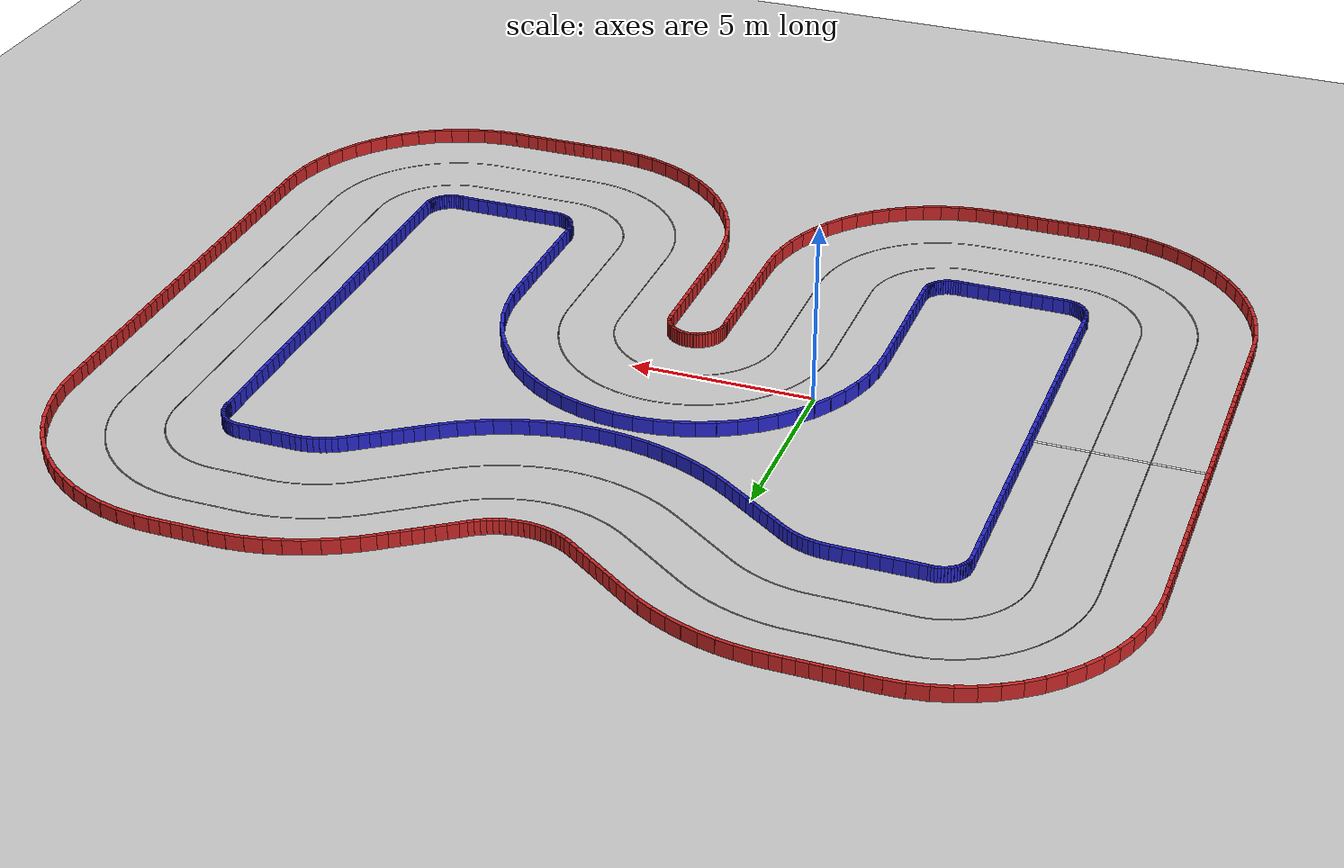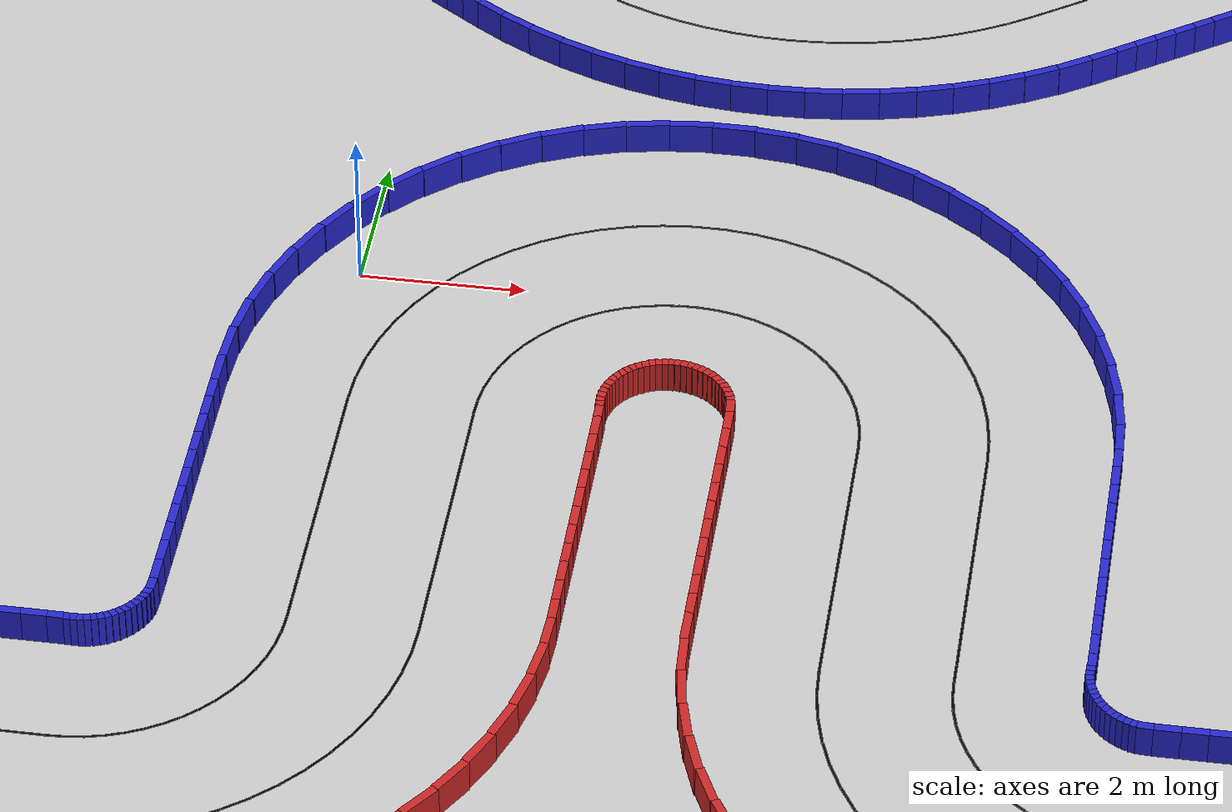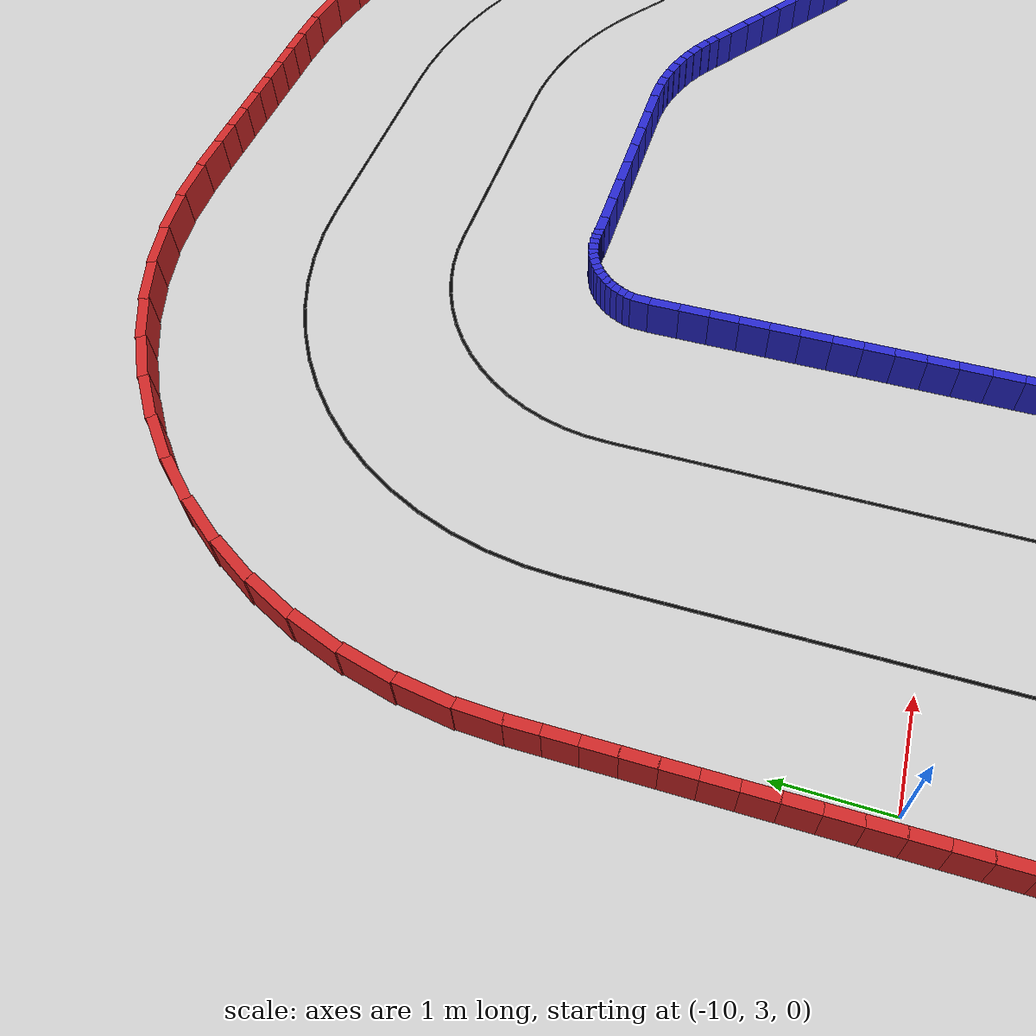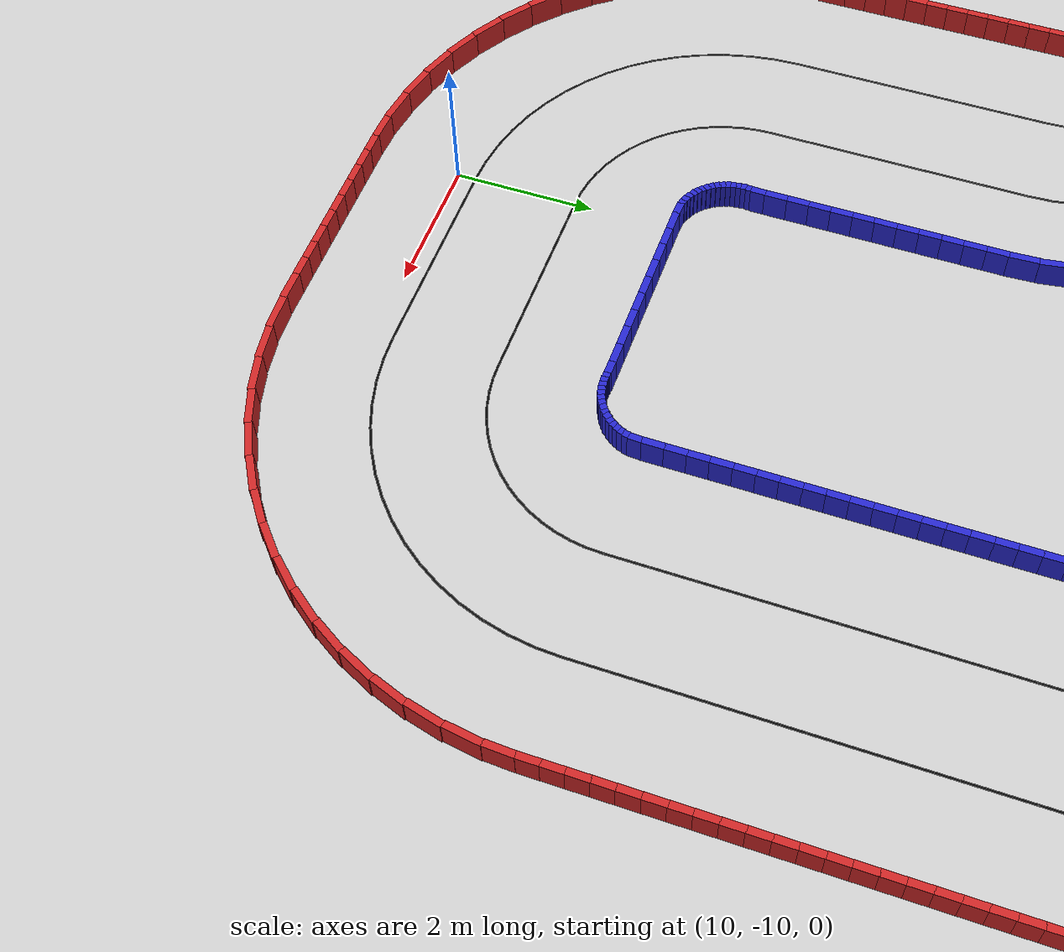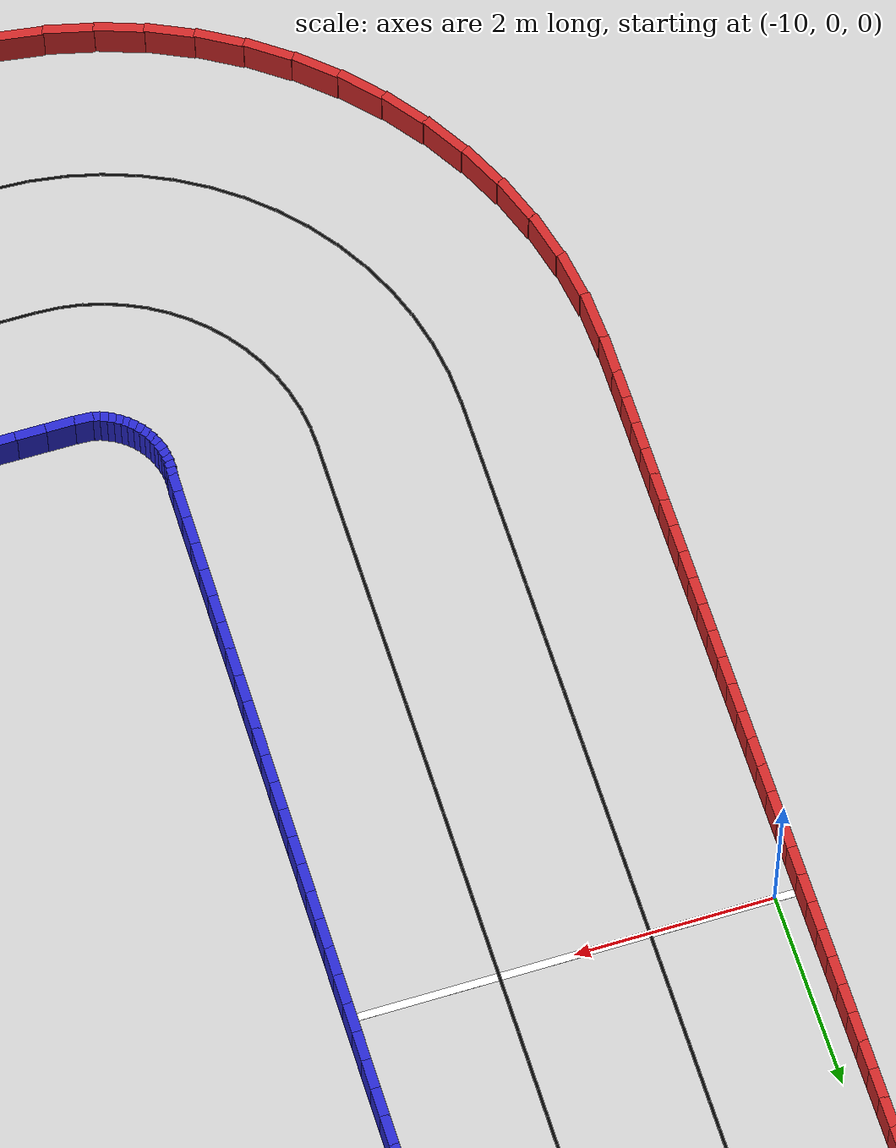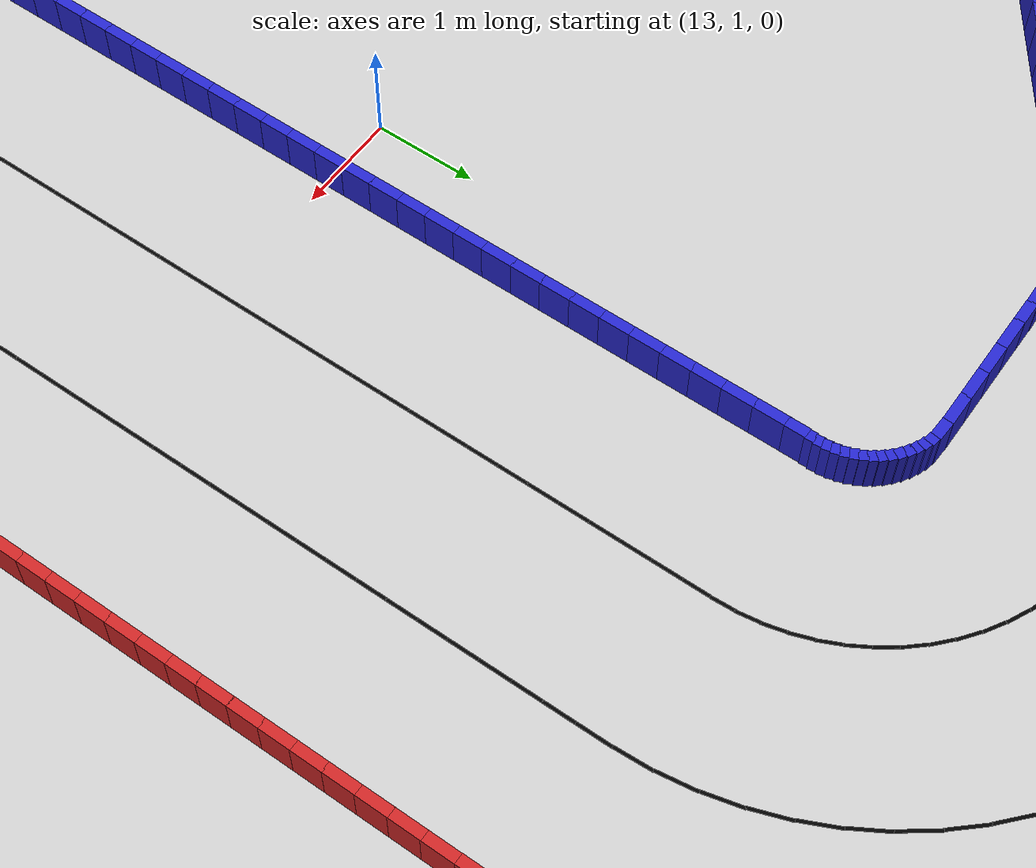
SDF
<?xml version="1.0"?>
<sdf version="1.6">
  <world name="3lane_track">
    <include><uri>model://ground_plane</uri></include>
    <include><uri>model://sun</uri></include>
    <scene><shadows>false</shadows></scene>
    <gui fullscreen="0">
      <camera name="user_camera">
        <pose>0 0 25.0 0 1.5708 0</pose>
        <view_controller>orbit</view_controller>
      </camera>
    </gui>
    <physics type="ode">
      <real_time_update_rate>500</real_time_update_rate>
      <max_step_size>0.002</max_step_size>
      <real_time_factor>1</real_time_factor>
    </physics>
    <model name="iw_0"><static>true</static><pose>-5.7500 -0.1500 0.200 0 0 -1.5708</pose><link name="l"><collision name="c"><geometry><box><size>0.3100 0.1 0.4</size></box></geometry></collision><visual name="v"><geometry><box><size>0.3100 0.1 0.4</size></box></geometry><material><ambient>0.15 0.15 0.8 1</ambient><diffuse>0.15 0.15 0.8 1</diffuse></material></visual></link></model>
    <model name="iw_1"><static>true</static><pose>-5.7500 -0.4500 0.200 0 0 -1.5708</pose><link name="l"><collision name="c"><geometry><box><size>0.3100 0.1 0.4</size></box></geometry></collision><visual name="v"><geometry><box><size>0.3100 0.1 0.4</size></box></geometry><material><ambient>0.15 0.15 0.8 1</ambient><diffuse>0.15 0.15 0.8 1</diffuse></material></visual></link></model>
    <model name="iw_2"><static>true</static><pose>-5.7500 -0.7500 0.200 0 0 -1.5708</pose><link name="l"><collision name="c"><geometry><box><size>0.3100 0.1 0.4</size></box></geometry></collision><visual name="v"><geometry><box><size>0.3100 0.1 0.4</size></box></geometry><material><ambient>0.15 0.15 0.8 1</ambient><diffuse>0.15 0.15 0.8 1</diffuse></material></visual></link></model>
    <model name="iw_3"><static>true</static><pose>-5.7500 -1.0500 0.200 0 0 -1.5708</pose><link name="l"><collision name="c"><geometry><box><size>0.3100 0.1 0.4</size></box></geometry></collision><visual name="v"><geometry><box><size>0.3100 0.1 0.4</size></box></geometry><material><ambient>0.15 0.15 0.8 1</ambient><diffuse>0.15 0.15 0.8 1</diffuse></material></visual></link></model>
    <model name="iw_4"><static>true</static><pose>-5.7500 -1.3500 0.200 0 0 -1.5708</pose><link name="l"><collision name="c"><geometry><box><size>0.3100 0.1 0.4</size></box></geometry></collision><visual name="v"><geometry><box><size>0.3100 0.1 0.4</size></box></geometry><material><ambient>0.15 0.15 0.8 1</ambient><diffuse>0.15 0.15 0.8 1</diffuse></material></visual></link></model>
    <model name="iw_5"><static>true</static><pose>-5.7500 -1.6500 0.200 0 0 -1.5708</pose><link name="l"><collision name="c"><geometry><box><size>0.3100 0.1 0.4</size></box></geometry></collision><visual name="v"><geometry><box><size>0.3100 0.1 0.4</size></box></geometry><material><ambient>0.15 0.15 0.8 1</ambient><diffuse>0.15 0.15 0.8 1</diffuse></material></visual></link></model>
    <model name="iw_6"><static>true</static><pose>-5.7500 -1.9500 0.200 0 0 -1.5708</pose><link name="l"><collision name="c"><geometry><box><size>0.3100 0.1 0.4</size></box></geometry></collision><visual name="v"><geometry><box><size>0.3100 0.1 0.4</size></box></geometry><material><ambient>0.15 0.15 0.8 1</ambient><diffuse>0.15 0.15 0.8 1</diffuse></material></visual></link></model>
    <model name="iw_7"><static>true</static><pose>-5.7500 -2.2500 0.200 0 0 -1.5708</pose><link name="l"><collision name="c"><geometry><box><size>0.3100 0.1 0.4</size></box></geometry></collision><visual name="v"><geometry><box><size>0.3100 0.1 0.4</size></box></geometry><material><ambient>0.15 0.15 0.8 1</ambient><diffuse>0.15 0.15 0.8 1</diffuse></material></visual></link></model>
    <model name="iw_8"><static>true</static><pose>-5.7500 -2.5500 0.200 0 0 -1.5708</pose><link name="l"><collision name="c"><geometry><box><size>0.3100 0.1 0.4</size></box></geometry></collision><visual name="v"><geometry><box><size>0.3100 0.1 0.4</size></box></geometry><material><ambient>0.15 0.15 0.8 1</ambient><diffuse>0.15 0.15 0.8 1</diffuse></material></visual></link></model>
    <model name="iw_9"><static>true</static><pose>-5.7500 -2.8500 0.200 0 0 -1.5708</pose><link name="l"><collision name="c"><geometry><box><size>0.3100 0.1 0.4</size></box></geometry></collision><visual name="v"><geometry><box><size>0.3100 0.1 0.4</size></box></geometry><material><ambient>0.15 0.15 0.8 1</ambient><diffuse>0.15 0.15 0.8 1</diffuse></material></visual></link></model>
    <model name="iw_10"><static>true</static><pose>-5.7500 -3.1500 0.200 0 0 -1.5708</pose><link name="l"><collision name="c"><geometry><box><size>0.3100 0.1 0.4</size></box></geometry></collision><visual name="v"><geometry><box><size>0.3100 0.1 0.4</size></box></geometry><material><ambient>0.15 0.15 0.8 1</ambient><diffuse>0.15 0.15 0.8 1</diffuse></material></visual></link></model>
    <model name="iw_11"><static>true</static><pose>-5.7500 -3.4500 0.200 0 0 -1.5708</pose><link name="l"><collision name="c"><geometry><box><size>0.3100 0.1 0.4</size></box></geometry></collision><visual name="v"><geometry><box><size>0.3100 0.1 0.4</size></box></geometry><material><ambient>0.15 0.15 0.8 1</ambient><diffuse>0.15 0.15 0.8 1</diffuse></material></visual></link></model>
    <model name="iw_12"><static>true</static><pose>-5.7500 -3.7500 0.200 0 0 -1.5708</pose><link name="l"><collision name="c"><geometry><box><size>0.3100 0.1 0.4</size></box></geometry></collision><visual name="v"><geometry><box><size>0.3100 0.1 0.4</size></box></geometry><material><ambient>0.15 0.15 0.8 1</ambient><diffuse>0.15 0.15 0.8 1</diffuse></material></visual></link></model>
    <model name="iw_13"><static>true</static><pose>-5.7500 -4.0500 0.200 0 0 -1.5708</pose><link name="l"><collision name="c"><geometry><box><size>0.3100 0.1 0.4</size></box></geometry></collision><visual name="v"><geometry><box><size>0.3100 0.1 0.4</size></box></geometry><material><ambient>0.15 0.15 0.8 1</ambient><diffuse>0.15 0.15 0.8 1</diffuse></material></visual></link></model>
    <model name="iw_14"><static>true</static><pose>-5.7500 -4.3500 0.200 0 0 -1.5708</pose><link name="l"><collision name="c"><geometry><box><size>0.3100 0.1 0.4</size></box></geometry></collision><visual name="v"><geometry><box><size>0.3100 0.1 0.4</size></box></geometry><material><ambient>0.15 0.15 0.8 1</ambient><diffuse>0.15 0.15 0.8 1</diffuse></material></visual></link></model>
    <model name="iw_15"><static>true</static><pose>-5.7500 -4.6500 0.200 0 0 -1.5708</pose><link name="l"><collision name="c"><geometry><box><size>0.3100 0.1 0.4</size></box></geometry></collision><visual name="v"><geometry><box><size>0.3100 0.1 0.4</size></box></geometry><material><ambient>0.15 0.15 0.8 1</ambient><diffuse>0.15 0.15 0.8 1</diffuse></material></visual></link></model>
    <model name="iw_16"><static>true</static><pose>-5.7500 -4.9500 0.200 0 0 -1.5708</pose><link name="l"><collision name="c"><geometry><box><size>0.3100 0.1 0.4</size></box></geometry></collision><visual name="v"><geometry><box><size>0.3100 0.1 0.4</size></box></geometry><material><ambient>0.15 0.15 0.8 1</ambient><diffuse>0.15 0.15 0.8 1</diffuse></material></visual></link></model>
    <model name="iw_17"><static>true</static><pose>-5.7500 -5.2500 0.200 0 0 -1.5708</pose><link name="l"><collision name="c"><geometry><box><size>0.3100 0.1 0.4</size></box></geometry></collision><visual name="v"><geometry><box><size>0.3100 0.1 0.4</size></box></geometry><material><ambient>0.15 0.15 0.8 1</ambient><diffuse>0.15 0.15 0.8 1</diffuse></material></visual></link></model>
    <model name="iw_18"><static>true</static><pose>-5.7500 -5.5500 0.200 0 0 -1.5708</pose><link name="l"><collision name="c"><geometry><box><size>0.3100 0.1 0.4</size></box></geometry></collision><visual name="v"><geometry><box><size>0.3100 0.1 0.4</size></box></geometry><material><ambient>0.15 0.15 0.8 1</ambient><diffuse>0.15 0.15 0.8 1</diffuse></material></visual></link></model>
    <model name="iw_19"><static>true</static><pose>-5.7514 -5.7948 0.200 0 0 -1.5708</pose><link name="l"><collision name="c"><geometry><box><size>0.1996 0.1 0.4</size></box></geometry></collision><visual name="v"><geometry><box><size>0.1996 0.1 0.4</size></box></geometry><material><ambient>0.15 0.15 0.8 1</ambient><diffuse>0.15 0.15 0.8 1</diffuse></material></visual></link></model>
    <model name="iw_20"><static>true</static><pose>-5.7563 -5.9268 0.200 0 0 -1.5217</pose><link name="l"><collision name="c"><geometry><box><size>0.0847 0.1 0.4</size></box></geometry></collision><visual name="v"><geometry><box><size>0.0847 0.1 0.4</size></box></geometry><material><ambient>0.15 0.15 0.8 1</ambient><diffuse>0.15 0.15 0.8 1</diffuse></material></visual></link></model>
    <model name="iw_21"><static>true</static><pose>-5.7598 -6.0012 0.200 0 0 -1.4235</pose><link name="l"><collision name="c"><geometry><box><size>0.0847 0.1 0.4</size></box></geometry></collision><visual name="v"><geometry><box><size>0.0847 0.1 0.4</size></box></geometry><material><ambient>0.15 0.15 0.8 1</ambient><diffuse>0.15 0.15 0.8 1</diffuse></material></visual></link></model>
    <model name="iw_22"><static>true</static><pose>-5.7561 -6.0757 0.200 0 0 -1.3254</pose><link name="l"><collision name="c"><geometry><box><size>0.0847 0.1 0.4</size></box></geometry></collision><visual name="v"><geometry><box><size>0.0847 0.1 0.4</size></box></geometry><material><ambient>0.15 0.15 0.8 1</ambient><diffuse>0.15 0.15 0.8 1</diffuse></material></visual></link></model>
    <model name="iw_23"><static>true</static><pose>-5.7450 -6.1495 0.200 0 0 -1.2272</pose><link name="l"><collision name="c"><geometry><box><size>0.0847 0.1 0.4</size></box></geometry></collision><visual name="v"><geometry><box><size>0.0847 0.1 0.4</size></box></geometry><material><ambient>0.15 0.15 0.8 1</ambient><diffuse>0.15 0.15 0.8 1</diffuse></material></visual></link></model>
    <model name="iw_24"><static>true</static><pose>-5.7268 -6.2218 0.200 0 0 -1.1290</pose><link name="l"><collision name="c"><geometry><box><size>0.0847 0.1 0.4</size></box></geometry></collision><visual name="v"><geometry><box><size>0.0847 0.1 0.4</size></box></geometry><material><ambient>0.15 0.15 0.8 1</ambient><diffuse>0.15 0.15 0.8 1</diffuse></material></visual></link></model>
    <model name="iw_25"><static>true</static><pose>-5.7015 -6.2919 0.200 0 0 -1.0308</pose><link name="l"><collision name="c"><geometry><box><size>0.0847 0.1 0.4</size></box></geometry></collision><visual name="v"><geometry><box><size>0.0847 0.1 0.4</size></box></geometry><material><ambient>0.15 0.15 0.8 1</ambient><diffuse>0.15 0.15 0.8 1</diffuse></material></visual></link></model>
    <model name="iw_26"><static>true</static><pose>-5.6695 -6.3593 0.200 0 0 -0.9327</pose><link name="l"><collision name="c"><geometry><box><size>0.0847 0.1 0.4</size></box></geometry></collision><visual name="v"><geometry><box><size>0.0847 0.1 0.4</size></box></geometry><material><ambient>0.15 0.15 0.8 1</ambient><diffuse>0.15 0.15 0.8 1</diffuse></material></visual></link></model>
    <model name="iw_27"><static>true</static><pose>-5.6311 -6.4232 0.200 0 0 -0.8345</pose><link name="l"><collision name="c"><geometry><box><size>0.0847 0.1 0.4</size></box></geometry></collision><visual name="v"><geometry><box><size>0.0847 0.1 0.4</size></box></geometry><material><ambient>0.15 0.15 0.8 1</ambient><diffuse>0.15 0.15 0.8 1</diffuse></material></visual></link></model>
    <model name="iw_28"><static>true</static><pose>-5.5866 -6.4830 0.200 0 0 -0.7363</pose><link name="l"><collision name="c"><geometry><box><size>0.0847 0.1 0.4</size></box></geometry></collision><visual name="v"><geometry><box><size>0.0847 0.1 0.4</size></box></geometry><material><ambient>0.15 0.15 0.8 1</ambient><diffuse>0.15 0.15 0.8 1</diffuse></material></visual></link></model>
    <model name="iw_29"><static>true</static><pose>-5.5364 -6.5382 0.200 0 0 -0.6381</pose><link name="l"><collision name="c"><geometry><box><size>0.0847 0.1 0.4</size></box></geometry></collision><visual name="v"><geometry><box><size>0.0847 0.1 0.4</size></box></geometry><material><ambient>0.15 0.15 0.8 1</ambient><diffuse>0.15 0.15 0.8 1</diffuse></material></visual></link></model>
    <model name="iw_30"><static>true</static><pose>-5.4811 -6.5882 0.200 0 0 -0.5400</pose><link name="l"><collision name="c"><geometry><box><size>0.0847 0.1 0.4</size></box></geometry></collision><visual name="v"><geometry><box><size>0.0847 0.1 0.4</size></box></geometry><material><ambient>0.15 0.15 0.8 1</ambient><diffuse>0.15 0.15 0.8 1</diffuse></material></visual></link></model>
    <model name="iw_31"><static>true</static><pose>-5.4211 -6.6325 0.200 0 0 -0.4418</pose><link name="l"><collision name="c"><geometry><box><size>0.0847 0.1 0.4</size></box></geometry></collision><visual name="v"><geometry><box><size>0.0847 0.1 0.4</size></box></geometry><material><ambient>0.15 0.15 0.8 1</ambient><diffuse>0.15 0.15 0.8 1</diffuse></material></visual></link></model>
    <model name="iw_32"><static>true</static><pose>-5.3571 -6.6707 0.200 0 0 -0.3436</pose><link name="l"><collision name="c"><geometry><box><size>0.0847 0.1 0.4</size></box></geometry></collision><visual name="v"><geometry><box><size>0.0847 0.1 0.4</size></box></geometry><material><ambient>0.15 0.15 0.8 1</ambient><diffuse>0.15 0.15 0.8 1</diffuse></material></visual></link></model>
    <model name="iw_33"><static>true</static><pose>-5.2896 -6.7025 0.200 0 0 -0.2454</pose><link name="l"><collision name="c"><geometry><box><size>0.0847 0.1 0.4</size></box></geometry></collision><visual name="v"><geometry><box><size>0.0847 0.1 0.4</size></box></geometry><material><ambient>0.15 0.15 0.8 1</ambient><diffuse>0.15 0.15 0.8 1</diffuse></material></visual></link></model>
    <model name="iw_34"><static>true</static><pose>-5.2194 -6.7275 0.200 0 0 -0.1473</pose><link name="l"><collision name="c"><geometry><box><size>0.0847 0.1 0.4</size></box></geometry></collision><visual name="v"><geometry><box><size>0.0847 0.1 0.4</size></box></geometry><material><ambient>0.15 0.15 0.8 1</ambient><diffuse>0.15 0.15 0.8 1</diffuse></material></visual></link></model>
    <model name="iw_35"><static>true</static><pose>-5.0918 -6.7441 0.200 0 0 -0.0491</pose><link name="l"><collision name="c"><geometry><box><size>0.1940 0.1 0.4</size></box></geometry></collision><visual name="v"><geometry><box><size>0.1940 0.1 0.4</size></box></geometry><material><ambient>0.15 0.15 0.8 1</ambient><diffuse>0.15 0.15 0.8 1</diffuse></material></visual></link></model>
    <model name="iw_36"><static>true</static><pose>-4.8500 -6.7500 0.200 0 0 0.0000</pose><link name="l"><collision name="c"><geometry><box><size>0.3100 0.1 0.4</size></box></geometry></collision><visual name="v"><geometry><box><size>0.3100 0.1 0.4</size></box></geometry><material><ambient>0.15 0.15 0.8 1</ambient><diffuse>0.15 0.15 0.8 1</diffuse></material></visual></link></model>
    <model name="iw_37"><static>true</static><pose>-4.5500 -6.7500 0.200 0 0 0.0000</pose><link name="l"><collision name="c"><geometry><box><size>0.3100 0.1 0.4</size></box></geometry></collision><visual name="v"><geometry><box><size>0.3100 0.1 0.4</size></box></geometry><material><ambient>0.15 0.15 0.8 1</ambient><diffuse>0.15 0.15 0.8 1</diffuse></material></visual></link></model>
    <model name="iw_38"><static>true</static><pose>-4.2500 -6.7500 0.200 0 0 0.0000</pose><link name="l"><collision name="c"><geometry><box><size>0.3100 0.1 0.4</size></box></geometry></collision><visual name="v"><geometry><box><size>0.3100 0.1 0.4</size></box></geometry><material><ambient>0.15 0.15 0.8 1</ambient><diffuse>0.15 0.15 0.8 1</diffuse></material></visual></link></model>
    <model name="iw_39"><static>true</static><pose>-3.9500 -6.7500 0.200 0 0 0.0000</pose><link name="l"><collision name="c"><geometry><box><size>0.3100 0.1 0.4</size></box></geometry></collision><visual name="v"><geometry><box><size>0.3100 0.1 0.4</size></box></geometry><material><ambient>0.15 0.15 0.8 1</ambient><diffuse>0.15 0.15 0.8 1</diffuse></material></visual></link></model>
    <model name="iw_40"><static>true</static><pose>-3.6500 -6.7500 0.200 0 0 0.0000</pose><link name="l"><collision name="c"><geometry><box><size>0.3100 0.1 0.4</size></box></geometry></collision><visual name="v"><geometry><box><size>0.3100 0.1 0.4</size></box></geometry><material><ambient>0.15 0.15 0.8 1</ambient><diffuse>0.15 0.15 0.8 1</diffuse></material></visual></link></model>
    <model name="iw_41"><static>true</static><pose>-3.3500 -6.7500 0.200 0 0 0.0000</pose><link name="l"><collision name="c"><geometry><box><size>0.3100 0.1 0.4</size></box></geometry></collision><visual name="v"><geometry><box><size>0.3100 0.1 0.4</size></box></geometry><material><ambient>0.15 0.15 0.8 1</ambient><diffuse>0.15 0.15 0.8 1</diffuse></material></visual></link></model>
    <model name="iw_42"><static>true</static><pose>-3.0500 -6.7500 0.200 0 0 0.0000</pose><link name="l"><collision name="c"><geometry><box><size>0.3100 0.1 0.4</size></box></geometry></collision><visual name="v"><geometry><box><size>0.3100 0.1 0.4</size></box></geometry><material><ambient>0.15 0.15 0.8 1</ambient><diffuse>0.15 0.15 0.8 1</diffuse></material></visual></link></model>
    <model name="iw_43"><static>true</static><pose>-2.7500 -6.7500 0.200 0 0 0.0000</pose><link name="l"><collision name="c"><geometry><box><size>0.3100 0.1 0.4</size></box></geometry></collision><visual name="v"><geometry><box><size>0.3100 0.1 0.4</size></box></geometry><material><ambient>0.15 0.15 0.8 1</ambient><diffuse>0.15 0.15 0.8 1</diffuse></material></visual></link></model>
    <model name="iw_44"><static>true</static><pose>-2.4500 -6.7500 0.200 0 0 0.0000</pose><link name="l"><collision name="c"><geometry><box><size>0.3100 0.1 0.4</size></box></geometry></collision><visual name="v"><geometry><box><size>0.3100 0.1 0.4</size></box></geometry><material><ambient>0.15 0.15 0.8 1</ambient><diffuse>0.15 0.15 0.8 1</diffuse></material></visual></link></model>
    <model name="iw_45"><static>true</static><pose>-2.2052 -6.7514 0.200 0 0 0.0000</pose><link name="l"><collision name="c"><geometry><box><size>0.1996 0.1 0.4</size></box></geometry></collision><visual name="v"><geometry><box><size>0.1996 0.1 0.4</size></box></geometry><material><ambient>0.15 0.15 0.8 1</ambient><diffuse>0.15 0.15 0.8 1</diffuse></material></visual></link></model>
    <model name="iw_46"><static>true</static><pose>-2.0732 -6.7563 0.200 0 0 0.0491</pose><link name="l"><collision name="c"><geometry><box><size>0.0847 0.1 0.4</size></box></geometry></collision><visual name="v"><geometry><box><size>0.0847 0.1 0.4</size></box></geometry><material><ambient>0.15 0.15 0.8 1</ambient><diffuse>0.15 0.15 0.8 1</diffuse></material></visual></link></model>
    <model name="iw_47"><static>true</static><pose>-1.9988 -6.7598 0.200 0 0 0.1473</pose><link name="l"><collision name="c"><geometry><box><size>0.0847 0.1 0.4</size></box></geometry></collision><visual name="v"><geometry><box><size>0.0847 0.1 0.4</size></box></geometry><material><ambient>0.15 0.15 0.8 1</ambient><diffuse>0.15 0.15 0.8 1</diffuse></material></visual></link></model>
    <model name="iw_48"><static>true</static><pose>-1.9243 -6.7561 0.200 0 0 0.2454</pose><link name="l"><collision name="c"><geometry><box><size>0.0847 0.1 0.4</size></box></geometry></collision><visual name="v"><geometry><box><size>0.0847 0.1 0.4</size></box></geometry><material><ambient>0.15 0.15 0.8 1</ambient><diffuse>0.15 0.15 0.8 1</diffuse></material></visual></link></model>
    <model name="iw_49"><static>true</static><pose>-1.8505 -6.7450 0.200 0 0 0.3436</pose><link name="l"><collision name="c"><geometry><box><size>0.0847 0.1 0.4</size></box></geometry></collision><visual name="v"><geometry><box><size>0.0847 0.1 0.4</size></box></geometry><material><ambient>0.15 0.15 0.8 1</ambient><diffuse>0.15 0.15 0.8 1</diffuse></material></visual></link></model>
    <model name="iw_50"><static>true</static><pose>-1.7782 -6.7268 0.200 0 0 0.4418</pose><link name="l"><collision name="c"><geometry><box><size>0.0847 0.1 0.4</size></box></geometry></collision><visual name="v"><geometry><box><size>0.0847 0.1 0.4</size></box></geometry><material><ambient>0.15 0.15 0.8 1</ambient><diffuse>0.15 0.15 0.8 1</diffuse></material></visual></link></model>
    <model name="iw_51"><static>true</static><pose>-1.7081 -6.7015 0.200 0 0 0.5400</pose><link name="l"><collision name="c"><geometry><box><size>0.0847 0.1 0.4</size></box></geometry></collision><visual name="v"><geometry><box><size>0.0847 0.1 0.4</size></box></geometry><material><ambient>0.15 0.15 0.8 1</ambient><diffuse>0.15 0.15 0.8 1</diffuse></material></visual></link></model>
    <model name="iw_52"><static>true</static><pose>-1.6407 -6.6695 0.200 0 0 0.6381</pose><link name="l"><collision name="c"><geometry><box><size>0.0847 0.1 0.4</size></box></geometry></collision><visual name="v"><geometry><box><size>0.0847 0.1 0.4</size></box></geometry><material><ambient>0.15 0.15 0.8 1</ambient><diffuse>0.15 0.15 0.8 1</diffuse></material></visual></link></model>
    <model name="iw_53"><static>true</static><pose>-1.5768 -6.6311 0.200 0 0 0.7363</pose><link name="l"><collision name="c"><geometry><box><size>0.0847 0.1 0.4</size></box></geometry></collision><visual name="v"><geometry><box><size>0.0847 0.1 0.4</size></box></geometry><material><ambient>0.15 0.15 0.8 1</ambient><diffuse>0.15 0.15 0.8 1</diffuse></material></visual></link></model>
    <model name="iw_54"><static>true</static><pose>-1.5170 -6.5866 0.200 0 0 0.8345</pose><link name="l"><collision name="c"><geometry><box><size>0.0847 0.1 0.4</size></box></geometry></collision><visual name="v"><geometry><box><size>0.0847 0.1 0.4</size></box></geometry><material><ambient>0.15 0.15 0.8 1</ambient><diffuse>0.15 0.15 0.8 1</diffuse></material></visual></link></model>
    <model name="iw_55"><static>true</static><pose>-1.4618 -6.5364 0.200 0 0 0.9327</pose><link name="l"><collision name="c"><geometry><box><size>0.0847 0.1 0.4</size></box></geometry></collision><visual name="v"><geometry><box><size>0.0847 0.1 0.4</size></box></geometry><material><ambient>0.15 0.15 0.8 1</ambient><diffuse>0.15 0.15 0.8 1</diffuse></material></visual></link></model>
    <model name="iw_56"><static>true</static><pose>-1.4118 -6.4811 0.200 0 0 1.0308</pose><link name="l"><collision name="c"><geometry><box><size>0.0847 0.1 0.4</size></box></geometry></collision><visual name="v"><geometry><box><size>0.0847 0.1 0.4</size></box></geometry><material><ambient>0.15 0.15 0.8 1</ambient><diffuse>0.15 0.15 0.8 1</diffuse></material></visual></link></model>
    <model name="iw_57"><static>true</static><pose>-1.3675 -6.4211 0.200 0 0 1.1290</pose><link name="l"><collision name="c"><geometry><box><size>0.0847 0.1 0.4</size></box></geometry></collision><visual name="v"><geometry><box><size>0.0847 0.1 0.4</size></box></geometry><material><ambient>0.15 0.15 0.8 1</ambient><diffuse>0.15 0.15 0.8 1</diffuse></material></visual></link></model>
    <model name="iw_58"><static>true</static><pose>-1.3293 -6.3571 0.200 0 0 1.2272</pose><link name="l"><collision name="c"><geometry><box><size>0.0847 0.1 0.4</size></box></geometry></collision><visual name="v"><geometry><box><size>0.0847 0.1 0.4</size></box></geometry><material><ambient>0.15 0.15 0.8 1</ambient><diffuse>0.15 0.15 0.8 1</diffuse></material></visual></link></model>
    <model name="iw_59"><static>true</static><pose>-1.2975 -6.2896 0.200 0 0 1.3254</pose><link name="l"><collision name="c"><geometry><box><size>0.0847 0.1 0.4</size></box></geometry></collision><visual name="v"><geometry><box><size>0.0847 0.1 0.4</size></box></geometry><material><ambient>0.15 0.15 0.8 1</ambient><diffuse>0.15 0.15 0.8 1</diffuse></material></visual></link></model>
    <model name="iw_60"><static>true</static><pose>-1.2725 -6.2194 0.200 0 0 1.4235</pose><link name="l"><collision name="c"><geometry><box><size>0.0847 0.1 0.4</size></box></geometry></collision><visual name="v"><geometry><box><size>0.0847 0.1 0.4</size></box></geometry><material><ambient>0.15 0.15 0.8 1</ambient><diffuse>0.15 0.15 0.8 1</diffuse></material></visual></link></model>
    <model name="iw_61"><static>true</static><pose>-1.2559 -6.0918 0.200 0 0 1.5217</pose><link name="l"><collision name="c"><geometry><box><size>0.1940 0.1 0.4</size></box></geometry></collision><visual name="v"><geometry><box><size>0.1940 0.1 0.4</size></box></geometry><material><ambient>0.15 0.15 0.8 1</ambient><diffuse>0.15 0.15 0.8 1</diffuse></material></visual></link></model>
    <model name="iw_62"><static>true</static><pose>-1.2500 -5.8437 0.200 0 0 1.5708</pose><link name="l"><collision name="c"><geometry><box><size>0.3225 0.1 0.4</size></box></geometry></collision><visual name="v"><geometry><box><size>0.3225 0.1 0.4</size></box></geometry><material><ambient>0.15 0.15 0.8 1</ambient><diffuse>0.15 0.15 0.8 1</diffuse></material></visual></link></model>
    <model name="iw_63"><static>true</static><pose>-1.2500 -5.5312 0.200 0 0 1.5708</pose><link name="l"><collision name="c"><geometry><box><size>0.3225 0.1 0.4</size></box></geometry></collision><visual name="v"><geometry><box><size>0.3225 0.1 0.4</size></box></geometry><material><ambient>0.15 0.15 0.8 1</ambient><diffuse>0.15 0.15 0.8 1</diffuse></material></visual></link></model>
    <model name="iw_64"><static>true</static><pose>-1.2500 -5.2187 0.200 0 0 1.5708</pose><link name="l"><collision name="c"><geometry><box><size>0.3225 0.1 0.4</size></box></geometry></collision><visual name="v"><geometry><box><size>0.3225 0.1 0.4</size></box></geometry><material><ambient>0.15 0.15 0.8 1</ambient><diffuse>0.15 0.15 0.8 1</diffuse></material></visual></link></model>
    <model name="iw_65"><static>true</static><pose>-1.2500 -4.9062 0.200 0 0 1.5708</pose><link name="l"><collision name="c"><geometry><box><size>0.3225 0.1 0.4</size></box></geometry></collision><visual name="v"><geometry><box><size>0.3225 0.1 0.4</size></box></geometry><material><ambient>0.15 0.15 0.8 1</ambient><diffuse>0.15 0.15 0.8 1</diffuse></material></visual></link></model>
    <model name="iw_66"><static>true</static><pose>-1.2500 -4.5937 0.200 0 0 1.5708</pose><link name="l"><collision name="c"><geometry><box><size>0.3225 0.1 0.4</size></box></geometry></collision><visual name="v"><geometry><box><size>0.3225 0.1 0.4</size></box></geometry><material><ambient>0.15 0.15 0.8 1</ambient><diffuse>0.15 0.15 0.8 1</diffuse></material></visual></link></model>
    <model name="iw_67"><static>true</static><pose>-1.2500 -4.2812 0.200 0 0 1.5708</pose><link name="l"><collision name="c"><geometry><box><size>0.3225 0.1 0.4</size></box></geometry></collision><visual name="v"><geometry><box><size>0.3225 0.1 0.4</size></box></geometry><material><ambient>0.15 0.15 0.8 1</ambient><diffuse>0.15 0.15 0.8 1</diffuse></material></visual></link></model>
    <model name="iw_68"><static>true</static><pose>-1.2500 -3.9687 0.200 0 0 1.5708</pose><link name="l"><collision name="c"><geometry><box><size>0.3225 0.1 0.4</size></box></geometry></collision><visual name="v"><geometry><box><size>0.3225 0.1 0.4</size></box></geometry><material><ambient>0.15 0.15 0.8 1</ambient><diffuse>0.15 0.15 0.8 1</diffuse></material></visual></link></model>
    <model name="iw_69"><static>true</static><pose>-1.2500 -3.6562 0.200 0 0 1.5708</pose><link name="l"><collision name="c"><geometry><box><size>0.3225 0.1 0.4</size></box></geometry></collision><visual name="v"><geometry><box><size>0.3225 0.1 0.4</size></box></geometry><material><ambient>0.15 0.15 0.8 1</ambient><diffuse>0.15 0.15 0.8 1</diffuse></material></visual></link></model>
    <model name="iw_70"><static>true</static><pose>-1.2500 -3.3437 0.200 0 0 1.5708</pose><link name="l"><collision name="c"><geometry><box><size>0.3225 0.1 0.4</size></box></geometry></collision><visual name="v"><geometry><box><size>0.3225 0.1 0.4</size></box></geometry><material><ambient>0.15 0.15 0.8 1</ambient><diffuse>0.15 0.15 0.8 1</diffuse></material></visual></link></model>
    <model name="iw_71"><static>true</static><pose>-1.2500 -3.0312 0.200 0 0 1.5708</pose><link name="l"><collision name="c"><geometry><box><size>0.3225 0.1 0.4</size></box></geometry></collision><visual name="v"><geometry><box><size>0.3225 0.1 0.4</size></box></geometry><material><ambient>0.15 0.15 0.8 1</ambient><diffuse>0.15 0.15 0.8 1</diffuse></material></visual></link></model>
    <model name="iw_72"><static>true</static><pose>-1.2500 -2.7187 0.200 0 0 1.5708</pose><link name="l"><collision name="c"><geometry><box><size>0.3225 0.1 0.4</size></box></geometry></collision><visual name="v"><geometry><box><size>0.3225 0.1 0.4</size></box></geometry><material><ambient>0.15 0.15 0.8 1</ambient><diffuse>0.15 0.15 0.8 1</diffuse></material></visual></link></model>
    <model name="iw_73"><static>true</static><pose>-1.2486 -2.3493 0.200 0 0 1.5708</pose><link name="l"><collision name="c"><geometry><box><size>0.4365 0.1 0.4</size></box></geometry></collision><visual name="v"><geometry><box><size>0.4365 0.1 0.4</size></box></geometry><material><ambient>0.15 0.15 0.8 1</ambient><diffuse>0.15 0.15 0.8 1</diffuse></material></visual></link></model>
    <model name="iw_74"><static>true</static><pose>-1.2279 -1.8709 0.200 0 0 1.5201</pose><link name="l"><collision name="c"><geometry><box><size>0.5416 0.1 0.4</size></box></geometry></collision><visual name="v"><geometry><box><size>0.5416 0.1 0.4</size></box></geometry><material><ambient>0.15 0.15 0.8 1</ambient><diffuse>0.15 0.15 0.8 1</diffuse></material></visual></link></model>
    <model name="iw_75"><static>true</static><pose>-1.1627 -1.3440 0.200 0 0 1.4188</pose><link name="l"><collision name="c"><geometry><box><size>0.5416 0.1 0.4</size></box></geometry></collision><visual name="v"><geometry><box><size>0.5416 0.1 0.4</size></box></geometry><material><ambient>0.15 0.15 0.8 1</ambient><diffuse>0.15 0.15 0.8 1</diffuse></material></visual></link></model>
    <model name="iw_76"><static>true</static><pose>-1.0446 -0.8263 0.200 0 0 1.3174</pose><link name="l"><collision name="c"><geometry><box><size>0.5416 0.1 0.4</size></box></geometry></collision><visual name="v"><geometry><box><size>0.5416 0.1 0.4</size></box></geometry><material><ambient>0.15 0.15 0.8 1</ambient><diffuse>0.15 0.15 0.8 1</diffuse></material></visual></link></model>
    <model name="iw_77"><static>true</static><pose>-0.8746 -0.3233 0.200 0 0 1.2161</pose><link name="l"><collision name="c"><geometry><box><size>0.5416 0.1 0.4</size></box></geometry></collision><visual name="v"><geometry><box><size>0.5416 0.1 0.4</size></box></geometry><material><ambient>0.15 0.15 0.8 1</ambient><diffuse>0.15 0.15 0.8 1</diffuse></material></visual></link></model>
    <model name="iw_78"><static>true</static><pose>-0.6547 0.1600 0.200 0 0 1.1148</pose><link name="l"><collision name="c"><geometry><box><size>0.5416 0.1 0.4</size></box></geometry></collision><visual name="v"><geometry><box><size>0.5416 0.1 0.4</size></box></geometry><material><ambient>0.15 0.15 0.8 1</ambient><diffuse>0.15 0.15 0.8 1</diffuse></material></visual></link></model>
    <model name="iw_79"><static>true</static><pose>-0.3870 0.6186 0.200 0 0 1.0134</pose><link name="l"><collision name="c"><geometry><box><size>0.5416 0.1 0.4</size></box></geometry></collision><visual name="v"><geometry><box><size>0.5416 0.1 0.4</size></box></geometry><material><ambient>0.15 0.15 0.8 1</ambient><diffuse>0.15 0.15 0.8 1</diffuse></material></visual></link></model>
    <model name="iw_80"><static>true</static><pose>-0.0743 1.0477 0.200 0 0 0.9121</pose><link name="l"><collision name="c"><geometry><box><size>0.5416 0.1 0.4</size></box></geometry></collision><visual name="v"><geometry><box><size>0.5416 0.1 0.4</size></box></geometry><material><ambient>0.15 0.15 0.8 1</ambient><diffuse>0.15 0.15 0.8 1</diffuse></material></visual></link></model>
    <model name="iw_81"><static>true</static><pose>0.2802 1.4429 0.200 0 0 0.8107</pose><link name="l"><collision name="c"><geometry><box><size>0.5416 0.1 0.4</size></box></geometry></collision><visual name="v"><geometry><box><size>0.5416 0.1 0.4</size></box></geometry><material><ambient>0.15 0.15 0.8 1</ambient><diffuse>0.15 0.15 0.8 1</diffuse></material></visual></link></model>
    <model name="iw_82"><static>true</static><pose>0.6729 1.8003 0.200 0 0 0.7094</pose><link name="l"><collision name="c"><geometry><box><size>0.5416 0.1 0.4</size></box></geometry></collision><visual name="v"><geometry><box><size>0.5416 0.1 0.4</size></box></geometry><material><ambient>0.15 0.15 0.8 1</ambient><diffuse>0.15 0.15 0.8 1</diffuse></material></visual></link></model>
    <model name="iw_83"><static>true</static><pose>1.0998 2.1161 0.200 0 0 0.6081</pose><link name="l"><collision name="c"><geometry><box><size>0.5416 0.1 0.4</size></box></geometry></collision><visual name="v"><geometry><box><size>0.5416 0.1 0.4</size></box></geometry><material><ambient>0.15 0.15 0.8 1</ambient><diffuse>0.15 0.15 0.8 1</diffuse></material></visual></link></model>
    <model name="iw_84"><static>true</static><pose>1.5563 2.3871 0.200 0 0 0.5067</pose><link name="l"><collision name="c"><geometry><box><size>0.5416 0.1 0.4</size></box></geometry></collision><visual name="v"><geometry><box><size>0.5416 0.1 0.4</size></box></geometry><material><ambient>0.15 0.15 0.8 1</ambient><diffuse>0.15 0.15 0.8 1</diffuse></material></visual></link></model>
    <model name="iw_85"><static>true</static><pose>2.0380 2.6106 0.200 0 0 0.4054</pose><link name="l"><collision name="c"><geometry><box><size>0.5416 0.1 0.4</size></box></geometry></collision><visual name="v"><geometry><box><size>0.5416 0.1 0.4</size></box></geometry><material><ambient>0.15 0.15 0.8 1</ambient><diffuse>0.15 0.15 0.8 1</diffuse></material></visual></link></model>
    <model name="iw_86"><static>true</static><pose>2.5398 2.7841 0.200 0 0 0.3040</pose><link name="l"><collision name="c"><geometry><box><size>0.5416 0.1 0.4</size></box></geometry></collision><visual name="v"><geometry><box><size>0.5416 0.1 0.4</size></box></geometry><material><ambient>0.15 0.15 0.8 1</ambient><diffuse>0.15 0.15 0.8 1</diffuse></material></visual></link></model>
    <model name="iw_87"><static>true</static><pose>3.0566 2.9060 0.200 0 0 0.2027</pose><link name="l"><collision name="c"><geometry><box><size>0.5416 0.1 0.4</size></box></geometry></collision><visual name="v"><geometry><box><size>0.5416 0.1 0.4</size></box></geometry><material><ambient>0.15 0.15 0.8 1</ambient><diffuse>0.15 0.15 0.8 1</diffuse></material></visual></link></model>
    <model name="iw_88"><static>true</static><pose>3.5831 2.9750 0.200 0 0 0.1013</pose><link name="l"><collision name="c"><geometry><box><size>0.5416 0.1 0.4</size></box></geometry></collision><visual name="v"><geometry><box><size>0.5416 0.1 0.4</size></box></geometry><material><ambient>0.15 0.15 0.8 1</ambient><diffuse>0.15 0.15 0.8 1</diffuse></material></visual></link></model>
    <model name="iw_89"><static>true</static><pose>4.1138 2.9904 0.200 0 0 0.0000</pose><link name="l"><collision name="c"><geometry><box><size>0.5416 0.1 0.4</size></box></geometry></collision><visual name="v"><geometry><box><size>0.5416 0.1 0.4</size></box></geometry><material><ambient>0.15 0.15 0.8 1</ambient><diffuse>0.15 0.15 0.8 1</diffuse></material></visual></link></model>
    <model name="iw_90"><static>true</static><pose>4.6434 2.9520 0.200 0 0 -0.1013</pose><link name="l"><collision name="c"><geometry><box><size>0.5416 0.1 0.4</size></box></geometry></collision><visual name="v"><geometry><box><size>0.5416 0.1 0.4</size></box></geometry><material><ambient>0.15 0.15 0.8 1</ambient><diffuse>0.15 0.15 0.8 1</diffuse></material></visual></link></model>
    <model name="iw_91"><static>true</static><pose>5.1664 2.8602 0.200 0 0 -0.2027</pose><link name="l"><collision name="c"><geometry><box><size>0.5416 0.1 0.4</size></box></geometry></collision><visual name="v"><geometry><box><size>0.5416 0.1 0.4</size></box></geometry><material><ambient>0.15 0.15 0.8 1</ambient><diffuse>0.15 0.15 0.8 1</diffuse></material></visual></link></model>
    <model name="iw_92"><static>true</static><pose>5.6774 2.7160 0.200 0 0 -0.3040</pose><link name="l"><collision name="c"><geometry><box><size>0.5416 0.1 0.4</size></box></geometry></collision><visual name="v"><geometry><box><size>0.5416 0.1 0.4</size></box></geometry><material><ambient>0.15 0.15 0.8 1</ambient><diffuse>0.15 0.15 0.8 1</diffuse></material></visual></link></model>
    <model name="iw_93"><static>true</static><pose>6.1712 2.5208 0.200 0 0 -0.4054</pose><link name="l"><collision name="c"><geometry><box><size>0.5416 0.1 0.4</size></box></geometry></collision><visual name="v"><geometry><box><size>0.5416 0.1 0.4</size></box></geometry><material><ambient>0.15 0.15 0.8 1</ambient><diffuse>0.15 0.15 0.8 1</diffuse></material></visual></link></model>
    <model name="iw_94"><static>true</static><pose>6.6427 2.2767 0.200 0 0 -0.5067</pose><link name="l"><collision name="c"><geometry><box><size>0.5416 0.1 0.4</size></box></geometry></collision><visual name="v"><geometry><box><size>0.5416 0.1 0.4</size></box></geometry><material><ambient>0.15 0.15 0.8 1</ambient><diffuse>0.15 0.15 0.8 1</diffuse></material></visual></link></model>
    <model name="iw_95"><static>true</static><pose>7.0871 1.9861 0.200 0 0 -0.6081</pose><link name="l"><collision name="c"><geometry><box><size>0.5416 0.1 0.4</size></box></geometry></collision><visual name="v"><geometry><box><size>0.5416 0.1 0.4</size></box></geometry><material><ambient>0.15 0.15 0.8 1</ambient><diffuse>0.15 0.15 0.8 1</diffuse></material></visual></link></model>
    <model name="iw_96"><static>true</static><pose>7.4998 1.6520 0.200 0 0 -0.7094</pose><link name="l"><collision name="c"><geometry><box><size>0.5416 0.1 0.4</size></box></geometry></collision><visual name="v"><geometry><box><size>0.5416 0.1 0.4</size></box></geometry><material><ambient>0.15 0.15 0.8 1</ambient><diffuse>0.15 0.15 0.8 1</diffuse></material></visual></link></model>
    <model name="iw_97"><static>true</static><pose>7.8766 1.2780 0.200 0 0 -0.8107</pose><link name="l"><collision name="c"><geometry><box><size>0.5416 0.1 0.4</size></box></geometry></collision><visual name="v"><geometry><box><size>0.5416 0.1 0.4</size></box></geometry><material><ambient>0.15 0.15 0.8 1</ambient><diffuse>0.15 0.15 0.8 1</diffuse></material></visual></link></model>
    <model name="iw_98"><static>true</static><pose>8.2136 0.8677 0.200 0 0 -0.9121</pose><link name="l"><collision name="c"><geometry><box><size>0.5416 0.1 0.4</size></box></geometry></collision><visual name="v"><geometry><box><size>0.5416 0.1 0.4</size></box></geometry><material><ambient>0.15 0.15 0.8 1</ambient><diffuse>0.15 0.15 0.8 1</diffuse></material></visual></link></model>
    <model name="iw_99"><static>true</static><pose>8.5074 0.4254 0.200 0 0 -1.0134</pose><link name="l"><collision name="c"><geometry><box><size>0.5416 0.1 0.4</size></box></geometry></collision><visual name="v"><geometry><box><size>0.5416 0.1 0.4</size></box></geometry><material><ambient>0.15 0.15 0.8 1</ambient><diffuse>0.15 0.15 0.8 1</diffuse></material></visual></link></model>
    <model name="iw_100"><static>true</static><pose>8.7550 -0.0444 0.200 0 0 -1.1148</pose><link name="l"><collision name="c"><geometry><box><size>0.5416 0.1 0.4</size></box></geometry></collision><visual name="v"><geometry><box><size>0.5416 0.1 0.4</size></box></geometry><material><ambient>0.15 0.15 0.8 1</ambient><diffuse>0.15 0.15 0.8 1</diffuse></material></visual></link></model>
    <model name="iw_101"><static>true</static><pose>8.9537 -0.5367 0.200 0 0 -1.2161</pose><link name="l"><collision name="c"><geometry><box><size>0.5416 0.1 0.4</size></box></geometry></collision><visual name="v"><geometry><box><size>0.5416 0.1 0.4</size></box></geometry><material><ambient>0.15 0.15 0.8 1</ambient><diffuse>0.15 0.15 0.8 1</diffuse></material></visual></link></model>
    <model name="iw_102"><static>true</static><pose>9.1016 -1.0467 0.200 0 0 -1.3174</pose><link name="l"><collision name="c"><geometry><box><size>0.5416 0.1 0.4</size></box></geometry></collision><visual name="v"><geometry><box><size>0.5416 0.1 0.4</size></box></geometry><material><ambient>0.15 0.15 0.8 1</ambient><diffuse>0.15 0.15 0.8 1</diffuse></material></visual></link></model>
    <model name="iw_103"><static>true</static><pose>9.1972 -1.5690 0.200 0 0 -1.4188</pose><link name="l"><collision name="c"><geometry><box><size>0.5416 0.1 0.4</size></box></geometry></collision><visual name="v"><geometry><box><size>0.5416 0.1 0.4</size></box></geometry><material><ambient>0.15 0.15 0.8 1</ambient><diffuse>0.15 0.15 0.8 1</diffuse></material></visual></link></model>
    <model name="iw_104"><static>true</static><pose>9.2409 -2.0413 0.200 0 0 -1.5201</pose><link name="l"><collision name="c"><geometry><box><size>0.4279 0.1 0.4</size></box></geometry></collision><visual name="v"><geometry><box><size>0.4279 0.1 0.4</size></box></geometry><material><ambient>0.15 0.15 0.8 1</ambient><diffuse>0.15 0.15 0.8 1</diffuse></material></visual></link></model>
    <model name="iw_105"><static>true</static><pose>9.2500 -2.4062 0.200 0 0 -1.5708</pose><link name="l"><collision name="c"><geometry><box><size>0.3225 0.1 0.4</size></box></geometry></collision><visual name="v"><geometry><box><size>0.3225 0.1 0.4</size></box></geometry><material><ambient>0.15 0.15 0.8 1</ambient><diffuse>0.15 0.15 0.8 1</diffuse></material></visual></link></model>
    <model name="iw_106"><static>true</static><pose>9.2500 -2.7187 0.200 0 0 -1.5708</pose><link name="l"><collision name="c"><geometry><box><size>0.3225 0.1 0.4</size></box></geometry></collision><visual name="v"><geometry><box><size>0.3225 0.1 0.4</size></box></geometry><material><ambient>0.15 0.15 0.8 1</ambient><diffuse>0.15 0.15 0.8 1</diffuse></material></visual></link></model>
    <model name="iw_107"><static>true</static><pose>9.2500 -3.0312 0.200 0 0 -1.5708</pose><link name="l"><collision name="c"><geometry><box><size>0.3225 0.1 0.4</size></box></geometry></collision><visual name="v"><geometry><box><size>0.3225 0.1 0.4</size></box></geometry><material><ambient>0.15 0.15 0.8 1</ambient><diffuse>0.15 0.15 0.8 1</diffuse></material></visual></link></model>
    <model name="iw_108"><static>true</static><pose>9.2500 -3.3437 0.200 0 0 -1.5708</pose><link name="l"><collision name="c"><geometry><box><size>0.3225 0.1 0.4</size></box></geometry></collision><visual name="v"><geometry><box><size>0.3225 0.1 0.4</size></box></geometry><material><ambient>0.15 0.15 0.8 1</ambient><diffuse>0.15 0.15 0.8 1</diffuse></material></visual></link></model>
    <model name="iw_109"><static>true</static><pose>9.2500 -3.6562 0.200 0 0 -1.5708</pose><link name="l"><collision name="c"><geometry><box><size>0.3225 0.1 0.4</size></box></geometry></collision><visual name="v"><geometry><box><size>0.3225 0.1 0.4</size></box></geometry><material><ambient>0.15 0.15 0.8 1</ambient><diffuse>0.15 0.15 0.8 1</diffuse></material></visual></link></model>
    <model name="iw_110"><static>true</static><pose>9.2500 -3.9688 0.200 0 0 -1.5708</pose><link name="l"><collision name="c"><geometry><box><size>0.3225 0.1 0.4</size></box></geometry></collision><visual name="v"><geometry><box><size>0.3225 0.1 0.4</size></box></geometry><material><ambient>0.15 0.15 0.8 1</ambient><diffuse>0.15 0.15 0.8 1</diffuse></material></visual></link></model>
    <model name="iw_111"><static>true</static><pose>9.2500 -4.2812 0.200 0 0 -1.5708</pose><link name="l"><collision name="c"><geometry><box><size>0.3225 0.1 0.4</size></box></geometry></collision><visual name="v"><geometry><box><size>0.3225 0.1 0.4</size></box></geometry><material><ambient>0.15 0.15 0.8 1</ambient><diffuse>0.15 0.15 0.8 1</diffuse></material></visual></link></model>
    <model name="iw_112"><static>true</static><pose>9.2500 -4.5938 0.200 0 0 -1.5708</pose><link name="l"><collision name="c"><geometry><box><size>0.3225 0.1 0.4</size></box></geometry></collision><visual name="v"><geometry><box><size>0.3225 0.1 0.4</size></box></geometry><material><ambient>0.15 0.15 0.8 1</ambient><diffuse>0.15 0.15 0.8 1</diffuse></material></visual></link></model>
    <model name="iw_113"><static>true</static><pose>9.2500 -4.9062 0.200 0 0 -1.5708</pose><link name="l"><collision name="c"><geometry><box><size>0.3225 0.1 0.4</size></box></geometry></collision><visual name="v"><geometry><box><size>0.3225 0.1 0.4</size></box></geometry><material><ambient>0.15 0.15 0.8 1</ambient><diffuse>0.15 0.15 0.8 1</diffuse></material></visual></link></model>
    <model name="iw_114"><static>true</static><pose>9.2500 -5.2188 0.200 0 0 -1.5708</pose><link name="l"><collision name="c"><geometry><box><size>0.3225 0.1 0.4</size></box></geometry></collision><visual name="v"><geometry><box><size>0.3225 0.1 0.4</size></box></geometry><material><ambient>0.15 0.15 0.8 1</ambient><diffuse>0.15 0.15 0.8 1</diffuse></material></visual></link></model>
    <model name="iw_115"><static>true</static><pose>9.2500 -5.5312 0.200 0 0 -1.5708</pose><link name="l"><collision name="c"><geometry><box><size>0.3225 0.1 0.4</size></box></geometry></collision><visual name="v"><geometry><box><size>0.3225 0.1 0.4</size></box></geometry><material><ambient>0.15 0.15 0.8 1</ambient><diffuse>0.15 0.15 0.8 1</diffuse></material></visual></link></model>
    <model name="iw_116"><static>true</static><pose>9.2486 -5.7885 0.200 0 0 -1.5708</pose><link name="l"><collision name="c"><geometry><box><size>0.2121 0.1 0.4</size></box></geometry></collision><visual name="v"><geometry><box><size>0.2121 0.1 0.4</size></box></geometry><material><ambient>0.15 0.15 0.8 1</ambient><diffuse>0.15 0.15 0.8 1</diffuse></material></visual></link></model>
    <model name="iw_117"><static>true</static><pose>9.2437 -5.9268 0.200 0 0 -1.5217</pose><link name="l"><collision name="c"><geometry><box><size>0.0847 0.1 0.4</size></box></geometry></collision><visual name="v"><geometry><box><size>0.0847 0.1 0.4</size></box></geometry><material><ambient>0.15 0.15 0.8 1</ambient><diffuse>0.15 0.15 0.8 1</diffuse></material></visual></link></model>
    <model name="iw_118"><static>true</static><pose>9.2402 -6.0012 0.200 0 0 -1.4235</pose><link name="l"><collision name="c"><geometry><box><size>0.0847 0.1 0.4</size></box></geometry></collision><visual name="v"><geometry><box><size>0.0847 0.1 0.4</size></box></geometry><material><ambient>0.15 0.15 0.8 1</ambient><diffuse>0.15 0.15 0.8 1</diffuse></material></visual></link></model>
    <model name="iw_119"><static>true</static><pose>9.2439 -6.0757 0.200 0 0 -1.3254</pose><link name="l"><collision name="c"><geometry><box><size>0.0847 0.1 0.4</size></box></geometry></collision><visual name="v"><geometry><box><size>0.0847 0.1 0.4</size></box></geometry><material><ambient>0.15 0.15 0.8 1</ambient><diffuse>0.15 0.15 0.8 1</diffuse></material></visual></link></model>
    <model name="iw_120"><static>true</static><pose>9.2550 -6.1495 0.200 0 0 -1.2272</pose><link name="l"><collision name="c"><geometry><box><size>0.0847 0.1 0.4</size></box></geometry></collision><visual name="v"><geometry><box><size>0.0847 0.1 0.4</size></box></geometry><material><ambient>0.15 0.15 0.8 1</ambient><diffuse>0.15 0.15 0.8 1</diffuse></material></visual></link></model>
    <model name="iw_121"><static>true</static><pose>9.2732 -6.2218 0.200 0 0 -1.1290</pose><link name="l"><collision name="c"><geometry><box><size>0.0847 0.1 0.4</size></box></geometry></collision><visual name="v"><geometry><box><size>0.0847 0.1 0.4</size></box></geometry><material><ambient>0.15 0.15 0.8 1</ambient><diffuse>0.15 0.15 0.8 1</diffuse></material></visual></link></model>
    <model name="iw_122"><static>true</static><pose>9.2985 -6.2919 0.200 0 0 -1.0308</pose><link name="l"><collision name="c"><geometry><box><size>0.0847 0.1 0.4</size></box></geometry></collision><visual name="v"><geometry><box><size>0.0847 0.1 0.4</size></box></geometry><material><ambient>0.15 0.15 0.8 1</ambient><diffuse>0.15 0.15 0.8 1</diffuse></material></visual></link></model>
    <model name="iw_123"><static>true</static><pose>9.3305 -6.3593 0.200 0 0 -0.9327</pose><link name="l"><collision name="c"><geometry><box><size>0.0847 0.1 0.4</size></box></geometry></collision><visual name="v"><geometry><box><size>0.0847 0.1 0.4</size></box></geometry><material><ambient>0.15 0.15 0.8 1</ambient><diffuse>0.15 0.15 0.8 1</diffuse></material></visual></link></model>
    <model name="iw_124"><static>true</static><pose>9.3689 -6.4232 0.200 0 0 -0.8345</pose><link name="l"><collision name="c"><geometry><box><size>0.0847 0.1 0.4</size></box></geometry></collision><visual name="v"><geometry><box><size>0.0847 0.1 0.4</size></box></geometry><material><ambient>0.15 0.15 0.8 1</ambient><diffuse>0.15 0.15 0.8 1</diffuse></material></visual></link></model>
    <model name="iw_125"><static>true</static><pose>9.4134 -6.4830 0.200 0 0 -0.7363</pose><link name="l"><collision name="c"><geometry><box><size>0.0847 0.1 0.4</size></box></geometry></collision><visual name="v"><geometry><box><size>0.0847 0.1 0.4</size></box></geometry><material><ambient>0.15 0.15 0.8 1</ambient><diffuse>0.15 0.15 0.8 1</diffuse></material></visual></link></model>
    <model name="iw_126"><static>true</static><pose>9.4636 -6.5382 0.200 0 0 -0.6381</pose><link name="l"><collision name="c"><geometry><box><size>0.0847 0.1 0.4</size></box></geometry></collision><visual name="v"><geometry><box><size>0.0847 0.1 0.4</size></box></geometry><material><ambient>0.15 0.15 0.8 1</ambient><diffuse>0.15 0.15 0.8 1</diffuse></material></visual></link></model>
    <model name="iw_127"><static>true</static><pose>9.5189 -6.5882 0.200 0 0 -0.5400</pose><link name="l"><collision name="c"><geometry><box><size>0.0847 0.1 0.4</size></box></geometry></collision><visual name="v"><geometry><box><size>0.0847 0.1 0.4</size></box></geometry><material><ambient>0.15 0.15 0.8 1</ambient><diffuse>0.15 0.15 0.8 1</diffuse></material></visual></link></model>
    <model name="iw_128"><static>true</static><pose>9.5789 -6.6325 0.200 0 0 -0.4418</pose><link name="l"><collision name="c"><geometry><box><size>0.0847 0.1 0.4</size></box></geometry></collision><visual name="v"><geometry><box><size>0.0847 0.1 0.4</size></box></geometry><material><ambient>0.15 0.15 0.8 1</ambient><diffuse>0.15 0.15 0.8 1</diffuse></material></visual></link></model>
    <model name="iw_129"><static>true</static><pose>9.6429 -6.6707 0.200 0 0 -0.3436</pose><link name="l"><collision name="c"><geometry><box><size>0.0847 0.1 0.4</size></box></geometry></collision><visual name="v"><geometry><box><size>0.0847 0.1 0.4</size></box></geometry><material><ambient>0.15 0.15 0.8 1</ambient><diffuse>0.15 0.15 0.8 1</diffuse></material></visual></link></model>
    <model name="iw_130"><static>true</static><pose>9.7104 -6.7025 0.200 0 0 -0.2454</pose><link name="l"><collision name="c"><geometry><box><size>0.0847 0.1 0.4</size></box></geometry></collision><visual name="v"><geometry><box><size>0.0847 0.1 0.4</size></box></geometry><material><ambient>0.15 0.15 0.8 1</ambient><diffuse>0.15 0.15 0.8 1</diffuse></material></visual></link></model>
    <model name="iw_131"><static>true</static><pose>9.7806 -6.7275 0.200 0 0 -0.1473</pose><link name="l"><collision name="c"><geometry><box><size>0.0847 0.1 0.4</size></box></geometry></collision><visual name="v"><geometry><box><size>0.0847 0.1 0.4</size></box></geometry><material><ambient>0.15 0.15 0.8 1</ambient><diffuse>0.15 0.15 0.8 1</diffuse></material></visual></link></model>
    <model name="iw_132"><static>true</static><pose>9.9082 -6.7441 0.200 0 0 -0.0491</pose><link name="l"><collision name="c"><geometry><box><size>0.1940 0.1 0.4</size></box></geometry></collision><visual name="v"><geometry><box><size>0.1940 0.1 0.4</size></box></geometry><material><ambient>0.15 0.15 0.8 1</ambient><diffuse>0.15 0.15 0.8 1</diffuse></material></visual></link></model>
    <model name="iw_133"><static>true</static><pose>10.1500 -6.7500 0.200 0 0 0.0000</pose><link name="l"><collision name="c"><geometry><box><size>0.3100 0.1 0.4</size></box></geometry></collision><visual name="v"><geometry><box><size>0.3100 0.1 0.4</size></box></geometry><material><ambient>0.15 0.15 0.8 1</ambient><diffuse>0.15 0.15 0.8 1</diffuse></material></visual></link></model>
    <model name="iw_134"><static>true</static><pose>10.4500 -6.7500 0.200 0 0 0.0000</pose><link name="l"><collision name="c"><geometry><box><size>0.3100 0.1 0.4</size></box></geometry></collision><visual name="v"><geometry><box><size>0.3100 0.1 0.4</size></box></geometry><material><ambient>0.15 0.15 0.8 1</ambient><diffuse>0.15 0.15 0.8 1</diffuse></material></visual></link></model>
    <model name="iw_135"><static>true</static><pose>10.7500 -6.7500 0.200 0 0 0.0000</pose><link name="l"><collision name="c"><geometry><box><size>0.3100 0.1 0.4</size></box></geometry></collision><visual name="v"><geometry><box><size>0.3100 0.1 0.4</size></box></geometry><material><ambient>0.15 0.15 0.8 1</ambient><diffuse>0.15 0.15 0.8 1</diffuse></material></visual></link></model>
    <model name="iw_136"><static>true</static><pose>11.0500 -6.7500 0.200 0 0 0.0000</pose><link name="l"><collision name="c"><geometry><box><size>0.3100 0.1 0.4</size></box></geometry></collision><visual name="v"><geometry><box><size>0.3100 0.1 0.4</size></box></geometry><material><ambient>0.15 0.15 0.8 1</ambient><diffuse>0.15 0.15 0.8 1</diffuse></material></visual></link></model>
    <model name="iw_137"><static>true</static><pose>11.3500 -6.7500 0.200 0 0 0.0000</pose><link name="l"><collision name="c"><geometry><box><size>0.3100 0.1 0.4</size></box></geometry></collision><visual name="v"><geometry><box><size>0.3100 0.1 0.4</size></box></geometry><material><ambient>0.15 0.15 0.8 1</ambient><diffuse>0.15 0.15 0.8 1</diffuse></material></visual></link></model>
    <model name="iw_138"><static>true</static><pose>11.6500 -6.7500 0.200 0 0 0.0000</pose><link name="l"><collision name="c"><geometry><box><size>0.3100 0.1 0.4</size></box></geometry></collision><visual name="v"><geometry><box><size>0.3100 0.1 0.4</size></box></geometry><material><ambient>0.15 0.15 0.8 1</ambient><diffuse>0.15 0.15 0.8 1</diffuse></material></visual></link></model>
    <model name="iw_139"><static>true</static><pose>11.9500 -6.7500 0.200 0 0 0.0000</pose><link name="l"><collision name="c"><geometry><box><size>0.3100 0.1 0.4</size></box></geometry></collision><visual name="v"><geometry><box><size>0.3100 0.1 0.4</size></box></geometry><material><ambient>0.15 0.15 0.8 1</ambient><diffuse>0.15 0.15 0.8 1</diffuse></material></visual></link></model>
    <model name="iw_140"><static>true</static><pose>12.2500 -6.7500 0.200 0 0 0.0000</pose><link name="l"><collision name="c"><geometry><box><size>0.3100 0.1 0.4</size></box></geometry></collision><visual name="v"><geometry><box><size>0.3100 0.1 0.4</size></box></geometry><material><ambient>0.15 0.15 0.8 1</ambient><diffuse>0.15 0.15 0.8 1</diffuse></material></visual></link></model>
    <model name="iw_141"><static>true</static><pose>12.5500 -6.7500 0.200 0 0 0.0000</pose><link name="l"><collision name="c"><geometry><box><size>0.3100 0.1 0.4</size></box></geometry></collision><visual name="v"><geometry><box><size>0.3100 0.1 0.4</size></box></geometry><material><ambient>0.15 0.15 0.8 1</ambient><diffuse>0.15 0.15 0.8 1</diffuse></material></visual></link></model>
    <model name="iw_142"><static>true</static><pose>12.7948 -6.7514 0.200 0 0 0.0000</pose><link name="l"><collision name="c"><geometry><box><size>0.1996 0.1 0.4</size></box></geometry></collision><visual name="v"><geometry><box><size>0.1996 0.1 0.4</size></box></geometry><material><ambient>0.15 0.15 0.8 1</ambient><diffuse>0.15 0.15 0.8 1</diffuse></material></visual></link></model>
    <model name="iw_143"><static>true</static><pose>12.9268 -6.7563 0.200 0 0 0.0491</pose><link name="l"><collision name="c"><geometry><box><size>0.0847 0.1 0.4</size></box></geometry></collision><visual name="v"><geometry><box><size>0.0847 0.1 0.4</size></box></geometry><material><ambient>0.15 0.15 0.8 1</ambient><diffuse>0.15 0.15 0.8 1</diffuse></material></visual></link></model>
    <model name="iw_144"><static>true</static><pose>13.0012 -6.7598 0.200 0 0 0.1473</pose><link name="l"><collision name="c"><geometry><box><size>0.0847 0.1 0.4</size></box></geometry></collision><visual name="v"><geometry><box><size>0.0847 0.1 0.4</size></box></geometry><material><ambient>0.15 0.15 0.8 1</ambient><diffuse>0.15 0.15 0.8 1</diffuse></material></visual></link></model>
    <model name="iw_145"><static>true</static><pose>13.0757 -6.7561 0.200 0 0 0.2454</pose><link name="l"><collision name="c"><geometry><box><size>0.0847 0.1 0.4</size></box></geometry></collision><visual name="v"><geometry><box><size>0.0847 0.1 0.4</size></box></geometry><material><ambient>0.15 0.15 0.8 1</ambient><diffuse>0.15 0.15 0.8 1</diffuse></material></visual></link></model>
    <model name="iw_146"><static>true</static><pose>13.1495 -6.7450 0.200 0 0 0.3436</pose><link name="l"><collision name="c"><geometry><box><size>0.0847 0.1 0.4</size></box></geometry></collision><visual name="v"><geometry><box><size>0.0847 0.1 0.4</size></box></geometry><material><ambient>0.15 0.15 0.8 1</ambient><diffuse>0.15 0.15 0.8 1</diffuse></material></visual></link></model>
    <model name="iw_147"><static>true</static><pose>13.2218 -6.7268 0.200 0 0 0.4418</pose><link name="l"><collision name="c"><geometry><box><size>0.0847 0.1 0.4</size></box></geometry></collision><visual name="v"><geometry><box><size>0.0847 0.1 0.4</size></box></geometry><material><ambient>0.15 0.15 0.8 1</ambient><diffuse>0.15 0.15 0.8 1</diffuse></material></visual></link></model>
    <model name="iw_148"><static>true</static><pose>13.2919 -6.7015 0.200 0 0 0.5400</pose><link name="l"><collision name="c"><geometry><box><size>0.0847 0.1 0.4</size></box></geometry></collision><visual name="v"><geometry><box><size>0.0847 0.1 0.4</size></box></geometry><material><ambient>0.15 0.15 0.8 1</ambient><diffuse>0.15 0.15 0.8 1</diffuse></material></visual></link></model>
    <model name="iw_149"><static>true</static><pose>13.3593 -6.6695 0.200 0 0 0.6381</pose><link name="l"><collision name="c"><geometry><box><size>0.0847 0.1 0.4</size></box></geometry></collision><visual name="v"><geometry><box><size>0.0847 0.1 0.4</size></box></geometry><material><ambient>0.15 0.15 0.8 1</ambient><diffuse>0.15 0.15 0.8 1</diffuse></material></visual></link></model>
    <model name="iw_150"><static>true</static><pose>13.4232 -6.6311 0.200 0 0 0.7363</pose><link name="l"><collision name="c"><geometry><box><size>0.0847 0.1 0.4</size></box></geometry></collision><visual name="v"><geometry><box><size>0.0847 0.1 0.4</size></box></geometry><material><ambient>0.15 0.15 0.8 1</ambient><diffuse>0.15 0.15 0.8 1</diffuse></material></visual></link></model>
    <model name="iw_151"><static>true</static><pose>13.4830 -6.5866 0.200 0 0 0.8345</pose><link name="l"><collision name="c"><geometry><box><size>0.0847 0.1 0.4</size></box></geometry></collision><visual name="v"><geometry><box><size>0.0847 0.1 0.4</size></box></geometry><material><ambient>0.15 0.15 0.8 1</ambient><diffuse>0.15 0.15 0.8 1</diffuse></material></visual></link></model>
    <model name="iw_152"><static>true</static><pose>13.5382 -6.5364 0.200 0 0 0.9327</pose><link name="l"><collision name="c"><geometry><box><size>0.0847 0.1 0.4</size></box></geometry></collision><visual name="v"><geometry><box><size>0.0847 0.1 0.4</size></box></geometry><material><ambient>0.15 0.15 0.8 1</ambient><diffuse>0.15 0.15 0.8 1</diffuse></material></visual></link></model>
    <model name="iw_153"><static>true</static><pose>13.5882 -6.4811 0.200 0 0 1.0308</pose><link name="l"><collision name="c"><geometry><box><size>0.0847 0.1 0.4</size></box></geometry></collision><visual name="v"><geometry><box><size>0.0847 0.1 0.4</size></box></geometry><material><ambient>0.15 0.15 0.8 1</ambient><diffuse>0.15 0.15 0.8 1</diffuse></material></visual></link></model>
    <model name="iw_154"><static>true</static><pose>13.6325 -6.4211 0.200 0 0 1.1290</pose><link name="l"><collision name="c"><geometry><box><size>0.0847 0.1 0.4</size></box></geometry></collision><visual name="v"><geometry><box><size>0.0847 0.1 0.4</size></box></geometry><material><ambient>0.15 0.15 0.8 1</ambient><diffuse>0.15 0.15 0.8 1</diffuse></material></visual></link></model>
    <model name="iw_155"><static>true</static><pose>13.6707 -6.3571 0.200 0 0 1.2272</pose><link name="l"><collision name="c"><geometry><box><size>0.0847 0.1 0.4</size></box></geometry></collision><visual name="v"><geometry><box><size>0.0847 0.1 0.4</size></box></geometry><material><ambient>0.15 0.15 0.8 1</ambient><diffuse>0.15 0.15 0.8 1</diffuse></material></visual></link></model>
    <model name="iw_156"><static>true</static><pose>13.7025 -6.2896 0.200 0 0 1.3254</pose><link name="l"><collision name="c"><geometry><box><size>0.0847 0.1 0.4</size></box></geometry></collision><visual name="v"><geometry><box><size>0.0847 0.1 0.4</size></box></geometry><material><ambient>0.15 0.15 0.8 1</ambient><diffuse>0.15 0.15 0.8 1</diffuse></material></visual></link></model>
    <model name="iw_157"><static>true</static><pose>13.7275 -6.2194 0.200 0 0 1.4235</pose><link name="l"><collision name="c"><geometry><box><size>0.0847 0.1 0.4</size></box></geometry></collision><visual name="v"><geometry><box><size>0.0847 0.1 0.4</size></box></geometry><material><ambient>0.15 0.15 0.8 1</ambient><diffuse>0.15 0.15 0.8 1</diffuse></material></visual></link></model>
    <model name="iw_158"><static>true</static><pose>13.7441 -6.0918 0.200 0 0 1.5217</pose><link name="l"><collision name="c"><geometry><box><size>0.1940 0.1 0.4</size></box></geometry></collision><visual name="v"><geometry><box><size>0.1940 0.1 0.4</size></box></geometry><material><ambient>0.15 0.15 0.8 1</ambient><diffuse>0.15 0.15 0.8 1</diffuse></material></visual></link></model>
    <model name="iw_159"><static>true</static><pose>13.7500 -5.8500 0.200 0 0 1.5708</pose><link name="l"><collision name="c"><geometry><box><size>0.3100 0.1 0.4</size></box></geometry></collision><visual name="v"><geometry><box><size>0.3100 0.1 0.4</size></box></geometry><material><ambient>0.15 0.15 0.8 1</ambient><diffuse>0.15 0.15 0.8 1</diffuse></material></visual></link></model>
    <model name="iw_160"><static>true</static><pose>13.7500 -5.5500 0.200 0 0 1.5708</pose><link name="l"><collision name="c"><geometry><box><size>0.3100 0.1 0.4</size></box></geometry></collision><visual name="v"><geometry><box><size>0.3100 0.1 0.4</size></box></geometry><material><ambient>0.15 0.15 0.8 1</ambient><diffuse>0.15 0.15 0.8 1</diffuse></material></visual></link></model>
    <model name="iw_161"><static>true</static><pose>13.7500 -5.2500 0.200 0 0 1.5708</pose><link name="l"><collision name="c"><geometry><box><size>0.3100 0.1 0.4</size></box></geometry></collision><visual name="v"><geometry><box><size>0.3100 0.1 0.4</size></box></geometry><material><ambient>0.15 0.15 0.8 1</ambient><diffuse>0.15 0.15 0.8 1</diffuse></material></visual></link></model>
    <model name="iw_162"><static>true</static><pose>13.7500 -4.9500 0.200 0 0 1.5708</pose><link name="l"><collision name="c"><geometry><box><size>0.3100 0.1 0.4</size></box></geometry></collision><visual name="v"><geometry><box><size>0.3100 0.1 0.4</size></box></geometry><material><ambient>0.15 0.15 0.8 1</ambient><diffuse>0.15 0.15 0.8 1</diffuse></material></visual></link></model>
    <model name="iw_163"><static>true</static><pose>13.7500 -4.6500 0.200 0 0 1.5708</pose><link name="l"><collision name="c"><geometry><box><size>0.3100 0.1 0.4</size></box></geometry></collision><visual name="v"><geometry><box><size>0.3100 0.1 0.4</size></box></geometry><material><ambient>0.15 0.15 0.8 1</ambient><diffuse>0.15 0.15 0.8 1</diffuse></material></visual></link></model>
    <model name="iw_164"><static>true</static><pose>13.7500 -4.3500 0.200 0 0 1.5708</pose><link name="l"><collision name="c"><geometry><box><size>0.3100 0.1 0.4</size></box></geometry></collision><visual name="v"><geometry><box><size>0.3100 0.1 0.4</size></box></geometry><material><ambient>0.15 0.15 0.8 1</ambient><diffuse>0.15 0.15 0.8 1</diffuse></material></visual></link></model>
    <model name="iw_165"><static>true</static><pose>13.7500 -4.0500 0.200 0 0 1.5708</pose><link name="l"><collision name="c"><geometry><box><size>0.3100 0.1 0.4</size></box></geometry></collision><visual name="v"><geometry><box><size>0.3100 0.1 0.4</size></box></geometry><material><ambient>0.15 0.15 0.8 1</ambient><diffuse>0.15 0.15 0.8 1</diffuse></material></visual></link></model>
    <model name="iw_166"><static>true</static><pose>13.7500 -3.7500 0.200 0 0 1.5708</pose><link name="l"><collision name="c"><geometry><box><size>0.3100 0.1 0.4</size></box></geometry></collision><visual name="v"><geometry><box><size>0.3100 0.1 0.4</size></box></geometry><material><ambient>0.15 0.15 0.8 1</ambient><diffuse>0.15 0.15 0.8 1</diffuse></material></visual></link></model>
    <model name="iw_167"><static>true</static><pose>13.7500 -3.4500 0.200 0 0 1.5708</pose><link name="l"><collision name="c"><geometry><box><size>0.3100 0.1 0.4</size></box></geometry></collision><visual name="v"><geometry><box><size>0.3100 0.1 0.4</size></box></geometry><material><ambient>0.15 0.15 0.8 1</ambient><diffuse>0.15 0.15 0.8 1</diffuse></material></visual></link></model>
    <model name="iw_168"><static>true</static><pose>13.7500 -3.1500 0.200 0 0 1.5708</pose><link name="l"><collision name="c"><geometry><box><size>0.3100 0.1 0.4</size></box></geometry></collision><visual name="v"><geometry><box><size>0.3100 0.1 0.4</size></box></geometry><material><ambient>0.15 0.15 0.8 1</ambient><diffuse>0.15 0.15 0.8 1</diffuse></material></visual></link></model>
    <model name="iw_169"><static>true</static><pose>13.7500 -2.8500 0.200 0 0 1.5708</pose><link name="l"><collision name="c"><geometry><box><size>0.3100 0.1 0.4</size></box></geometry></collision><visual name="v"><geometry><box><size>0.3100 0.1 0.4</size></box></geometry><material><ambient>0.15 0.15 0.8 1</ambient><diffuse>0.15 0.15 0.8 1</diffuse></material></visual></link></model>
    <model name="iw_170"><static>true</static><pose>13.7500 -2.5500 0.200 0 0 1.5708</pose><link name="l"><collision name="c"><geometry><box><size>0.3100 0.1 0.4</size></box></geometry></collision><visual name="v"><geometry><box><size>0.3100 0.1 0.4</size></box></geometry><material><ambient>0.15 0.15 0.8 1</ambient><diffuse>0.15 0.15 0.8 1</diffuse></material></visual></link></model>
    <model name="iw_171"><static>true</static><pose>13.7500 -2.2500 0.200 0 0 1.5708</pose><link name="l"><collision name="c"><geometry><box><size>0.3100 0.1 0.4</size></box></geometry></collision><visual name="v"><geometry><box><size>0.3100 0.1 0.4</size></box></geometry><material><ambient>0.15 0.15 0.8 1</ambient><diffuse>0.15 0.15 0.8 1</diffuse></material></visual></link></model>
    <model name="iw_172"><static>true</static><pose>13.7500 -1.9500 0.200 0 0 1.5708</pose><link name="l"><collision name="c"><geometry><box><size>0.3100 0.1 0.4</size></box></geometry></collision><visual name="v"><geometry><box><size>0.3100 0.1 0.4</size></box></geometry><material><ambient>0.15 0.15 0.8 1</ambient><diffuse>0.15 0.15 0.8 1</diffuse></material></visual></link></model>
    <model name="iw_173"><static>true</static><pose>13.7500 -1.6500 0.200 0 0 1.5708</pose><link name="l"><collision name="c"><geometry><box><size>0.3100 0.1 0.4</size></box></geometry></collision><visual name="v"><geometry><box><size>0.3100 0.1 0.4</size></box></geometry><material><ambient>0.15 0.15 0.8 1</ambient><diffuse>0.15 0.15 0.8 1</diffuse></material></visual></link></model>
    <model name="iw_174"><static>true</static><pose>13.7500 -1.3500 0.200 0 0 1.5708</pose><link name="l"><collision name="c"><geometry><box><size>0.3100 0.1 0.4</size></box></geometry></collision><visual name="v"><geometry><box><size>0.3100 0.1 0.4</size></box></geometry><material><ambient>0.15 0.15 0.8 1</ambient><diffuse>0.15 0.15 0.8 1</diffuse></material></visual></link></model>
    <model name="iw_175"><static>true</static><pose>13.7500 -1.0500 0.200 0 0 1.5708</pose><link name="l"><collision name="c"><geometry><box><size>0.3100 0.1 0.4</size></box></geometry></collision><visual name="v"><geometry><box><size>0.3100 0.1 0.4</size></box></geometry><material><ambient>0.15 0.15 0.8 1</ambient><diffuse>0.15 0.15 0.8 1</diffuse></material></visual></link></model>
    <model name="iw_176"><static>true</static><pose>13.7500 -0.7500 0.200 0 0 1.5708</pose><link name="l"><collision name="c"><geometry><box><size>0.3100 0.1 0.4</size></box></geometry></collision><visual name="v"><geometry><box><size>0.3100 0.1 0.4</size></box></geometry><material><ambient>0.15 0.15 0.8 1</ambient><diffuse>0.15 0.15 0.8 1</diffuse></material></visual></link></model>
    <model name="iw_177"><static>true</static><pose>13.7500 -0.4500 0.200 0 0 1.5708</pose><link name="l"><collision name="c"><geometry><box><size>0.3100 0.1 0.4</size></box></geometry></collision><visual name="v"><geometry><box><size>0.3100 0.1 0.4</size></box></geometry><material><ambient>0.15 0.15 0.8 1</ambient><diffuse>0.15 0.15 0.8 1</diffuse></material></visual></link></model>
    <model name="iw_178"><static>true</static><pose>13.7500 -0.1500 0.200 0 0 1.5708</pose><link name="l"><collision name="c"><geometry><box><size>0.3100 0.1 0.4</size></box></geometry></collision><visual name="v"><geometry><box><size>0.3100 0.1 0.4</size></box></geometry><material><ambient>0.15 0.15 0.8 1</ambient><diffuse>0.15 0.15 0.8 1</diffuse></material></visual></link></model>
    <model name="iw_179"><static>true</static><pose>13.7500 0.1500 0.200 0 0 1.5708</pose><link name="l"><collision name="c"><geometry><box><size>0.3100 0.1 0.4</size></box></geometry></collision><visual name="v"><geometry><box><size>0.3100 0.1 0.4</size></box></geometry><material><ambient>0.15 0.15 0.8 1</ambient><diffuse>0.15 0.15 0.8 1</diffuse></material></visual></link></model>
    <model name="iw_180"><static>true</static><pose>13.7500 0.4500 0.200 0 0 1.5708</pose><link name="l"><collision name="c"><geometry><box><size>0.3100 0.1 0.4</size></box></geometry></collision><visual name="v"><geometry><box><size>0.3100 0.1 0.4</size></box></geometry><material><ambient>0.15 0.15 0.8 1</ambient><diffuse>0.15 0.15 0.8 1</diffuse></material></visual></link></model>
    <model name="iw_181"><static>true</static><pose>13.7500 0.7500 0.200 0 0 1.5708</pose><link name="l"><collision name="c"><geometry><box><size>0.3100 0.1 0.4</size></box></geometry></collision><visual name="v"><geometry><box><size>0.3100 0.1 0.4</size></box></geometry><material><ambient>0.15 0.15 0.8 1</ambient><diffuse>0.15 0.15 0.8 1</diffuse></material></visual></link></model>
    <model name="iw_182"><static>true</static><pose>13.7500 1.0500 0.200 0 0 1.5708</pose><link name="l"><collision name="c"><geometry><box><size>0.3100 0.1 0.4</size></box></geometry></collision><visual name="v"><geometry><box><size>0.3100 0.1 0.4</size></box></geometry><material><ambient>0.15 0.15 0.8 1</ambient><diffuse>0.15 0.15 0.8 1</diffuse></material></visual></link></model>
    <model name="iw_183"><static>true</static><pose>13.7500 1.3500 0.200 0 0 1.5708</pose><link name="l"><collision name="c"><geometry><box><size>0.3100 0.1 0.4</size></box></geometry></collision><visual name="v"><geometry><box><size>0.3100 0.1 0.4</size></box></geometry><material><ambient>0.15 0.15 0.8 1</ambient><diffuse>0.15 0.15 0.8 1</diffuse></material></visual></link></model>
    <model name="iw_184"><static>true</static><pose>13.7500 1.6500 0.200 0 0 1.5708</pose><link name="l"><collision name="c"><geometry><box><size>0.3100 0.1 0.4</size></box></geometry></collision><visual name="v"><geometry><box><size>0.3100 0.1 0.4</size></box></geometry><material><ambient>0.15 0.15 0.8 1</ambient><diffuse>0.15 0.15 0.8 1</diffuse></material></visual></link></model>
    <model name="iw_185"><static>true</static><pose>13.7500 1.9500 0.200 0 0 1.5708</pose><link name="l"><collision name="c"><geometry><box><size>0.3100 0.1 0.4</size></box></geometry></collision><visual name="v"><geometry><box><size>0.3100 0.1 0.4</size></box></geometry><material><ambient>0.15 0.15 0.8 1</ambient><diffuse>0.15 0.15 0.8 1</diffuse></material></visual></link></model>
    <model name="iw_186"><static>true</static><pose>13.7500 2.2500 0.200 0 0 1.5708</pose><link name="l"><collision name="c"><geometry><box><size>0.3100 0.1 0.4</size></box></geometry></collision><visual name="v"><geometry><box><size>0.3100 0.1 0.4</size></box></geometry><material><ambient>0.15 0.15 0.8 1</ambient><diffuse>0.15 0.15 0.8 1</diffuse></material></visual></link></model>
    <model name="iw_187"><static>true</static><pose>13.7500 2.5500 0.200 0 0 1.5708</pose><link name="l"><collision name="c"><geometry><box><size>0.3100 0.1 0.4</size></box></geometry></collision><visual name="v"><geometry><box><size>0.3100 0.1 0.4</size></box></geometry><material><ambient>0.15 0.15 0.8 1</ambient><diffuse>0.15 0.15 0.8 1</diffuse></material></visual></link></model>
    <model name="iw_188"><static>true</static><pose>13.7500 2.8500 0.200 0 0 1.5708</pose><link name="l"><collision name="c"><geometry><box><size>0.3100 0.1 0.4</size></box></geometry></collision><visual name="v"><geometry><box><size>0.3100 0.1 0.4</size></box></geometry><material><ambient>0.15 0.15 0.8 1</ambient><diffuse>0.15 0.15 0.8 1</diffuse></material></visual></link></model>
    <model name="iw_189"><static>true</static><pose>13.7500 3.1500 0.200 0 0 1.5708</pose><link name="l"><collision name="c"><geometry><box><size>0.3100 0.1 0.4</size></box></geometry></collision><visual name="v"><geometry><box><size>0.3100 0.1 0.4</size></box></geometry><material><ambient>0.15 0.15 0.8 1</ambient><diffuse>0.15 0.15 0.8 1</diffuse></material></visual></link></model>
    <model name="iw_190"><static>true</static><pose>13.7500 3.4500 0.200 0 0 1.5708</pose><link name="l"><collision name="c"><geometry><box><size>0.3100 0.1 0.4</size></box></geometry></collision><visual name="v"><geometry><box><size>0.3100 0.1 0.4</size></box></geometry><material><ambient>0.15 0.15 0.8 1</ambient><diffuse>0.15 0.15 0.8 1</diffuse></material></visual></link></model>
    <model name="iw_191"><static>true</static><pose>13.7500 3.7500 0.200 0 0 1.5708</pose><link name="l"><collision name="c"><geometry><box><size>0.3100 0.1 0.4</size></box></geometry></collision><visual name="v"><geometry><box><size>0.3100 0.1 0.4</size></box></geometry><material><ambient>0.15 0.15 0.8 1</ambient><diffuse>0.15 0.15 0.8 1</diffuse></material></visual></link></model>
    <model name="iw_192"><static>true</static><pose>13.7500 4.0500 0.200 0 0 1.5708</pose><link name="l"><collision name="c"><geometry><box><size>0.3100 0.1 0.4</size></box></geometry></collision><visual name="v"><geometry><box><size>0.3100 0.1 0.4</size></box></geometry><material><ambient>0.15 0.15 0.8 1</ambient><diffuse>0.15 0.15 0.8 1</diffuse></material></visual></link></model>
    <model name="iw_193"><static>true</static><pose>13.7500 4.3500 0.200 0 0 1.5708</pose><link name="l"><collision name="c"><geometry><box><size>0.3100 0.1 0.4</size></box></geometry></collision><visual name="v"><geometry><box><size>0.3100 0.1 0.4</size></box></geometry><material><ambient>0.15 0.15 0.8 1</ambient><diffuse>0.15 0.15 0.8 1</diffuse></material></visual></link></model>
    <model name="iw_194"><static>true</static><pose>13.7500 4.6500 0.200 0 0 1.5708</pose><link name="l"><collision name="c"><geometry><box><size>0.3100 0.1 0.4</size></box></geometry></collision><visual name="v"><geometry><box><size>0.3100 0.1 0.4</size></box></geometry><material><ambient>0.15 0.15 0.8 1</ambient><diffuse>0.15 0.15 0.8 1</diffuse></material></visual></link></model>
    <model name="iw_195"><static>true</static><pose>13.7500 4.9500 0.200 0 0 1.5708</pose><link name="l"><collision name="c"><geometry><box><size>0.3100 0.1 0.4</size></box></geometry></collision><visual name="v"><geometry><box><size>0.3100 0.1 0.4</size></box></geometry><material><ambient>0.15 0.15 0.8 1</ambient><diffuse>0.15 0.15 0.8 1</diffuse></material></visual></link></model>
    <model name="iw_196"><static>true</static><pose>13.7500 5.2500 0.200 0 0 1.5708</pose><link name="l"><collision name="c"><geometry><box><size>0.3100 0.1 0.4</size></box></geometry></collision><visual name="v"><geometry><box><size>0.3100 0.1 0.4</size></box></geometry><material><ambient>0.15 0.15 0.8 1</ambient><diffuse>0.15 0.15 0.8 1</diffuse></material></visual></link></model>
    <model name="iw_197"><static>true</static><pose>13.7500 5.5500 0.200 0 0 1.5708</pose><link name="l"><collision name="c"><geometry><box><size>0.3100 0.1 0.4</size></box></geometry></collision><visual name="v"><geometry><box><size>0.3100 0.1 0.4</size></box></geometry><material><ambient>0.15 0.15 0.8 1</ambient><diffuse>0.15 0.15 0.8 1</diffuse></material></visual></link></model>
    <model name="iw_198"><static>true</static><pose>13.7514 5.7948 0.200 0 0 1.5708</pose><link name="l"><collision name="c"><geometry><box><size>0.1996 0.1 0.4</size></box></geometry></collision><visual name="v"><geometry><box><size>0.1996 0.1 0.4</size></box></geometry><material><ambient>0.15 0.15 0.8 1</ambient><diffuse>0.15 0.15 0.8 1</diffuse></material></visual></link></model>
    <model name="iw_199"><static>true</static><pose>13.7563 5.9268 0.200 0 0 1.6199</pose><link name="l"><collision name="c"><geometry><box><size>0.0847 0.1 0.4</size></box></geometry></collision><visual name="v"><geometry><box><size>0.0847 0.1 0.4</size></box></geometry><material><ambient>0.15 0.15 0.8 1</ambient><diffuse>0.15 0.15 0.8 1</diffuse></material></visual></link></model>
    <model name="iw_200"><static>true</static><pose>13.7598 6.0012 0.200 0 0 1.7181</pose><link name="l"><collision name="c"><geometry><box><size>0.0847 0.1 0.4</size></box></geometry></collision><visual name="v"><geometry><box><size>0.0847 0.1 0.4</size></box></geometry><material><ambient>0.15 0.15 0.8 1</ambient><diffuse>0.15 0.15 0.8 1</diffuse></material></visual></link></model>
    <model name="iw_201"><static>true</static><pose>13.7561 6.0757 0.200 0 0 1.8162</pose><link name="l"><collision name="c"><geometry><box><size>0.0847 0.1 0.4</size></box></geometry></collision><visual name="v"><geometry><box><size>0.0847 0.1 0.4</size></box></geometry><material><ambient>0.15 0.15 0.8 1</ambient><diffuse>0.15 0.15 0.8 1</diffuse></material></visual></link></model>
    <model name="iw_202"><static>true</static><pose>13.7450 6.1495 0.200 0 0 1.9144</pose><link name="l"><collision name="c"><geometry><box><size>0.0847 0.1 0.4</size></box></geometry></collision><visual name="v"><geometry><box><size>0.0847 0.1 0.4</size></box></geometry><material><ambient>0.15 0.15 0.8 1</ambient><diffuse>0.15 0.15 0.8 1</diffuse></material></visual></link></model>
    <model name="iw_203"><static>true</static><pose>13.7268 6.2218 0.200 0 0 2.0126</pose><link name="l"><collision name="c"><geometry><box><size>0.0847 0.1 0.4</size></box></geometry></collision><visual name="v"><geometry><box><size>0.0847 0.1 0.4</size></box></geometry><material><ambient>0.15 0.15 0.8 1</ambient><diffuse>0.15 0.15 0.8 1</diffuse></material></visual></link></model>
    <model name="iw_204"><static>true</static><pose>13.7015 6.2919 0.200 0 0 2.1108</pose><link name="l"><collision name="c"><geometry><box><size>0.0847 0.1 0.4</size></box></geometry></collision><visual name="v"><geometry><box><size>0.0847 0.1 0.4</size></box></geometry><material><ambient>0.15 0.15 0.8 1</ambient><diffuse>0.15 0.15 0.8 1</diffuse></material></visual></link></model>
    <model name="iw_205"><static>true</static><pose>13.6695 6.3593 0.200 0 0 2.2089</pose><link name="l"><collision name="c"><geometry><box><size>0.0847 0.1 0.4</size></box></geometry></collision><visual name="v"><geometry><box><size>0.0847 0.1 0.4</size></box></geometry><material><ambient>0.15 0.15 0.8 1</ambient><diffuse>0.15 0.15 0.8 1</diffuse></material></visual></link></model>
    <model name="iw_206"><static>true</static><pose>13.6311 6.4232 0.200 0 0 2.3071</pose><link name="l"><collision name="c"><geometry><box><size>0.0847 0.1 0.4</size></box></geometry></collision><visual name="v"><geometry><box><size>0.0847 0.1 0.4</size></box></geometry><material><ambient>0.15 0.15 0.8 1</ambient><diffuse>0.15 0.15 0.8 1</diffuse></material></visual></link></model>
    <model name="iw_207"><static>true</static><pose>13.5866 6.4830 0.200 0 0 2.4053</pose><link name="l"><collision name="c"><geometry><box><size>0.0847 0.1 0.4</size></box></geometry></collision><visual name="v"><geometry><box><size>0.0847 0.1 0.4</size></box></geometry><material><ambient>0.15 0.15 0.8 1</ambient><diffuse>0.15 0.15 0.8 1</diffuse></material></visual></link></model>
    <model name="iw_208"><static>true</static><pose>13.5364 6.5382 0.200 0 0 2.5035</pose><link name="l"><collision name="c"><geometry><box><size>0.0847 0.1 0.4</size></box></geometry></collision><visual name="v"><geometry><box><size>0.0847 0.1 0.4</size></box></geometry><material><ambient>0.15 0.15 0.8 1</ambient><diffuse>0.15 0.15 0.8 1</diffuse></material></visual></link></model>
    <model name="iw_209"><static>true</static><pose>13.4811 6.5882 0.200 0 0 2.6016</pose><link name="l"><collision name="c"><geometry><box><size>0.0847 0.1 0.4</size></box></geometry></collision><visual name="v"><geometry><box><size>0.0847 0.1 0.4</size></box></geometry><material><ambient>0.15 0.15 0.8 1</ambient><diffuse>0.15 0.15 0.8 1</diffuse></material></visual></link></model>
    <model name="iw_210"><static>true</static><pose>13.4211 6.6325 0.200 0 0 2.6998</pose><link name="l"><collision name="c"><geometry><box><size>0.0847 0.1 0.4</size></box></geometry></collision><visual name="v"><geometry><box><size>0.0847 0.1 0.4</size></box></geometry><material><ambient>0.15 0.15 0.8 1</ambient><diffuse>0.15 0.15 0.8 1</diffuse></material></visual></link></model>
    <model name="iw_211"><static>true</static><pose>13.3571 6.6707 0.200 0 0 2.7980</pose><link name="l"><collision name="c"><geometry><box><size>0.0847 0.1 0.4</size></box></geometry></collision><visual name="v"><geometry><box><size>0.0847 0.1 0.4</size></box></geometry><material><ambient>0.15 0.15 0.8 1</ambient><diffuse>0.15 0.15 0.8 1</diffuse></material></visual></link></model>
    <model name="iw_212"><static>true</static><pose>13.2896 6.7025 0.200 0 0 2.8962</pose><link name="l"><collision name="c"><geometry><box><size>0.0847 0.1 0.4</size></box></geometry></collision><visual name="v"><geometry><box><size>0.0847 0.1 0.4</size></box></geometry><material><ambient>0.15 0.15 0.8 1</ambient><diffuse>0.15 0.15 0.8 1</diffuse></material></visual></link></model>
    <model name="iw_213"><static>true</static><pose>13.2194 6.7275 0.200 0 0 2.9943</pose><link name="l"><collision name="c"><geometry><box><size>0.0847 0.1 0.4</size></box></geometry></collision><visual name="v"><geometry><box><size>0.0847 0.1 0.4</size></box></geometry><material><ambient>0.15 0.15 0.8 1</ambient><diffuse>0.15 0.15 0.8 1</diffuse></material></visual></link></model>
    <model name="iw_214"><static>true</static><pose>13.0918 6.7441 0.200 0 0 3.0925</pose><link name="l"><collision name="c"><geometry><box><size>0.1940 0.1 0.4</size></box></geometry></collision><visual name="v"><geometry><box><size>0.1940 0.1 0.4</size></box></geometry><material><ambient>0.15 0.15 0.8 1</ambient><diffuse>0.15 0.15 0.8 1</diffuse></material></visual></link></model>
    <model name="iw_215"><static>true</static><pose>12.8500 6.7500 0.200 0 0 3.1416</pose><link name="l"><collision name="c"><geometry><box><size>0.3100 0.1 0.4</size></box></geometry></collision><visual name="v"><geometry><box><size>0.3100 0.1 0.4</size></box></geometry><material><ambient>0.15 0.15 0.8 1</ambient><diffuse>0.15 0.15 0.8 1</diffuse></material></visual></link></model>
    <model name="iw_216"><static>true</static><pose>12.5500 6.7500 0.200 0 0 3.1416</pose><link name="l"><collision name="c"><geometry><box><size>0.3100 0.1 0.4</size></box></geometry></collision><visual name="v"><geometry><box><size>0.3100 0.1 0.4</size></box></geometry><material><ambient>0.15 0.15 0.8 1</ambient><diffuse>0.15 0.15 0.8 1</diffuse></material></visual></link></model>
    <model name="iw_217"><static>true</static><pose>12.2500 6.7500 0.200 0 0 3.1416</pose><link name="l"><collision name="c"><geometry><box><size>0.3100 0.1 0.4</size></box></geometry></collision><visual name="v"><geometry><box><size>0.3100 0.1 0.4</size></box></geometry><material><ambient>0.15 0.15 0.8 1</ambient><diffuse>0.15 0.15 0.8 1</diffuse></material></visual></link></model>
    <model name="iw_218"><static>true</static><pose>11.9500 6.7500 0.200 0 0 3.1416</pose><link name="l"><collision name="c"><geometry><box><size>0.3100 0.1 0.4</size></box></geometry></collision><visual name="v"><geometry><box><size>0.3100 0.1 0.4</size></box></geometry><material><ambient>0.15 0.15 0.8 1</ambient><diffuse>0.15 0.15 0.8 1</diffuse></material></visual></link></model>
    <model name="iw_219"><static>true</static><pose>11.6882 6.7506 0.200 0 0 3.1416</pose><link name="l"><collision name="c"><geometry><box><size>0.2337 0.1 0.4</size></box></geometry></collision><visual name="v"><geometry><box><size>0.2337 0.1 0.4</size></box></geometry><material><ambient>0.15 0.15 0.8 1</ambient><diffuse>0.15 0.15 0.8 1</diffuse></material></visual></link></model>
    <model name="iw_220"><static>true</static><pose>11.4999 6.7513 0.200 0 0 -3.1077</pose><link name="l"><collision name="c"><geometry><box><size>0.1629 0.1 0.4</size></box></geometry></collision><visual name="v"><geometry><box><size>0.1629 0.1 0.4</size></box></geometry><material><ambient>0.15 0.15 0.8 1</ambient><diffuse>0.15 0.15 0.8 1</diffuse></material></visual></link></model>
    <model name="iw_221"><static>true</static><pose>11.3472 6.7461 0.200 0 0 -3.0398</pose><link name="l"><collision name="c"><geometry><box><size>0.1629 0.1 0.4</size></box></geometry></collision><visual name="v"><geometry><box><size>0.1629 0.1 0.4</size></box></geometry><material><ambient>0.15 0.15 0.8 1</ambient><diffuse>0.15 0.15 0.8 1</diffuse></material></visual></link></model>
    <model name="iw_222"><static>true</static><pose>11.1952 6.7306 0.200 0 0 -2.9719</pose><link name="l"><collision name="c"><geometry><box><size>0.1629 0.1 0.4</size></box></geometry></collision><visual name="v"><geometry><box><size>0.1629 0.1 0.4</size></box></geometry><material><ambient>0.15 0.15 0.8 1</ambient><diffuse>0.15 0.15 0.8 1</diffuse></material></visual></link></model>
    <model name="iw_223"><static>true</static><pose>11.0447 6.7048 0.200 0 0 -2.9040</pose><link name="l"><collision name="c"><geometry><box><size>0.1629 0.1 0.4</size></box></geometry></collision><visual name="v"><geometry><box><size>0.1629 0.1 0.4</size></box></geometry><material><ambient>0.15 0.15 0.8 1</ambient><diffuse>0.15 0.15 0.8 1</diffuse></material></visual></link></model>
    <model name="iw_224"><static>true</static><pose>10.8962 6.6688 0.200 0 0 -2.8362</pose><link name="l"><collision name="c"><geometry><box><size>0.1629 0.1 0.4</size></box></geometry></collision><visual name="v"><geometry><box><size>0.1629 0.1 0.4</size></box></geometry><material><ambient>0.15 0.15 0.8 1</ambient><diffuse>0.15 0.15 0.8 1</diffuse></material></visual></link></model>
    <model name="iw_225"><static>true</static><pose>10.7505 6.6229 0.200 0 0 -2.7683</pose><link name="l"><collision name="c"><geometry><box><size>0.1629 0.1 0.4</size></box></geometry></collision><visual name="v"><geometry><box><size>0.1629 0.1 0.4</size></box></geometry><material><ambient>0.15 0.15 0.8 1</ambient><diffuse>0.15 0.15 0.8 1</diffuse></material></visual></link></model>
    <model name="iw_226"><static>true</static><pose>10.6082 6.5671 0.200 0 0 -2.7004</pose><link name="l"><collision name="c"><geometry><box><size>0.1629 0.1 0.4</size></box></geometry></collision><visual name="v"><geometry><box><size>0.1629 0.1 0.4</size></box></geometry><material><ambient>0.15 0.15 0.8 1</ambient><diffuse>0.15 0.15 0.8 1</diffuse></material></visual></link></model>
    <model name="iw_227"><static>true</static><pose>10.4701 6.5019 0.200 0 0 -2.6325</pose><link name="l"><collision name="c"><geometry><box><size>0.1629 0.1 0.4</size></box></geometry></collision><visual name="v"><geometry><box><size>0.1629 0.1 0.4</size></box></geometry><material><ambient>0.15 0.15 0.8 1</ambient><diffuse>0.15 0.15 0.8 1</diffuse></material></visual></link></model>
    <model name="iw_228"><static>true</static><pose>10.3058 6.4050 0.200 0 0 -2.5647</pose><link name="l"><collision name="c"><geometry><box><size>0.2390 0.1 0.4</size></box></geometry></collision><visual name="v"><geometry><box><size>0.2390 0.1 0.4</size></box></geometry><material><ambient>0.15 0.15 0.8 1</ambient><diffuse>0.15 0.15 0.8 1</diffuse></material></visual></link></model>
    <model name="iw_229"><static>true</static><pose>10.0943 6.2624 0.200 0 0 -2.5307</pose><link name="l"><collision name="c"><geometry><box><size>0.2913 0.1 0.4</size></box></geometry></collision><visual name="v"><geometry><box><size>0.2913 0.1 0.4</size></box></geometry><material><ambient>0.15 0.15 0.8 1</ambient><diffuse>0.15 0.15 0.8 1</diffuse></material></visual></link></model>
    <model name="iw_230"><static>true</static><pose>9.8639 6.1011 0.200 0 0 -2.5307</pose><link name="l"><collision name="c"><geometry><box><size>0.2913 0.1 0.4</size></box></geometry></collision><visual name="v"><geometry><box><size>0.2913 0.1 0.4</size></box></geometry><material><ambient>0.15 0.15 0.8 1</ambient><diffuse>0.15 0.15 0.8 1</diffuse></material></visual></link></model>
    <model name="iw_231"><static>true</static><pose>9.6335 5.9398 0.200 0 0 -2.5307</pose><link name="l"><collision name="c"><geometry><box><size>0.2913 0.1 0.4</size></box></geometry></collision><visual name="v"><geometry><box><size>0.2913 0.1 0.4</size></box></geometry><material><ambient>0.15 0.15 0.8 1</ambient><diffuse>0.15 0.15 0.8 1</diffuse></material></visual></link></model>
    <model name="iw_232"><static>true</static><pose>9.4031 5.7785 0.200 0 0 -2.5307</pose><link name="l"><collision name="c"><geometry><box><size>0.2913 0.1 0.4</size></box></geometry></collision><visual name="v"><geometry><box><size>0.2913 0.1 0.4</size></box></geometry><material><ambient>0.15 0.15 0.8 1</ambient><diffuse>0.15 0.15 0.8 1</diffuse></material></visual></link></model>
    <model name="iw_233"><static>true</static><pose>9.1727 5.6172 0.200 0 0 -2.5307</pose><link name="l"><collision name="c"><geometry><box><size>0.2913 0.1 0.4</size></box></geometry></collision><visual name="v"><geometry><box><size>0.2913 0.1 0.4</size></box></geometry><material><ambient>0.15 0.15 0.8 1</ambient><diffuse>0.15 0.15 0.8 1</diffuse></material></visual></link></model>
    <model name="iw_234"><static>true</static><pose>8.9423 5.4558 0.200 0 0 -2.5307</pose><link name="l"><collision name="c"><geometry><box><size>0.2913 0.1 0.4</size></box></geometry></collision><visual name="v"><geometry><box><size>0.2913 0.1 0.4</size></box></geometry><material><ambient>0.15 0.15 0.8 1</ambient><diffuse>0.15 0.15 0.8 1</diffuse></material></visual></link></model>
    <model name="iw_235"><static>true</static><pose>8.7119 5.2945 0.200 0 0 -2.5307</pose><link name="l"><collision name="c"><geometry><box><size>0.2913 0.1 0.4</size></box></geometry></collision><visual name="v"><geometry><box><size>0.2913 0.1 0.4</size></box></geometry><material><ambient>0.15 0.15 0.8 1</ambient><diffuse>0.15 0.15 0.8 1</diffuse></material></visual></link></model>
    <model name="iw_236"><static>true</static><pose>8.4499 5.1118 0.200 0 0 -2.5307</pose><link name="l"><collision name="c"><geometry><box><size>0.3676 0.1 0.4</size></box></geometry></collision><visual name="v"><geometry><box><size>0.3676 0.1 0.4</size></box></geometry><material><ambient>0.15 0.15 0.8 1</ambient><diffuse>0.15 0.15 0.8 1</diffuse></material></visual></link></model>
    <model name="iw_237"><static>true</static><pose>8.1097 4.8871 0.200 0 0 -2.5647</pose><link name="l"><collision name="c"><geometry><box><size>0.4680 0.1 0.4</size></box></geometry></collision><visual name="v"><geometry><box><size>0.4680 0.1 0.4</size></box></geometry><material><ambient>0.15 0.15 0.8 1</ambient><diffuse>0.15 0.15 0.8 1</diffuse></material></visual></link></model>
    <model name="iw_238"><static>true</static><pose>7.7152 4.6550 0.200 0 0 -2.6325</pose><link name="l"><collision name="c"><geometry><box><size>0.4680 0.1 0.4</size></box></geometry></collision><visual name="v"><geometry><box><size>0.4680 0.1 0.4</size></box></geometry><material><ambient>0.15 0.15 0.8 1</ambient><diffuse>0.15 0.15 0.8 1</diffuse></material></visual></link></model>
    <model name="iw_239"><static>true</static><pose>7.3058 4.4503 0.200 0 0 -2.7004</pose><link name="l"><collision name="c"><geometry><box><size>0.4680 0.1 0.4</size></box></geometry></collision><visual name="v"><geometry><box><size>0.4680 0.1 0.4</size></box></geometry><material><ambient>0.15 0.15 0.8 1</ambient><diffuse>0.15 0.15 0.8 1</diffuse></material></visual></link></model>
    <model name="iw_240"><static>true</static><pose>6.8835 4.2737 0.200 0 0 -2.7683</pose><link name="l"><collision name="c"><geometry><box><size>0.4680 0.1 0.4</size></box></geometry></collision><visual name="v"><geometry><box><size>0.4680 0.1 0.4</size></box></geometry><material><ambient>0.15 0.15 0.8 1</ambient><diffuse>0.15 0.15 0.8 1</diffuse></material></visual></link></model>
    <model name="iw_241"><static>true</static><pose>6.4502 4.1262 0.200 0 0 -2.8362</pose><link name="l"><collision name="c"><geometry><box><size>0.4680 0.1 0.4</size></box></geometry></collision><visual name="v"><geometry><box><size>0.4680 0.1 0.4</size></box></geometry><material><ambient>0.15 0.15 0.8 1</ambient><diffuse>0.15 0.15 0.8 1</diffuse></material></visual></link></model>
    <model name="iw_242"><static>true</static><pose>6.0078 4.0085 0.200 0 0 -2.9040</pose><link name="l"><collision name="c"><geometry><box><size>0.4680 0.1 0.4</size></box></geometry></collision><visual name="v"><geometry><box><size>0.4680 0.1 0.4</size></box></geometry><material><ambient>0.15 0.15 0.8 1</ambient><diffuse>0.15 0.15 0.8 1</diffuse></material></visual></link></model>
    <model name="iw_243"><static>true</static><pose>5.5585 3.9210 0.200 0 0 -2.9719</pose><link name="l"><collision name="c"><geometry><box><size>0.4680 0.1 0.4</size></box></geometry></collision><visual name="v"><geometry><box><size>0.4680 0.1 0.4</size></box></geometry><material><ambient>0.15 0.15 0.8 1</ambient><diffuse>0.15 0.15 0.8 1</diffuse></material></visual></link></model>
    <model name="iw_244"><static>true</static><pose>5.1043 3.8642 0.200 0 0 -3.0398</pose><link name="l"><collision name="c"><geometry><box><size>0.4680 0.1 0.4</size></box></geometry></collision><visual name="v"><geometry><box><size>0.4680 0.1 0.4</size></box></geometry><material><ambient>0.15 0.15 0.8 1</ambient><diffuse>0.15 0.15 0.8 1</diffuse></material></visual></link></model>
    <model name="iw_245"><static>true</static><pose>4.6473 3.8383 0.200 0 0 -3.1077</pose><link name="l"><collision name="c"><geometry><box><size>0.4680 0.1 0.4</size></box></geometry></collision><visual name="v"><geometry><box><size>0.4680 0.1 0.4</size></box></geometry><material><ambient>0.15 0.15 0.8 1</ambient><diffuse>0.15 0.15 0.8 1</diffuse></material></visual></link></model>
    <model name="iw_246"><static>true</static><pose>4.1896 3.8435 0.200 0 0 3.1077</pose><link name="l"><collision name="c"><geometry><box><size>0.4680 0.1 0.4</size></box></geometry></collision><visual name="v"><geometry><box><size>0.4680 0.1 0.4</size></box></geometry><material><ambient>0.15 0.15 0.8 1</ambient><diffuse>0.15 0.15 0.8 1</diffuse></material></visual></link></model>
    <model name="iw_247"><static>true</static><pose>3.7333 3.8797 0.200 0 0 3.0398</pose><link name="l"><collision name="c"><geometry><box><size>0.4680 0.1 0.4</size></box></geometry></collision><visual name="v"><geometry><box><size>0.4680 0.1 0.4</size></box></geometry><material><ambient>0.15 0.15 0.8 1</ambient><diffuse>0.15 0.15 0.8 1</diffuse></material></visual></link></model>
    <model name="iw_248"><static>true</static><pose>3.2805 3.9468 0.200 0 0 2.9719</pose><link name="l"><collision name="c"><geometry><box><size>0.4680 0.1 0.4</size></box></geometry></collision><visual name="v"><geometry><box><size>0.4680 0.1 0.4</size></box></geometry><material><ambient>0.15 0.15 0.8 1</ambient><diffuse>0.15 0.15 0.8 1</diffuse></material></visual></link></model>
    <model name="iw_249"><static>true</static><pose>2.8333 4.0444 0.200 0 0 2.9040</pose><link name="l"><collision name="c"><geometry><box><size>0.4680 0.1 0.4</size></box></geometry></collision><visual name="v"><geometry><box><size>0.4680 0.1 0.4</size></box></geometry><material><ambient>0.15 0.15 0.8 1</ambient><diffuse>0.15 0.15 0.8 1</diffuse></material></visual></link></model>
    <model name="iw_250"><static>true</static><pose>2.3937 4.1721 0.200 0 0 2.8362</pose><link name="l"><collision name="c"><geometry><box><size>0.4680 0.1 0.4</size></box></geometry></collision><visual name="v"><geometry><box><size>0.4680 0.1 0.4</size></box></geometry><material><ambient>0.15 0.15 0.8 1</ambient><diffuse>0.15 0.15 0.8 1</diffuse></material></visual></link></model>
    <model name="iw_251"><static>true</static><pose>1.9639 4.3294 0.200 0 0 2.7683</pose><link name="l"><collision name="c"><geometry><box><size>0.4680 0.1 0.4</size></box></geometry></collision><visual name="v"><geometry><box><size>0.4680 0.1 0.4</size></box></geometry><material><ambient>0.15 0.15 0.8 1</ambient><diffuse>0.15 0.15 0.8 1</diffuse></material></visual></link></model>
    <model name="iw_252"><static>true</static><pose>1.5456 4.5154 0.200 0 0 2.7004</pose><link name="l"><collision name="c"><geometry><box><size>0.4680 0.1 0.4</size></box></geometry></collision><visual name="v"><geometry><box><size>0.4680 0.1 0.4</size></box></geometry><material><ambient>0.15 0.15 0.8 1</ambient><diffuse>0.15 0.15 0.8 1</diffuse></material></visual></link></model>
    <model name="iw_253"><static>true</static><pose>1.1410 4.7294 0.200 0 0 2.6325</pose><link name="l"><collision name="c"><geometry><box><size>0.4680 0.1 0.4</size></box></geometry></collision><visual name="v"><geometry><box><size>0.4680 0.1 0.4</size></box></geometry><material><ambient>0.15 0.15 0.8 1</ambient><diffuse>0.15 0.15 0.8 1</diffuse></material></visual></link></model>
    <model name="iw_254"><static>true</static><pose>0.7827 4.9479 0.200 0 0 2.5647</pose><link name="l"><collision name="c"><geometry><box><size>0.3917 0.1 0.4</size></box></geometry></collision><visual name="v"><geometry><box><size>0.3917 0.1 0.4</size></box></geometry><material><ambient>0.15 0.15 0.8 1</ambient><diffuse>0.15 0.15 0.8 1</diffuse></material></visual></link></model>
    <model name="iw_255"><static>true</static><pose>0.5079 5.1332 0.200 0 0 2.5307</pose><link name="l"><collision name="c"><geometry><box><size>0.2912 0.1 0.4</size></box></geometry></collision><visual name="v"><geometry><box><size>0.2912 0.1 0.4</size></box></geometry><material><ambient>0.15 0.15 0.8 1</ambient><diffuse>0.15 0.15 0.8 1</diffuse></material></visual></link></model>
    <model name="iw_256"><static>true</static><pose>0.2775 5.2945 0.200 0 0 2.5307</pose><link name="l"><collision name="c"><geometry><box><size>0.2912 0.1 0.4</size></box></geometry></collision><visual name="v"><geometry><box><size>0.2912 0.1 0.4</size></box></geometry><material><ambient>0.15 0.15 0.8 1</ambient><diffuse>0.15 0.15 0.8 1</diffuse></material></visual></link></model>
    <model name="iw_257"><static>true</static><pose>0.0471 5.4558 0.200 0 0 2.5307</pose><link name="l"><collision name="c"><geometry><box><size>0.2912 0.1 0.4</size></box></geometry></collision><visual name="v"><geometry><box><size>0.2912 0.1 0.4</size></box></geometry><material><ambient>0.15 0.15 0.8 1</ambient><diffuse>0.15 0.15 0.8 1</diffuse></material></visual></link></model>
    <model name="iw_258"><static>true</static><pose>-0.1833 5.6172 0.200 0 0 2.5307</pose><link name="l"><collision name="c"><geometry><box><size>0.2912 0.1 0.4</size></box></geometry></collision><visual name="v"><geometry><box><size>0.2912 0.1 0.4</size></box></geometry><material><ambient>0.15 0.15 0.8 1</ambient><diffuse>0.15 0.15 0.8 1</diffuse></material></visual></link></model>
    <model name="iw_259"><static>true</static><pose>-0.4137 5.7785 0.200 0 0 2.5307</pose><link name="l"><collision name="c"><geometry><box><size>0.2912 0.1 0.4</size></box></geometry></collision><visual name="v"><geometry><box><size>0.2912 0.1 0.4</size></box></geometry><material><ambient>0.15 0.15 0.8 1</ambient><diffuse>0.15 0.15 0.8 1</diffuse></material></visual></link></model>
    <model name="iw_260"><static>true</static><pose>-0.6440 5.9398 0.200 0 0 2.5307</pose><link name="l"><collision name="c"><geometry><box><size>0.2913 0.1 0.4</size></box></geometry></collision><visual name="v"><geometry><box><size>0.2913 0.1 0.4</size></box></geometry><material><ambient>0.15 0.15 0.8 1</ambient><diffuse>0.15 0.15 0.8 1</diffuse></material></visual></link></model>
    <model name="iw_261"><static>true</static><pose>-0.8744 6.1011 0.200 0 0 2.5307</pose><link name="l"><collision name="c"><geometry><box><size>0.2913 0.1 0.4</size></box></geometry></collision><visual name="v"><geometry><box><size>0.2913 0.1 0.4</size></box></geometry><material><ambient>0.15 0.15 0.8 1</ambient><diffuse>0.15 0.15 0.8 1</diffuse></material></visual></link></model>
    <model name="iw_262"><static>true</static><pose>-1.0732 6.2411 0.200 0 0 2.5307</pose><link name="l"><collision name="c"><geometry><box><size>0.2149 0.1 0.4</size></box></geometry></collision><visual name="v"><geometry><box><size>0.2149 0.1 0.4</size></box></geometry><material><ambient>0.15 0.15 0.8 1</ambient><diffuse>0.15 0.15 0.8 1</diffuse></material></visual></link></model>
    <model name="iw_263"><static>true</static><pose>-1.2193 6.3442 0.200 0 0 2.5647</pose><link name="l"><collision name="c"><geometry><box><size>0.1629 0.1 0.4</size></box></geometry></collision><visual name="v"><geometry><box><size>0.1629 0.1 0.4</size></box></geometry><material><ambient>0.15 0.15 0.8 1</ambient><diffuse>0.15 0.15 0.8 1</diffuse></material></visual></link></model>
    <model name="iw_264"><static>true</static><pose>-1.3474 6.4275 0.200 0 0 2.6325</pose><link name="l"><collision name="c"><geometry><box><size>0.1629 0.1 0.4</size></box></geometry></collision><visual name="v"><geometry><box><size>0.1629 0.1 0.4</size></box></geometry><material><ambient>0.15 0.15 0.8 1</ambient><diffuse>0.15 0.15 0.8 1</diffuse></material></visual></link></model>
    <model name="iw_265"><static>true</static><pose>-1.4808 6.5020 0.200 0 0 2.7004</pose><link name="l"><collision name="c"><geometry><box><size>0.1629 0.1 0.4</size></box></geometry></collision><visual name="v"><geometry><box><size>0.1629 0.1 0.4</size></box></geometry><material><ambient>0.15 0.15 0.8 1</ambient><diffuse>0.15 0.15 0.8 1</diffuse></material></visual></link></model>
    <model name="iw_266"><static>true</static><pose>-1.6189 6.5672 0.200 0 0 2.7683</pose><link name="l"><collision name="c"><geometry><box><size>0.1629 0.1 0.4</size></box></geometry></collision><visual name="v"><geometry><box><size>0.1629 0.1 0.4</size></box></geometry><material><ambient>0.15 0.15 0.8 1</ambient><diffuse>0.15 0.15 0.8 1</diffuse></material></visual></link></model>
    <model name="iw_267"><static>true</static><pose>-1.7612 6.6229 0.200 0 0 2.8362</pose><link name="l"><collision name="c"><geometry><box><size>0.1629 0.1 0.4</size></box></geometry></collision><visual name="v"><geometry><box><size>0.1629 0.1 0.4</size></box></geometry><material><ambient>0.15 0.15 0.8 1</ambient><diffuse>0.15 0.15 0.8 1</diffuse></material></visual></link></model>
    <model name="iw_268"><static>true</static><pose>-1.9069 6.6689 0.200 0 0 2.9040</pose><link name="l"><collision name="c"><geometry><box><size>0.1629 0.1 0.4</size></box></geometry></collision><visual name="v"><geometry><box><size>0.1629 0.1 0.4</size></box></geometry><material><ambient>0.15 0.15 0.8 1</ambient><diffuse>0.15 0.15 0.8 1</diffuse></material></visual></link></model>
    <model name="iw_269"><static>true</static><pose>-2.0554 6.7048 0.200 0 0 2.9719</pose><link name="l"><collision name="c"><geometry><box><size>0.1629 0.1 0.4</size></box></geometry></collision><visual name="v"><geometry><box><size>0.1629 0.1 0.4</size></box></geometry><material><ambient>0.15 0.15 0.8 1</ambient><diffuse>0.15 0.15 0.8 1</diffuse></material></visual></link></model>
    <model name="iw_270"><static>true</static><pose>-2.2060 6.7306 0.200 0 0 3.0398</pose><link name="l"><collision name="c"><geometry><box><size>0.1629 0.1 0.4</size></box></geometry></collision><visual name="v"><geometry><box><size>0.1629 0.1 0.4</size></box></geometry><material><ambient>0.15 0.15 0.8 1</ambient><diffuse>0.15 0.15 0.8 1</diffuse></material></visual></link></model>
    <model name="iw_271"><static>true</static><pose>-2.3961 6.7455 0.200 0 0 3.1077</pose><link name="l"><collision name="c"><geometry><box><size>0.2390 0.1 0.4</size></box></geometry></collision><visual name="v"><geometry><box><size>0.2390 0.1 0.4</size></box></geometry><material><ambient>0.15 0.15 0.8 1</ambient><diffuse>0.15 0.15 0.8 1</diffuse></material></visual></link></model>
    <model name="iw_272"><static>true</static><pose>-2.6662 6.7500 0.200 0 0 3.1416</pose><link name="l"><collision name="c"><geometry><box><size>0.3212 0.1 0.4</size></box></geometry></collision><visual name="v"><geometry><box><size>0.3212 0.1 0.4</size></box></geometry><material><ambient>0.15 0.15 0.8 1</ambient><diffuse>0.15 0.15 0.8 1</diffuse></material></visual></link></model>
    <model name="iw_273"><static>true</static><pose>-2.9773 6.7500 0.200 0 0 3.1416</pose><link name="l"><collision name="c"><geometry><box><size>0.3212 0.1 0.4</size></box></geometry></collision><visual name="v"><geometry><box><size>0.3212 0.1 0.4</size></box></geometry><material><ambient>0.15 0.15 0.8 1</ambient><diffuse>0.15 0.15 0.8 1</diffuse></material></visual></link></model>
    <model name="iw_274"><static>true</static><pose>-3.2885 6.7500 0.200 0 0 3.1416</pose><link name="l"><collision name="c"><geometry><box><size>0.3212 0.1 0.4</size></box></geometry></collision><visual name="v"><geometry><box><size>0.3212 0.1 0.4</size></box></geometry><material><ambient>0.15 0.15 0.8 1</ambient><diffuse>0.15 0.15 0.8 1</diffuse></material></visual></link></model>
    <model name="iw_275"><static>true</static><pose>-3.5997 6.7500 0.200 0 0 3.1416</pose><link name="l"><collision name="c"><geometry><box><size>0.3212 0.1 0.4</size></box></geometry></collision><visual name="v"><geometry><box><size>0.3212 0.1 0.4</size></box></geometry><material><ambient>0.15 0.15 0.8 1</ambient><diffuse>0.15 0.15 0.8 1</diffuse></material></visual></link></model>
    <model name="iw_276"><static>true</static><pose>-3.9109 6.7500 0.200 0 0 3.1416</pose><link name="l"><collision name="c"><geometry><box><size>0.3212 0.1 0.4</size></box></geometry></collision><visual name="v"><geometry><box><size>0.3212 0.1 0.4</size></box></geometry><material><ambient>0.15 0.15 0.8 1</ambient><diffuse>0.15 0.15 0.8 1</diffuse></material></visual></link></model>
    <model name="iw_277"><static>true</static><pose>-4.2221 6.7500 0.200 0 0 3.1416</pose><link name="l"><collision name="c"><geometry><box><size>0.3212 0.1 0.4</size></box></geometry></collision><visual name="v"><geometry><box><size>0.3212 0.1 0.4</size></box></geometry><material><ambient>0.15 0.15 0.8 1</ambient><diffuse>0.15 0.15 0.8 1</diffuse></material></visual></link></model>
    <model name="iw_278"><static>true</static><pose>-4.5332 6.7500 0.200 0 0 3.1416</pose><link name="l"><collision name="c"><geometry><box><size>0.3212 0.1 0.4</size></box></geometry></collision><visual name="v"><geometry><box><size>0.3212 0.1 0.4</size></box></geometry><material><ambient>0.15 0.15 0.8 1</ambient><diffuse>0.15 0.15 0.8 1</diffuse></material></visual></link></model>
    <model name="iw_279"><static>true</static><pose>-4.7892 6.7514 0.200 0 0 3.1416</pose><link name="l"><collision name="c"><geometry><box><size>0.2108 0.1 0.4</size></box></geometry></collision><visual name="v"><geometry><box><size>0.2108 0.1 0.4</size></box></geometry><material><ambient>0.15 0.15 0.8 1</ambient><diffuse>0.15 0.15 0.8 1</diffuse></material></visual></link></model>
    <model name="iw_280"><static>true</static><pose>-4.9268 6.7563 0.200 0 0 -3.0925</pose><link name="l"><collision name="c"><geometry><box><size>0.0847 0.1 0.4</size></box></geometry></collision><visual name="v"><geometry><box><size>0.0847 0.1 0.4</size></box></geometry><material><ambient>0.15 0.15 0.8 1</ambient><diffuse>0.15 0.15 0.8 1</diffuse></material></visual></link></model>
    <model name="iw_281"><static>true</static><pose>-5.0012 6.7598 0.200 0 0 -2.9943</pose><link name="l"><collision name="c"><geometry><box><size>0.0847 0.1 0.4</size></box></geometry></collision><visual name="v"><geometry><box><size>0.0847 0.1 0.4</size></box></geometry><material><ambient>0.15 0.15 0.8 1</ambient><diffuse>0.15 0.15 0.8 1</diffuse></material></visual></link></model>
    <model name="iw_282"><static>true</static><pose>-5.0757 6.7561 0.200 0 0 -2.8962</pose><link name="l"><collision name="c"><geometry><box><size>0.0847 0.1 0.4</size></box></geometry></collision><visual name="v"><geometry><box><size>0.0847 0.1 0.4</size></box></geometry><material><ambient>0.15 0.15 0.8 1</ambient><diffuse>0.15 0.15 0.8 1</diffuse></material></visual></link></model>
    <model name="iw_283"><static>true</static><pose>-5.1495 6.7450 0.200 0 0 -2.7980</pose><link name="l"><collision name="c"><geometry><box><size>0.0847 0.1 0.4</size></box></geometry></collision><visual name="v"><geometry><box><size>0.0847 0.1 0.4</size></box></geometry><material><ambient>0.15 0.15 0.8 1</ambient><diffuse>0.15 0.15 0.8 1</diffuse></material></visual></link></model>
    <model name="iw_284"><static>true</static><pose>-5.2218 6.7268 0.200 0 0 -2.6998</pose><link name="l"><collision name="c"><geometry><box><size>0.0847 0.1 0.4</size></box></geometry></collision><visual name="v"><geometry><box><size>0.0847 0.1 0.4</size></box></geometry><material><ambient>0.15 0.15 0.8 1</ambient><diffuse>0.15 0.15 0.8 1</diffuse></material></visual></link></model>
    <model name="iw_285"><static>true</static><pose>-5.2919 6.7015 0.200 0 0 -2.6016</pose><link name="l"><collision name="c"><geometry><box><size>0.0847 0.1 0.4</size></box></geometry></collision><visual name="v"><geometry><box><size>0.0847 0.1 0.4</size></box></geometry><material><ambient>0.15 0.15 0.8 1</ambient><diffuse>0.15 0.15 0.8 1</diffuse></material></visual></link></model>
    <model name="iw_286"><static>true</static><pose>-5.3593 6.6695 0.200 0 0 -2.5035</pose><link name="l"><collision name="c"><geometry><box><size>0.0847 0.1 0.4</size></box></geometry></collision><visual name="v"><geometry><box><size>0.0847 0.1 0.4</size></box></geometry><material><ambient>0.15 0.15 0.8 1</ambient><diffuse>0.15 0.15 0.8 1</diffuse></material></visual></link></model>
    <model name="iw_287"><static>true</static><pose>-5.4232 6.6311 0.200 0 0 -2.4053</pose><link name="l"><collision name="c"><geometry><box><size>0.0847 0.1 0.4</size></box></geometry></collision><visual name="v"><geometry><box><size>0.0847 0.1 0.4</size></box></geometry><material><ambient>0.15 0.15 0.8 1</ambient><diffuse>0.15 0.15 0.8 1</diffuse></material></visual></link></model>
    <model name="iw_288"><static>true</static><pose>-5.4830 6.5866 0.200 0 0 -2.3071</pose><link name="l"><collision name="c"><geometry><box><size>0.0847 0.1 0.4</size></box></geometry></collision><visual name="v"><geometry><box><size>0.0847 0.1 0.4</size></box></geometry><material><ambient>0.15 0.15 0.8 1</ambient><diffuse>0.15 0.15 0.8 1</diffuse></material></visual></link></model>
    <model name="iw_289"><static>true</static><pose>-5.5382 6.5364 0.200 0 0 -2.2089</pose><link name="l"><collision name="c"><geometry><box><size>0.0847 0.1 0.4</size></box></geometry></collision><visual name="v"><geometry><box><size>0.0847 0.1 0.4</size></box></geometry><material><ambient>0.15 0.15 0.8 1</ambient><diffuse>0.15 0.15 0.8 1</diffuse></material></visual></link></model>
    <model name="iw_290"><static>true</static><pose>-5.5882 6.4811 0.200 0 0 -2.1108</pose><link name="l"><collision name="c"><geometry><box><size>0.0847 0.1 0.4</size></box></geometry></collision><visual name="v"><geometry><box><size>0.0847 0.1 0.4</size></box></geometry><material><ambient>0.15 0.15 0.8 1</ambient><diffuse>0.15 0.15 0.8 1</diffuse></material></visual></link></model>
    <model name="iw_291"><static>true</static><pose>-5.6325 6.4211 0.200 0 0 -2.0126</pose><link name="l"><collision name="c"><geometry><box><size>0.0847 0.1 0.4</size></box></geometry></collision><visual name="v"><geometry><box><size>0.0847 0.1 0.4</size></box></geometry><material><ambient>0.15 0.15 0.8 1</ambient><diffuse>0.15 0.15 0.8 1</diffuse></material></visual></link></model>
    <model name="iw_292"><static>true</static><pose>-5.6707 6.3571 0.200 0 0 -1.9144</pose><link name="l"><collision name="c"><geometry><box><size>0.0847 0.1 0.4</size></box></geometry></collision><visual name="v"><geometry><box><size>0.0847 0.1 0.4</size></box></geometry><material><ambient>0.15 0.15 0.8 1</ambient><diffuse>0.15 0.15 0.8 1</diffuse></material></visual></link></model>
    <model name="iw_293"><static>true</static><pose>-5.7025 6.2896 0.200 0 0 -1.8162</pose><link name="l"><collision name="c"><geometry><box><size>0.0847 0.1 0.4</size></box></geometry></collision><visual name="v"><geometry><box><size>0.0847 0.1 0.4</size></box></geometry><material><ambient>0.15 0.15 0.8 1</ambient><diffuse>0.15 0.15 0.8 1</diffuse></material></visual></link></model>
    <model name="iw_294"><static>true</static><pose>-5.7275 6.2194 0.200 0 0 -1.7181</pose><link name="l"><collision name="c"><geometry><box><size>0.0847 0.1 0.4</size></box></geometry></collision><visual name="v"><geometry><box><size>0.0847 0.1 0.4</size></box></geometry><material><ambient>0.15 0.15 0.8 1</ambient><diffuse>0.15 0.15 0.8 1</diffuse></material></visual></link></model>
    <model name="iw_295"><static>true</static><pose>-5.7441 6.0918 0.200 0 0 -1.6199</pose><link name="l"><collision name="c"><geometry><box><size>0.1940 0.1 0.4</size></box></geometry></collision><visual name="v"><geometry><box><size>0.1940 0.1 0.4</size></box></geometry><material><ambient>0.15 0.15 0.8 1</ambient><diffuse>0.15 0.15 0.8 1</diffuse></material></visual></link></model>
    <model name="iw_296"><static>true</static><pose>-5.7500 5.8500 0.200 0 0 -1.5708</pose><link name="l"><collision name="c"><geometry><box><size>0.3100 0.1 0.4</size></box></geometry></collision><visual name="v"><geometry><box><size>0.3100 0.1 0.4</size></box></geometry><material><ambient>0.15 0.15 0.8 1</ambient><diffuse>0.15 0.15 0.8 1</diffuse></material></visual></link></model>
    <model name="iw_297"><static>true</static><pose>-5.7500 5.5500 0.200 0 0 -1.5708</pose><link name="l"><collision name="c"><geometry><box><size>0.3100 0.1 0.4</size></box></geometry></collision><visual name="v"><geometry><box><size>0.3100 0.1 0.4</size></box></geometry><material><ambient>0.15 0.15 0.8 1</ambient><diffuse>0.15 0.15 0.8 1</diffuse></material></visual></link></model>
    <model name="iw_298"><static>true</static><pose>-5.7500 5.2500 0.200 0 0 -1.5708</pose><link name="l"><collision name="c"><geometry><box><size>0.3100 0.1 0.4</size></box></geometry></collision><visual name="v"><geometry><box><size>0.3100 0.1 0.4</size></box></geometry><material><ambient>0.15 0.15 0.8 1</ambient><diffuse>0.15 0.15 0.8 1</diffuse></material></visual></link></model>
    <model name="iw_299"><static>true</static><pose>-5.7500 4.9500 0.200 0 0 -1.5708</pose><link name="l"><collision name="c"><geometry><box><size>0.3100 0.1 0.4</size></box></geometry></collision><visual name="v"><geometry><box><size>0.3100 0.1 0.4</size></box></geometry><material><ambient>0.15 0.15 0.8 1</ambient><diffuse>0.15 0.15 0.8 1</diffuse></material></visual></link></model>
    <model name="iw_300"><static>true</static><pose>-5.7500 4.6500 0.200 0 0 -1.5708</pose><link name="l"><collision name="c"><geometry><box><size>0.3100 0.1 0.4</size></box></geometry></collision><visual name="v"><geometry><box><size>0.3100 0.1 0.4</size></box></geometry><material><ambient>0.15 0.15 0.8 1</ambient><diffuse>0.15 0.15 0.8 1</diffuse></material></visual></link></model>
    <model name="iw_301"><static>true</static><pose>-5.7500 4.3500 0.200 0 0 -1.5708</pose><link name="l"><collision name="c"><geometry><box><size>0.3100 0.1 0.4</size></box></geometry></collision><visual name="v"><geometry><box><size>0.3100 0.1 0.4</size></box></geometry><material><ambient>0.15 0.15 0.8 1</ambient><diffuse>0.15 0.15 0.8 1</diffuse></material></visual></link></model>
    <model name="iw_302"><static>true</static><pose>-5.7500 4.0500 0.200 0 0 -1.5708</pose><link name="l"><collision name="c"><geometry><box><size>0.3100 0.1 0.4</size></box></geometry></collision><visual name="v"><geometry><box><size>0.3100 0.1 0.4</size></box></geometry><material><ambient>0.15 0.15 0.8 1</ambient><diffuse>0.15 0.15 0.8 1</diffuse></material></visual></link></model>
    <model name="iw_303"><static>true</static><pose>-5.7500 3.7500 0.200 0 0 -1.5708</pose><link name="l"><collision name="c"><geometry><box><size>0.3100 0.1 0.4</size></box></geometry></collision><visual name="v"><geometry><box><size>0.3100 0.1 0.4</size></box></geometry><material><ambient>0.15 0.15 0.8 1</ambient><diffuse>0.15 0.15 0.8 1</diffuse></material></visual></link></model>
    <model name="iw_304"><static>true</static><pose>-5.7500 3.4500 0.200 0 0 -1.5708</pose><link name="l"><collision name="c"><geometry><box><size>0.3100 0.1 0.4</size></box></geometry></collision><visual name="v"><geometry><box><size>0.3100 0.1 0.4</size></box></geometry><material><ambient>0.15 0.15 0.8 1</ambient><diffuse>0.15 0.15 0.8 1</diffuse></material></visual></link></model>
    <model name="iw_305"><static>true</static><pose>-5.7500 3.1500 0.200 0 0 -1.5708</pose><link name="l"><collision name="c"><geometry><box><size>0.3100 0.1 0.4</size></box></geometry></collision><visual name="v"><geometry><box><size>0.3100 0.1 0.4</size></box></geometry><material><ambient>0.15 0.15 0.8 1</ambient><diffuse>0.15 0.15 0.8 1</diffuse></material></visual></link></model>
    <model name="iw_306"><static>true</static><pose>-5.7500 2.8500 0.200 0 0 -1.5708</pose><link name="l"><collision name="c"><geometry><box><size>0.3100 0.1 0.4</size></box></geometry></collision><visual name="v"><geometry><box><size>0.3100 0.1 0.4</size></box></geometry><material><ambient>0.15 0.15 0.8 1</ambient><diffuse>0.15 0.15 0.8 1</diffuse></material></visual></link></model>
    <model name="iw_307"><static>true</static><pose>-5.7500 2.5500 0.200 0 0 -1.5708</pose><link name="l"><collision name="c"><geometry><box><size>0.3100 0.1 0.4</size></box></geometry></collision><visual name="v"><geometry><box><size>0.3100 0.1 0.4</size></box></geometry><material><ambient>0.15 0.15 0.8 1</ambient><diffuse>0.15 0.15 0.8 1</diffuse></material></visual></link></model>
    <model name="iw_308"><static>true</static><pose>-5.7500 2.2500 0.200 0 0 -1.5708</pose><link name="l"><collision name="c"><geometry><box><size>0.3100 0.1 0.4</size></box></geometry></collision><visual name="v"><geometry><box><size>0.3100 0.1 0.4</size></box></geometry><material><ambient>0.15 0.15 0.8 1</ambient><diffuse>0.15 0.15 0.8 1</diffuse></material></visual></link></model>
    <model name="iw_309"><static>true</static><pose>-5.7500 1.9500 0.200 0 0 -1.5708</pose><link name="l"><collision name="c"><geometry><box><size>0.3100 0.1 0.4</size></box></geometry></collision><visual name="v"><geometry><box><size>0.3100 0.1 0.4</size></box></geometry><material><ambient>0.15 0.15 0.8 1</ambient><diffuse>0.15 0.15 0.8 1</diffuse></material></visual></link></model>
    <model name="iw_310"><static>true</static><pose>-5.7500 1.6500 0.200 0 0 -1.5708</pose><link name="l"><collision name="c"><geometry><box><size>0.3100 0.1 0.4</size></box></geometry></collision><visual name="v"><geometry><box><size>0.3100 0.1 0.4</size></box></geometry><material><ambient>0.15 0.15 0.8 1</ambient><diffuse>0.15 0.15 0.8 1</diffuse></material></visual></link></model>
    <model name="iw_311"><static>true</static><pose>-5.7500 1.3500 0.200 0 0 -1.5708</pose><link name="l"><collision name="c"><geometry><box><size>0.3100 0.1 0.4</size></box></geometry></collision><visual name="v"><geometry><box><size>0.3100 0.1 0.4</size></box></geometry><material><ambient>0.15 0.15 0.8 1</ambient><diffuse>0.15 0.15 0.8 1</diffuse></material></visual></link></model>
    <model name="iw_312"><static>true</static><pose>-5.7500 1.0500 0.200 0 0 -1.5708</pose><link name="l"><collision name="c"><geometry><box><size>0.3100 0.1 0.4</size></box></geometry></collision><visual name="v"><geometry><box><size>0.3100 0.1 0.4</size></box></geometry><material><ambient>0.15 0.15 0.8 1</ambient><diffuse>0.15 0.15 0.8 1</diffuse></material></visual></link></model>
    <model name="iw_313"><static>true</static><pose>-5.7500 0.7500 0.200 0 0 -1.5708</pose><link name="l"><collision name="c"><geometry><box><size>0.3100 0.1 0.4</size></box></geometry></collision><visual name="v"><geometry><box><size>0.3100 0.1 0.4</size></box></geometry><material><ambient>0.15 0.15 0.8 1</ambient><diffuse>0.15 0.15 0.8 1</diffuse></material></visual></link></model>
    <model name="iw_314"><static>true</static><pose>-5.7500 0.4500 0.200 0 0 -1.5708</pose><link name="l"><collision name="c"><geometry><box><size>0.3100 0.1 0.4</size></box></geometry></collision><visual name="v"><geometry><box><size>0.3100 0.1 0.4</size></box></geometry><material><ambient>0.15 0.15 0.8 1</ambient><diffuse>0.15 0.15 0.8 1</diffuse></material></visual></link></model>
    <model name="iw_315"><static>true</static><pose>-5.7500 0.1500 0.200 0 0 -1.5708</pose><link name="l"><collision name="c"><geometry><box><size>0.3100 0.1 0.4</size></box></geometry></collision><visual name="v"><geometry><box><size>0.3100 0.1 0.4</size></box></geometry><material><ambient>0.15 0.15 0.8 1</ambient><diffuse>0.15 0.15 0.8 1</diffuse></material></visual></link></model>
    <model name="ow_0"><static>true</static><pose>-10.2500 -0.1500 0.200 0 0 -1.5708</pose><link name="l"><collision name="c"><geometry><box><size>0.3100 0.1 0.4</size></box></geometry></collision><visual name="v"><geometry><box><size>0.3100 0.1 0.4</size></box></geometry><material><ambient>0.8 0.15 0.15 1</ambient><diffuse>0.8 0.15 0.15 1</diffuse></material></visual></link></model>
    <model name="ow_1"><static>true</static><pose>-10.2500 -0.4500 0.200 0 0 -1.5708</pose><link name="l"><collision name="c"><geometry><box><size>0.3100 0.1 0.4</size></box></geometry></collision><visual name="v"><geometry><box><size>0.3100 0.1 0.4</size></box></geometry><material><ambient>0.8 0.15 0.15 1</ambient><diffuse>0.8 0.15 0.15 1</diffuse></material></visual></link></model>
    <model name="ow_2"><static>true</static><pose>-10.2500 -0.7500 0.200 0 0 -1.5708</pose><link name="l"><collision name="c"><geometry><box><size>0.3100 0.1 0.4</size></box></geometry></collision><visual name="v"><geometry><box><size>0.3100 0.1 0.4</size></box></geometry><material><ambient>0.8 0.15 0.15 1</ambient><diffuse>0.8 0.15 0.15 1</diffuse></material></visual></link></model>
    <model name="ow_3"><static>true</static><pose>-10.2500 -1.0500 0.200 0 0 -1.5708</pose><link name="l"><collision name="c"><geometry><box><size>0.3100 0.1 0.4</size></box></geometry></collision><visual name="v"><geometry><box><size>0.3100 0.1 0.4</size></box></geometry><material><ambient>0.8 0.15 0.15 1</ambient><diffuse>0.8 0.15 0.15 1</diffuse></material></visual></link></model>
    <model name="ow_4"><static>true</static><pose>-10.2500 -1.3500 0.200 0 0 -1.5708</pose><link name="l"><collision name="c"><geometry><box><size>0.3100 0.1 0.4</size></box></geometry></collision><visual name="v"><geometry><box><size>0.3100 0.1 0.4</size></box></geometry><material><ambient>0.8 0.15 0.15 1</ambient><diffuse>0.8 0.15 0.15 1</diffuse></material></visual></link></model>
    <model name="ow_5"><static>true</static><pose>-10.2500 -1.6500 0.200 0 0 -1.5708</pose><link name="l"><collision name="c"><geometry><box><size>0.3100 0.1 0.4</size></box></geometry></collision><visual name="v"><geometry><box><size>0.3100 0.1 0.4</size></box></geometry><material><ambient>0.8 0.15 0.15 1</ambient><diffuse>0.8 0.15 0.15 1</diffuse></material></visual></link></model>
    <model name="ow_6"><static>true</static><pose>-10.2500 -1.9500 0.200 0 0 -1.5708</pose><link name="l"><collision name="c"><geometry><box><size>0.3100 0.1 0.4</size></box></geometry></collision><visual name="v"><geometry><box><size>0.3100 0.1 0.4</size></box></geometry><material><ambient>0.8 0.15 0.15 1</ambient><diffuse>0.8 0.15 0.15 1</diffuse></material></visual></link></model>
    <model name="ow_7"><static>true</static><pose>-10.2500 -2.2500 0.200 0 0 -1.5708</pose><link name="l"><collision name="c"><geometry><box><size>0.3100 0.1 0.4</size></box></geometry></collision><visual name="v"><geometry><box><size>0.3100 0.1 0.4</size></box></geometry><material><ambient>0.8 0.15 0.15 1</ambient><diffuse>0.8 0.15 0.15 1</diffuse></material></visual></link></model>
    <model name="ow_8"><static>true</static><pose>-10.2500 -2.5500 0.200 0 0 -1.5708</pose><link name="l"><collision name="c"><geometry><box><size>0.3100 0.1 0.4</size></box></geometry></collision><visual name="v"><geometry><box><size>0.3100 0.1 0.4</size></box></geometry><material><ambient>0.8 0.15 0.15 1</ambient><diffuse>0.8 0.15 0.15 1</diffuse></material></visual></link></model>
    <model name="ow_9"><static>true</static><pose>-10.2500 -2.8500 0.200 0 0 -1.5708</pose><link name="l"><collision name="c"><geometry><box><size>0.3100 0.1 0.4</size></box></geometry></collision><visual name="v"><geometry><box><size>0.3100 0.1 0.4</size></box></geometry><material><ambient>0.8 0.15 0.15 1</ambient><diffuse>0.8 0.15 0.15 1</diffuse></material></visual></link></model>
    <model name="ow_10"><static>true</static><pose>-10.2500 -3.1500 0.200 0 0 -1.5708</pose><link name="l"><collision name="c"><geometry><box><size>0.3100 0.1 0.4</size></box></geometry></collision><visual name="v"><geometry><box><size>0.3100 0.1 0.4</size></box></geometry><material><ambient>0.8 0.15 0.15 1</ambient><diffuse>0.8 0.15 0.15 1</diffuse></material></visual></link></model>
    <model name="ow_11"><static>true</static><pose>-10.2500 -3.4500 0.200 0 0 -1.5708</pose><link name="l"><collision name="c"><geometry><box><size>0.3100 0.1 0.4</size></box></geometry></collision><visual name="v"><geometry><box><size>0.3100 0.1 0.4</size></box></geometry><material><ambient>0.8 0.15 0.15 1</ambient><diffuse>0.8 0.15 0.15 1</diffuse></material></visual></link></model>
    <model name="ow_12"><static>true</static><pose>-10.2500 -3.7500 0.200 0 0 -1.5708</pose><link name="l"><collision name="c"><geometry><box><size>0.3100 0.1 0.4</size></box></geometry></collision><visual name="v"><geometry><box><size>0.3100 0.1 0.4</size></box></geometry><material><ambient>0.8 0.15 0.15 1</ambient><diffuse>0.8 0.15 0.15 1</diffuse></material></visual></link></model>
    <model name="ow_13"><static>true</static><pose>-10.2500 -4.0500 0.200 0 0 -1.5708</pose><link name="l"><collision name="c"><geometry><box><size>0.3100 0.1 0.4</size></box></geometry></collision><visual name="v"><geometry><box><size>0.3100 0.1 0.4</size></box></geometry><material><ambient>0.8 0.15 0.15 1</ambient><diffuse>0.8 0.15 0.15 1</diffuse></material></visual></link></model>
    <model name="ow_14"><static>true</static><pose>-10.2500 -4.3500 0.200 0 0 -1.5708</pose><link name="l"><collision name="c"><geometry><box><size>0.3100 0.1 0.4</size></box></geometry></collision><visual name="v"><geometry><box><size>0.3100 0.1 0.4</size></box></geometry><material><ambient>0.8 0.15 0.15 1</ambient><diffuse>0.8 0.15 0.15 1</diffuse></material></visual></link></model>
    <model name="ow_15"><static>true</static><pose>-10.2500 -4.6500 0.200 0 0 -1.5708</pose><link name="l"><collision name="c"><geometry><box><size>0.3100 0.1 0.4</size></box></geometry></collision><visual name="v"><geometry><box><size>0.3100 0.1 0.4</size></box></geometry><material><ambient>0.8 0.15 0.15 1</ambient><diffuse>0.8 0.15 0.15 1</diffuse></material></visual></link></model>
    <model name="ow_16"><static>true</static><pose>-10.2500 -4.9500 0.200 0 0 -1.5708</pose><link name="l"><collision name="c"><geometry><box><size>0.3100 0.1 0.4</size></box></geometry></collision><visual name="v"><geometry><box><size>0.3100 0.1 0.4</size></box></geometry><material><ambient>0.8 0.15 0.15 1</ambient><diffuse>0.8 0.15 0.15 1</diffuse></material></visual></link></model>
    <model name="ow_17"><static>true</static><pose>-10.2500 -5.2500 0.200 0 0 -1.5708</pose><link name="l"><collision name="c"><geometry><box><size>0.3100 0.1 0.4</size></box></geometry></collision><visual name="v"><geometry><box><size>0.3100 0.1 0.4</size></box></geometry><material><ambient>0.8 0.15 0.15 1</ambient><diffuse>0.8 0.15 0.15 1</diffuse></material></visual></link></model>
    <model name="ow_18"><static>true</static><pose>-10.2500 -5.5500 0.200 0 0 -1.5708</pose><link name="l"><collision name="c"><geometry><box><size>0.3100 0.1 0.4</size></box></geometry></collision><visual name="v"><geometry><box><size>0.3100 0.1 0.4</size></box></geometry><material><ambient>0.8 0.15 0.15 1</ambient><diffuse>0.8 0.15 0.15 1</diffuse></material></visual></link></model>
    <model name="ow_19"><static>true</static><pose>-10.2486 -5.9052 0.200 0 0 -1.5708</pose><link name="l"><collision name="c"><geometry><box><size>0.4204 0.1 0.4</size></box></geometry></collision><visual name="v"><geometry><box><size>0.4204 0.1 0.4</size></box></geometry><material><ambient>0.8 0.15 0.15 1</ambient><diffuse>0.8 0.15 0.15 1</diffuse></material></visual></link></model>
    <model name="ow_20"><static>true</static><pose>-10.2292 -6.3673 0.200 0 0 -1.5217</pose><link name="l"><collision name="c"><geometry><box><size>0.5251 0.1 0.4</size></box></geometry></collision><visual name="v"><geometry><box><size>0.5251 0.1 0.4</size></box></geometry><material><ambient>0.8 0.15 0.15 1</ambient><diffuse>0.8 0.15 0.15 1</diffuse></material></visual></link></model>
    <model name="ow_21"><static>true</static><pose>-10.1681 -6.8781 0.200 0 0 -1.4235</pose><link name="l"><collision name="c"><geometry><box><size>0.5251 0.1 0.4</size></box></geometry></collision><visual name="v"><geometry><box><size>0.5251 0.1 0.4</size></box></geometry><material><ambient>0.8 0.15 0.15 1</ambient><diffuse>0.8 0.15 0.15 1</diffuse></material></visual></link></model>
    <model name="ow_22"><static>true</static><pose>-10.0571 -7.3804 0.200 0 0 -1.3254</pose><link name="l"><collision name="c"><geometry><box><size>0.5251 0.1 0.4</size></box></geometry></collision><visual name="v"><geometry><box><size>0.5251 0.1 0.4</size></box></geometry><material><ambient>0.8 0.15 0.15 1</ambient><diffuse>0.8 0.15 0.15 1</diffuse></material></visual></link></model>
    <model name="ow_23"><static>true</static><pose>-9.8975 -7.8695 0.200 0 0 -1.2272</pose><link name="l"><collision name="c"><geometry><box><size>0.5251 0.1 0.4</size></box></geometry></collision><visual name="v"><geometry><box><size>0.5251 0.1 0.4</size></box></geometry><material><ambient>0.8 0.15 0.15 1</ambient><diffuse>0.8 0.15 0.15 1</diffuse></material></visual></link></model>
    <model name="ow_24"><static>true</static><pose>-9.6906 -8.3405 0.200 0 0 -1.1290</pose><link name="l"><collision name="c"><geometry><box><size>0.5251 0.1 0.4</size></box></geometry></collision><visual name="v"><geometry><box><size>0.5251 0.1 0.4</size></box></geometry><material><ambient>0.8 0.15 0.15 1</ambient><diffuse>0.8 0.15 0.15 1</diffuse></material></visual></link></model>
    <model name="ow_25"><static>true</static><pose>-9.4386 -8.7890 0.200 0 0 -1.0308</pose><link name="l"><collision name="c"><geometry><box><size>0.5251 0.1 0.4</size></box></geometry></collision><visual name="v"><geometry><box><size>0.5251 0.1 0.4</size></box></geometry><material><ambient>0.8 0.15 0.15 1</ambient><diffuse>0.8 0.15 0.15 1</diffuse></material></visual></link></model>
    <model name="ow_26"><static>true</static><pose>-9.1439 -9.2106 0.200 0 0 -0.9327</pose><link name="l"><collision name="c"><geometry><box><size>0.5251 0.1 0.4</size></box></geometry></collision><visual name="v"><geometry><box><size>0.5251 0.1 0.4</size></box></geometry><material><ambient>0.8 0.15 0.15 1</ambient><diffuse>0.8 0.15 0.15 1</diffuse></material></visual></link></model>
    <model name="ow_27"><static>true</static><pose>-8.8092 -9.6013 0.200 0 0 -0.8345</pose><link name="l"><collision name="c"><geometry><box><size>0.5251 0.1 0.4</size></box></geometry></collision><visual name="v"><geometry><box><size>0.5251 0.1 0.4</size></box></geometry><material><ambient>0.8 0.15 0.15 1</ambient><diffuse>0.8 0.15 0.15 1</diffuse></material></visual></link></model>
    <model name="ow_28"><static>true</static><pose>-8.4379 -9.9574 0.200 0 0 -0.7363</pose><link name="l"><collision name="c"><geometry><box><size>0.5251 0.1 0.4</size></box></geometry></collision><visual name="v"><geometry><box><size>0.5251 0.1 0.4</size></box></geometry><material><ambient>0.8 0.15 0.15 1</ambient><diffuse>0.8 0.15 0.15 1</diffuse></material></visual></link></model>
    <model name="ow_29"><static>true</static><pose>-8.0335 -10.2753 0.200 0 0 -0.6381</pose><link name="l"><collision name="c"><geometry><box><size>0.5251 0.1 0.4</size></box></geometry></collision><visual name="v"><geometry><box><size>0.5251 0.1 0.4</size></box></geometry><material><ambient>0.8 0.15 0.15 1</ambient><diffuse>0.8 0.15 0.15 1</diffuse></material></visual></link></model>
    <model name="ow_30"><static>true</static><pose>-7.5998 -10.5520 0.200 0 0 -0.5400</pose><link name="l"><collision name="c"><geometry><box><size>0.5251 0.1 0.4</size></box></geometry></collision><visual name="v"><geometry><box><size>0.5251 0.1 0.4</size></box></geometry><material><ambient>0.8 0.15 0.15 1</ambient><diffuse>0.8 0.15 0.15 1</diffuse></material></visual></link></model>
    <model name="ow_31"><static>true</static><pose>-7.1411 -10.7849 0.200 0 0 -0.4418</pose><link name="l"><collision name="c"><geometry><box><size>0.5251 0.1 0.4</size></box></geometry></collision><visual name="v"><geometry><box><size>0.5251 0.1 0.4</size></box></geometry><material><ambient>0.8 0.15 0.15 1</ambient><diffuse>0.8 0.15 0.15 1</diffuse></material></visual></link></model>
    <model name="ow_32"><static>true</static><pose>-6.6618 -10.9718 0.200 0 0 -0.3436</pose><link name="l"><collision name="c"><geometry><box><size>0.5251 0.1 0.4</size></box></geometry></collision><visual name="v"><geometry><box><size>0.5251 0.1 0.4</size></box></geometry><material><ambient>0.8 0.15 0.15 1</ambient><diffuse>0.8 0.15 0.15 1</diffuse></material></visual></link></model>
    <model name="ow_33"><static>true</static><pose>-6.1665 -11.1107 0.200 0 0 -0.2454</pose><link name="l"><collision name="c"><geometry><box><size>0.5251 0.1 0.4</size></box></geometry></collision><visual name="v"><geometry><box><size>0.5251 0.1 0.4</size></box></geometry><material><ambient>0.8 0.15 0.15 1</ambient><diffuse>0.8 0.15 0.15 1</diffuse></material></visual></link></model>
    <model name="ow_34"><static>true</static><pose>-5.6599 -11.2004 0.200 0 0 -0.1473</pose><link name="l"><collision name="c"><geometry><box><size>0.5251 0.1 0.4</size></box></geometry></collision><visual name="v"><geometry><box><size>0.5251 0.1 0.4</size></box></geometry><material><ambient>0.8 0.15 0.15 1</ambient><diffuse>0.8 0.15 0.15 1</diffuse></material></visual></link></model>
    <model name="ow_35"><static>true</static><pose>-5.2022 -11.2414 0.200 0 0 -0.0491</pose><link name="l"><collision name="c"><geometry><box><size>0.4148 0.1 0.4</size></box></geometry></collision><visual name="v"><geometry><box><size>0.4148 0.1 0.4</size></box></geometry><material><ambient>0.8 0.15 0.15 1</ambient><diffuse>0.8 0.15 0.15 1</diffuse></material></visual></link></model>
    <model name="ow_36"><static>true</static><pose>-4.8500 -11.2500 0.200 0 0 0.0000</pose><link name="l"><collision name="c"><geometry><box><size>0.3100 0.1 0.4</size></box></geometry></collision><visual name="v"><geometry><box><size>0.3100 0.1 0.4</size></box></geometry><material><ambient>0.8 0.15 0.15 1</ambient><diffuse>0.8 0.15 0.15 1</diffuse></material></visual></link></model>
    <model name="ow_37"><static>true</static><pose>-4.5500 -11.2500 0.200 0 0 0.0000</pose><link name="l"><collision name="c"><geometry><box><size>0.3100 0.1 0.4</size></box></geometry></collision><visual name="v"><geometry><box><size>0.3100 0.1 0.4</size></box></geometry><material><ambient>0.8 0.15 0.15 1</ambient><diffuse>0.8 0.15 0.15 1</diffuse></material></visual></link></model>
    <model name="ow_38"><static>true</static><pose>-4.2500 -11.2500 0.200 0 0 0.0000</pose><link name="l"><collision name="c"><geometry><box><size>0.3100 0.1 0.4</size></box></geometry></collision><visual name="v"><geometry><box><size>0.3100 0.1 0.4</size></box></geometry><material><ambient>0.8 0.15 0.15 1</ambient><diffuse>0.8 0.15 0.15 1</diffuse></material></visual></link></model>
    <model name="ow_39"><static>true</static><pose>-3.9500 -11.2500 0.200 0 0 0.0000</pose><link name="l"><collision name="c"><geometry><box><size>0.3100 0.1 0.4</size></box></geometry></collision><visual name="v"><geometry><box><size>0.3100 0.1 0.4</size></box></geometry><material><ambient>0.8 0.15 0.15 1</ambient><diffuse>0.8 0.15 0.15 1</diffuse></material></visual></link></model>
    <model name="ow_40"><static>true</static><pose>-3.6500 -11.2500 0.200 0 0 0.0000</pose><link name="l"><collision name="c"><geometry><box><size>0.3100 0.1 0.4</size></box></geometry></collision><visual name="v"><geometry><box><size>0.3100 0.1 0.4</size></box></geometry><material><ambient>0.8 0.15 0.15 1</ambient><diffuse>0.8 0.15 0.15 1</diffuse></material></visual></link></model>
    <model name="ow_41"><static>true</static><pose>-3.3500 -11.2500 0.200 0 0 0.0000</pose><link name="l"><collision name="c"><geometry><box><size>0.3100 0.1 0.4</size></box></geometry></collision><visual name="v"><geometry><box><size>0.3100 0.1 0.4</size></box></geometry><material><ambient>0.8 0.15 0.15 1</ambient><diffuse>0.8 0.15 0.15 1</diffuse></material></visual></link></model>
    <model name="ow_42"><static>true</static><pose>-3.0500 -11.2500 0.200 0 0 0.0000</pose><link name="l"><collision name="c"><geometry><box><size>0.3100 0.1 0.4</size></box></geometry></collision><visual name="v"><geometry><box><size>0.3100 0.1 0.4</size></box></geometry><material><ambient>0.8 0.15 0.15 1</ambient><diffuse>0.8 0.15 0.15 1</diffuse></material></visual></link></model>
    <model name="ow_43"><static>true</static><pose>-2.7500 -11.2500 0.200 0 0 0.0000</pose><link name="l"><collision name="c"><geometry><box><size>0.3100 0.1 0.4</size></box></geometry></collision><visual name="v"><geometry><box><size>0.3100 0.1 0.4</size></box></geometry><material><ambient>0.8 0.15 0.15 1</ambient><diffuse>0.8 0.15 0.15 1</diffuse></material></visual></link></model>
    <model name="ow_44"><static>true</static><pose>-2.4500 -11.2500 0.200 0 0 0.0000</pose><link name="l"><collision name="c"><geometry><box><size>0.3100 0.1 0.4</size></box></geometry></collision><visual name="v"><geometry><box><size>0.3100 0.1 0.4</size></box></geometry><material><ambient>0.8 0.15 0.15 1</ambient><diffuse>0.8 0.15 0.15 1</diffuse></material></visual></link></model>
    <model name="ow_45"><static>true</static><pose>-2.0948 -11.2486 0.200 0 0 0.0000</pose><link name="l"><collision name="c"><geometry><box><size>0.4204 0.1 0.4</size></box></geometry></collision><visual name="v"><geometry><box><size>0.4204 0.1 0.4</size></box></geometry><material><ambient>0.8 0.15 0.15 1</ambient><diffuse>0.8 0.15 0.15 1</diffuse></material></visual></link></model>
    <model name="ow_46"><static>true</static><pose>-1.6327 -11.2292 0.200 0 0 0.0491</pose><link name="l"><collision name="c"><geometry><box><size>0.5251 0.1 0.4</size></box></geometry></collision><visual name="v"><geometry><box><size>0.5251 0.1 0.4</size></box></geometry><material><ambient>0.8 0.15 0.15 1</ambient><diffuse>0.8 0.15 0.15 1</diffuse></material></visual></link></model>
    <model name="ow_47"><static>true</static><pose>-1.1219 -11.1681 0.200 0 0 0.1473</pose><link name="l"><collision name="c"><geometry><box><size>0.5251 0.1 0.4</size></box></geometry></collision><visual name="v"><geometry><box><size>0.5251 0.1 0.4</size></box></geometry><material><ambient>0.8 0.15 0.15 1</ambient><diffuse>0.8 0.15 0.15 1</diffuse></material></visual></link></model>
    <model name="ow_48"><static>true</static><pose>-0.6196 -11.0571 0.200 0 0 0.2454</pose><link name="l"><collision name="c"><geometry><box><size>0.5251 0.1 0.4</size></box></geometry></collision><visual name="v"><geometry><box><size>0.5251 0.1 0.4</size></box></geometry><material><ambient>0.8 0.15 0.15 1</ambient><diffuse>0.8 0.15 0.15 1</diffuse></material></visual></link></model>
    <model name="ow_49"><static>true</static><pose>-0.1305 -10.8975 0.200 0 0 0.3436</pose><link name="l"><collision name="c"><geometry><box><size>0.5251 0.1 0.4</size></box></geometry></collision><visual name="v"><geometry><box><size>0.5251 0.1 0.4</size></box></geometry><material><ambient>0.8 0.15 0.15 1</ambient><diffuse>0.8 0.15 0.15 1</diffuse></material></visual></link></model>
    <model name="ow_50"><static>true</static><pose>0.3405 -10.6906 0.200 0 0 0.4418</pose><link name="l"><collision name="c"><geometry><box><size>0.5251 0.1 0.4</size></box></geometry></collision><visual name="v"><geometry><box><size>0.5251 0.1 0.4</size></box></geometry><material><ambient>0.8 0.15 0.15 1</ambient><diffuse>0.8 0.15 0.15 1</diffuse></material></visual></link></model>
    <model name="ow_51"><static>true</static><pose>0.7890 -10.4386 0.200 0 0 0.5400</pose><link name="l"><collision name="c"><geometry><box><size>0.5251 0.1 0.4</size></box></geometry></collision><visual name="v"><geometry><box><size>0.5251 0.1 0.4</size></box></geometry><material><ambient>0.8 0.15 0.15 1</ambient><diffuse>0.8 0.15 0.15 1</diffuse></material></visual></link></model>
    <model name="ow_52"><static>true</static><pose>1.2106 -10.1439 0.200 0 0 0.6381</pose><link name="l"><collision name="c"><geometry><box><size>0.5251 0.1 0.4</size></box></geometry></collision><visual name="v"><geometry><box><size>0.5251 0.1 0.4</size></box></geometry><material><ambient>0.8 0.15 0.15 1</ambient><diffuse>0.8 0.15 0.15 1</diffuse></material></visual></link></model>
    <model name="ow_53"><static>true</static><pose>1.6013 -9.8092 0.200 0 0 0.7363</pose><link name="l"><collision name="c"><geometry><box><size>0.5251 0.1 0.4</size></box></geometry></collision><visual name="v"><geometry><box><size>0.5251 0.1 0.4</size></box></geometry><material><ambient>0.8 0.15 0.15 1</ambient><diffuse>0.8 0.15 0.15 1</diffuse></material></visual></link></model>
    <model name="ow_54"><static>true</static><pose>1.9574 -9.4379 0.200 0 0 0.8345</pose><link name="l"><collision name="c"><geometry><box><size>0.5251 0.1 0.4</size></box></geometry></collision><visual name="v"><geometry><box><size>0.5251 0.1 0.4</size></box></geometry><material><ambient>0.8 0.15 0.15 1</ambient><diffuse>0.8 0.15 0.15 1</diffuse></material></visual></link></model>
    <model name="ow_55"><static>true</static><pose>2.2753 -9.0335 0.200 0 0 0.9327</pose><link name="l"><collision name="c"><geometry><box><size>0.5251 0.1 0.4</size></box></geometry></collision><visual name="v"><geometry><box><size>0.5251 0.1 0.4</size></box></geometry><material><ambient>0.8 0.15 0.15 1</ambient><diffuse>0.8 0.15 0.15 1</diffuse></material></visual></link></model>
    <model name="ow_56"><static>true</static><pose>2.5520 -8.5998 0.200 0 0 1.0308</pose><link name="l"><collision name="c"><geometry><box><size>0.5251 0.1 0.4</size></box></geometry></collision><visual name="v"><geometry><box><size>0.5251 0.1 0.4</size></box></geometry><material><ambient>0.8 0.15 0.15 1</ambient><diffuse>0.8 0.15 0.15 1</diffuse></material></visual></link></model>
    <model name="ow_57"><static>true</static><pose>2.7849 -8.1411 0.200 0 0 1.1290</pose><link name="l"><collision name="c"><geometry><box><size>0.5251 0.1 0.4</size></box></geometry></collision><visual name="v"><geometry><box><size>0.5251 0.1 0.4</size></box></geometry><material><ambient>0.8 0.15 0.15 1</ambient><diffuse>0.8 0.15 0.15 1</diffuse></material></visual></link></model>
    <model name="ow_58"><static>true</static><pose>2.9718 -7.6618 0.200 0 0 1.2272</pose><link name="l"><collision name="c"><geometry><box><size>0.5251 0.1 0.4</size></box></geometry></collision><visual name="v"><geometry><box><size>0.5251 0.1 0.4</size></box></geometry><material><ambient>0.8 0.15 0.15 1</ambient><diffuse>0.8 0.15 0.15 1</diffuse></material></visual></link></model>
    <model name="ow_59"><static>true</static><pose>3.1107 -7.1665 0.200 0 0 1.3254</pose><link name="l"><collision name="c"><geometry><box><size>0.5251 0.1 0.4</size></box></geometry></collision><visual name="v"><geometry><box><size>0.5251 0.1 0.4</size></box></geometry><material><ambient>0.8 0.15 0.15 1</ambient><diffuse>0.8 0.15 0.15 1</diffuse></material></visual></link></model>
    <model name="ow_60"><static>true</static><pose>3.2004 -6.6599 0.200 0 0 1.4235</pose><link name="l"><collision name="c"><geometry><box><size>0.5251 0.1 0.4</size></box></geometry></collision><visual name="v"><geometry><box><size>0.5251 0.1 0.4</size></box></geometry><material><ambient>0.8 0.15 0.15 1</ambient><diffuse>0.8 0.15 0.15 1</diffuse></material></visual></link></model>
    <model name="ow_61"><static>true</static><pose>3.2414 -6.2022 0.200 0 0 1.5217</pose><link name="l"><collision name="c"><geometry><box><size>0.4148 0.1 0.4</size></box></geometry></collision><visual name="v"><geometry><box><size>0.4148 0.1 0.4</size></box></geometry><material><ambient>0.8 0.15 0.15 1</ambient><diffuse>0.8 0.15 0.15 1</diffuse></material></visual></link></model>
    <model name="ow_62"><static>true</static><pose>3.2500 -5.8437 0.200 0 0 1.5708</pose><link name="l"><collision name="c"><geometry><box><size>0.3225 0.1 0.4</size></box></geometry></collision><visual name="v"><geometry><box><size>0.3225 0.1 0.4</size></box></geometry><material><ambient>0.8 0.15 0.15 1</ambient><diffuse>0.8 0.15 0.15 1</diffuse></material></visual></link></model>
    <model name="ow_63"><static>true</static><pose>3.2500 -5.5312 0.200 0 0 1.5708</pose><link name="l"><collision name="c"><geometry><box><size>0.3225 0.1 0.4</size></box></geometry></collision><visual name="v"><geometry><box><size>0.3225 0.1 0.4</size></box></geometry><material><ambient>0.8 0.15 0.15 1</ambient><diffuse>0.8 0.15 0.15 1</diffuse></material></visual></link></model>
    <model name="ow_64"><static>true</static><pose>3.2500 -5.2187 0.200 0 0 1.5708</pose><link name="l"><collision name="c"><geometry><box><size>0.3225 0.1 0.4</size></box></geometry></collision><visual name="v"><geometry><box><size>0.3225 0.1 0.4</size></box></geometry><material><ambient>0.8 0.15 0.15 1</ambient><diffuse>0.8 0.15 0.15 1</diffuse></material></visual></link></model>
    <model name="ow_65"><static>true</static><pose>3.2500 -4.9062 0.200 0 0 1.5708</pose><link name="l"><collision name="c"><geometry><box><size>0.3225 0.1 0.4</size></box></geometry></collision><visual name="v"><geometry><box><size>0.3225 0.1 0.4</size></box></geometry><material><ambient>0.8 0.15 0.15 1</ambient><diffuse>0.8 0.15 0.15 1</diffuse></material></visual></link></model>
    <model name="ow_66"><static>true</static><pose>3.2500 -4.5937 0.200 0 0 1.5708</pose><link name="l"><collision name="c"><geometry><box><size>0.3225 0.1 0.4</size></box></geometry></collision><visual name="v"><geometry><box><size>0.3225 0.1 0.4</size></box></geometry><material><ambient>0.8 0.15 0.15 1</ambient><diffuse>0.8 0.15 0.15 1</diffuse></material></visual></link></model>
    <model name="ow_67"><static>true</static><pose>3.2500 -4.2812 0.200 0 0 1.5708</pose><link name="l"><collision name="c"><geometry><box><size>0.3225 0.1 0.4</size></box></geometry></collision><visual name="v"><geometry><box><size>0.3225 0.1 0.4</size></box></geometry><material><ambient>0.8 0.15 0.15 1</ambient><diffuse>0.8 0.15 0.15 1</diffuse></material></visual></link></model>
    <model name="ow_68"><static>true</static><pose>3.2500 -3.9687 0.200 0 0 1.5708</pose><link name="l"><collision name="c"><geometry><box><size>0.3225 0.1 0.4</size></box></geometry></collision><visual name="v"><geometry><box><size>0.3225 0.1 0.4</size></box></geometry><material><ambient>0.8 0.15 0.15 1</ambient><diffuse>0.8 0.15 0.15 1</diffuse></material></visual></link></model>
    <model name="ow_69"><static>true</static><pose>3.2500 -3.6562 0.200 0 0 1.5708</pose><link name="l"><collision name="c"><geometry><box><size>0.3225 0.1 0.4</size></box></geometry></collision><visual name="v"><geometry><box><size>0.3225 0.1 0.4</size></box></geometry><material><ambient>0.8 0.15 0.15 1</ambient><diffuse>0.8 0.15 0.15 1</diffuse></material></visual></link></model>
    <model name="ow_70"><static>true</static><pose>3.2500 -3.3437 0.200 0 0 1.5708</pose><link name="l"><collision name="c"><geometry><box><size>0.3225 0.1 0.4</size></box></geometry></collision><visual name="v"><geometry><box><size>0.3225 0.1 0.4</size></box></geometry><material><ambient>0.8 0.15 0.15 1</ambient><diffuse>0.8 0.15 0.15 1</diffuse></material></visual></link></model>
    <model name="ow_71"><static>true</static><pose>3.2500 -3.0312 0.200 0 0 1.5708</pose><link name="l"><collision name="c"><geometry><box><size>0.3225 0.1 0.4</size></box></geometry></collision><visual name="v"><geometry><box><size>0.3225 0.1 0.4</size></box></geometry><material><ambient>0.8 0.15 0.15 1</ambient><diffuse>0.8 0.15 0.15 1</diffuse></material></visual></link></model>
    <model name="ow_72"><static>true</static><pose>3.2500 -2.7187 0.200 0 0 1.5708</pose><link name="l"><collision name="c"><geometry><box><size>0.3225 0.1 0.4</size></box></geometry></collision><visual name="v"><geometry><box><size>0.3225 0.1 0.4</size></box></geometry><material><ambient>0.8 0.15 0.15 1</ambient><diffuse>0.8 0.15 0.15 1</diffuse></material></visual></link></model>
    <model name="ow_73"><static>true</static><pose>3.2486 -2.4632 0.200 0 0 1.5708</pose><link name="l"><collision name="c"><geometry><box><size>0.2086 0.1 0.4</size></box></geometry></collision><visual name="v"><geometry><box><size>0.2086 0.1 0.4</size></box></geometry><material><ambient>0.8 0.15 0.15 1</ambient><diffuse>0.8 0.15 0.15 1</diffuse></material></visual></link></model>
    <model name="ow_74"><static>true</static><pose>3.2433 -2.3256 0.200 0 0 1.5201</pose><link name="l"><collision name="c"><geometry><box><size>0.0871 0.1 0.4</size></box></geometry></collision><visual name="v"><geometry><box><size>0.0871 0.1 0.4</size></box></geometry><material><ambient>0.8 0.15 0.15 1</ambient><diffuse>0.8 0.15 0.15 1</diffuse></material></visual></link></model>
    <model name="ow_75"><static>true</static><pose>3.2395 -2.2486 0.200 0 0 1.4188</pose><link name="l"><collision name="c"><geometry><box><size>0.0871 0.1 0.4</size></box></geometry></collision><visual name="v"><geometry><box><size>0.0871 0.1 0.4</size></box></geometry><material><ambient>0.8 0.15 0.15 1</ambient><diffuse>0.8 0.15 0.15 1</diffuse></material></visual></link></model>
    <model name="ow_76"><static>true</static><pose>3.2436 -2.1717 0.200 0 0 1.3174</pose><link name="l"><collision name="c"><geometry><box><size>0.0871 0.1 0.4</size></box></geometry></collision><visual name="v"><geometry><box><size>0.0871 0.1 0.4</size></box></geometry><material><ambient>0.8 0.15 0.15 1</ambient><diffuse>0.8 0.15 0.15 1</diffuse></material></visual></link></model>
    <model name="ow_77"><static>true</static><pose>3.2554 -2.0956 0.200 0 0 1.2161</pose><link name="l"><collision name="c"><geometry><box><size>0.0871 0.1 0.4</size></box></geometry></collision><visual name="v"><geometry><box><size>0.0871 0.1 0.4</size></box></geometry><material><ambient>0.8 0.15 0.15 1</ambient><diffuse>0.8 0.15 0.15 1</diffuse></material></visual></link></model>
    <model name="ow_78"><static>true</static><pose>3.2748 -2.0210 0.200 0 0 1.1148</pose><link name="l"><collision name="c"><geometry><box><size>0.0871 0.1 0.4</size></box></geometry></collision><visual name="v"><geometry><box><size>0.0871 0.1 0.4</size></box></geometry><material><ambient>0.8 0.15 0.15 1</ambient><diffuse>0.8 0.15 0.15 1</diffuse></material></visual></link></model>
    <model name="ow_79"><static>true</static><pose>3.3017 -1.9488 0.200 0 0 1.0134</pose><link name="l"><collision name="c"><geometry><box><size>0.0871 0.1 0.4</size></box></geometry></collision><visual name="v"><geometry><box><size>0.0871 0.1 0.4</size></box></geometry><material><ambient>0.8 0.15 0.15 1</ambient><diffuse>0.8 0.15 0.15 1</diffuse></material></visual></link></model>
    <model name="ow_80"><static>true</static><pose>3.3357 -1.8797 0.200 0 0 0.9121</pose><link name="l"><collision name="c"><geometry><box><size>0.0871 0.1 0.4</size></box></geometry></collision><visual name="v"><geometry><box><size>0.0871 0.1 0.4</size></box></geometry><material><ambient>0.8 0.15 0.15 1</ambient><diffuse>0.8 0.15 0.15 1</diffuse></material></visual></link></model>
    <model name="ow_81"><static>true</static><pose>3.3766 -1.8144 0.200 0 0 0.8107</pose><link name="l"><collision name="c"><geometry><box><size>0.0871 0.1 0.4</size></box></geometry></collision><visual name="v"><geometry><box><size>0.0871 0.1 0.4</size></box></geometry><material><ambient>0.8 0.15 0.15 1</ambient><diffuse>0.8 0.15 0.15 1</diffuse></material></visual></link></model>
    <model name="ow_82"><static>true</static><pose>3.4239 -1.7536 0.200 0 0 0.7094</pose><link name="l"><collision name="c"><geometry><box><size>0.0871 0.1 0.4</size></box></geometry></collision><visual name="v"><geometry><box><size>0.0871 0.1 0.4</size></box></geometry><material><ambient>0.8 0.15 0.15 1</ambient><diffuse>0.8 0.15 0.15 1</diffuse></material></visual></link></model>
    <model name="ow_83"><static>true</static><pose>3.4770 -1.6979 0.200 0 0 0.6081</pose><link name="l"><collision name="c"><geometry><box><size>0.0871 0.1 0.4</size></box></geometry></collision><visual name="v"><geometry><box><size>0.0871 0.1 0.4</size></box></geometry><material><ambient>0.8 0.15 0.15 1</ambient><diffuse>0.8 0.15 0.15 1</diffuse></material></visual></link></model>
    <model name="ow_84"><static>true</static><pose>3.5356 -1.6478 0.200 0 0 0.5067</pose><link name="l"><collision name="c"><geometry><box><size>0.0871 0.1 0.4</size></box></geometry></collision><visual name="v"><geometry><box><size>0.0871 0.1 0.4</size></box></geometry><material><ambient>0.8 0.15 0.15 1</ambient><diffuse>0.8 0.15 0.15 1</diffuse></material></visual></link></model>
    <model name="ow_85"><static>true</static><pose>3.5989 -1.6039 0.200 0 0 0.4054</pose><link name="l"><collision name="c"><geometry><box><size>0.0871 0.1 0.4</size></box></geometry></collision><visual name="v"><geometry><box><size>0.0871 0.1 0.4</size></box></geometry><material><ambient>0.8 0.15 0.15 1</ambient><diffuse>0.8 0.15 0.15 1</diffuse></material></visual></link></model>
    <model name="ow_86"><static>true</static><pose>3.6663 -1.5666 0.200 0 0 0.3040</pose><link name="l"><collision name="c"><geometry><box><size>0.0871 0.1 0.4</size></box></geometry></collision><visual name="v"><geometry><box><size>0.0871 0.1 0.4</size></box></geometry><material><ambient>0.8 0.15 0.15 1</ambient><diffuse>0.8 0.15 0.15 1</diffuse></material></visual></link></model>
    <model name="ow_87"><static>true</static><pose>3.7372 -1.5364 0.200 0 0 0.2027</pose><link name="l"><collision name="c"><geometry><box><size>0.0871 0.1 0.4</size></box></geometry></collision><visual name="v"><geometry><box><size>0.0871 0.1 0.4</size></box></geometry><material><ambient>0.8 0.15 0.15 1</ambient><diffuse>0.8 0.15 0.15 1</diffuse></material></visual></link></model>
    <model name="ow_88"><static>true</static><pose>3.8107 -1.5135 0.200 0 0 0.1013</pose><link name="l"><collision name="c"><geometry><box><size>0.0871 0.1 0.4</size></box></geometry></collision><visual name="v"><geometry><box><size>0.0871 0.1 0.4</size></box></geometry><material><ambient>0.8 0.15 0.15 1</ambient><diffuse>0.8 0.15 0.15 1</diffuse></material></visual></link></model>
    <model name="ow_89"><static>true</static><pose>3.8862 -1.4981 0.200 0 0 0.0000</pose><link name="l"><collision name="c"><geometry><box><size>0.0871 0.1 0.4</size></box></geometry></collision><visual name="v"><geometry><box><size>0.0871 0.1 0.4</size></box></geometry><material><ambient>0.8 0.15 0.15 1</ambient><diffuse>0.8 0.15 0.15 1</diffuse></material></visual></link></model>
    <model name="ow_90"><static>true</static><pose>3.9628 -1.4904 0.200 0 0 -0.1013</pose><link name="l"><collision name="c"><geometry><box><size>0.0871 0.1 0.4</size></box></geometry></collision><visual name="v"><geometry><box><size>0.0871 0.1 0.4</size></box></geometry><material><ambient>0.8 0.15 0.15 1</ambient><diffuse>0.8 0.15 0.15 1</diffuse></material></visual></link></model>
    <model name="ow_91"><static>true</static><pose>4.0399 -1.4906 0.200 0 0 -0.2027</pose><link name="l"><collision name="c"><geometry><box><size>0.0871 0.1 0.4</size></box></geometry></collision><visual name="v"><geometry><box><size>0.0871 0.1 0.4</size></box></geometry><material><ambient>0.8 0.15 0.15 1</ambient><diffuse>0.8 0.15 0.15 1</diffuse></material></visual></link></model>
    <model name="ow_92"><static>true</static><pose>4.1165 -1.4985 0.200 0 0 -0.3040</pose><link name="l"><collision name="c"><geometry><box><size>0.0871 0.1 0.4</size></box></geometry></collision><visual name="v"><geometry><box><size>0.0871 0.1 0.4</size></box></geometry><material><ambient>0.8 0.15 0.15 1</ambient><diffuse>0.8 0.15 0.15 1</diffuse></material></visual></link></model>
    <model name="ow_93"><static>true</static><pose>4.1919 -1.5141 0.200 0 0 -0.4054</pose><link name="l"><collision name="c"><geometry><box><size>0.0871 0.1 0.4</size></box></geometry></collision><visual name="v"><geometry><box><size>0.0871 0.1 0.4</size></box></geometry><material><ambient>0.8 0.15 0.15 1</ambient><diffuse>0.8 0.15 0.15 1</diffuse></material></visual></link></model>
    <model name="ow_94"><static>true</static><pose>4.2654 -1.5373 0.200 0 0 -0.5067</pose><link name="l"><collision name="c"><geometry><box><size>0.0871 0.1 0.4</size></box></geometry></collision><visual name="v"><geometry><box><size>0.0871 0.1 0.4</size></box></geometry><material><ambient>0.8 0.15 0.15 1</ambient><diffuse>0.8 0.15 0.15 1</diffuse></material></visual></link></model>
    <model name="ow_95"><static>true</static><pose>4.3361 -1.5678 0.200 0 0 -0.6081</pose><link name="l"><collision name="c"><geometry><box><size>0.0871 0.1 0.4</size></box></geometry></collision><visual name="v"><geometry><box><size>0.0871 0.1 0.4</size></box></geometry><material><ambient>0.8 0.15 0.15 1</ambient><diffuse>0.8 0.15 0.15 1</diffuse></material></visual></link></model>
    <model name="ow_96"><static>true</static><pose>4.4034 -1.6053 0.200 0 0 -0.7094</pose><link name="l"><collision name="c"><geometry><box><size>0.0871 0.1 0.4</size></box></geometry></collision><visual name="v"><geometry><box><size>0.0871 0.1 0.4</size></box></geometry><material><ambient>0.8 0.15 0.15 1</ambient><diffuse>0.8 0.15 0.15 1</diffuse></material></visual></link></model>
    <model name="ow_97"><static>true</static><pose>4.4666 -1.6495 0.200 0 0 -0.8107</pose><link name="l"><collision name="c"><geometry><box><size>0.0871 0.1 0.4</size></box></geometry></collision><visual name="v"><geometry><box><size>0.0871 0.1 0.4</size></box></geometry><material><ambient>0.8 0.15 0.15 1</ambient><diffuse>0.8 0.15 0.15 1</diffuse></material></visual></link></model>
    <model name="ow_98"><static>true</static><pose>4.5249 -1.6997 0.200 0 0 -0.9121</pose><link name="l"><collision name="c"><geometry><box><size>0.0871 0.1 0.4</size></box></geometry></collision><visual name="v"><geometry><box><size>0.0871 0.1 0.4</size></box></geometry><material><ambient>0.8 0.15 0.15 1</ambient><diffuse>0.8 0.15 0.15 1</diffuse></material></visual></link></model>
    <model name="ow_99"><static>true</static><pose>4.5779 -1.7557 0.200 0 0 -1.0134</pose><link name="l"><collision name="c"><geometry><box><size>0.0871 0.1 0.4</size></box></geometry></collision><visual name="v"><geometry><box><size>0.0871 0.1 0.4</size></box></geometry><material><ambient>0.8 0.15 0.15 1</ambient><diffuse>0.8 0.15 0.15 1</diffuse></material></visual></link></model>
    <model name="ow_100"><static>true</static><pose>4.6250 -1.8167 0.200 0 0 -1.1148</pose><link name="l"><collision name="c"><geometry><box><size>0.0871 0.1 0.4</size></box></geometry></collision><visual name="v"><geometry><box><size>0.0871 0.1 0.4</size></box></geometry><material><ambient>0.8 0.15 0.15 1</ambient><diffuse>0.8 0.15 0.15 1</diffuse></material></visual></link></model>
    <model name="ow_101"><static>true</static><pose>4.6656 -1.8821 0.200 0 0 -1.2161</pose><link name="l"><collision name="c"><geometry><box><size>0.0871 0.1 0.4</size></box></geometry></collision><visual name="v"><geometry><box><size>0.0871 0.1 0.4</size></box></geometry><material><ambient>0.8 0.15 0.15 1</ambient><diffuse>0.8 0.15 0.15 1</diffuse></material></visual></link></model>
    <model name="ow_102"><static>true</static><pose>4.6994 -1.9513 0.200 0 0 -1.3174</pose><link name="l"><collision name="c"><geometry><box><size>0.0871 0.1 0.4</size></box></geometry></collision><visual name="v"><geometry><box><size>0.0871 0.1 0.4</size></box></geometry><material><ambient>0.8 0.15 0.15 1</ambient><diffuse>0.8 0.15 0.15 1</diffuse></material></visual></link></model>
    <model name="ow_103"><static>true</static><pose>4.7260 -2.0236 0.200 0 0 -1.4188</pose><link name="l"><collision name="c"><geometry><box><size>0.0871 0.1 0.4</size></box></geometry></collision><visual name="v"><geometry><box><size>0.0871 0.1 0.4</size></box></geometry><material><ambient>0.8 0.15 0.15 1</ambient><diffuse>0.8 0.15 0.15 1</diffuse></material></visual></link></model>
    <model name="ow_104"><static>true</static><pose>4.7437 -2.1552 0.200 0 0 -1.5201</pose><link name="l"><collision name="c"><geometry><box><size>0.2000 0.1 0.4</size></box></geometry></collision><visual name="v"><geometry><box><size>0.2000 0.1 0.4</size></box></geometry><material><ambient>0.8 0.15 0.15 1</ambient><diffuse>0.8 0.15 0.15 1</diffuse></material></visual></link></model>
    <model name="ow_105"><static>true</static><pose>4.7500 -2.4062 0.200 0 0 -1.5708</pose><link name="l"><collision name="c"><geometry><box><size>0.3225 0.1 0.4</size></box></geometry></collision><visual name="v"><geometry><box><size>0.3225 0.1 0.4</size></box></geometry><material><ambient>0.8 0.15 0.15 1</ambient><diffuse>0.8 0.15 0.15 1</diffuse></material></visual></link></model>
    <model name="ow_106"><static>true</static><pose>4.7500 -2.7188 0.200 0 0 -1.5708</pose><link name="l"><collision name="c"><geometry><box><size>0.3225 0.1 0.4</size></box></geometry></collision><visual name="v"><geometry><box><size>0.3225 0.1 0.4</size></box></geometry><material><ambient>0.8 0.15 0.15 1</ambient><diffuse>0.8 0.15 0.15 1</diffuse></material></visual></link></model>
    <model name="ow_107"><static>true</static><pose>4.7500 -3.0312 0.200 0 0 -1.5708</pose><link name="l"><collision name="c"><geometry><box><size>0.3225 0.1 0.4</size></box></geometry></collision><visual name="v"><geometry><box><size>0.3225 0.1 0.4</size></box></geometry><material><ambient>0.8 0.15 0.15 1</ambient><diffuse>0.8 0.15 0.15 1</diffuse></material></visual></link></model>
    <model name="ow_108"><static>true</static><pose>4.7500 -3.3438 0.200 0 0 -1.5708</pose><link name="l"><collision name="c"><geometry><box><size>0.3225 0.1 0.4</size></box></geometry></collision><visual name="v"><geometry><box><size>0.3225 0.1 0.4</size></box></geometry><material><ambient>0.8 0.15 0.15 1</ambient><diffuse>0.8 0.15 0.15 1</diffuse></material></visual></link></model>
    <model name="ow_109"><static>true</static><pose>4.7500 -3.6562 0.200 0 0 -1.5708</pose><link name="l"><collision name="c"><geometry><box><size>0.3225 0.1 0.4</size></box></geometry></collision><visual name="v"><geometry><box><size>0.3225 0.1 0.4</size></box></geometry><material><ambient>0.8 0.15 0.15 1</ambient><diffuse>0.8 0.15 0.15 1</diffuse></material></visual></link></model>
    <model name="ow_110"><static>true</static><pose>4.7500 -3.9688 0.200 0 0 -1.5708</pose><link name="l"><collision name="c"><geometry><box><size>0.3225 0.1 0.4</size></box></geometry></collision><visual name="v"><geometry><box><size>0.3225 0.1 0.4</size></box></geometry><material><ambient>0.8 0.15 0.15 1</ambient><diffuse>0.8 0.15 0.15 1</diffuse></material></visual></link></model>
    <model name="ow_111"><static>true</static><pose>4.7500 -4.2812 0.200 0 0 -1.5708</pose><link name="l"><collision name="c"><geometry><box><size>0.3225 0.1 0.4</size></box></geometry></collision><visual name="v"><geometry><box><size>0.3225 0.1 0.4</size></box></geometry><material><ambient>0.8 0.15 0.15 1</ambient><diffuse>0.8 0.15 0.15 1</diffuse></material></visual></link></model>
    <model name="ow_112"><static>true</static><pose>4.7500 -4.5938 0.200 0 0 -1.5708</pose><link name="l"><collision name="c"><geometry><box><size>0.3225 0.1 0.4</size></box></geometry></collision><visual name="v"><geometry><box><size>0.3225 0.1 0.4</size></box></geometry><material><ambient>0.8 0.15 0.15 1</ambient><diffuse>0.8 0.15 0.15 1</diffuse></material></visual></link></model>
    <model name="ow_113"><static>true</static><pose>4.7500 -4.9062 0.200 0 0 -1.5708</pose><link name="l"><collision name="c"><geometry><box><size>0.3225 0.1 0.4</size></box></geometry></collision><visual name="v"><geometry><box><size>0.3225 0.1 0.4</size></box></geometry><material><ambient>0.8 0.15 0.15 1</ambient><diffuse>0.8 0.15 0.15 1</diffuse></material></visual></link></model>
    <model name="ow_114"><static>true</static><pose>4.7500 -5.2188 0.200 0 0 -1.5708</pose><link name="l"><collision name="c"><geometry><box><size>0.3225 0.1 0.4</size></box></geometry></collision><visual name="v"><geometry><box><size>0.3225 0.1 0.4</size></box></geometry><material><ambient>0.8 0.15 0.15 1</ambient><diffuse>0.8 0.15 0.15 1</diffuse></material></visual></link></model>
    <model name="ow_115"><static>true</static><pose>4.7500 -5.5312 0.200 0 0 -1.5708</pose><link name="l"><collision name="c"><geometry><box><size>0.3225 0.1 0.4</size></box></geometry></collision><visual name="v"><geometry><box><size>0.3225 0.1 0.4</size></box></geometry><material><ambient>0.8 0.15 0.15 1</ambient><diffuse>0.8 0.15 0.15 1</diffuse></material></visual></link></model>
    <model name="ow_116"><static>true</static><pose>4.7514 -5.8990 0.200 0 0 -1.5708</pose><link name="l"><collision name="c"><geometry><box><size>0.4329 0.1 0.4</size></box></geometry></collision><visual name="v"><geometry><box><size>0.4329 0.1 0.4</size></box></geometry><material><ambient>0.8 0.15 0.15 1</ambient><diffuse>0.8 0.15 0.15 1</diffuse></material></visual></link></model>
    <model name="ow_117"><static>true</static><pose>4.7708 -6.3673 0.200 0 0 -1.5217</pose><link name="l"><collision name="c"><geometry><box><size>0.5251 0.1 0.4</size></box></geometry></collision><visual name="v"><geometry><box><size>0.5251 0.1 0.4</size></box></geometry><material><ambient>0.8 0.15 0.15 1</ambient><diffuse>0.8 0.15 0.15 1</diffuse></material></visual></link></model>
    <model name="ow_118"><static>true</static><pose>4.8319 -6.8781 0.200 0 0 -1.4235</pose><link name="l"><collision name="c"><geometry><box><size>0.5251 0.1 0.4</size></box></geometry></collision><visual name="v"><geometry><box><size>0.5251 0.1 0.4</size></box></geometry><material><ambient>0.8 0.15 0.15 1</ambient><diffuse>0.8 0.15 0.15 1</diffuse></material></visual></link></model>
    <model name="ow_119"><static>true</static><pose>4.9429 -7.3804 0.200 0 0 -1.3254</pose><link name="l"><collision name="c"><geometry><box><size>0.5251 0.1 0.4</size></box></geometry></collision><visual name="v"><geometry><box><size>0.5251 0.1 0.4</size></box></geometry><material><ambient>0.8 0.15 0.15 1</ambient><diffuse>0.8 0.15 0.15 1</diffuse></material></visual></link></model>
    <model name="ow_120"><static>true</static><pose>5.1025 -7.8695 0.200 0 0 -1.2272</pose><link name="l"><collision name="c"><geometry><box><size>0.5251 0.1 0.4</size></box></geometry></collision><visual name="v"><geometry><box><size>0.5251 0.1 0.4</size></box></geometry><material><ambient>0.8 0.15 0.15 1</ambient><diffuse>0.8 0.15 0.15 1</diffuse></material></visual></link></model>
    <model name="ow_121"><static>true</static><pose>5.3094 -8.3405 0.200 0 0 -1.1290</pose><link name="l"><collision name="c"><geometry><box><size>0.5251 0.1 0.4</size></box></geometry></collision><visual name="v"><geometry><box><size>0.5251 0.1 0.4</size></box></geometry><material><ambient>0.8 0.15 0.15 1</ambient><diffuse>0.8 0.15 0.15 1</diffuse></material></visual></link></model>
    <model name="ow_122"><static>true</static><pose>5.5614 -8.7890 0.200 0 0 -1.0308</pose><link name="l"><collision name="c"><geometry><box><size>0.5251 0.1 0.4</size></box></geometry></collision><visual name="v"><geometry><box><size>0.5251 0.1 0.4</size></box></geometry><material><ambient>0.8 0.15 0.15 1</ambient><diffuse>0.8 0.15 0.15 1</diffuse></material></visual></link></model>
    <model name="ow_123"><static>true</static><pose>5.8561 -9.2106 0.200 0 0 -0.9327</pose><link name="l"><collision name="c"><geometry><box><size>0.5251 0.1 0.4</size></box></geometry></collision><visual name="v"><geometry><box><size>0.5251 0.1 0.4</size></box></geometry><material><ambient>0.8 0.15 0.15 1</ambient><diffuse>0.8 0.15 0.15 1</diffuse></material></visual></link></model>
    <model name="ow_124"><static>true</static><pose>6.1908 -9.6013 0.200 0 0 -0.8345</pose><link name="l"><collision name="c"><geometry><box><size>0.5251 0.1 0.4</size></box></geometry></collision><visual name="v"><geometry><box><size>0.5251 0.1 0.4</size></box></geometry><material><ambient>0.8 0.15 0.15 1</ambient><diffuse>0.8 0.15 0.15 1</diffuse></material></visual></link></model>
    <model name="ow_125"><static>true</static><pose>6.5621 -9.9574 0.200 0 0 -0.7363</pose><link name="l"><collision name="c"><geometry><box><size>0.5251 0.1 0.4</size></box></geometry></collision><visual name="v"><geometry><box><size>0.5251 0.1 0.4</size></box></geometry><material><ambient>0.8 0.15 0.15 1</ambient><diffuse>0.8 0.15 0.15 1</diffuse></material></visual></link></model>
    <model name="ow_126"><static>true</static><pose>6.9665 -10.2753 0.200 0 0 -0.6381</pose><link name="l"><collision name="c"><geometry><box><size>0.5251 0.1 0.4</size></box></geometry></collision><visual name="v"><geometry><box><size>0.5251 0.1 0.4</size></box></geometry><material><ambient>0.8 0.15 0.15 1</ambient><diffuse>0.8 0.15 0.15 1</diffuse></material></visual></link></model>
    <model name="ow_127"><static>true</static><pose>7.4002 -10.5520 0.200 0 0 -0.5400</pose><link name="l"><collision name="c"><geometry><box><size>0.5251 0.1 0.4</size></box></geometry></collision><visual name="v"><geometry><box><size>0.5251 0.1 0.4</size></box></geometry><material><ambient>0.8 0.15 0.15 1</ambient><diffuse>0.8 0.15 0.15 1</diffuse></material></visual></link></model>
    <model name="ow_128"><static>true</static><pose>7.8589 -10.7849 0.200 0 0 -0.4418</pose><link name="l"><collision name="c"><geometry><box><size>0.5251 0.1 0.4</size></box></geometry></collision><visual name="v"><geometry><box><size>0.5251 0.1 0.4</size></box></geometry><material><ambient>0.8 0.15 0.15 1</ambient><diffuse>0.8 0.15 0.15 1</diffuse></material></visual></link></model>
    <model name="ow_129"><static>true</static><pose>8.3382 -10.9718 0.200 0 0 -0.3436</pose><link name="l"><collision name="c"><geometry><box><size>0.5251 0.1 0.4</size></box></geometry></collision><visual name="v"><geometry><box><size>0.5251 0.1 0.4</size></box></geometry><material><ambient>0.8 0.15 0.15 1</ambient><diffuse>0.8 0.15 0.15 1</diffuse></material></visual></link></model>
    <model name="ow_130"><static>true</static><pose>8.8335 -11.1107 0.200 0 0 -0.2454</pose><link name="l"><collision name="c"><geometry><box><size>0.5251 0.1 0.4</size></box></geometry></collision><visual name="v"><geometry><box><size>0.5251 0.1 0.4</size></box></geometry><material><ambient>0.8 0.15 0.15 1</ambient><diffuse>0.8 0.15 0.15 1</diffuse></material></visual></link></model>
    <model name="ow_131"><static>true</static><pose>9.3401 -11.2004 0.200 0 0 -0.1473</pose><link name="l"><collision name="c"><geometry><box><size>0.5251 0.1 0.4</size></box></geometry></collision><visual name="v"><geometry><box><size>0.5251 0.1 0.4</size></box></geometry><material><ambient>0.8 0.15 0.15 1</ambient><diffuse>0.8 0.15 0.15 1</diffuse></material></visual></link></model>
    <model name="ow_132"><static>true</static><pose>9.7978 -11.2414 0.200 0 0 -0.0491</pose><link name="l"><collision name="c"><geometry><box><size>0.4148 0.1 0.4</size></box></geometry></collision><visual name="v"><geometry><box><size>0.4148 0.1 0.4</size></box></geometry><material><ambient>0.8 0.15 0.15 1</ambient><diffuse>0.8 0.15 0.15 1</diffuse></material></visual></link></model>
    <model name="ow_133"><static>true</static><pose>10.1500 -11.2500 0.200 0 0 0.0000</pose><link name="l"><collision name="c"><geometry><box><size>0.3100 0.1 0.4</size></box></geometry></collision><visual name="v"><geometry><box><size>0.3100 0.1 0.4</size></box></geometry><material><ambient>0.8 0.15 0.15 1</ambient><diffuse>0.8 0.15 0.15 1</diffuse></material></visual></link></model>
    <model name="ow_134"><static>true</static><pose>10.4500 -11.2500 0.200 0 0 0.0000</pose><link name="l"><collision name="c"><geometry><box><size>0.3100 0.1 0.4</size></box></geometry></collision><visual name="v"><geometry><box><size>0.3100 0.1 0.4</size></box></geometry><material><ambient>0.8 0.15 0.15 1</ambient><diffuse>0.8 0.15 0.15 1</diffuse></material></visual></link></model>
    <model name="ow_135"><static>true</static><pose>10.7500 -11.2500 0.200 0 0 0.0000</pose><link name="l"><collision name="c"><geometry><box><size>0.3100 0.1 0.4</size></box></geometry></collision><visual name="v"><geometry><box><size>0.3100 0.1 0.4</size></box></geometry><material><ambient>0.8 0.15 0.15 1</ambient><diffuse>0.8 0.15 0.15 1</diffuse></material></visual></link></model>
    <model name="ow_136"><static>true</static><pose>11.0500 -11.2500 0.200 0 0 0.0000</pose><link name="l"><collision name="c"><geometry><box><size>0.3100 0.1 0.4</size></box></geometry></collision><visual name="v"><geometry><box><size>0.3100 0.1 0.4</size></box></geometry><material><ambient>0.8 0.15 0.15 1</ambient><diffuse>0.8 0.15 0.15 1</diffuse></material></visual></link></model>
    <model name="ow_137"><static>true</static><pose>11.3500 -11.2500 0.200 0 0 0.0000</pose><link name="l"><collision name="c"><geometry><box><size>0.3100 0.1 0.4</size></box></geometry></collision><visual name="v"><geometry><box><size>0.3100 0.1 0.4</size></box></geometry><material><ambient>0.8 0.15 0.15 1</ambient><diffuse>0.8 0.15 0.15 1</diffuse></material></visual></link></model>
    <model name="ow_138"><static>true</static><pose>11.6500 -11.2500 0.200 0 0 0.0000</pose><link name="l"><collision name="c"><geometry><box><size>0.3100 0.1 0.4</size></box></geometry></collision><visual name="v"><geometry><box><size>0.3100 0.1 0.4</size></box></geometry><material><ambient>0.8 0.15 0.15 1</ambient><diffuse>0.8 0.15 0.15 1</diffuse></material></visual></link></model>
    <model name="ow_139"><static>true</static><pose>11.9500 -11.2500 0.200 0 0 0.0000</pose><link name="l"><collision name="c"><geometry><box><size>0.3100 0.1 0.4</size></box></geometry></collision><visual name="v"><geometry><box><size>0.3100 0.1 0.4</size></box></geometry><material><ambient>0.8 0.15 0.15 1</ambient><diffuse>0.8 0.15 0.15 1</diffuse></material></visual></link></model>
    <model name="ow_140"><static>true</static><pose>12.2500 -11.2500 0.200 0 0 0.0000</pose><link name="l"><collision name="c"><geometry><box><size>0.3100 0.1 0.4</size></box></geometry></collision><visual name="v"><geometry><box><size>0.3100 0.1 0.4</size></box></geometry><material><ambient>0.8 0.15 0.15 1</ambient><diffuse>0.8 0.15 0.15 1</diffuse></material></visual></link></model>
    <model name="ow_141"><static>true</static><pose>12.5500 -11.2500 0.200 0 0 0.0000</pose><link name="l"><collision name="c"><geometry><box><size>0.3100 0.1 0.4</size></box></geometry></collision><visual name="v"><geometry><box><size>0.3100 0.1 0.4</size></box></geometry><material><ambient>0.8 0.15 0.15 1</ambient><diffuse>0.8 0.15 0.15 1</diffuse></material></visual></link></model>
    <model name="ow_142"><static>true</static><pose>12.9052 -11.2486 0.200 0 0 0.0000</pose><link name="l"><collision name="c"><geometry><box><size>0.4204 0.1 0.4</size></box></geometry></collision><visual name="v"><geometry><box><size>0.4204 0.1 0.4</size></box></geometry><material><ambient>0.8 0.15 0.15 1</ambient><diffuse>0.8 0.15 0.15 1</diffuse></material></visual></link></model>
    <model name="ow_143"><static>true</static><pose>13.3673 -11.2292 0.200 0 0 0.0491</pose><link name="l"><collision name="c"><geometry><box><size>0.5251 0.1 0.4</size></box></geometry></collision><visual name="v"><geometry><box><size>0.5251 0.1 0.4</size></box></geometry><material><ambient>0.8 0.15 0.15 1</ambient><diffuse>0.8 0.15 0.15 1</diffuse></material></visual></link></model>
    <model name="ow_144"><static>true</static><pose>13.8781 -11.1681 0.200 0 0 0.1473</pose><link name="l"><collision name="c"><geometry><box><size>0.5251 0.1 0.4</size></box></geometry></collision><visual name="v"><geometry><box><size>0.5251 0.1 0.4</size></box></geometry><material><ambient>0.8 0.15 0.15 1</ambient><diffuse>0.8 0.15 0.15 1</diffuse></material></visual></link></model>
    <model name="ow_145"><static>true</static><pose>14.3804 -11.0571 0.200 0 0 0.2454</pose><link name="l"><collision name="c"><geometry><box><size>0.5251 0.1 0.4</size></box></geometry></collision><visual name="v"><geometry><box><size>0.5251 0.1 0.4</size></box></geometry><material><ambient>0.8 0.15 0.15 1</ambient><diffuse>0.8 0.15 0.15 1</diffuse></material></visual></link></model>
    <model name="ow_146"><static>true</static><pose>14.8695 -10.8975 0.200 0 0 0.3436</pose><link name="l"><collision name="c"><geometry><box><size>0.5251 0.1 0.4</size></box></geometry></collision><visual name="v"><geometry><box><size>0.5251 0.1 0.4</size></box></geometry><material><ambient>0.8 0.15 0.15 1</ambient><diffuse>0.8 0.15 0.15 1</diffuse></material></visual></link></model>
    <model name="ow_147"><static>true</static><pose>15.3405 -10.6906 0.200 0 0 0.4418</pose><link name="l"><collision name="c"><geometry><box><size>0.5251 0.1 0.4</size></box></geometry></collision><visual name="v"><geometry><box><size>0.5251 0.1 0.4</size></box></geometry><material><ambient>0.8 0.15 0.15 1</ambient><diffuse>0.8 0.15 0.15 1</diffuse></material></visual></link></model>
    <model name="ow_148"><static>true</static><pose>15.7890 -10.4386 0.200 0 0 0.5400</pose><link name="l"><collision name="c"><geometry><box><size>0.5251 0.1 0.4</size></box></geometry></collision><visual name="v"><geometry><box><size>0.5251 0.1 0.4</size></box></geometry><material><ambient>0.8 0.15 0.15 1</ambient><diffuse>0.8 0.15 0.15 1</diffuse></material></visual></link></model>
    <model name="ow_149"><static>true</static><pose>16.2106 -10.1439 0.200 0 0 0.6381</pose><link name="l"><collision name="c"><geometry><box><size>0.5251 0.1 0.4</size></box></geometry></collision><visual name="v"><geometry><box><size>0.5251 0.1 0.4</size></box></geometry><material><ambient>0.8 0.15 0.15 1</ambient><diffuse>0.8 0.15 0.15 1</diffuse></material></visual></link></model>
    <model name="ow_150"><static>true</static><pose>16.6013 -9.8092 0.200 0 0 0.7363</pose><link name="l"><collision name="c"><geometry><box><size>0.5251 0.1 0.4</size></box></geometry></collision><visual name="v"><geometry><box><size>0.5251 0.1 0.4</size></box></geometry><material><ambient>0.8 0.15 0.15 1</ambient><diffuse>0.8 0.15 0.15 1</diffuse></material></visual></link></model>
    <model name="ow_151"><static>true</static><pose>16.9574 -9.4379 0.200 0 0 0.8345</pose><link name="l"><collision name="c"><geometry><box><size>0.5251 0.1 0.4</size></box></geometry></collision><visual name="v"><geometry><box><size>0.5251 0.1 0.4</size></box></geometry><material><ambient>0.8 0.15 0.15 1</ambient><diffuse>0.8 0.15 0.15 1</diffuse></material></visual></link></model>
    <model name="ow_152"><static>true</static><pose>17.2753 -9.0335 0.200 0 0 0.9327</pose><link name="l"><collision name="c"><geometry><box><size>0.5251 0.1 0.4</size></box></geometry></collision><visual name="v"><geometry><box><size>0.5251 0.1 0.4</size></box></geometry><material><ambient>0.8 0.15 0.15 1</ambient><diffuse>0.8 0.15 0.15 1</diffuse></material></visual></link></model>
    <model name="ow_153"><static>true</static><pose>17.5520 -8.5998 0.200 0 0 1.0308</pose><link name="l"><collision name="c"><geometry><box><size>0.5251 0.1 0.4</size></box></geometry></collision><visual name="v"><geometry><box><size>0.5251 0.1 0.4</size></box></geometry><material><ambient>0.8 0.15 0.15 1</ambient><diffuse>0.8 0.15 0.15 1</diffuse></material></visual></link></model>
    <model name="ow_154"><static>true</static><pose>17.7849 -8.1411 0.200 0 0 1.1290</pose><link name="l"><collision name="c"><geometry><box><size>0.5251 0.1 0.4</size></box></geometry></collision><visual name="v"><geometry><box><size>0.5251 0.1 0.4</size></box></geometry><material><ambient>0.8 0.15 0.15 1</ambient><diffuse>0.8 0.15 0.15 1</diffuse></material></visual></link></model>
    <model name="ow_155"><static>true</static><pose>17.9718 -7.6618 0.200 0 0 1.2272</pose><link name="l"><collision name="c"><geometry><box><size>0.5251 0.1 0.4</size></box></geometry></collision><visual name="v"><geometry><box><size>0.5251 0.1 0.4</size></box></geometry><material><ambient>0.8 0.15 0.15 1</ambient><diffuse>0.8 0.15 0.15 1</diffuse></material></visual></link></model>
    <model name="ow_156"><static>true</static><pose>18.1107 -7.1665 0.200 0 0 1.3254</pose><link name="l"><collision name="c"><geometry><box><size>0.5251 0.1 0.4</size></box></geometry></collision><visual name="v"><geometry><box><size>0.5251 0.1 0.4</size></box></geometry><material><ambient>0.8 0.15 0.15 1</ambient><diffuse>0.8 0.15 0.15 1</diffuse></material></visual></link></model>
    <model name="ow_157"><static>true</static><pose>18.2004 -6.6599 0.200 0 0 1.4235</pose><link name="l"><collision name="c"><geometry><box><size>0.5251 0.1 0.4</size></box></geometry></collision><visual name="v"><geometry><box><size>0.5251 0.1 0.4</size></box></geometry><material><ambient>0.8 0.15 0.15 1</ambient><diffuse>0.8 0.15 0.15 1</diffuse></material></visual></link></model>
    <model name="ow_158"><static>true</static><pose>18.2414 -6.2022 0.200 0 0 1.5217</pose><link name="l"><collision name="c"><geometry><box><size>0.4148 0.1 0.4</size></box></geometry></collision><visual name="v"><geometry><box><size>0.4148 0.1 0.4</size></box></geometry><material><ambient>0.8 0.15 0.15 1</ambient><diffuse>0.8 0.15 0.15 1</diffuse></material></visual></link></model>
    <model name="ow_159"><static>true</static><pose>18.2500 -5.8500 0.200 0 0 1.5708</pose><link name="l"><collision name="c"><geometry><box><size>0.3100 0.1 0.4</size></box></geometry></collision><visual name="v"><geometry><box><size>0.3100 0.1 0.4</size></box></geometry><material><ambient>0.8 0.15 0.15 1</ambient><diffuse>0.8 0.15 0.15 1</diffuse></material></visual></link></model>
    <model name="ow_160"><static>true</static><pose>18.2500 -5.5500 0.200 0 0 1.5708</pose><link name="l"><collision name="c"><geometry><box><size>0.3100 0.1 0.4</size></box></geometry></collision><visual name="v"><geometry><box><size>0.3100 0.1 0.4</size></box></geometry><material><ambient>0.8 0.15 0.15 1</ambient><diffuse>0.8 0.15 0.15 1</diffuse></material></visual></link></model>
    <model name="ow_161"><static>true</static><pose>18.2500 -5.2500 0.200 0 0 1.5708</pose><link name="l"><collision name="c"><geometry><box><size>0.3100 0.1 0.4</size></box></geometry></collision><visual name="v"><geometry><box><size>0.3100 0.1 0.4</size></box></geometry><material><ambient>0.8 0.15 0.15 1</ambient><diffuse>0.8 0.15 0.15 1</diffuse></material></visual></link></model>
    <model name="ow_162"><static>true</static><pose>18.2500 -4.9500 0.200 0 0 1.5708</pose><link name="l"><collision name="c"><geometry><box><size>0.3100 0.1 0.4</size></box></geometry></collision><visual name="v"><geometry><box><size>0.3100 0.1 0.4</size></box></geometry><material><ambient>0.8 0.15 0.15 1</ambient><diffuse>0.8 0.15 0.15 1</diffuse></material></visual></link></model>
    <model name="ow_163"><static>true</static><pose>18.2500 -4.6500 0.200 0 0 1.5708</pose><link name="l"><collision name="c"><geometry><box><size>0.3100 0.1 0.4</size></box></geometry></collision><visual name="v"><geometry><box><size>0.3100 0.1 0.4</size></box></geometry><material><ambient>0.8 0.15 0.15 1</ambient><diffuse>0.8 0.15 0.15 1</diffuse></material></visual></link></model>
    <model name="ow_164"><static>true</static><pose>18.2500 -4.3500 0.200 0 0 1.5708</pose><link name="l"><collision name="c"><geometry><box><size>0.3100 0.1 0.4</size></box></geometry></collision><visual name="v"><geometry><box><size>0.3100 0.1 0.4</size></box></geometry><material><ambient>0.8 0.15 0.15 1</ambient><diffuse>0.8 0.15 0.15 1</diffuse></material></visual></link></model>
    <model name="ow_165"><static>true</static><pose>18.2500 -4.0500 0.200 0 0 1.5708</pose><link name="l"><collision name="c"><geometry><box><size>0.3100 0.1 0.4</size></box></geometry></collision><visual name="v"><geometry><box><size>0.3100 0.1 0.4</size></box></geometry><material><ambient>0.8 0.15 0.15 1</ambient><diffuse>0.8 0.15 0.15 1</diffuse></material></visual></link></model>
    <model name="ow_166"><static>true</static><pose>18.2500 -3.7500 0.200 0 0 1.5708</pose><link name="l"><collision name="c"><geometry><box><size>0.3100 0.1 0.4</size></box></geometry></collision><visual name="v"><geometry><box><size>0.3100 0.1 0.4</size></box></geometry><material><ambient>0.8 0.15 0.15 1</ambient><diffuse>0.8 0.15 0.15 1</diffuse></material></visual></link></model>
    <model name="ow_167"><static>true</static><pose>18.2500 -3.4500 0.200 0 0 1.5708</pose><link name="l"><collision name="c"><geometry><box><size>0.3100 0.1 0.4</size></box></geometry></collision><visual name="v"><geometry><box><size>0.3100 0.1 0.4</size></box></geometry><material><ambient>0.8 0.15 0.15 1</ambient><diffuse>0.8 0.15 0.15 1</diffuse></material></visual></link></model>
    <model name="ow_168"><static>true</static><pose>18.2500 -3.1500 0.200 0 0 1.5708</pose><link name="l"><collision name="c"><geometry><box><size>0.3100 0.1 0.4</size></box></geometry></collision><visual name="v"><geometry><box><size>0.3100 0.1 0.4</size></box></geometry><material><ambient>0.8 0.15 0.15 1</ambient><diffuse>0.8 0.15 0.15 1</diffuse></material></visual></link></model>
    <model name="ow_169"><static>true</static><pose>18.2500 -2.8500 0.200 0 0 1.5708</pose><link name="l"><collision name="c"><geometry><box><size>0.3100 0.1 0.4</size></box></geometry></collision><visual name="v"><geometry><box><size>0.3100 0.1 0.4</size></box></geometry><material><ambient>0.8 0.15 0.15 1</ambient><diffuse>0.8 0.15 0.15 1</diffuse></material></visual></link></model>
    <model name="ow_170"><static>true</static><pose>18.2500 -2.5500 0.200 0 0 1.5708</pose><link name="l"><collision name="c"><geometry><box><size>0.3100 0.1 0.4</size></box></geometry></collision><visual name="v"><geometry><box><size>0.3100 0.1 0.4</size></box></geometry><material><ambient>0.8 0.15 0.15 1</ambient><diffuse>0.8 0.15 0.15 1</diffuse></material></visual></link></model>
    <model name="ow_171"><static>true</static><pose>18.2500 -2.2500 0.200 0 0 1.5708</pose><link name="l"><collision name="c"><geometry><box><size>0.3100 0.1 0.4</size></box></geometry></collision><visual name="v"><geometry><box><size>0.3100 0.1 0.4</size></box></geometry><material><ambient>0.8 0.15 0.15 1</ambient><diffuse>0.8 0.15 0.15 1</diffuse></material></visual></link></model>
    <model name="ow_172"><static>true</static><pose>18.2500 -1.9500 0.200 0 0 1.5708</pose><link name="l"><collision name="c"><geometry><box><size>0.3100 0.1 0.4</size></box></geometry></collision><visual name="v"><geometry><box><size>0.3100 0.1 0.4</size></box></geometry><material><ambient>0.8 0.15 0.15 1</ambient><diffuse>0.8 0.15 0.15 1</diffuse></material></visual></link></model>
    <model name="ow_173"><static>true</static><pose>18.2500 -1.6500 0.200 0 0 1.5708</pose><link name="l"><collision name="c"><geometry><box><size>0.3100 0.1 0.4</size></box></geometry></collision><visual name="v"><geometry><box><size>0.3100 0.1 0.4</size></box></geometry><material><ambient>0.8 0.15 0.15 1</ambient><diffuse>0.8 0.15 0.15 1</diffuse></material></visual></link></model>
    <model name="ow_174"><static>true</static><pose>18.2500 -1.3500 0.200 0 0 1.5708</pose><link name="l"><collision name="c"><geometry><box><size>0.3100 0.1 0.4</size></box></geometry></collision><visual name="v"><geometry><box><size>0.3100 0.1 0.4</size></box></geometry><material><ambient>0.8 0.15 0.15 1</ambient><diffuse>0.8 0.15 0.15 1</diffuse></material></visual></link></model>
    <model name="ow_175"><static>true</static><pose>18.2500 -1.0500 0.200 0 0 1.5708</pose><link name="l"><collision name="c"><geometry><box><size>0.3100 0.1 0.4</size></box></geometry></collision><visual name="v"><geometry><box><size>0.3100 0.1 0.4</size></box></geometry><material><ambient>0.8 0.15 0.15 1</ambient><diffuse>0.8 0.15 0.15 1</diffuse></material></visual></link></model>
    <model name="ow_176"><static>true</static><pose>18.2500 -0.7500 0.200 0 0 1.5708</pose><link name="l"><collision name="c"><geometry><box><size>0.3100 0.1 0.4</size></box></geometry></collision><visual name="v"><geometry><box><size>0.3100 0.1 0.4</size></box></geometry><material><ambient>0.8 0.15 0.15 1</ambient><diffuse>0.8 0.15 0.15 1</diffuse></material></visual></link></model>
    <model name="ow_177"><static>true</static><pose>18.2500 -0.4500 0.200 0 0 1.5708</pose><link name="l"><collision name="c"><geometry><box><size>0.3100 0.1 0.4</size></box></geometry></collision><visual name="v"><geometry><box><size>0.3100 0.1 0.4</size></box></geometry><material><ambient>0.8 0.15 0.15 1</ambient><diffuse>0.8 0.15 0.15 1</diffuse></material></visual></link></model>
    <model name="ow_178"><static>true</static><pose>18.2500 -0.1500 0.200 0 0 1.5708</pose><link name="l"><collision name="c"><geometry><box><size>0.3100 0.1 0.4</size></box></geometry></collision><visual name="v"><geometry><box><size>0.3100 0.1 0.4</size></box></geometry><material><ambient>0.8 0.15 0.15 1</ambient><diffuse>0.8 0.15 0.15 1</diffuse></material></visual></link></model>
    <model name="ow_179"><static>true</static><pose>18.2500 0.1500 0.200 0 0 1.5708</pose><link name="l"><collision name="c"><geometry><box><size>0.3100 0.1 0.4</size></box></geometry></collision><visual name="v"><geometry><box><size>0.3100 0.1 0.4</size></box></geometry><material><ambient>0.8 0.15 0.15 1</ambient><diffuse>0.8 0.15 0.15 1</diffuse></material></visual></link></model>
    <model name="ow_180"><static>true</static><pose>18.2500 0.4500 0.200 0 0 1.5708</pose><link name="l"><collision name="c"><geometry><box><size>0.3100 0.1 0.4</size></box></geometry></collision><visual name="v"><geometry><box><size>0.3100 0.1 0.4</size></box></geometry><material><ambient>0.8 0.15 0.15 1</ambient><diffuse>0.8 0.15 0.15 1</diffuse></material></visual></link></model>
    <model name="ow_181"><static>true</static><pose>18.2500 0.7500 0.200 0 0 1.5708</pose><link name="l"><collision name="c"><geometry><box><size>0.3100 0.1 0.4</size></box></geometry></collision><visual name="v"><geometry><box><size>0.3100 0.1 0.4</size></box></geometry><material><ambient>0.8 0.15 0.15 1</ambient><diffuse>0.8 0.15 0.15 1</diffuse></material></visual></link></model>
    <model name="ow_182"><static>true</static><pose>18.2500 1.0500 0.200 0 0 1.5708</pose><link name="l"><collision name="c"><geometry><box><size>0.3100 0.1 0.4</size></box></geometry></collision><visual name="v"><geometry><box><size>0.3100 0.1 0.4</size></box></geometry><material><ambient>0.8 0.15 0.15 1</ambient><diffuse>0.8 0.15 0.15 1</diffuse></material></visual></link></model>
    <model name="ow_183"><static>true</static><pose>18.2500 1.3500 0.200 0 0 1.5708</pose><link name="l"><collision name="c"><geometry><box><size>0.3100 0.1 0.4</size></box></geometry></collision><visual name="v"><geometry><box><size>0.3100 0.1 0.4</size></box></geometry><material><ambient>0.8 0.15 0.15 1</ambient><diffuse>0.8 0.15 0.15 1</diffuse></material></visual></link></model>
    <model name="ow_184"><static>true</static><pose>18.2500 1.6500 0.200 0 0 1.5708</pose><link name="l"><collision name="c"><geometry><box><size>0.3100 0.1 0.4</size></box></geometry></collision><visual name="v"><geometry><box><size>0.3100 0.1 0.4</size></box></geometry><material><ambient>0.8 0.15 0.15 1</ambient><diffuse>0.8 0.15 0.15 1</diffuse></material></visual></link></model>
    <model name="ow_185"><static>true</static><pose>18.2500 1.9500 0.200 0 0 1.5708</pose><link name="l"><collision name="c"><geometry><box><size>0.3100 0.1 0.4</size></box></geometry></collision><visual name="v"><geometry><box><size>0.3100 0.1 0.4</size></box></geometry><material><ambient>0.8 0.15 0.15 1</ambient><diffuse>0.8 0.15 0.15 1</diffuse></material></visual></link></model>
    <model name="ow_186"><static>true</static><pose>18.2500 2.2500 0.200 0 0 1.5708</pose><link name="l"><collision name="c"><geometry><box><size>0.3100 0.1 0.4</size></box></geometry></collision><visual name="v"><geometry><box><size>0.3100 0.1 0.4</size></box></geometry><material><ambient>0.8 0.15 0.15 1</ambient><diffuse>0.8 0.15 0.15 1</diffuse></material></visual></link></model>
    <model name="ow_187"><static>true</static><pose>18.2500 2.5500 0.200 0 0 1.5708</pose><link name="l"><collision name="c"><geometry><box><size>0.3100 0.1 0.4</size></box></geometry></collision><visual name="v"><geometry><box><size>0.3100 0.1 0.4</size></box></geometry><material><ambient>0.8 0.15 0.15 1</ambient><diffuse>0.8 0.15 0.15 1</diffuse></material></visual></link></model>
    <model name="ow_188"><static>true</static><pose>18.2500 2.8500 0.200 0 0 1.5708</pose><link name="l"><collision name="c"><geometry><box><size>0.3100 0.1 0.4</size></box></geometry></collision><visual name="v"><geometry><box><size>0.3100 0.1 0.4</size></box></geometry><material><ambient>0.8 0.15 0.15 1</ambient><diffuse>0.8 0.15 0.15 1</diffuse></material></visual></link></model>
    <model name="ow_189"><static>true</static><pose>18.2500 3.1500 0.200 0 0 1.5708</pose><link name="l"><collision name="c"><geometry><box><size>0.3100 0.1 0.4</size></box></geometry></collision><visual name="v"><geometry><box><size>0.3100 0.1 0.4</size></box></geometry><material><ambient>0.8 0.15 0.15 1</ambient><diffuse>0.8 0.15 0.15 1</diffuse></material></visual></link></model>
    <model name="ow_190"><static>true</static><pose>18.2500 3.4500 0.200 0 0 1.5708</pose><link name="l"><collision name="c"><geometry><box><size>0.3100 0.1 0.4</size></box></geometry></collision><visual name="v"><geometry><box><size>0.3100 0.1 0.4</size></box></geometry><material><ambient>0.8 0.15 0.15 1</ambient><diffuse>0.8 0.15 0.15 1</diffuse></material></visual></link></model>
    <model name="ow_191"><static>true</static><pose>18.2500 3.7500 0.200 0 0 1.5708</pose><link name="l"><collision name="c"><geometry><box><size>0.3100 0.1 0.4</size></box></geometry></collision><visual name="v"><geometry><box><size>0.3100 0.1 0.4</size></box></geometry><material><ambient>0.8 0.15 0.15 1</ambient><diffuse>0.8 0.15 0.15 1</diffuse></material></visual></link></model>
    <model name="ow_192"><static>true</static><pose>18.2500 4.0500 0.200 0 0 1.5708</pose><link name="l"><collision name="c"><geometry><box><size>0.3100 0.1 0.4</size></box></geometry></collision><visual name="v"><geometry><box><size>0.3100 0.1 0.4</size></box></geometry><material><ambient>0.8 0.15 0.15 1</ambient><diffuse>0.8 0.15 0.15 1</diffuse></material></visual></link></model>
    <model name="ow_193"><static>true</static><pose>18.2500 4.3500 0.200 0 0 1.5708</pose><link name="l"><collision name="c"><geometry><box><size>0.3100 0.1 0.4</size></box></geometry></collision><visual name="v"><geometry><box><size>0.3100 0.1 0.4</size></box></geometry><material><ambient>0.8 0.15 0.15 1</ambient><diffuse>0.8 0.15 0.15 1</diffuse></material></visual></link></model>
    <model name="ow_194"><static>true</static><pose>18.2500 4.6500 0.200 0 0 1.5708</pose><link name="l"><collision name="c"><geometry><box><size>0.3100 0.1 0.4</size></box></geometry></collision><visual name="v"><geometry><box><size>0.3100 0.1 0.4</size></box></geometry><material><ambient>0.8 0.15 0.15 1</ambient><diffuse>0.8 0.15 0.15 1</diffuse></material></visual></link></model>
    <model name="ow_195"><static>true</static><pose>18.2500 4.9500 0.200 0 0 1.5708</pose><link name="l"><collision name="c"><geometry><box><size>0.3100 0.1 0.4</size></box></geometry></collision><visual name="v"><geometry><box><size>0.3100 0.1 0.4</size></box></geometry><material><ambient>0.8 0.15 0.15 1</ambient><diffuse>0.8 0.15 0.15 1</diffuse></material></visual></link></model>
    <model name="ow_196"><static>true</static><pose>18.2500 5.2500 0.200 0 0 1.5708</pose><link name="l"><collision name="c"><geometry><box><size>0.3100 0.1 0.4</size></box></geometry></collision><visual name="v"><geometry><box><size>0.3100 0.1 0.4</size></box></geometry><material><ambient>0.8 0.15 0.15 1</ambient><diffuse>0.8 0.15 0.15 1</diffuse></material></visual></link></model>
    <model name="ow_197"><static>true</static><pose>18.2500 5.5500 0.200 0 0 1.5708</pose><link name="l"><collision name="c"><geometry><box><size>0.3100 0.1 0.4</size></box></geometry></collision><visual name="v"><geometry><box><size>0.3100 0.1 0.4</size></box></geometry><material><ambient>0.8 0.15 0.15 1</ambient><diffuse>0.8 0.15 0.15 1</diffuse></material></visual></link></model>
    <model name="ow_198"><static>true</static><pose>18.2486 5.9052 0.200 0 0 1.5708</pose><link name="l"><collision name="c"><geometry><box><size>0.4204 0.1 0.4</size></box></geometry></collision><visual name="v"><geometry><box><size>0.4204 0.1 0.4</size></box></geometry><material><ambient>0.8 0.15 0.15 1</ambient><diffuse>0.8 0.15 0.15 1</diffuse></material></visual></link></model>
    <model name="ow_199"><static>true</static><pose>18.2292 6.3673 0.200 0 0 1.6199</pose><link name="l"><collision name="c"><geometry><box><size>0.5251 0.1 0.4</size></box></geometry></collision><visual name="v"><geometry><box><size>0.5251 0.1 0.4</size></box></geometry><material><ambient>0.8 0.15 0.15 1</ambient><diffuse>0.8 0.15 0.15 1</diffuse></material></visual></link></model>
    <model name="ow_200"><static>true</static><pose>18.1681 6.8781 0.200 0 0 1.7181</pose><link name="l"><collision name="c"><geometry><box><size>0.5251 0.1 0.4</size></box></geometry></collision><visual name="v"><geometry><box><size>0.5251 0.1 0.4</size></box></geometry><material><ambient>0.8 0.15 0.15 1</ambient><diffuse>0.8 0.15 0.15 1</diffuse></material></visual></link></model>
    <model name="ow_201"><static>true</static><pose>18.0571 7.3804 0.200 0 0 1.8162</pose><link name="l"><collision name="c"><geometry><box><size>0.5251 0.1 0.4</size></box></geometry></collision><visual name="v"><geometry><box><size>0.5251 0.1 0.4</size></box></geometry><material><ambient>0.8 0.15 0.15 1</ambient><diffuse>0.8 0.15 0.15 1</diffuse></material></visual></link></model>
    <model name="ow_202"><static>true</static><pose>17.8975 7.8695 0.200 0 0 1.9144</pose><link name="l"><collision name="c"><geometry><box><size>0.5251 0.1 0.4</size></box></geometry></collision><visual name="v"><geometry><box><size>0.5251 0.1 0.4</size></box></geometry><material><ambient>0.8 0.15 0.15 1</ambient><diffuse>0.8 0.15 0.15 1</diffuse></material></visual></link></model>
    <model name="ow_203"><static>true</static><pose>17.6906 8.3405 0.200 0 0 2.0126</pose><link name="l"><collision name="c"><geometry><box><size>0.5251 0.1 0.4</size></box></geometry></collision><visual name="v"><geometry><box><size>0.5251 0.1 0.4</size></box></geometry><material><ambient>0.8 0.15 0.15 1</ambient><diffuse>0.8 0.15 0.15 1</diffuse></material></visual></link></model>
    <model name="ow_204"><static>true</static><pose>17.4386 8.7890 0.200 0 0 2.1108</pose><link name="l"><collision name="c"><geometry><box><size>0.5251 0.1 0.4</size></box></geometry></collision><visual name="v"><geometry><box><size>0.5251 0.1 0.4</size></box></geometry><material><ambient>0.8 0.15 0.15 1</ambient><diffuse>0.8 0.15 0.15 1</diffuse></material></visual></link></model>
    <model name="ow_205"><static>true</static><pose>17.1439 9.2106 0.200 0 0 2.2089</pose><link name="l"><collision name="c"><geometry><box><size>0.5251 0.1 0.4</size></box></geometry></collision><visual name="v"><geometry><box><size>0.5251 0.1 0.4</size></box></geometry><material><ambient>0.8 0.15 0.15 1</ambient><diffuse>0.8 0.15 0.15 1</diffuse></material></visual></link></model>
    <model name="ow_206"><static>true</static><pose>16.8092 9.6013 0.200 0 0 2.3071</pose><link name="l"><collision name="c"><geometry><box><size>0.5251 0.1 0.4</size></box></geometry></collision><visual name="v"><geometry><box><size>0.5251 0.1 0.4</size></box></geometry><material><ambient>0.8 0.15 0.15 1</ambient><diffuse>0.8 0.15 0.15 1</diffuse></material></visual></link></model>
    <model name="ow_207"><static>true</static><pose>16.4379 9.9574 0.200 0 0 2.4053</pose><link name="l"><collision name="c"><geometry><box><size>0.5251 0.1 0.4</size></box></geometry></collision><visual name="v"><geometry><box><size>0.5251 0.1 0.4</size></box></geometry><material><ambient>0.8 0.15 0.15 1</ambient><diffuse>0.8 0.15 0.15 1</diffuse></material></visual></link></model>
    <model name="ow_208"><static>true</static><pose>16.0335 10.2753 0.200 0 0 2.5035</pose><link name="l"><collision name="c"><geometry><box><size>0.5251 0.1 0.4</size></box></geometry></collision><visual name="v"><geometry><box><size>0.5251 0.1 0.4</size></box></geometry><material><ambient>0.8 0.15 0.15 1</ambient><diffuse>0.8 0.15 0.15 1</diffuse></material></visual></link></model>
    <model name="ow_209"><static>true</static><pose>15.5998 10.5520 0.200 0 0 2.6016</pose><link name="l"><collision name="c"><geometry><box><size>0.5251 0.1 0.4</size></box></geometry></collision><visual name="v"><geometry><box><size>0.5251 0.1 0.4</size></box></geometry><material><ambient>0.8 0.15 0.15 1</ambient><diffuse>0.8 0.15 0.15 1</diffuse></material></visual></link></model>
    <model name="ow_210"><static>true</static><pose>15.1411 10.7849 0.200 0 0 2.6998</pose><link name="l"><collision name="c"><geometry><box><size>0.5251 0.1 0.4</size></box></geometry></collision><visual name="v"><geometry><box><size>0.5251 0.1 0.4</size></box></geometry><material><ambient>0.8 0.15 0.15 1</ambient><diffuse>0.8 0.15 0.15 1</diffuse></material></visual></link></model>
    <model name="ow_211"><static>true</static><pose>14.6618 10.9718 0.200 0 0 2.7980</pose><link name="l"><collision name="c"><geometry><box><size>0.5251 0.1 0.4</size></box></geometry></collision><visual name="v"><geometry><box><size>0.5251 0.1 0.4</size></box></geometry><material><ambient>0.8 0.15 0.15 1</ambient><diffuse>0.8 0.15 0.15 1</diffuse></material></visual></link></model>
    <model name="ow_212"><static>true</static><pose>14.1665 11.1107 0.200 0 0 2.8962</pose><link name="l"><collision name="c"><geometry><box><size>0.5251 0.1 0.4</size></box></geometry></collision><visual name="v"><geometry><box><size>0.5251 0.1 0.4</size></box></geometry><material><ambient>0.8 0.15 0.15 1</ambient><diffuse>0.8 0.15 0.15 1</diffuse></material></visual></link></model>
    <model name="ow_213"><static>true</static><pose>13.6599 11.2004 0.200 0 0 2.9943</pose><link name="l"><collision name="c"><geometry><box><size>0.5251 0.1 0.4</size></box></geometry></collision><visual name="v"><geometry><box><size>0.5251 0.1 0.4</size></box></geometry><material><ambient>0.8 0.15 0.15 1</ambient><diffuse>0.8 0.15 0.15 1</diffuse></material></visual></link></model>
    <model name="ow_214"><static>true</static><pose>13.2022 11.2414 0.200 0 0 3.0925</pose><link name="l"><collision name="c"><geometry><box><size>0.4148 0.1 0.4</size></box></geometry></collision><visual name="v"><geometry><box><size>0.4148 0.1 0.4</size></box></geometry><material><ambient>0.8 0.15 0.15 1</ambient><diffuse>0.8 0.15 0.15 1</diffuse></material></visual></link></model>
    <model name="ow_215"><static>true</static><pose>12.8500 11.2500 0.200 0 0 3.1416</pose><link name="l"><collision name="c"><geometry><box><size>0.3100 0.1 0.4</size></box></geometry></collision><visual name="v"><geometry><box><size>0.3100 0.1 0.4</size></box></geometry><material><ambient>0.8 0.15 0.15 1</ambient><diffuse>0.8 0.15 0.15 1</diffuse></material></visual></link></model>
    <model name="ow_216"><static>true</static><pose>12.5500 11.2500 0.200 0 0 3.1416</pose><link name="l"><collision name="c"><geometry><box><size>0.3100 0.1 0.4</size></box></geometry></collision><visual name="v"><geometry><box><size>0.3100 0.1 0.4</size></box></geometry><material><ambient>0.8 0.15 0.15 1</ambient><diffuse>0.8 0.15 0.15 1</diffuse></material></visual></link></model>
    <model name="ow_217"><static>true</static><pose>12.2500 11.2500 0.200 0 0 3.1416</pose><link name="l"><collision name="c"><geometry><box><size>0.3100 0.1 0.4</size></box></geometry></collision><visual name="v"><geometry><box><size>0.3100 0.1 0.4</size></box></geometry><material><ambient>0.8 0.15 0.15 1</ambient><diffuse>0.8 0.15 0.15 1</diffuse></material></visual></link></model>
    <model name="ow_218"><static>true</static><pose>11.9500 11.2500 0.200 0 0 3.1416</pose><link name="l"><collision name="c"><geometry><box><size>0.3100 0.1 0.4</size></box></geometry></collision><visual name="v"><geometry><box><size>0.3100 0.1 0.4</size></box></geometry><material><ambient>0.8 0.15 0.15 1</ambient><diffuse>0.8 0.15 0.15 1</diffuse></material></visual></link></model>
    <model name="ow_219"><static>true</static><pose>11.6118 11.2494 0.200 0 0 3.1416</pose><link name="l"><collision name="c"><geometry><box><size>0.3863 0.1 0.4</size></box></geometry></collision><visual name="v"><geometry><box><size>0.3863 0.1 0.4</size></box></geometry><material><ambient>0.8 0.15 0.15 1</ambient><diffuse>0.8 0.15 0.15 1</diffuse></material></visual></link></model>
    <model name="ow_220"><static>true</static><pose>11.1949 11.2383 0.200 0 0 -3.1077</pose><link name="l"><collision name="c"><geometry><box><size>0.4680 0.1 0.4</size></box></geometry></collision><visual name="v"><geometry><box><size>0.4680 0.1 0.4</size></box></geometry><material><ambient>0.8 0.15 0.15 1</ambient><diffuse>0.8 0.15 0.15 1</diffuse></material></visual></link></model>
    <model name="ow_221"><static>true</static><pose>10.7386 11.2021 0.200 0 0 -3.0398</pose><link name="l"><collision name="c"><geometry><box><size>0.4680 0.1 0.4</size></box></geometry></collision><visual name="v"><geometry><box><size>0.4680 0.1 0.4</size></box></geometry><material><ambient>0.8 0.15 0.15 1</ambient><diffuse>0.8 0.15 0.15 1</diffuse></material></visual></link></model>
    <model name="ow_222"><static>true</static><pose>10.2858 11.1351 0.200 0 0 -2.9719</pose><link name="l"><collision name="c"><geometry><box><size>0.4680 0.1 0.4</size></box></geometry></collision><visual name="v"><geometry><box><size>0.4680 0.1 0.4</size></box></geometry><material><ambient>0.8 0.15 0.15 1</ambient><diffuse>0.8 0.15 0.15 1</diffuse></material></visual></link></model>
    <model name="ow_223"><static>true</static><pose>9.8386 11.0374 0.200 0 0 -2.9040</pose><link name="l"><collision name="c"><geometry><box><size>0.4680 0.1 0.4</size></box></geometry></collision><visual name="v"><geometry><box><size>0.4680 0.1 0.4</size></box></geometry><material><ambient>0.8 0.15 0.15 1</ambient><diffuse>0.8 0.15 0.15 1</diffuse></material></visual></link></model>
    <model name="ow_224"><static>true</static><pose>9.3990 10.9097 0.200 0 0 -2.8362</pose><link name="l"><collision name="c"><geometry><box><size>0.4680 0.1 0.4</size></box></geometry></collision><visual name="v"><geometry><box><size>0.4680 0.1 0.4</size></box></geometry><material><ambient>0.8 0.15 0.15 1</ambient><diffuse>0.8 0.15 0.15 1</diffuse></material></visual></link></model>
    <model name="ow_225"><static>true</static><pose>8.9691 10.7525 0.200 0 0 -2.7683</pose><link name="l"><collision name="c"><geometry><box><size>0.4680 0.1 0.4</size></box></geometry></collision><visual name="v"><geometry><box><size>0.4680 0.1 0.4</size></box></geometry><material><ambient>0.8 0.15 0.15 1</ambient><diffuse>0.8 0.15 0.15 1</diffuse></material></visual></link></model>
    <model name="ow_226"><static>true</static><pose>8.5509 10.5664 0.200 0 0 -2.7004</pose><link name="l"><collision name="c"><geometry><box><size>0.4680 0.1 0.4</size></box></geometry></collision><visual name="v"><geometry><box><size>0.4680 0.1 0.4</size></box></geometry><material><ambient>0.8 0.15 0.15 1</ambient><diffuse>0.8 0.15 0.15 1</diffuse></material></visual></link></model>
    <model name="ow_227"><static>true</static><pose>8.1463 10.3524 0.200 0 0 -2.6325</pose><link name="l"><collision name="c"><geometry><box><size>0.4680 0.1 0.4</size></box></geometry></collision><visual name="v"><geometry><box><size>0.4680 0.1 0.4</size></box></geometry><material><ambient>0.8 0.15 0.15 1</ambient><diffuse>0.8 0.15 0.15 1</diffuse></material></visual></link></model>
    <model name="ow_228"><static>true</static><pose>7.7880 10.1339 0.200 0 0 -2.5647</pose><link name="l"><collision name="c"><geometry><box><size>0.3917 0.1 0.4</size></box></geometry></collision><visual name="v"><geometry><box><size>0.3917 0.1 0.4</size></box></geometry><material><ambient>0.8 0.15 0.15 1</ambient><diffuse>0.8 0.15 0.15 1</diffuse></material></visual></link></model>
    <model name="ow_229"><static>true</static><pose>7.5132 9.9486 0.200 0 0 -2.5307</pose><link name="l"><collision name="c"><geometry><box><size>0.2912 0.1 0.4</size></box></geometry></collision><visual name="v"><geometry><box><size>0.2912 0.1 0.4</size></box></geometry><material><ambient>0.8 0.15 0.15 1</ambient><diffuse>0.8 0.15 0.15 1</diffuse></material></visual></link></model>
    <model name="ow_230"><static>true</static><pose>7.2828 9.7873 0.200 0 0 -2.5307</pose><link name="l"><collision name="c"><geometry><box><size>0.2912 0.1 0.4</size></box></geometry></collision><visual name="v"><geometry><box><size>0.2912 0.1 0.4</size></box></geometry><material><ambient>0.8 0.15 0.15 1</ambient><diffuse>0.8 0.15 0.15 1</diffuse></material></visual></link></model>
    <model name="ow_231"><static>true</static><pose>7.0524 9.6260 0.200 0 0 -2.5307</pose><link name="l"><collision name="c"><geometry><box><size>0.2913 0.1 0.4</size></box></geometry></collision><visual name="v"><geometry><box><size>0.2913 0.1 0.4</size></box></geometry><material><ambient>0.8 0.15 0.15 1</ambient><diffuse>0.8 0.15 0.15 1</diffuse></material></visual></link></model>
    <model name="ow_232"><static>true</static><pose>6.8220 9.4647 0.200 0 0 -2.5307</pose><link name="l"><collision name="c"><geometry><box><size>0.2913 0.1 0.4</size></box></geometry></collision><visual name="v"><geometry><box><size>0.2913 0.1 0.4</size></box></geometry><material><ambient>0.8 0.15 0.15 1</ambient><diffuse>0.8 0.15 0.15 1</diffuse></material></visual></link></model>
    <model name="ow_233"><static>true</static><pose>6.5916 9.3033 0.200 0 0 -2.5307</pose><link name="l"><collision name="c"><geometry><box><size>0.2912 0.1 0.4</size></box></geometry></collision><visual name="v"><geometry><box><size>0.2912 0.1 0.4</size></box></geometry><material><ambient>0.8 0.15 0.15 1</ambient><diffuse>0.8 0.15 0.15 1</diffuse></material></visual></link></model>
    <model name="ow_234"><static>true</static><pose>6.3612 9.1420 0.200 0 0 -2.5307</pose><link name="l"><collision name="c"><geometry><box><size>0.2912 0.1 0.4</size></box></geometry></collision><visual name="v"><geometry><box><size>0.2912 0.1 0.4</size></box></geometry><material><ambient>0.8 0.15 0.15 1</ambient><diffuse>0.8 0.15 0.15 1</diffuse></material></visual></link></model>
    <model name="ow_235"><static>true</static><pose>6.1308 8.9807 0.200 0 0 -2.5307</pose><link name="l"><collision name="c"><geometry><box><size>0.2913 0.1 0.4</size></box></geometry></collision><visual name="v"><geometry><box><size>0.2913 0.1 0.4</size></box></geometry><material><ambient>0.8 0.15 0.15 1</ambient><diffuse>0.8 0.15 0.15 1</diffuse></material></visual></link></model>
    <model name="ow_236"><static>true</static><pose>5.9321 8.8408 0.200 0 0 -2.5307</pose><link name="l"><collision name="c"><geometry><box><size>0.2149 0.1 0.4</size></box></geometry></collision><visual name="v"><geometry><box><size>0.2149 0.1 0.4</size></box></geometry><material><ambient>0.8 0.15 0.15 1</ambient><diffuse>0.8 0.15 0.15 1</diffuse></material></visual></link></model>
    <model name="ow_237"><static>true</static><pose>5.7859 8.7376 0.200 0 0 -2.5647</pose><link name="l"><collision name="c"><geometry><box><size>0.1629 0.1 0.4</size></box></geometry></collision><visual name="v"><geometry><box><size>0.1629 0.1 0.4</size></box></geometry><material><ambient>0.8 0.15 0.15 1</ambient><diffuse>0.8 0.15 0.15 1</diffuse></material></visual></link></model>
    <model name="ow_238"><static>true</static><pose>5.6579 8.6543 0.200 0 0 -2.6325</pose><link name="l"><collision name="c"><geometry><box><size>0.1629 0.1 0.4</size></box></geometry></collision><visual name="v"><geometry><box><size>0.1629 0.1 0.4</size></box></geometry><material><ambient>0.8 0.15 0.15 1</ambient><diffuse>0.8 0.15 0.15 1</diffuse></material></visual></link></model>
    <model name="ow_239"><static>true</static><pose>5.5245 8.5798 0.200 0 0 -2.7004</pose><link name="l"><collision name="c"><geometry><box><size>0.1629 0.1 0.4</size></box></geometry></collision><visual name="v"><geometry><box><size>0.1629 0.1 0.4</size></box></geometry><material><ambient>0.8 0.15 0.15 1</ambient><diffuse>0.8 0.15 0.15 1</diffuse></material></visual></link></model>
    <model name="ow_240"><static>true</static><pose>5.3863 8.5146 0.200 0 0 -2.7683</pose><link name="l"><collision name="c"><geometry><box><size>0.1629 0.1 0.4</size></box></geometry></collision><visual name="v"><geometry><box><size>0.1629 0.1 0.4</size></box></geometry><material><ambient>0.8 0.15 0.15 1</ambient><diffuse>0.8 0.15 0.15 1</diffuse></material></visual></link></model>
    <model name="ow_241"><static>true</static><pose>5.2441 8.4589 0.200 0 0 -2.8362</pose><link name="l"><collision name="c"><geometry><box><size>0.1629 0.1 0.4</size></box></geometry></collision><visual name="v"><geometry><box><size>0.1629 0.1 0.4</size></box></geometry><material><ambient>0.8 0.15 0.15 1</ambient><diffuse>0.8 0.15 0.15 1</diffuse></material></visual></link></model>
    <model name="ow_242"><static>true</static><pose>5.0984 8.4130 0.200 0 0 -2.9040</pose><link name="l"><collision name="c"><geometry><box><size>0.1629 0.1 0.4</size></box></geometry></collision><visual name="v"><geometry><box><size>0.1629 0.1 0.4</size></box></geometry><material><ambient>0.8 0.15 0.15 1</ambient><diffuse>0.8 0.15 0.15 1</diffuse></material></visual></link></model>
    <model name="ow_243"><static>true</static><pose>4.9499 8.3770 0.200 0 0 -2.9719</pose><link name="l"><collision name="c"><geometry><box><size>0.1629 0.1 0.4</size></box></geometry></collision><visual name="v"><geometry><box><size>0.1629 0.1 0.4</size></box></geometry><material><ambient>0.8 0.15 0.15 1</ambient><diffuse>0.8 0.15 0.15 1</diffuse></material></visual></link></model>
    <model name="ow_244"><static>true</static><pose>4.7993 8.3512 0.200 0 0 -3.0398</pose><link name="l"><collision name="c"><geometry><box><size>0.1629 0.1 0.4</size></box></geometry></collision><visual name="v"><geometry><box><size>0.1629 0.1 0.4</size></box></geometry><material><ambient>0.8 0.15 0.15 1</ambient><diffuse>0.8 0.15 0.15 1</diffuse></material></visual></link></model>
    <model name="ow_245"><static>true</static><pose>4.6473 8.3357 0.200 0 0 -3.1077</pose><link name="l"><collision name="c"><geometry><box><size>0.1629 0.1 0.4</size></box></geometry></collision><visual name="v"><geometry><box><size>0.1629 0.1 0.4</size></box></geometry><material><ambient>0.8 0.15 0.15 1</ambient><diffuse>0.8 0.15 0.15 1</diffuse></material></visual></link></model>
    <model name="ow_246"><static>true</static><pose>4.4946 8.3305 0.200 0 0 3.1077</pose><link name="l"><collision name="c"><geometry><box><size>0.1629 0.1 0.4</size></box></geometry></collision><visual name="v"><geometry><box><size>0.1629 0.1 0.4</size></box></geometry><material><ambient>0.8 0.15 0.15 1</ambient><diffuse>0.8 0.15 0.15 1</diffuse></material></visual></link></model>
    <model name="ow_247"><static>true</static><pose>4.3419 8.3357 0.200 0 0 3.0398</pose><link name="l"><collision name="c"><geometry><box><size>0.1629 0.1 0.4</size></box></geometry></collision><visual name="v"><geometry><box><size>0.1629 0.1 0.4</size></box></geometry><material><ambient>0.8 0.15 0.15 1</ambient><diffuse>0.8 0.15 0.15 1</diffuse></material></visual></link></model>
    <model name="ow_248"><static>true</static><pose>4.1900 8.3513 0.200 0 0 2.9719</pose><link name="l"><collision name="c"><geometry><box><size>0.1629 0.1 0.4</size></box></geometry></collision><visual name="v"><geometry><box><size>0.1629 0.1 0.4</size></box></geometry><material><ambient>0.8 0.15 0.15 1</ambient><diffuse>0.8 0.15 0.15 1</diffuse></material></visual></link></model>
    <model name="ow_249"><static>true</static><pose>4.0394 8.3771 0.200 0 0 2.9040</pose><link name="l"><collision name="c"><geometry><box><size>0.1629 0.1 0.4</size></box></geometry></collision><visual name="v"><geometry><box><size>0.1629 0.1 0.4</size></box></geometry><material><ambient>0.8 0.15 0.15 1</ambient><diffuse>0.8 0.15 0.15 1</diffuse></material></visual></link></model>
    <model name="ow_250"><static>true</static><pose>3.8909 8.4130 0.200 0 0 2.8362</pose><link name="l"><collision name="c"><geometry><box><size>0.1629 0.1 0.4</size></box></geometry></collision><visual name="v"><geometry><box><size>0.1629 0.1 0.4</size></box></geometry><material><ambient>0.8 0.15 0.15 1</ambient><diffuse>0.8 0.15 0.15 1</diffuse></material></visual></link></model>
    <model name="ow_251"><static>true</static><pose>3.7452 8.4590 0.200 0 0 2.7683</pose><link name="l"><collision name="c"><geometry><box><size>0.1629 0.1 0.4</size></box></geometry></collision><visual name="v"><geometry><box><size>0.1629 0.1 0.4</size></box></geometry><material><ambient>0.8 0.15 0.15 1</ambient><diffuse>0.8 0.15 0.15 1</diffuse></material></visual></link></model>
    <model name="ow_252"><static>true</static><pose>3.6029 8.5147 0.200 0 0 2.7004</pose><link name="l"><collision name="c"><geometry><box><size>0.1629 0.1 0.4</size></box></geometry></collision><visual name="v"><geometry><box><size>0.1629 0.1 0.4</size></box></geometry><material><ambient>0.8 0.15 0.15 1</ambient><diffuse>0.8 0.15 0.15 1</diffuse></material></visual></link></model>
    <model name="ow_253"><static>true</static><pose>3.4648 8.5799 0.200 0 0 2.6325</pose><link name="l"><collision name="c"><geometry><box><size>0.1629 0.1 0.4</size></box></geometry></collision><visual name="v"><geometry><box><size>0.1629 0.1 0.4</size></box></geometry><material><ambient>0.8 0.15 0.15 1</ambient><diffuse>0.8 0.15 0.15 1</diffuse></material></visual></link></model>
    <model name="ow_254"><static>true</static><pose>3.3005 8.6768 0.200 0 0 2.5647</pose><link name="l"><collision name="c"><geometry><box><size>0.2390 0.1 0.4</size></box></geometry></collision><visual name="v"><geometry><box><size>0.2390 0.1 0.4</size></box></geometry><material><ambient>0.8 0.15 0.15 1</ambient><diffuse>0.8 0.15 0.15 1</diffuse></material></visual></link></model>
    <model name="ow_255"><static>true</static><pose>3.0890 8.8194 0.200 0 0 2.5307</pose><link name="l"><collision name="c"><geometry><box><size>0.2913 0.1 0.4</size></box></geometry></collision><visual name="v"><geometry><box><size>0.2913 0.1 0.4</size></box></geometry><material><ambient>0.8 0.15 0.15 1</ambient><diffuse>0.8 0.15 0.15 1</diffuse></material></visual></link></model>
    <model name="ow_256"><static>true</static><pose>2.8586 8.9807 0.200 0 0 2.5307</pose><link name="l"><collision name="c"><geometry><box><size>0.2912 0.1 0.4</size></box></geometry></collision><visual name="v"><geometry><box><size>0.2912 0.1 0.4</size></box></geometry><material><ambient>0.8 0.15 0.15 1</ambient><diffuse>0.8 0.15 0.15 1</diffuse></material></visual></link></model>
    <model name="ow_257"><static>true</static><pose>2.6282 9.1420 0.200 0 0 2.5307</pose><link name="l"><collision name="c"><geometry><box><size>0.2913 0.1 0.4</size></box></geometry></collision><visual name="v"><geometry><box><size>0.2913 0.1 0.4</size></box></geometry><material><ambient>0.8 0.15 0.15 1</ambient><diffuse>0.8 0.15 0.15 1</diffuse></material></visual></link></model>
    <model name="ow_258"><static>true</static><pose>2.3978 9.3033 0.200 0 0 2.5307</pose><link name="l"><collision name="c"><geometry><box><size>0.2912 0.1 0.4</size></box></geometry></collision><visual name="v"><geometry><box><size>0.2912 0.1 0.4</size></box></geometry><material><ambient>0.8 0.15 0.15 1</ambient><diffuse>0.8 0.15 0.15 1</diffuse></material></visual></link></model>
    <model name="ow_259"><static>true</static><pose>2.1674 9.4647 0.200 0 0 2.5307</pose><link name="l"><collision name="c"><geometry><box><size>0.2913 0.1 0.4</size></box></geometry></collision><visual name="v"><geometry><box><size>0.2913 0.1 0.4</size></box></geometry><material><ambient>0.8 0.15 0.15 1</ambient><diffuse>0.8 0.15 0.15 1</diffuse></material></visual></link></model>
    <model name="ow_260"><static>true</static><pose>1.9370 9.6260 0.200 0 0 2.5307</pose><link name="l"><collision name="c"><geometry><box><size>0.2912 0.1 0.4</size></box></geometry></collision><visual name="v"><geometry><box><size>0.2912 0.1 0.4</size></box></geometry><material><ambient>0.8 0.15 0.15 1</ambient><diffuse>0.8 0.15 0.15 1</diffuse></material></visual></link></model>
    <model name="ow_261"><static>true</static><pose>1.7067 9.7873 0.200 0 0 2.5307</pose><link name="l"><collision name="c"><geometry><box><size>0.2913 0.1 0.4</size></box></geometry></collision><visual name="v"><geometry><box><size>0.2913 0.1 0.4</size></box></geometry><material><ambient>0.8 0.15 0.15 1</ambient><diffuse>0.8 0.15 0.15 1</diffuse></material></visual></link></model>
    <model name="ow_262"><static>true</static><pose>1.4446 9.9700 0.200 0 0 2.5307</pose><link name="l"><collision name="c"><geometry><box><size>0.3676 0.1 0.4</size></box></geometry></collision><visual name="v"><geometry><box><size>0.3676 0.1 0.4</size></box></geometry><material><ambient>0.8 0.15 0.15 1</ambient><diffuse>0.8 0.15 0.15 1</diffuse></material></visual></link></model>
    <model name="ow_263"><static>true</static><pose>1.1045 10.1947 0.200 0 0 2.5647</pose><link name="l"><collision name="c"><geometry><box><size>0.4680 0.1 0.4</size></box></geometry></collision><visual name="v"><geometry><box><size>0.4680 0.1 0.4</size></box></geometry><material><ambient>0.8 0.15 0.15 1</ambient><diffuse>0.8 0.15 0.15 1</diffuse></material></visual></link></model>
    <model name="ow_264"><static>true</static><pose>0.7099 10.4268 0.200 0 0 2.6325</pose><link name="l"><collision name="c"><geometry><box><size>0.4680 0.1 0.4</size></box></geometry></collision><visual name="v"><geometry><box><size>0.4680 0.1 0.4</size></box></geometry><material><ambient>0.8 0.15 0.15 1</ambient><diffuse>0.8 0.15 0.15 1</diffuse></material></visual></link></model>
    <model name="ow_265"><static>true</static><pose>0.3005 10.6316 0.200 0 0 2.7004</pose><link name="l"><collision name="c"><geometry><box><size>0.4680 0.1 0.4</size></box></geometry></collision><visual name="v"><geometry><box><size>0.4680 0.1 0.4</size></box></geometry><material><ambient>0.8 0.15 0.15 1</ambient><diffuse>0.8 0.15 0.15 1</diffuse></material></visual></link></model>
    <model name="ow_266"><static>true</static><pose>-0.1218 10.8081 0.200 0 0 2.7683</pose><link name="l"><collision name="c"><geometry><box><size>0.4680 0.1 0.4</size></box></geometry></collision><visual name="v"><geometry><box><size>0.4680 0.1 0.4</size></box></geometry><material><ambient>0.8 0.15 0.15 1</ambient><diffuse>0.8 0.15 0.15 1</diffuse></material></visual></link></model>
    <model name="ow_267"><static>true</static><pose>-0.5551 10.9556 0.200 0 0 2.8362</pose><link name="l"><collision name="c"><geometry><box><size>0.4680 0.1 0.4</size></box></geometry></collision><visual name="v"><geometry><box><size>0.4680 0.1 0.4</size></box></geometry><material><ambient>0.8 0.15 0.15 1</ambient><diffuse>0.8 0.15 0.15 1</diffuse></material></visual></link></model>
    <model name="ow_268"><static>true</static><pose>-0.9975 11.0733 0.200 0 0 2.9040</pose><link name="l"><collision name="c"><geometry><box><size>0.4680 0.1 0.4</size></box></geometry></collision><visual name="v"><geometry><box><size>0.4680 0.1 0.4</size></box></geometry><material><ambient>0.8 0.15 0.15 1</ambient><diffuse>0.8 0.15 0.15 1</diffuse></material></visual></link></model>
    <model name="ow_269"><static>true</static><pose>-1.4468 11.1608 0.200 0 0 2.9719</pose><link name="l"><collision name="c"><geometry><box><size>0.4680 0.1 0.4</size></box></geometry></collision><visual name="v"><geometry><box><size>0.4680 0.1 0.4</size></box></geometry><material><ambient>0.8 0.15 0.15 1</ambient><diffuse>0.8 0.15 0.15 1</diffuse></material></visual></link></model>
    <model name="ow_270"><static>true</static><pose>-1.9010 11.2176 0.200 0 0 3.0398</pose><link name="l"><collision name="c"><geometry><box><size>0.4680 0.1 0.4</size></box></geometry></collision><visual name="v"><geometry><box><size>0.4680 0.1 0.4</size></box></geometry><material><ambient>0.8 0.15 0.15 1</ambient><diffuse>0.8 0.15 0.15 1</diffuse></material></visual></link></model>
    <model name="ow_271"><static>true</static><pose>-2.3198 11.2442 0.200 0 0 3.1077</pose><link name="l"><collision name="c"><geometry><box><size>0.3917 0.1 0.4</size></box></geometry></collision><visual name="v"><geometry><box><size>0.3917 0.1 0.4</size></box></geometry><material><ambient>0.8 0.15 0.15 1</ambient><diffuse>0.8 0.15 0.15 1</diffuse></material></visual></link></model>
    <model name="ow_272"><static>true</static><pose>-2.6662 11.2500 0.200 0 0 3.1416</pose><link name="l"><collision name="c"><geometry><box><size>0.3212 0.1 0.4</size></box></geometry></collision><visual name="v"><geometry><box><size>0.3212 0.1 0.4</size></box></geometry><material><ambient>0.8 0.15 0.15 1</ambient><diffuse>0.8 0.15 0.15 1</diffuse></material></visual></link></model>
    <model name="ow_273"><static>true</static><pose>-2.9773 11.2500 0.200 0 0 3.1416</pose><link name="l"><collision name="c"><geometry><box><size>0.3212 0.1 0.4</size></box></geometry></collision><visual name="v"><geometry><box><size>0.3212 0.1 0.4</size></box></geometry><material><ambient>0.8 0.15 0.15 1</ambient><diffuse>0.8 0.15 0.15 1</diffuse></material></visual></link></model>
    <model name="ow_274"><static>true</static><pose>-3.2885 11.2500 0.200 0 0 3.1416</pose><link name="l"><collision name="c"><geometry><box><size>0.3212 0.1 0.4</size></box></geometry></collision><visual name="v"><geometry><box><size>0.3212 0.1 0.4</size></box></geometry><material><ambient>0.8 0.15 0.15 1</ambient><diffuse>0.8 0.15 0.15 1</diffuse></material></visual></link></model>
    <model name="ow_275"><static>true</static><pose>-3.5997 11.2500 0.200 0 0 3.1416</pose><link name="l"><collision name="c"><geometry><box><size>0.3212 0.1 0.4</size></box></geometry></collision><visual name="v"><geometry><box><size>0.3212 0.1 0.4</size></box></geometry><material><ambient>0.8 0.15 0.15 1</ambient><diffuse>0.8 0.15 0.15 1</diffuse></material></visual></link></model>
    <model name="ow_276"><static>true</static><pose>-3.9109 11.2500 0.200 0 0 3.1416</pose><link name="l"><collision name="c"><geometry><box><size>0.3212 0.1 0.4</size></box></geometry></collision><visual name="v"><geometry><box><size>0.3212 0.1 0.4</size></box></geometry><material><ambient>0.8 0.15 0.15 1</ambient><diffuse>0.8 0.15 0.15 1</diffuse></material></visual></link></model>
    <model name="ow_277"><static>true</static><pose>-4.2221 11.2500 0.200 0 0 3.1416</pose><link name="l"><collision name="c"><geometry><box><size>0.3212 0.1 0.4</size></box></geometry></collision><visual name="v"><geometry><box><size>0.3212 0.1 0.4</size></box></geometry><material><ambient>0.8 0.15 0.15 1</ambient><diffuse>0.8 0.15 0.15 1</diffuse></material></visual></link></model>
    <model name="ow_278"><static>true</static><pose>-4.5332 11.2500 0.200 0 0 3.1416</pose><link name="l"><collision name="c"><geometry><box><size>0.3212 0.1 0.4</size></box></geometry></collision><visual name="v"><geometry><box><size>0.3212 0.1 0.4</size></box></geometry><material><ambient>0.8 0.15 0.15 1</ambient><diffuse>0.8 0.15 0.15 1</diffuse></material></visual></link></model>
    <model name="ow_279"><static>true</static><pose>-4.8996 11.2486 0.200 0 0 3.1416</pose><link name="l"><collision name="c"><geometry><box><size>0.4316 0.1 0.4</size></box></geometry></collision><visual name="v"><geometry><box><size>0.4316 0.1 0.4</size></box></geometry><material><ambient>0.8 0.15 0.15 1</ambient><diffuse>0.8 0.15 0.15 1</diffuse></material></visual></link></model>
    <model name="ow_280"><static>true</static><pose>-5.3673 11.2292 0.200 0 0 -3.0925</pose><link name="l"><collision name="c"><geometry><box><size>0.5251 0.1 0.4</size></box></geometry></collision><visual name="v"><geometry><box><size>0.5251 0.1 0.4</size></box></geometry><material><ambient>0.8 0.15 0.15 1</ambient><diffuse>0.8 0.15 0.15 1</diffuse></material></visual></link></model>
    <model name="ow_281"><static>true</static><pose>-5.8781 11.1681 0.200 0 0 -2.9943</pose><link name="l"><collision name="c"><geometry><box><size>0.5251 0.1 0.4</size></box></geometry></collision><visual name="v"><geometry><box><size>0.5251 0.1 0.4</size></box></geometry><material><ambient>0.8 0.15 0.15 1</ambient><diffuse>0.8 0.15 0.15 1</diffuse></material></visual></link></model>
    <model name="ow_282"><static>true</static><pose>-6.3804 11.0571 0.200 0 0 -2.8962</pose><link name="l"><collision name="c"><geometry><box><size>0.5251 0.1 0.4</size></box></geometry></collision><visual name="v"><geometry><box><size>0.5251 0.1 0.4</size></box></geometry><material><ambient>0.8 0.15 0.15 1</ambient><diffuse>0.8 0.15 0.15 1</diffuse></material></visual></link></model>
    <model name="ow_283"><static>true</static><pose>-6.8695 10.8975 0.200 0 0 -2.7980</pose><link name="l"><collision name="c"><geometry><box><size>0.5251 0.1 0.4</size></box></geometry></collision><visual name="v"><geometry><box><size>0.5251 0.1 0.4</size></box></geometry><material><ambient>0.8 0.15 0.15 1</ambient><diffuse>0.8 0.15 0.15 1</diffuse></material></visual></link></model>
    <model name="ow_284"><static>true</static><pose>-7.3405 10.6906 0.200 0 0 -2.6998</pose><link name="l"><collision name="c"><geometry><box><size>0.5251 0.1 0.4</size></box></geometry></collision><visual name="v"><geometry><box><size>0.5251 0.1 0.4</size></box></geometry><material><ambient>0.8 0.15 0.15 1</ambient><diffuse>0.8 0.15 0.15 1</diffuse></material></visual></link></model>
    <model name="ow_285"><static>true</static><pose>-7.7890 10.4386 0.200 0 0 -2.6016</pose><link name="l"><collision name="c"><geometry><box><size>0.5251 0.1 0.4</size></box></geometry></collision><visual name="v"><geometry><box><size>0.5251 0.1 0.4</size></box></geometry><material><ambient>0.8 0.15 0.15 1</ambient><diffuse>0.8 0.15 0.15 1</diffuse></material></visual></link></model>
    <model name="ow_286"><static>true</static><pose>-8.2106 10.1439 0.200 0 0 -2.5035</pose><link name="l"><collision name="c"><geometry><box><size>0.5251 0.1 0.4</size></box></geometry></collision><visual name="v"><geometry><box><size>0.5251 0.1 0.4</size></box></geometry><material><ambient>0.8 0.15 0.15 1</ambient><diffuse>0.8 0.15 0.15 1</diffuse></material></visual></link></model>
    <model name="ow_287"><static>true</static><pose>-8.6013 9.8092 0.200 0 0 -2.4053</pose><link name="l"><collision name="c"><geometry><box><size>0.5251 0.1 0.4</size></box></geometry></collision><visual name="v"><geometry><box><size>0.5251 0.1 0.4</size></box></geometry><material><ambient>0.8 0.15 0.15 1</ambient><diffuse>0.8 0.15 0.15 1</diffuse></material></visual></link></model>
    <model name="ow_288"><static>true</static><pose>-8.9574 9.4379 0.200 0 0 -2.3071</pose><link name="l"><collision name="c"><geometry><box><size>0.5251 0.1 0.4</size></box></geometry></collision><visual name="v"><geometry><box><size>0.5251 0.1 0.4</size></box></geometry><material><ambient>0.8 0.15 0.15 1</ambient><diffuse>0.8 0.15 0.15 1</diffuse></material></visual></link></model>
    <model name="ow_289"><static>true</static><pose>-9.2753 9.0335 0.200 0 0 -2.2089</pose><link name="l"><collision name="c"><geometry><box><size>0.5251 0.1 0.4</size></box></geometry></collision><visual name="v"><geometry><box><size>0.5251 0.1 0.4</size></box></geometry><material><ambient>0.8 0.15 0.15 1</ambient><diffuse>0.8 0.15 0.15 1</diffuse></material></visual></link></model>
    <model name="ow_290"><static>true</static><pose>-9.5520 8.5998 0.200 0 0 -2.1108</pose><link name="l"><collision name="c"><geometry><box><size>0.5251 0.1 0.4</size></box></geometry></collision><visual name="v"><geometry><box><size>0.5251 0.1 0.4</size></box></geometry><material><ambient>0.8 0.15 0.15 1</ambient><diffuse>0.8 0.15 0.15 1</diffuse></material></visual></link></model>
    <model name="ow_291"><static>true</static><pose>-9.7849 8.1411 0.200 0 0 -2.0126</pose><link name="l"><collision name="c"><geometry><box><size>0.5251 0.1 0.4</size></box></geometry></collision><visual name="v"><geometry><box><size>0.5251 0.1 0.4</size></box></geometry><material><ambient>0.8 0.15 0.15 1</ambient><diffuse>0.8 0.15 0.15 1</diffuse></material></visual></link></model>
    <model name="ow_292"><static>true</static><pose>-9.9718 7.6618 0.200 0 0 -1.9144</pose><link name="l"><collision name="c"><geometry><box><size>0.5251 0.1 0.4</size></box></geometry></collision><visual name="v"><geometry><box><size>0.5251 0.1 0.4</size></box></geometry><material><ambient>0.8 0.15 0.15 1</ambient><diffuse>0.8 0.15 0.15 1</diffuse></material></visual></link></model>
    <model name="ow_293"><static>true</static><pose>-10.1107 7.1665 0.200 0 0 -1.8162</pose><link name="l"><collision name="c"><geometry><box><size>0.5251 0.1 0.4</size></box></geometry></collision><visual name="v"><geometry><box><size>0.5251 0.1 0.4</size></box></geometry><material><ambient>0.8 0.15 0.15 1</ambient><diffuse>0.8 0.15 0.15 1</diffuse></material></visual></link></model>
    <model name="ow_294"><static>true</static><pose>-10.2004 6.6599 0.200 0 0 -1.7181</pose><link name="l"><collision name="c"><geometry><box><size>0.5251 0.1 0.4</size></box></geometry></collision><visual name="v"><geometry><box><size>0.5251 0.1 0.4</size></box></geometry><material><ambient>0.8 0.15 0.15 1</ambient><diffuse>0.8 0.15 0.15 1</diffuse></material></visual></link></model>
    <model name="ow_295"><static>true</static><pose>-10.2414 6.2022 0.200 0 0 -1.6199</pose><link name="l"><collision name="c"><geometry><box><size>0.4148 0.1 0.4</size></box></geometry></collision><visual name="v"><geometry><box><size>0.4148 0.1 0.4</size></box></geometry><material><ambient>0.8 0.15 0.15 1</ambient><diffuse>0.8 0.15 0.15 1</diffuse></material></visual></link></model>
    <model name="ow_296"><static>true</static><pose>-10.2500 5.8500 0.200 0 0 -1.5708</pose><link name="l"><collision name="c"><geometry><box><size>0.3100 0.1 0.4</size></box></geometry></collision><visual name="v"><geometry><box><size>0.3100 0.1 0.4</size></box></geometry><material><ambient>0.8 0.15 0.15 1</ambient><diffuse>0.8 0.15 0.15 1</diffuse></material></visual></link></model>
    <model name="ow_297"><static>true</static><pose>-10.2500 5.5500 0.200 0 0 -1.5708</pose><link name="l"><collision name="c"><geometry><box><size>0.3100 0.1 0.4</size></box></geometry></collision><visual name="v"><geometry><box><size>0.3100 0.1 0.4</size></box></geometry><material><ambient>0.8 0.15 0.15 1</ambient><diffuse>0.8 0.15 0.15 1</diffuse></material></visual></link></model>
    <model name="ow_298"><static>true</static><pose>-10.2500 5.2500 0.200 0 0 -1.5708</pose><link name="l"><collision name="c"><geometry><box><size>0.3100 0.1 0.4</size></box></geometry></collision><visual name="v"><geometry><box><size>0.3100 0.1 0.4</size></box></geometry><material><ambient>0.8 0.15 0.15 1</ambient><diffuse>0.8 0.15 0.15 1</diffuse></material></visual></link></model>
    <model name="ow_299"><static>true</static><pose>-10.2500 4.9500 0.200 0 0 -1.5708</pose><link name="l"><collision name="c"><geometry><box><size>0.3100 0.1 0.4</size></box></geometry></collision><visual name="v"><geometry><box><size>0.3100 0.1 0.4</size></box></geometry><material><ambient>0.8 0.15 0.15 1</ambient><diffuse>0.8 0.15 0.15 1</diffuse></material></visual></link></model>
    <model name="ow_300"><static>true</static><pose>-10.2500 4.6500 0.200 0 0 -1.5708</pose><link name="l"><collision name="c"><geometry><box><size>0.3100 0.1 0.4</size></box></geometry></collision><visual name="v"><geometry><box><size>0.3100 0.1 0.4</size></box></geometry><material><ambient>0.8 0.15 0.15 1</ambient><diffuse>0.8 0.15 0.15 1</diffuse></material></visual></link></model>
    <model name="ow_301"><static>true</static><pose>-10.2500 4.3500 0.200 0 0 -1.5708</pose><link name="l"><collision name="c"><geometry><box><size>0.3100 0.1 0.4</size></box></geometry></collision><visual name="v"><geometry><box><size>0.3100 0.1 0.4</size></box></geometry><material><ambient>0.8 0.15 0.15 1</ambient><diffuse>0.8 0.15 0.15 1</diffuse></material></visual></link></model>
    <model name="ow_302"><static>true</static><pose>-10.2500 4.0500 0.200 0 0 -1.5708</pose><link name="l"><collision name="c"><geometry><box><size>0.3100 0.1 0.4</size></box></geometry></collision><visual name="v"><geometry><box><size>0.3100 0.1 0.4</size></box></geometry><material><ambient>0.8 0.15 0.15 1</ambient><diffuse>0.8 0.15 0.15 1</diffuse></material></visual></link></model>
    <model name="ow_303"><static>true</static><pose>-10.2500 3.7500 0.200 0 0 -1.5708</pose><link name="l"><collision name="c"><geometry><box><size>0.3100 0.1 0.4</size></box></geometry></collision><visual name="v"><geometry><box><size>0.3100 0.1 0.4</size></box></geometry><material><ambient>0.8 0.15 0.15 1</ambient><diffuse>0.8 0.15 0.15 1</diffuse></material></visual></link></model>
    <model name="ow_304"><static>true</static><pose>-10.2500 3.4500 0.200 0 0 -1.5708</pose><link name="l"><collision name="c"><geometry><box><size>0.3100 0.1 0.4</size></box></geometry></collision><visual name="v"><geometry><box><size>0.3100 0.1 0.4</size></box></geometry><material><ambient>0.8 0.15 0.15 1</ambient><diffuse>0.8 0.15 0.15 1</diffuse></material></visual></link></model>
    <model name="ow_305"><static>true</static><pose>-10.2500 3.1500 0.200 0 0 -1.5708</pose><link name="l"><collision name="c"><geometry><box><size>0.3100 0.1 0.4</size></box></geometry></collision><visual name="v"><geometry><box><size>0.3100 0.1 0.4</size></box></geometry><material><ambient>0.8 0.15 0.15 1</ambient><diffuse>0.8 0.15 0.15 1</diffuse></material></visual></link></model>
    <model name="ow_306"><static>true</static><pose>-10.2500 2.8500 0.200 0 0 -1.5708</pose><link name="l"><collision name="c"><geometry><box><size>0.3100 0.1 0.4</size></box></geometry></collision><visual name="v"><geometry><box><size>0.3100 0.1 0.4</size></box></geometry><material><ambient>0.8 0.15 0.15 1</ambient><diffuse>0.8 0.15 0.15 1</diffuse></material></visual></link></model>
    <model name="ow_307"><static>true</static><pose>-10.2500 2.5500 0.200 0 0 -1.5708</pose><link name="l"><collision name="c"><geometry><box><size>0.3100 0.1 0.4</size></box></geometry></collision><visual name="v"><geometry><box><size>0.3100 0.1 0.4</size></box></geometry><material><ambient>0.8 0.15 0.15 1</ambient><diffuse>0.8 0.15 0.15 1</diffuse></material></visual></link></model>
    <model name="ow_308"><static>true</static><pose>-10.2500 2.2500 0.200 0 0 -1.5708</pose><link name="l"><collision name="c"><geometry><box><size>0.3100 0.1 0.4</size></box></geometry></collision><visual name="v"><geometry><box><size>0.3100 0.1 0.4</size></box></geometry><material><ambient>0.8 0.15 0.15 1</ambient><diffuse>0.8 0.15 0.15 1</diffuse></material></visual></link></model>
    <model name="ow_309"><static>true</static><pose>-10.2500 1.9500 0.200 0 0 -1.5708</pose><link name="l"><collision name="c"><geometry><box><size>0.3100 0.1 0.4</size></box></geometry></collision><visual name="v"><geometry><box><size>0.3100 0.1 0.4</size></box></geometry><material><ambient>0.8 0.15 0.15 1</ambient><diffuse>0.8 0.15 0.15 1</diffuse></material></visual></link></model>
    <model name="ow_310"><static>true</static><pose>-10.2500 1.6500 0.200 0 0 -1.5708</pose><link name="l"><collision name="c"><geometry><box><size>0.3100 0.1 0.4</size></box></geometry></collision><visual name="v"><geometry><box><size>0.3100 0.1 0.4</size></box></geometry><material><ambient>0.8 0.15 0.15 1</ambient><diffuse>0.8 0.15 0.15 1</diffuse></material></visual></link></model>
    <model name="ow_311"><static>true</static><pose>-10.2500 1.3500 0.200 0 0 -1.5708</pose><link name="l"><collision name="c"><geometry><box><size>0.3100 0.1 0.4</size></box></geometry></collision><visual name="v"><geometry><box><size>0.3100 0.1 0.4</size></box></geometry><material><ambient>0.8 0.15 0.15 1</ambient><diffuse>0.8 0.15 0.15 1</diffuse></material></visual></link></model>
    <model name="ow_312"><static>true</static><pose>-10.2500 1.0500 0.200 0 0 -1.5708</pose><link name="l"><collision name="c"><geometry><box><size>0.3100 0.1 0.4</size></box></geometry></collision><visual name="v"><geometry><box><size>0.3100 0.1 0.4</size></box></geometry><material><ambient>0.8 0.15 0.15 1</ambient><diffuse>0.8 0.15 0.15 1</diffuse></material></visual></link></model>
    <model name="ow_313"><static>true</static><pose>-10.2500 0.7500 0.200 0 0 -1.5708</pose><link name="l"><collision name="c"><geometry><box><size>0.3100 0.1 0.4</size></box></geometry></collision><visual name="v"><geometry><box><size>0.3100 0.1 0.4</size></box></geometry><material><ambient>0.8 0.15 0.15 1</ambient><diffuse>0.8 0.15 0.15 1</diffuse></material></visual></link></model>
    <model name="ow_314"><static>true</static><pose>-10.2500 0.4500 0.200 0 0 -1.5708</pose><link name="l"><collision name="c"><geometry><box><size>0.3100 0.1 0.4</size></box></geometry></collision><visual name="v"><geometry><box><size>0.3100 0.1 0.4</size></box></geometry><material><ambient>0.8 0.15 0.15 1</ambient><diffuse>0.8 0.15 0.15 1</diffuse></material></visual></link></model>
    <model name="ow_315"><static>true</static><pose>-10.2500 0.1500 0.200 0 0 -1.5708</pose><link name="l"><collision name="c"><geometry><box><size>0.3100 0.1 0.4</size></box></geometry></collision><visual name="v"><geometry><box><size>0.3100 0.1 0.4</size></box></geometry><material><ambient>0.8 0.15 0.15 1</ambient><diffuse>0.8 0.15 0.15 1</diffuse></material></visual></link></model>
    <model name="line_0"><static>true</static><pose>-7.2500 -0.1500 0.002 0 0 -1.5708</pose><link name="l"><visual name="v"><geometry><box><size>0.3100 0.03 0.002</size></box></geometry><material><ambient>0 0 0 1</ambient><diffuse>0 0 0 1</diffuse></material></visual></link></model>
    <model name="line_1"><static>true</static><pose>-8.7500 -0.1500 0.002 0 0 -1.5708</pose><link name="l"><visual name="v"><geometry><box><size>0.3100 0.03 0.002</size></box></geometry><material><ambient>0 0 0 1</ambient><diffuse>0 0 0 1</diffuse></material></visual></link></model>
    <model name="line_2"><static>true</static><pose>-7.2500 -0.4500 0.002 0 0 -1.5708</pose><link name="l"><visual name="v"><geometry><box><size>0.3100 0.03 0.002</size></box></geometry><material><ambient>0 0 0 1</ambient><diffuse>0 0 0 1</diffuse></material></visual></link></model>
    <model name="line_3"><static>true</static><pose>-8.7500 -0.4500 0.002 0 0 -1.5708</pose><link name="l"><visual name="v"><geometry><box><size>0.3100 0.03 0.002</size></box></geometry><material><ambient>0 0 0 1</ambient><diffuse>0 0 0 1</diffuse></material></visual></link></model>
    <model name="line_4"><static>true</static><pose>-7.2500 -0.7500 0.002 0 0 -1.5708</pose><link name="l"><visual name="v"><geometry><box><size>0.3100 0.03 0.002</size></box></geometry><material><ambient>0 0 0 1</ambient><diffuse>0 0 0 1</diffuse></material></visual></link></model>
    <model name="line_5"><static>true</static><pose>-8.7500 -0.7500 0.002 0 0 -1.5708</pose><link name="l"><visual name="v"><geometry><box><size>0.3100 0.03 0.002</size></box></geometry><material><ambient>0 0 0 1</ambient><diffuse>0 0 0 1</diffuse></material></visual></link></model>
    <model name="line_6"><static>true</static><pose>-7.2500 -1.0500 0.002 0 0 -1.5708</pose><link name="l"><visual name="v"><geometry><box><size>0.3100 0.03 0.002</size></box></geometry><material><ambient>0 0 0 1</ambient><diffuse>0 0 0 1</diffuse></material></visual></link></model>
    <model name="line_7"><static>true</static><pose>-8.7500 -1.0500 0.002 0 0 -1.5708</pose><link name="l"><visual name="v"><geometry><box><size>0.3100 0.03 0.002</size></box></geometry><material><ambient>0 0 0 1</ambient><diffuse>0 0 0 1</diffuse></material></visual></link></model>
    <model name="line_8"><static>true</static><pose>-7.2500 -1.3500 0.002 0 0 -1.5708</pose><link name="l"><visual name="v"><geometry><box><size>0.3100 0.03 0.002</size></box></geometry><material><ambient>0 0 0 1</ambient><diffuse>0 0 0 1</diffuse></material></visual></link></model>
    <model name="line_9"><static>true</static><pose>-8.7500 -1.3500 0.002 0 0 -1.5708</pose><link name="l"><visual name="v"><geometry><box><size>0.3100 0.03 0.002</size></box></geometry><material><ambient>0 0 0 1</ambient><diffuse>0 0 0 1</diffuse></material></visual></link></model>
    <model name="line_10"><static>true</static><pose>-7.2500 -1.6500 0.002 0 0 -1.5708</pose><link name="l"><visual name="v"><geometry><box><size>0.3100 0.03 0.002</size></box></geometry><material><ambient>0 0 0 1</ambient><diffuse>0 0 0 1</diffuse></material></visual></link></model>
    <model name="line_11"><static>true</static><pose>-8.7500 -1.6500 0.002 0 0 -1.5708</pose><link name="l"><visual name="v"><geometry><box><size>0.3100 0.03 0.002</size></box></geometry><material><ambient>0 0 0 1</ambient><diffuse>0 0 0 1</diffuse></material></visual></link></model>
    <model name="line_12"><static>true</static><pose>-7.2500 -1.9500 0.002 0 0 -1.5708</pose><link name="l"><visual name="v"><geometry><box><size>0.3100 0.03 0.002</size></box></geometry><material><ambient>0 0 0 1</ambient><diffuse>0 0 0 1</diffuse></material></visual></link></model>
    <model name="line_13"><static>true</static><pose>-8.7500 -1.9500 0.002 0 0 -1.5708</pose><link name="l"><visual name="v"><geometry><box><size>0.3100 0.03 0.002</size></box></geometry><material><ambient>0 0 0 1</ambient><diffuse>0 0 0 1</diffuse></material></visual></link></model>
    <model name="line_14"><static>true</static><pose>-7.2500 -2.2500 0.002 0 0 -1.5708</pose><link name="l"><visual name="v"><geometry><box><size>0.3100 0.03 0.002</size></box></geometry><material><ambient>0 0 0 1</ambient><diffuse>0 0 0 1</diffuse></material></visual></link></model>
    <model name="line_15"><static>true</static><pose>-8.7500 -2.2500 0.002 0 0 -1.5708</pose><link name="l"><visual name="v"><geometry><box><size>0.3100 0.03 0.002</size></box></geometry><material><ambient>0 0 0 1</ambient><diffuse>0 0 0 1</diffuse></material></visual></link></model>
    <model name="line_16"><static>true</static><pose>-7.2500 -2.5500 0.002 0 0 -1.5708</pose><link name="l"><visual name="v"><geometry><box><size>0.3100 0.03 0.002</size></box></geometry><material><ambient>0 0 0 1</ambient><diffuse>0 0 0 1</diffuse></material></visual></link></model>
    <model name="line_17"><static>true</static><pose>-8.7500 -2.5500 0.002 0 0 -1.5708</pose><link name="l"><visual name="v"><geometry><box><size>0.3100 0.03 0.002</size></box></geometry><material><ambient>0 0 0 1</ambient><diffuse>0 0 0 1</diffuse></material></visual></link></model>
    <model name="line_18"><static>true</static><pose>-7.2500 -2.8500 0.002 0 0 -1.5708</pose><link name="l"><visual name="v"><geometry><box><size>0.3100 0.03 0.002</size></box></geometry><material><ambient>0 0 0 1</ambient><diffuse>0 0 0 1</diffuse></material></visual></link></model>
    <model name="line_19"><static>true</static><pose>-8.7500 -2.8500 0.002 0 0 -1.5708</pose><link name="l"><visual name="v"><geometry><box><size>0.3100 0.03 0.002</size></box></geometry><material><ambient>0 0 0 1</ambient><diffuse>0 0 0 1</diffuse></material></visual></link></model>
    <model name="line_20"><static>true</static><pose>-7.2500 -3.1500 0.002 0 0 -1.5708</pose><link name="l"><visual name="v"><geometry><box><size>0.3100 0.03 0.002</size></box></geometry><material><ambient>0 0 0 1</ambient><diffuse>0 0 0 1</diffuse></material></visual></link></model>
    <model name="line_21"><static>true</static><pose>-8.7500 -3.1500 0.002 0 0 -1.5708</pose><link name="l"><visual name="v"><geometry><box><size>0.3100 0.03 0.002</size></box></geometry><material><ambient>0 0 0 1</ambient><diffuse>0 0 0 1</diffuse></material></visual></link></model>
    <model name="line_22"><static>true</static><pose>-7.2500 -3.4500 0.002 0 0 -1.5708</pose><link name="l"><visual name="v"><geometry><box><size>0.3100 0.03 0.002</size></box></geometry><material><ambient>0 0 0 1</ambient><diffuse>0 0 0 1</diffuse></material></visual></link></model>
    <model name="line_23"><static>true</static><pose>-8.7500 -3.4500 0.002 0 0 -1.5708</pose><link name="l"><visual name="v"><geometry><box><size>0.3100 0.03 0.002</size></box></geometry><material><ambient>0 0 0 1</ambient><diffuse>0 0 0 1</diffuse></material></visual></link></model>
    <model name="line_24"><static>true</static><pose>-7.2500 -3.7500 0.002 0 0 -1.5708</pose><link name="l"><visual name="v"><geometry><box><size>0.3100 0.03 0.002</size></box></geometry><material><ambient>0 0 0 1</ambient><diffuse>0 0 0 1</diffuse></material></visual></link></model>
    <model name="line_25"><static>true</static><pose>-8.7500 -3.7500 0.002 0 0 -1.5708</pose><link name="l"><visual name="v"><geometry><box><size>0.3100 0.03 0.002</size></box></geometry><material><ambient>0 0 0 1</ambient><diffuse>0 0 0 1</diffuse></material></visual></link></model>
    <model name="line_26"><static>true</static><pose>-7.2500 -4.0500 0.002 0 0 -1.5708</pose><link name="l"><visual name="v"><geometry><box><size>0.3100 0.03 0.002</size></box></geometry><material><ambient>0 0 0 1</ambient><diffuse>0 0 0 1</diffuse></material></visual></link></model>
    <model name="line_27"><static>true</static><pose>-8.7500 -4.0500 0.002 0 0 -1.5708</pose><link name="l"><visual name="v"><geometry><box><size>0.3100 0.03 0.002</size></box></geometry><material><ambient>0 0 0 1</ambient><diffuse>0 0 0 1</diffuse></material></visual></link></model>
    <model name="line_28"><static>true</static><pose>-7.2500 -4.3500 0.002 0 0 -1.5708</pose><link name="l"><visual name="v"><geometry><box><size>0.3100 0.03 0.002</size></box></geometry><material><ambient>0 0 0 1</ambient><diffuse>0 0 0 1</diffuse></material></visual></link></model>
    <model name="line_29"><static>true</static><pose>-8.7500 -4.3500 0.002 0 0 -1.5708</pose><link name="l"><visual name="v"><geometry><box><size>0.3100 0.03 0.002</size></box></geometry><material><ambient>0 0 0 1</ambient><diffuse>0 0 0 1</diffuse></material></visual></link></model>
    <model name="line_30"><static>true</static><pose>-7.2500 -4.6500 0.002 0 0 -1.5708</pose><link name="l"><visual name="v"><geometry><box><size>0.3100 0.03 0.002</size></box></geometry><material><ambient>0 0 0 1</ambient><diffuse>0 0 0 1</diffuse></material></visual></link></model>
    <model name="line_31"><static>true</static><pose>-8.7500 -4.6500 0.002 0 0 -1.5708</pose><link name="l"><visual name="v"><geometry><box><size>0.3100 0.03 0.002</size></box></geometry><material><ambient>0 0 0 1</ambient><diffuse>0 0 0 1</diffuse></material></visual></link></model>
    <model name="line_32"><static>true</static><pose>-7.2500 -4.9500 0.002 0 0 -1.5708</pose><link name="l"><visual name="v"><geometry><box><size>0.3100 0.03 0.002</size></box></geometry><material><ambient>0 0 0 1</ambient><diffuse>0 0 0 1</diffuse></material></visual></link></model>
    <model name="line_33"><static>true</static><pose>-8.7500 -4.9500 0.002 0 0 -1.5708</pose><link name="l"><visual name="v"><geometry><box><size>0.3100 0.03 0.002</size></box></geometry><material><ambient>0 0 0 1</ambient><diffuse>0 0 0 1</diffuse></material></visual></link></model>
    <model name="line_34"><static>true</static><pose>-7.2500 -5.2500 0.002 0 0 -1.5708</pose><link name="l"><visual name="v"><geometry><box><size>0.3100 0.03 0.002</size></box></geometry><material><ambient>0 0 0 1</ambient><diffuse>0 0 0 1</diffuse></material></visual></link></model>
    <model name="line_35"><static>true</static><pose>-8.7500 -5.2500 0.002 0 0 -1.5708</pose><link name="l"><visual name="v"><geometry><box><size>0.3100 0.03 0.002</size></box></geometry><material><ambient>0 0 0 1</ambient><diffuse>0 0 0 1</diffuse></material></visual></link></model>
    <model name="line_36"><static>true</static><pose>-7.2500 -5.5500 0.002 0 0 -1.5708</pose><link name="l"><visual name="v"><geometry><box><size>0.3100 0.03 0.002</size></box></geometry><material><ambient>0 0 0 1</ambient><diffuse>0 0 0 1</diffuse></material></visual></link></model>
    <model name="line_37"><static>true</static><pose>-8.7500 -5.5500 0.002 0 0 -1.5708</pose><link name="l"><visual name="v"><geometry><box><size>0.3100 0.03 0.002</size></box></geometry><material><ambient>0 0 0 1</ambient><diffuse>0 0 0 1</diffuse></material></visual></link></model>
    <model name="line_38"><static>true</static><pose>-7.2505 -5.8316 0.002 0 0 -1.5708</pose><link name="l"><visual name="v"><geometry><box><size>0.2732 0.03 0.002</size></box></geometry><material><ambient>0 0 0 1</ambient><diffuse>0 0 0 1</diffuse></material></visual></link></model>
    <model name="line_39"><static>true</static><pose>-8.7495 -5.8684 0.002 0 0 -1.5708</pose><link name="l"><visual name="v"><geometry><box><size>0.3468 0.03 0.002</size></box></geometry><material><ambient>0 0 0 1</ambient><diffuse>0 0 0 1</diffuse></material></visual></link></model>
    <model name="line_40"><static>true</static><pose>-7.2473 -6.0736 0.002 0 0 -1.5217</pose><link name="l"><visual name="v"><geometry><box><size>0.2309 0.03 0.002</size></box></geometry><material><ambient>0 0 0 1</ambient><diffuse>0 0 0 1</diffuse></material></visual></link></model>
    <model name="line_41"><static>true</static><pose>-8.7383 -6.2205 0.002 0 0 -1.5217</pose><link name="l"><visual name="v"><geometry><box><size>0.3779 0.03 0.002</size></box></geometry><material><ambient>0 0 0 1</ambient><diffuse>0 0 0 1</diffuse></material></visual></link></model>
    <model name="line_42"><static>true</static><pose>-7.2293 -6.2935 0.002 0 0 -1.4235</pose><link name="l"><visual name="v"><geometry><box><size>0.2309 0.03 0.002</size></box></geometry><material><ambient>0 0 0 1</ambient><diffuse>0 0 0 1</diffuse></material></visual></link></model>
    <model name="line_43"><static>true</static><pose>-8.6987 -6.5858 0.002 0 0 -1.4235</pose><link name="l"><visual name="v"><geometry><box><size>0.3779 0.03 0.002</size></box></geometry><material><ambient>0 0 0 1</ambient><diffuse>0 0 0 1</diffuse></material></visual></link></model>
    <model name="line_44"><static>true</static><pose>-7.1897 -6.5106 0.002 0 0 -1.3254</pose><link name="l"><visual name="v"><geometry><box><size>0.2309 0.03 0.002</size></box></geometry><material><ambient>0 0 0 1</ambient><diffuse>0 0 0 1</diffuse></material></visual></link></model>
    <model name="line_45"><static>true</static><pose>-8.6234 -6.9455 0.002 0 0 -1.3254</pose><link name="l"><visual name="v"><geometry><box><size>0.3779 0.03 0.002</size></box></geometry><material><ambient>0 0 0 1</ambient><diffuse>0 0 0 1</diffuse></material></visual></link></model>
    <model name="line_46"><static>true</static><pose>-7.1292 -6.7228 0.002 0 0 -1.2272</pose><link name="l"><visual name="v"><geometry><box><size>0.2309 0.03 0.002</size></box></geometry><material><ambient>0 0 0 1</ambient><diffuse>0 0 0 1</diffuse></material></visual></link></model>
    <model name="line_47"><static>true</static><pose>-8.5133 -7.2961 0.002 0 0 -1.2272</pose><link name="l"><visual name="v"><geometry><box><size>0.3779 0.03 0.002</size></box></geometry><material><ambient>0 0 0 1</ambient><diffuse>0 0 0 1</diffuse></material></visual></link></model>
    <model name="line_48"><static>true</static><pose>-7.0481 -6.9280 0.002 0 0 -1.1290</pose><link name="l"><visual name="v"><geometry><box><size>0.2309 0.03 0.002</size></box></geometry><material><ambient>0 0 0 1</ambient><diffuse>0 0 0 1</diffuse></material></visual></link></model>
    <model name="line_49"><static>true</static><pose>-8.3693 -7.6342 0.002 0 0 -1.1290</pose><link name="l"><visual name="v"><geometry><box><size>0.3779 0.03 0.002</size></box></geometry><material><ambient>0 0 0 1</ambient><diffuse>0 0 0 1</diffuse></material></visual></link></model>
    <model name="line_50"><static>true</static><pose>-6.9472 -7.1243 0.002 0 0 -1.0308</pose><link name="l"><visual name="v"><geometry><box><size>0.2309 0.03 0.002</size></box></geometry><material><ambient>0 0 0 1</ambient><diffuse>0 0 0 1</diffuse></material></visual></link></model>
    <model name="line_51"><static>true</static><pose>-8.1929 -7.9566 0.002 0 0 -1.0308</pose><link name="l"><visual name="v"><geometry><box><size>0.3779 0.03 0.002</size></box></geometry><material><ambient>0 0 0 1</ambient><diffuse>0 0 0 1</diffuse></material></visual></link></model>
    <model name="line_52"><static>true</static><pose>-6.8277 -7.3097 0.002 0 0 -0.9327</pose><link name="l"><visual name="v"><geometry><box><size>0.2309 0.03 0.002</size></box></geometry><material><ambient>0 0 0 1</ambient><diffuse>0 0 0 1</diffuse></material></visual></link></model>
    <model name="line_53"><static>true</static><pose>-7.9858 -8.2602 0.002 0 0 -0.9327</pose><link name="l"><visual name="v"><geometry><box><size>0.3779 0.03 0.002</size></box></geometry><material><ambient>0 0 0 1</ambient><diffuse>0 0 0 1</diffuse></material></visual></link></model>
    <model name="line_54"><static>true</static><pose>-6.6905 -7.4826 0.002 0 0 -0.8345</pose><link name="l"><visual name="v"><geometry><box><size>0.2309 0.03 0.002</size></box></geometry><material><ambient>0 0 0 1</ambient><diffuse>0 0 0 1</diffuse></material></visual></link></model>
    <model name="line_55"><static>true</static><pose>-7.7499 -8.5419 0.002 0 0 -0.8345</pose><link name="l"><visual name="v"><geometry><box><size>0.3779 0.03 0.002</size></box></geometry><material><ambient>0 0 0 1</ambient><diffuse>0 0 0 1</diffuse></material></visual></link></model>
    <model name="line_56"><static>true</static><pose>-6.5370 -7.6411 0.002 0 0 -0.7363</pose><link name="l"><visual name="v"><geometry><box><size>0.2309 0.03 0.002</size></box></geometry><material><ambient>0 0 0 1</ambient><diffuse>0 0 0 1</diffuse></material></visual></link></model>
    <model name="line_57"><static>true</static><pose>-7.4875 -8.7992 0.002 0 0 -0.7363</pose><link name="l"><visual name="v"><geometry><box><size>0.3779 0.03 0.002</size></box></geometry><material><ambient>0 0 0 1</ambient><diffuse>0 0 0 1</diffuse></material></visual></link></model>
    <model name="line_58"><static>true</static><pose>-6.3688 -7.7839 0.002 0 0 -0.6381</pose><link name="l"><visual name="v"><geometry><box><size>0.2309 0.03 0.002</size></box></geometry><material><ambient>0 0 0 1</ambient><diffuse>0 0 0 1</diffuse></material></visual></link></model>
    <model name="line_59"><static>true</static><pose>-7.2011 -9.0296 0.002 0 0 -0.6381</pose><link name="l"><visual name="v"><geometry><box><size>0.3779 0.03 0.002</size></box></geometry><material><ambient>0 0 0 1</ambient><diffuse>0 0 0 1</diffuse></material></visual></link></model>
    <model name="line_60"><static>true</static><pose>-6.1873 -7.9094 0.002 0 0 -0.5400</pose><link name="l"><visual name="v"><geometry><box><size>0.2309 0.03 0.002</size></box></geometry><material><ambient>0 0 0 1</ambient><diffuse>0 0 0 1</diffuse></material></visual></link></model>
    <model name="line_61"><static>true</static><pose>-6.8936 -9.2307 0.002 0 0 -0.5400</pose><link name="l"><visual name="v"><geometry><box><size>0.3779 0.03 0.002</size></box></geometry><material><ambient>0 0 0 1</ambient><diffuse>0 0 0 1</diffuse></material></visual></link></model>
    <model name="line_62"><static>true</static><pose>-5.9945 -8.0166 0.002 0 0 -0.4418</pose><link name="l"><visual name="v"><geometry><box><size>0.2309 0.03 0.002</size></box></geometry><material><ambient>0 0 0 1</ambient><diffuse>0 0 0 1</diffuse></material></visual></link></model>
    <model name="line_63"><static>true</static><pose>-6.5678 -9.4008 0.002 0 0 -0.4418</pose><link name="l"><visual name="v"><geometry><box><size>0.3779 0.03 0.002</size></box></geometry><material><ambient>0 0 0 1</ambient><diffuse>0 0 0 1</diffuse></material></visual></link></model>
    <model name="line_64"><static>true</static><pose>-5.7920 -8.1044 0.002 0 0 -0.3436</pose><link name="l"><visual name="v"><geometry><box><size>0.2309 0.03 0.002</size></box></geometry><material><ambient>0 0 0 1</ambient><diffuse>0 0 0 1</diffuse></material></visual></link></model>
    <model name="line_65"><static>true</static><pose>-6.2269 -9.5381 0.002 0 0 -0.3436</pose><link name="l"><visual name="v"><geometry><box><size>0.3779 0.03 0.002</size></box></geometry><material><ambient>0 0 0 1</ambient><diffuse>0 0 0 1</diffuse></material></visual></link></model>
    <model name="line_66"><static>true</static><pose>-5.5819 -8.1719 0.002 0 0 -0.2454</pose><link name="l"><visual name="v"><geometry><box><size>0.2309 0.03 0.002</size></box></geometry><material><ambient>0 0 0 1</ambient><diffuse>0 0 0 1</diffuse></material></visual></link></model>
    <model name="line_67"><static>true</static><pose>-5.8742 -9.6413 0.002 0 0 -0.2454</pose><link name="l"><visual name="v"><geometry><box><size>0.3779 0.03 0.002</size></box></geometry><material><ambient>0 0 0 1</ambient><diffuse>0 0 0 1</diffuse></material></visual></link></model>
    <model name="line_68"><static>true</static><pose>-5.3662 -8.2185 0.002 0 0 -0.1473</pose><link name="l"><visual name="v"><geometry><box><size>0.2309 0.03 0.002</size></box></geometry><material><ambient>0 0 0 1</ambient><diffuse>0 0 0 1</diffuse></material></visual></link></model>
    <model name="line_69"><static>true</static><pose>-5.5131 -9.7094 0.002 0 0 -0.1473</pose><link name="l"><visual name="v"><geometry><box><size>0.3779 0.03 0.002</size></box></geometry><material><ambient>0 0 0 1</ambient><diffuse>0 0 0 1</diffuse></material></visual></link></model>
    <model name="line_70"><static>true</static><pose>-5.1286 -8.2432 0.002 0 0 -0.0491</pose><link name="l"><visual name="v"><geometry><box><size>0.2676 0.03 0.002</size></box></geometry><material><ambient>0 0 0 1</ambient><diffuse>0 0 0 1</diffuse></material></visual></link></model>
    <model name="line_71"><static>true</static><pose>-5.1654 -9.7423 0.002 0 0 -0.0491</pose><link name="l"><visual name="v"><geometry><box><size>0.3412 0.03 0.002</size></box></geometry><material><ambient>0 0 0 1</ambient><diffuse>0 0 0 1</diffuse></material></visual></link></model>
    <model name="line_72"><static>true</static><pose>-4.8500 -8.2500 0.002 0 0 0.0000</pose><link name="l"><visual name="v"><geometry><box><size>0.3100 0.03 0.002</size></box></geometry><material><ambient>0 0 0 1</ambient><diffuse>0 0 0 1</diffuse></material></visual></link></model>
    <model name="line_73"><static>true</static><pose>-4.8500 -9.7500 0.002 0 0 0.0000</pose><link name="l"><visual name="v"><geometry><box><size>0.3100 0.03 0.002</size></box></geometry><material><ambient>0 0 0 1</ambient><diffuse>0 0 0 1</diffuse></material></visual></link></model>
    <model name="line_74"><static>true</static><pose>-4.5500 -8.2500 0.002 0 0 0.0000</pose><link name="l"><visual name="v"><geometry><box><size>0.3100 0.03 0.002</size></box></geometry><material><ambient>0 0 0 1</ambient><diffuse>0 0 0 1</diffuse></material></visual></link></model>
    <model name="line_75"><static>true</static><pose>-4.5500 -9.7500 0.002 0 0 0.0000</pose><link name="l"><visual name="v"><geometry><box><size>0.3100 0.03 0.002</size></box></geometry><material><ambient>0 0 0 1</ambient><diffuse>0 0 0 1</diffuse></material></visual></link></model>
    <model name="line_76"><static>true</static><pose>-4.2500 -8.2500 0.002 0 0 0.0000</pose><link name="l"><visual name="v"><geometry><box><size>0.3100 0.03 0.002</size></box></geometry><material><ambient>0 0 0 1</ambient><diffuse>0 0 0 1</diffuse></material></visual></link></model>
    <model name="line_77"><static>true</static><pose>-4.2500 -9.7500 0.002 0 0 0.0000</pose><link name="l"><visual name="v"><geometry><box><size>0.3100 0.03 0.002</size></box></geometry><material><ambient>0 0 0 1</ambient><diffuse>0 0 0 1</diffuse></material></visual></link></model>
    <model name="line_78"><static>true</static><pose>-3.9500 -8.2500 0.002 0 0 0.0000</pose><link name="l"><visual name="v"><geometry><box><size>0.3100 0.03 0.002</size></box></geometry><material><ambient>0 0 0 1</ambient><diffuse>0 0 0 1</diffuse></material></visual></link></model>
    <model name="line_79"><static>true</static><pose>-3.9500 -9.7500 0.002 0 0 0.0000</pose><link name="l"><visual name="v"><geometry><box><size>0.3100 0.03 0.002</size></box></geometry><material><ambient>0 0 0 1</ambient><diffuse>0 0 0 1</diffuse></material></visual></link></model>
    <model name="line_80"><static>true</static><pose>-3.6500 -8.2500 0.002 0 0 0.0000</pose><link name="l"><visual name="v"><geometry><box><size>0.3100 0.03 0.002</size></box></geometry><material><ambient>0 0 0 1</ambient><diffuse>0 0 0 1</diffuse></material></visual></link></model>
    <model name="line_81"><static>true</static><pose>-3.6500 -9.7500 0.002 0 0 0.0000</pose><link name="l"><visual name="v"><geometry><box><size>0.3100 0.03 0.002</size></box></geometry><material><ambient>0 0 0 1</ambient><diffuse>0 0 0 1</diffuse></material></visual></link></model>
    <model name="line_82"><static>true</static><pose>-3.3500 -8.2500 0.002 0 0 0.0000</pose><link name="l"><visual name="v"><geometry><box><size>0.3100 0.03 0.002</size></box></geometry><material><ambient>0 0 0 1</ambient><diffuse>0 0 0 1</diffuse></material></visual></link></model>
    <model name="line_83"><static>true</static><pose>-3.3500 -9.7500 0.002 0 0 0.0000</pose><link name="l"><visual name="v"><geometry><box><size>0.3100 0.03 0.002</size></box></geometry><material><ambient>0 0 0 1</ambient><diffuse>0 0 0 1</diffuse></material></visual></link></model>
    <model name="line_84"><static>true</static><pose>-3.0500 -8.2500 0.002 0 0 0.0000</pose><link name="l"><visual name="v"><geometry><box><size>0.3100 0.03 0.002</size></box></geometry><material><ambient>0 0 0 1</ambient><diffuse>0 0 0 1</diffuse></material></visual></link></model>
    <model name="line_85"><static>true</static><pose>-3.0500 -9.7500 0.002 0 0 0.0000</pose><link name="l"><visual name="v"><geometry><box><size>0.3100 0.03 0.002</size></box></geometry><material><ambient>0 0 0 1</ambient><diffuse>0 0 0 1</diffuse></material></visual></link></model>
    <model name="line_86"><static>true</static><pose>-2.7500 -8.2500 0.002 0 0 0.0000</pose><link name="l"><visual name="v"><geometry><box><size>0.3100 0.03 0.002</size></box></geometry><material><ambient>0 0 0 1</ambient><diffuse>0 0 0 1</diffuse></material></visual></link></model>
    <model name="line_87"><static>true</static><pose>-2.7500 -9.7500 0.002 0 0 0.0000</pose><link name="l"><visual name="v"><geometry><box><size>0.3100 0.03 0.002</size></box></geometry><material><ambient>0 0 0 1</ambient><diffuse>0 0 0 1</diffuse></material></visual></link></model>
    <model name="line_88"><static>true</static><pose>-2.4500 -8.2500 0.002 0 0 0.0000</pose><link name="l"><visual name="v"><geometry><box><size>0.3100 0.03 0.002</size></box></geometry><material><ambient>0 0 0 1</ambient><diffuse>0 0 0 1</diffuse></material></visual></link></model>
    <model name="line_89"><static>true</static><pose>-2.4500 -9.7500 0.002 0 0 0.0000</pose><link name="l"><visual name="v"><geometry><box><size>0.3100 0.03 0.002</size></box></geometry><material><ambient>0 0 0 1</ambient><diffuse>0 0 0 1</diffuse></material></visual></link></model>
    <model name="line_90"><static>true</static><pose>-2.1684 -8.2505 0.002 0 0 0.0000</pose><link name="l"><visual name="v"><geometry><box><size>0.2732 0.03 0.002</size></box></geometry><material><ambient>0 0 0 1</ambient><diffuse>0 0 0 1</diffuse></material></visual></link></model>
    <model name="line_91"><static>true</static><pose>-2.1316 -9.7495 0.002 0 0 0.0000</pose><link name="l"><visual name="v"><geometry><box><size>0.3468 0.03 0.002</size></box></geometry><material><ambient>0 0 0 1</ambient><diffuse>0 0 0 1</diffuse></material></visual></link></model>
    <model name="line_92"><static>true</static><pose>-1.9264 -8.2473 0.002 0 0 0.0491</pose><link name="l"><visual name="v"><geometry><box><size>0.2309 0.03 0.002</size></box></geometry><material><ambient>0 0 0 1</ambient><diffuse>0 0 0 1</diffuse></material></visual></link></model>
    <model name="line_93"><static>true</static><pose>-1.7795 -9.7383 0.002 0 0 0.0491</pose><link name="l"><visual name="v"><geometry><box><size>0.3779 0.03 0.002</size></box></geometry><material><ambient>0 0 0 1</ambient><diffuse>0 0 0 1</diffuse></material></visual></link></model>
    <model name="line_94"><static>true</static><pose>-1.7065 -8.2293 0.002 0 0 0.1473</pose><link name="l"><visual name="v"><geometry><box><size>0.2309 0.03 0.002</size></box></geometry><material><ambient>0 0 0 1</ambient><diffuse>0 0 0 1</diffuse></material></visual></link></model>
    <model name="line_95"><static>true</static><pose>-1.4142 -9.6987 0.002 0 0 0.1473</pose><link name="l"><visual name="v"><geometry><box><size>0.3779 0.03 0.002</size></box></geometry><material><ambient>0 0 0 1</ambient><diffuse>0 0 0 1</diffuse></material></visual></link></model>
    <model name="line_96"><static>true</static><pose>-1.4894 -8.1897 0.002 0 0 0.2454</pose><link name="l"><visual name="v"><geometry><box><size>0.2309 0.03 0.002</size></box></geometry><material><ambient>0 0 0 1</ambient><diffuse>0 0 0 1</diffuse></material></visual></link></model>
    <model name="line_97"><static>true</static><pose>-1.0545 -9.6234 0.002 0 0 0.2454</pose><link name="l"><visual name="v"><geometry><box><size>0.3779 0.03 0.002</size></box></geometry><material><ambient>0 0 0 1</ambient><diffuse>0 0 0 1</diffuse></material></visual></link></model>
    <model name="line_98"><static>true</static><pose>-1.2772 -8.1292 0.002 0 0 0.3436</pose><link name="l"><visual name="v"><geometry><box><size>0.2309 0.03 0.002</size></box></geometry><material><ambient>0 0 0 1</ambient><diffuse>0 0 0 1</diffuse></material></visual></link></model>
    <model name="line_99"><static>true</static><pose>-0.7039 -9.5133 0.002 0 0 0.3436</pose><link name="l"><visual name="v"><geometry><box><size>0.3779 0.03 0.002</size></box></geometry><material><ambient>0 0 0 1</ambient><diffuse>0 0 0 1</diffuse></material></visual></link></model>
    <model name="line_100"><static>true</static><pose>-1.0720 -8.0481 0.002 0 0 0.4418</pose><link name="l"><visual name="v"><geometry><box><size>0.2309 0.03 0.002</size></box></geometry><material><ambient>0 0 0 1</ambient><diffuse>0 0 0 1</diffuse></material></visual></link></model>
    <model name="line_101"><static>true</static><pose>-0.3658 -9.3693 0.002 0 0 0.4418</pose><link name="l"><visual name="v"><geometry><box><size>0.3779 0.03 0.002</size></box></geometry><material><ambient>0 0 0 1</ambient><diffuse>0 0 0 1</diffuse></material></visual></link></model>
    <model name="line_102"><static>true</static><pose>-0.8757 -7.9472 0.002 0 0 0.5400</pose><link name="l"><visual name="v"><geometry><box><size>0.2309 0.03 0.002</size></box></geometry><material><ambient>0 0 0 1</ambient><diffuse>0 0 0 1</diffuse></material></visual></link></model>
    <model name="line_103"><static>true</static><pose>-0.0434 -9.1929 0.002 0 0 0.5400</pose><link name="l"><visual name="v"><geometry><box><size>0.3779 0.03 0.002</size></box></geometry><material><ambient>0 0 0 1</ambient><diffuse>0 0 0 1</diffuse></material></visual></link></model>
    <model name="line_104"><static>true</static><pose>-0.6903 -7.8277 0.002 0 0 0.6381</pose><link name="l"><visual name="v"><geometry><box><size>0.2309 0.03 0.002</size></box></geometry><material><ambient>0 0 0 1</ambient><diffuse>0 0 0 1</diffuse></material></visual></link></model>
    <model name="line_105"><static>true</static><pose>0.2602 -8.9858 0.002 0 0 0.6381</pose><link name="l"><visual name="v"><geometry><box><size>0.3779 0.03 0.002</size></box></geometry><material><ambient>0 0 0 1</ambient><diffuse>0 0 0 1</diffuse></material></visual></link></model>
    <model name="line_106"><static>true</static><pose>-0.5174 -7.6905 0.002 0 0 0.7363</pose><link name="l"><visual name="v"><geometry><box><size>0.2309 0.03 0.002</size></box></geometry><material><ambient>0 0 0 1</ambient><diffuse>0 0 0 1</diffuse></material></visual></link></model>
    <model name="line_107"><static>true</static><pose>0.5419 -8.7499 0.002 0 0 0.7363</pose><link name="l"><visual name="v"><geometry><box><size>0.3779 0.03 0.002</size></box></geometry><material><ambient>0 0 0 1</ambient><diffuse>0 0 0 1</diffuse></material></visual></link></model>
    <model name="line_108"><static>true</static><pose>-0.3589 -7.5370 0.002 0 0 0.8345</pose><link name="l"><visual name="v"><geometry><box><size>0.2309 0.03 0.002</size></box></geometry><material><ambient>0 0 0 1</ambient><diffuse>0 0 0 1</diffuse></material></visual></link></model>
    <model name="line_109"><static>true</static><pose>0.7992 -8.4875 0.002 0 0 0.8345</pose><link name="l"><visual name="v"><geometry><box><size>0.3779 0.03 0.002</size></box></geometry><material><ambient>0 0 0 1</ambient><diffuse>0 0 0 1</diffuse></material></visual></link></model>
    <model name="line_110"><static>true</static><pose>-0.2161 -7.3688 0.002 0 0 0.9327</pose><link name="l"><visual name="v"><geometry><box><size>0.2309 0.03 0.002</size></box></geometry><material><ambient>0 0 0 1</ambient><diffuse>0 0 0 1</diffuse></material></visual></link></model>
    <model name="line_111"><static>true</static><pose>1.0296 -8.2011 0.002 0 0 0.9327</pose><link name="l"><visual name="v"><geometry><box><size>0.3779 0.03 0.002</size></box></geometry><material><ambient>0 0 0 1</ambient><diffuse>0 0 0 1</diffuse></material></visual></link></model>
    <model name="line_112"><static>true</static><pose>-0.0906 -7.1873 0.002 0 0 1.0308</pose><link name="l"><visual name="v"><geometry><box><size>0.2309 0.03 0.002</size></box></geometry><material><ambient>0 0 0 1</ambient><diffuse>0 0 0 1</diffuse></material></visual></link></model>
    <model name="line_113"><static>true</static><pose>1.2307 -7.8936 0.002 0 0 1.0308</pose><link name="l"><visual name="v"><geometry><box><size>0.3779 0.03 0.002</size></box></geometry><material><ambient>0 0 0 1</ambient><diffuse>0 0 0 1</diffuse></material></visual></link></model>
    <model name="line_114"><static>true</static><pose>0.0166 -6.9945 0.002 0 0 1.1290</pose><link name="l"><visual name="v"><geometry><box><size>0.2309 0.03 0.002</size></box></geometry><material><ambient>0 0 0 1</ambient><diffuse>0 0 0 1</diffuse></material></visual></link></model>
    <model name="line_115"><static>true</static><pose>1.4008 -7.5678 0.002 0 0 1.1290</pose><link name="l"><visual name="v"><geometry><box><size>0.3779 0.03 0.002</size></box></geometry><material><ambient>0 0 0 1</ambient><diffuse>0 0 0 1</diffuse></material></visual></link></model>
    <model name="line_116"><static>true</static><pose>0.1044 -6.7920 0.002 0 0 1.2272</pose><link name="l"><visual name="v"><geometry><box><size>0.2309 0.03 0.002</size></box></geometry><material><ambient>0 0 0 1</ambient><diffuse>0 0 0 1</diffuse></material></visual></link></model>
    <model name="line_117"><static>true</static><pose>1.5381 -7.2269 0.002 0 0 1.2272</pose><link name="l"><visual name="v"><geometry><box><size>0.3779 0.03 0.002</size></box></geometry><material><ambient>0 0 0 1</ambient><diffuse>0 0 0 1</diffuse></material></visual></link></model>
    <model name="line_118"><static>true</static><pose>0.1719 -6.5819 0.002 0 0 1.3254</pose><link name="l"><visual name="v"><geometry><box><size>0.2309 0.03 0.002</size></box></geometry><material><ambient>0 0 0 1</ambient><diffuse>0 0 0 1</diffuse></material></visual></link></model>
    <model name="line_119"><static>true</static><pose>1.6413 -6.8742 0.002 0 0 1.3254</pose><link name="l"><visual name="v"><geometry><box><size>0.3779 0.03 0.002</size></box></geometry><material><ambient>0 0 0 1</ambient><diffuse>0 0 0 1</diffuse></material></visual></link></model>
    <model name="line_120"><static>true</static><pose>0.2185 -6.3662 0.002 0 0 1.4235</pose><link name="l"><visual name="v"><geometry><box><size>0.2309 0.03 0.002</size></box></geometry><material><ambient>0 0 0 1</ambient><diffuse>0 0 0 1</diffuse></material></visual></link></model>
    <model name="line_121"><static>true</static><pose>1.7094 -6.5131 0.002 0 0 1.4235</pose><link name="l"><visual name="v"><geometry><box><size>0.3779 0.03 0.002</size></box></geometry><material><ambient>0 0 0 1</ambient><diffuse>0 0 0 1</diffuse></material></visual></link></model>
    <model name="line_122"><static>true</static><pose>0.2432 -6.1286 0.002 0 0 1.5217</pose><link name="l"><visual name="v"><geometry><box><size>0.2676 0.03 0.002</size></box></geometry><material><ambient>0 0 0 1</ambient><diffuse>0 0 0 1</diffuse></material></visual></link></model>
    <model name="line_123"><static>true</static><pose>1.7423 -6.1654 0.002 0 0 1.5217</pose><link name="l"><visual name="v"><geometry><box><size>0.3412 0.03 0.002</size></box></geometry><material><ambient>0 0 0 1</ambient><diffuse>0 0 0 1</diffuse></material></visual></link></model>
    <model name="line_124"><static>true</static><pose>0.2500 -5.8437 0.002 0 0 1.5708</pose><link name="l"><visual name="v"><geometry><box><size>0.3225 0.03 0.002</size></box></geometry><material><ambient>0 0 0 1</ambient><diffuse>0 0 0 1</diffuse></material></visual></link></model>
    <model name="line_125"><static>true</static><pose>1.7500 -5.8437 0.002 0 0 1.5708</pose><link name="l"><visual name="v"><geometry><box><size>0.3225 0.03 0.002</size></box></geometry><material><ambient>0 0 0 1</ambient><diffuse>0 0 0 1</diffuse></material></visual></link></model>
    <model name="line_126"><static>true</static><pose>0.2500 -5.5312 0.002 0 0 1.5708</pose><link name="l"><visual name="v"><geometry><box><size>0.3225 0.03 0.002</size></box></geometry><material><ambient>0 0 0 1</ambient><diffuse>0 0 0 1</diffuse></material></visual></link></model>
    <model name="line_127"><static>true</static><pose>1.7500 -5.5312 0.002 0 0 1.5708</pose><link name="l"><visual name="v"><geometry><box><size>0.3225 0.03 0.002</size></box></geometry><material><ambient>0 0 0 1</ambient><diffuse>0 0 0 1</diffuse></material></visual></link></model>
    <model name="line_128"><static>true</static><pose>0.2500 -5.2187 0.002 0 0 1.5708</pose><link name="l"><visual name="v"><geometry><box><size>0.3225 0.03 0.002</size></box></geometry><material><ambient>0 0 0 1</ambient><diffuse>0 0 0 1</diffuse></material></visual></link></model>
    <model name="line_129"><static>true</static><pose>1.7500 -5.2187 0.002 0 0 1.5708</pose><link name="l"><visual name="v"><geometry><box><size>0.3225 0.03 0.002</size></box></geometry><material><ambient>0 0 0 1</ambient><diffuse>0 0 0 1</diffuse></material></visual></link></model>
    <model name="line_130"><static>true</static><pose>0.2500 -4.9062 0.002 0 0 1.5708</pose><link name="l"><visual name="v"><geometry><box><size>0.3225 0.03 0.002</size></box></geometry><material><ambient>0 0 0 1</ambient><diffuse>0 0 0 1</diffuse></material></visual></link></model>
    <model name="line_131"><static>true</static><pose>1.7500 -4.9062 0.002 0 0 1.5708</pose><link name="l"><visual name="v"><geometry><box><size>0.3225 0.03 0.002</size></box></geometry><material><ambient>0 0 0 1</ambient><diffuse>0 0 0 1</diffuse></material></visual></link></model>
    <model name="line_132"><static>true</static><pose>0.2500 -4.5937 0.002 0 0 1.5708</pose><link name="l"><visual name="v"><geometry><box><size>0.3225 0.03 0.002</size></box></geometry><material><ambient>0 0 0 1</ambient><diffuse>0 0 0 1</diffuse></material></visual></link></model>
    <model name="line_133"><static>true</static><pose>1.7500 -4.5937 0.002 0 0 1.5708</pose><link name="l"><visual name="v"><geometry><box><size>0.3225 0.03 0.002</size></box></geometry><material><ambient>0 0 0 1</ambient><diffuse>0 0 0 1</diffuse></material></visual></link></model>
    <model name="line_134"><static>true</static><pose>0.2500 -4.2812 0.002 0 0 1.5708</pose><link name="l"><visual name="v"><geometry><box><size>0.3225 0.03 0.002</size></box></geometry><material><ambient>0 0 0 1</ambient><diffuse>0 0 0 1</diffuse></material></visual></link></model>
    <model name="line_135"><static>true</static><pose>1.7500 -4.2812 0.002 0 0 1.5708</pose><link name="l"><visual name="v"><geometry><box><size>0.3225 0.03 0.002</size></box></geometry><material><ambient>0 0 0 1</ambient><diffuse>0 0 0 1</diffuse></material></visual></link></model>
    <model name="line_136"><static>true</static><pose>0.2500 -3.9687 0.002 0 0 1.5708</pose><link name="l"><visual name="v"><geometry><box><size>0.3225 0.03 0.002</size></box></geometry><material><ambient>0 0 0 1</ambient><diffuse>0 0 0 1</diffuse></material></visual></link></model>
    <model name="line_137"><static>true</static><pose>1.7500 -3.9687 0.002 0 0 1.5708</pose><link name="l"><visual name="v"><geometry><box><size>0.3225 0.03 0.002</size></box></geometry><material><ambient>0 0 0 1</ambient><diffuse>0 0 0 1</diffuse></material></visual></link></model>
    <model name="line_138"><static>true</static><pose>0.2500 -3.6562 0.002 0 0 1.5708</pose><link name="l"><visual name="v"><geometry><box><size>0.3225 0.03 0.002</size></box></geometry><material><ambient>0 0 0 1</ambient><diffuse>0 0 0 1</diffuse></material></visual></link></model>
    <model name="line_139"><static>true</static><pose>1.7500 -3.6562 0.002 0 0 1.5708</pose><link name="l"><visual name="v"><geometry><box><size>0.3225 0.03 0.002</size></box></geometry><material><ambient>0 0 0 1</ambient><diffuse>0 0 0 1</diffuse></material></visual></link></model>
    <model name="line_140"><static>true</static><pose>0.2500 -3.3437 0.002 0 0 1.5708</pose><link name="l"><visual name="v"><geometry><box><size>0.3225 0.03 0.002</size></box></geometry><material><ambient>0 0 0 1</ambient><diffuse>0 0 0 1</diffuse></material></visual></link></model>
    <model name="line_141"><static>true</static><pose>1.7500 -3.3437 0.002 0 0 1.5708</pose><link name="l"><visual name="v"><geometry><box><size>0.3225 0.03 0.002</size></box></geometry><material><ambient>0 0 0 1</ambient><diffuse>0 0 0 1</diffuse></material></visual></link></model>
    <model name="line_142"><static>true</static><pose>0.2500 -3.0312 0.002 0 0 1.5708</pose><link name="l"><visual name="v"><geometry><box><size>0.3225 0.03 0.002</size></box></geometry><material><ambient>0 0 0 1</ambient><diffuse>0 0 0 1</diffuse></material></visual></link></model>
    <model name="line_143"><static>true</static><pose>1.7500 -3.0312 0.002 0 0 1.5708</pose><link name="l"><visual name="v"><geometry><box><size>0.3225 0.03 0.002</size></box></geometry><material><ambient>0 0 0 1</ambient><diffuse>0 0 0 1</diffuse></material></visual></link></model>
    <model name="line_144"><static>true</static><pose>0.2500 -2.7187 0.002 0 0 1.5708</pose><link name="l"><visual name="v"><geometry><box><size>0.3225 0.03 0.002</size></box></geometry><material><ambient>0 0 0 1</ambient><diffuse>0 0 0 1</diffuse></material></visual></link></model>
    <model name="line_145"><static>true</static><pose>1.7500 -2.7187 0.002 0 0 1.5708</pose><link name="l"><visual name="v"><geometry><box><size>0.3225 0.03 0.002</size></box></geometry><material><ambient>0 0 0 1</ambient><diffuse>0 0 0 1</diffuse></material></visual></link></model>
    <model name="line_146"><static>true</static><pose>0.2505 -2.3873 0.002 0 0 1.5708</pose><link name="l"><visual name="v"><geometry><box><size>0.3605 0.03 0.002</size></box></geometry><material><ambient>0 0 0 1</ambient><diffuse>0 0 0 1</diffuse></material></visual></link></model>
    <model name="line_147"><static>true</static><pose>1.7495 -2.4252 0.002 0 0 1.5708</pose><link name="l"><visual name="v"><geometry><box><size>0.2845 0.03 0.002</size></box></geometry><material><ambient>0 0 0 1</ambient><diffuse>0 0 0 1</diffuse></material></visual></link></model>
    <model name="line_148"><static>true</static><pose>0.2625 -2.0225 0.002 0 0 1.5201</pose><link name="l"><visual name="v"><geometry><box><size>0.3898 0.03 0.002</size></box></geometry><material><ambient>0 0 0 1</ambient><diffuse>0 0 0 1</diffuse></material></visual></link></model>
    <model name="line_149"><static>true</static><pose>1.7529 -2.1740 0.002 0 0 1.5201</pose><link name="l"><visual name="v"><geometry><box><size>0.2381 0.03 0.002</size></box></geometry><material><ambient>0 0 0 1</ambient><diffuse>0 0 0 1</diffuse></material></visual></link></model>
    <model name="line_150"><static>true</static><pose>0.3047 -1.6455 0.002 0 0 1.4188</pose><link name="l"><visual name="v"><geometry><box><size>0.3898 0.03 0.002</size></box></geometry><material><ambient>0 0 0 1</ambient><diffuse>0 0 0 1</diffuse></material></visual></link></model>
    <model name="line_151"><static>true</static><pose>1.7721 -1.9471 0.002 0 0 1.4188</pose><link name="l"><visual name="v"><geometry><box><size>0.2381 0.03 0.002</size></box></geometry><material><ambient>0 0 0 1</ambient><diffuse>0 0 0 1</diffuse></material></visual></link></model>
    <model name="line_152"><static>true</static><pose>0.3848 -1.2748 0.002 0 0 1.3174</pose><link name="l"><visual name="v"><geometry><box><size>0.3898 0.03 0.002</size></box></geometry><material><ambient>0 0 0 1</ambient><diffuse>0 0 0 1</diffuse></material></visual></link></model>
    <model name="line_153"><static>true</static><pose>1.8142 -1.7232 0.002 0 0 1.3174</pose><link name="l"><visual name="v"><geometry><box><size>0.2381 0.03 0.002</size></box></geometry><material><ambient>0 0 0 1</ambient><diffuse>0 0 0 1</diffuse></material></visual></link></model>
    <model name="line_154"><static>true</static><pose>0.5020 -0.9140 0.002 0 0 1.2161</pose><link name="l"><visual name="v"><geometry><box><size>0.3898 0.03 0.002</size></box></geometry><material><ambient>0 0 0 1</ambient><diffuse>0 0 0 1</diffuse></material></visual></link></model>
    <model name="line_155"><static>true</static><pose>1.8787 -1.5048 0.002 0 0 1.2161</pose><link name="l"><visual name="v"><geometry><box><size>0.2381 0.03 0.002</size></box></geometry><material><ambient>0 0 0 1</ambient><diffuse>0 0 0 1</diffuse></material></visual></link></model>
    <model name="line_156"><static>true</static><pose>0.6551 -0.5670 0.002 0 0 1.1148</pose><link name="l"><visual name="v"><geometry><box><size>0.3898 0.03 0.002</size></box></geometry><material><ambient>0 0 0 1</ambient><diffuse>0 0 0 1</diffuse></material></visual></link></model>
    <model name="line_157"><static>true</static><pose>1.9650 -1.2940 0.002 0 0 1.1148</pose><link name="l"><visual name="v"><geometry><box><size>0.2381 0.03 0.002</size></box></geometry><material><ambient>0 0 0 1</ambient><diffuse>0 0 0 1</diffuse></material></visual></link></model>
    <model name="line_158"><static>true</static><pose>0.8426 -0.2372 0.002 0 0 1.0134</pose><link name="l"><visual name="v"><geometry><box><size>0.3898 0.03 0.002</size></box></geometry><material><ambient>0 0 0 1</ambient><diffuse>0 0 0 1</diffuse></material></visual></link></model>
    <model name="line_159"><static>true</static><pose>2.0721 -1.0930 0.002 0 0 1.0134</pose><link name="l"><visual name="v"><geometry><box><size>0.2381 0.03 0.002</size></box></geometry><material><ambient>0 0 0 1</ambient><diffuse>0 0 0 1</diffuse></material></visual></link></model>
    <model name="line_160"><static>true</static><pose>1.0624 0.0719 0.002 0 0 0.9121</pose><link name="l"><visual name="v"><geometry><box><size>0.3898 0.03 0.002</size></box></geometry><material><ambient>0 0 0 1</ambient><diffuse>0 0 0 1</diffuse></material></visual></link></model>
    <model name="line_161"><static>true</static><pose>2.1991 -0.9039 0.002 0 0 0.9121</pose><link name="l"><visual name="v"><geometry><box><size>0.2381 0.03 0.002</size></box></geometry><material><ambient>0 0 0 1</ambient><diffuse>0 0 0 1</diffuse></material></visual></link></model>
    <model name="line_162"><static>true</static><pose>1.3124 0.3571 0.002 0 0 0.8107</pose><link name="l"><visual name="v"><geometry><box><size>0.3898 0.03 0.002</size></box></geometry><material><ambient>0 0 0 1</ambient><diffuse>0 0 0 1</diffuse></material></visual></link></model>
    <model name="line_163"><static>true</static><pose>2.3445 -0.7286 0.002 0 0 0.8107</pose><link name="l"><visual name="v"><geometry><box><size>0.2381 0.03 0.002</size></box></geometry><material><ambient>0 0 0 1</ambient><diffuse>0 0 0 1</diffuse></material></visual></link></model>
    <model name="line_164"><static>true</static><pose>1.5899 0.6157 0.002 0 0 0.7094</pose><link name="l"><visual name="v"><geometry><box><size>0.3898 0.03 0.002</size></box></geometry><material><ambient>0 0 0 1</ambient><diffuse>0 0 0 1</diffuse></material></visual></link></model>
    <model name="line_165"><static>true</static><pose>2.5069 -0.5690 0.002 0 0 0.7094</pose><link name="l"><visual name="v"><geometry><box><size>0.2381 0.03 0.002</size></box></geometry><material><ambient>0 0 0 1</ambient><diffuse>0 0 0 1</diffuse></material></visual></link></model>
    <model name="line_166"><static>true</static><pose>1.8922 0.8448 0.002 0 0 0.6081</pose><link name="l"><visual name="v"><geometry><box><size>0.3898 0.03 0.002</size></box></geometry><material><ambient>0 0 0 1</ambient><diffuse>0 0 0 1</diffuse></material></visual></link></model>
    <model name="line_167"><static>true</static><pose>2.6846 -0.4265 0.002 0 0 0.6081</pose><link name="l"><visual name="v"><geometry><box><size>0.2381 0.03 0.002</size></box></geometry><material><ambient>0 0 0 1</ambient><diffuse>0 0 0 1</diffuse></material></visual></link></model>
    <model name="line_168"><static>true</static><pose>2.2161 1.0422 0.002 0 0 0.5067</pose><link name="l"><visual name="v"><geometry><box><size>0.3898 0.03 0.002</size></box></geometry><material><ambient>0 0 0 1</ambient><diffuse>0 0 0 1</diffuse></material></visual></link></model>
    <model name="line_169"><static>true</static><pose>2.8758 -0.3028 0.002 0 0 0.5067</pose><link name="l"><visual name="v"><geometry><box><size>0.2381 0.03 0.002</size></box></geometry><material><ambient>0 0 0 1</ambient><diffuse>0 0 0 1</diffuse></material></visual></link></model>
    <model name="line_170"><static>true</static><pose>2.5583 1.2057 0.002 0 0 0.4054</pose><link name="l"><visual name="v"><geometry><box><size>0.3898 0.03 0.002</size></box></geometry><material><ambient>0 0 0 1</ambient><diffuse>0 0 0 1</diffuse></material></visual></link></model>
    <model name="line_171"><static>true</static><pose>3.0786 -0.1991 0.002 0 0 0.4054</pose><link name="l"><visual name="v"><geometry><box><size>0.2381 0.03 0.002</size></box></geometry><material><ambient>0 0 0 1</ambient><diffuse>0 0 0 1</diffuse></material></visual></link></model>
    <model name="line_172"><static>true</static><pose>2.9153 1.3339 0.002 0 0 0.3040</pose><link name="l"><visual name="v"><geometry><box><size>0.3898 0.03 0.002</size></box></geometry><material><ambient>0 0 0 1</ambient><diffuse>0 0 0 1</diffuse></material></visual></link></model>
    <model name="line_173"><static>true</static><pose>3.2908 -0.1164 0.002 0 0 0.3040</pose><link name="l"><visual name="v"><geometry><box><size>0.2381 0.03 0.002</size></box></geometry><material><ambient>0 0 0 1</ambient><diffuse>0 0 0 1</diffuse></material></visual></link></model>
    <model name="line_174"><static>true</static><pose>3.2835 1.4252 0.002 0 0 0.2027</pose><link name="l"><visual name="v"><geometry><box><size>0.3898 0.03 0.002</size></box></geometry><material><ambient>0 0 0 1</ambient><diffuse>0 0 0 1</diffuse></material></visual></link></model>
    <model name="line_175"><static>true</static><pose>3.5103 -0.0556 0.002 0 0 0.2027</pose><link name="l"><visual name="v"><geometry><box><size>0.2381 0.03 0.002</size></box></geometry><material><ambient>0 0 0 1</ambient><diffuse>0 0 0 1</diffuse></material></visual></link></model>
    <model name="line_176"><static>true</static><pose>3.6589 1.4789 0.002 0 0 0.1013</pose><link name="l"><visual name="v"><geometry><box><size>0.3898 0.03 0.002</size></box></geometry><material><ambient>0 0 0 1</ambient><diffuse>0 0 0 1</diffuse></material></visual></link></model>
    <model name="line_177"><static>true</static><pose>3.7348 -0.0173 0.002 0 0 0.1013</pose><link name="l"><visual name="v"><geometry><box><size>0.2381 0.03 0.002</size></box></geometry><material><ambient>0 0 0 1</ambient><diffuse>0 0 0 1</diffuse></material></visual></link></model>
    <model name="line_178"><static>true</static><pose>4.0379 1.4942 0.002 0 0 0.0000</pose><link name="l"><visual name="v"><geometry><box><size>0.3898 0.03 0.002</size></box></geometry><material><ambient>0 0 0 1</ambient><diffuse>0 0 0 1</diffuse></material></visual></link></model>
    <model name="line_179"><static>true</static><pose>3.9621 -0.0019 0.002 0 0 0.0000</pose><link name="l"><visual name="v"><geometry><box><size>0.2381 0.03 0.002</size></box></geometry><material><ambient>0 0 0 1</ambient><diffuse>0 0 0 1</diffuse></material></visual></link></model>
    <model name="line_180"><static>true</static><pose>4.4165 1.4712 0.002 0 0 -0.1013</pose><link name="l"><visual name="v"><geometry><box><size>0.3898 0.03 0.002</size></box></geometry><material><ambient>0 0 0 1</ambient><diffuse>0 0 0 1</diffuse></material></visual></link></model>
    <model name="line_181"><static>true</static><pose>4.1897 -0.0096 0.002 0 0 -0.1013</pose><link name="l"><visual name="v"><geometry><box><size>0.2381 0.03 0.002</size></box></geometry><material><ambient>0 0 0 1</ambient><diffuse>0 0 0 1</diffuse></material></visual></link></model>
    <model name="line_182"><static>true</static><pose>4.7909 1.4099 0.002 0 0 -0.2027</pose><link name="l"><visual name="v"><geometry><box><size>0.3898 0.03 0.002</size></box></geometry><material><ambient>0 0 0 1</ambient><diffuse>0 0 0 1</diffuse></material></visual></link></model>
    <model name="line_183"><static>true</static><pose>4.4154 -0.0403 0.002 0 0 -0.2027</pose><link name="l"><visual name="v"><geometry><box><size>0.2381 0.03 0.002</size></box></geometry><material><ambient>0 0 0 1</ambient><diffuse>0 0 0 1</diffuse></material></visual></link></model>
    <model name="line_184"><static>true</static><pose>5.1571 1.3112 0.002 0 0 -0.3040</pose><link name="l"><visual name="v"><geometry><box><size>0.3898 0.03 0.002</size></box></geometry><material><ambient>0 0 0 1</ambient><diffuse>0 0 0 1</diffuse></material></visual></link></model>
    <model name="line_185"><static>true</static><pose>4.6368 -0.0937 0.002 0 0 -0.3040</pose><link name="l"><visual name="v"><geometry><box><size>0.2381 0.03 0.002</size></box></geometry><material><ambient>0 0 0 1</ambient><diffuse>0 0 0 1</diffuse></material></visual></link></model>
    <model name="line_186"><static>true</static><pose>5.5114 1.1758 0.002 0 0 -0.4054</pose><link name="l"><visual name="v"><geometry><box><size>0.3898 0.03 0.002</size></box></geometry><material><ambient>0 0 0 1</ambient><diffuse>0 0 0 1</diffuse></material></visual></link></model>
    <model name="line_187"><static>true</static><pose>4.8517 -0.1692 0.002 0 0 -0.4054</pose><link name="l"><visual name="v"><geometry><box><size>0.2381 0.03 0.002</size></box></geometry><material><ambient>0 0 0 1</ambient><diffuse>0 0 0 1</diffuse></material></visual></link></model>
    <model name="line_188"><static>true</static><pose>5.8503 1.0053 0.002 0 0 -0.5067</pose><link name="l"><visual name="v"><geometry><box><size>0.3898 0.03 0.002</size></box></geometry><material><ambient>0 0 0 1</ambient><diffuse>0 0 0 1</diffuse></material></visual></link></model>
    <model name="line_189"><static>true</static><pose>5.0578 -0.2660 0.002 0 0 -0.5067</pose><link name="l"><visual name="v"><geometry><box><size>0.2381 0.03 0.002</size></box></geometry><material><ambient>0 0 0 1</ambient><diffuse>0 0 0 1</diffuse></material></visual></link></model>
    <model name="line_190"><static>true</static><pose>6.1701 0.8015 0.002 0 0 -0.6081</pose><link name="l"><visual name="v"><geometry><box><size>0.3898 0.03 0.002</size></box></geometry><material><ambient>0 0 0 1</ambient><diffuse>0 0 0 1</diffuse></material></visual></link></model>
    <model name="line_191"><static>true</static><pose>5.2531 -0.3832 0.002 0 0 -0.6081</pose><link name="l"><visual name="v"><geometry><box><size>0.2381 0.03 0.002</size></box></geometry><material><ambient>0 0 0 1</ambient><diffuse>0 0 0 1</diffuse></material></visual></link></model>
    <model name="line_192"><static>true</static><pose>6.4677 0.5662 0.002 0 0 -0.7094</pose><link name="l"><visual name="v"><geometry><box><size>0.3898 0.03 0.002</size></box></geometry><material><ambient>0 0 0 1</ambient><diffuse>0 0 0 1</diffuse></material></visual></link></model>
    <model name="line_193"><static>true</static><pose>5.4355 -0.5195 0.002 0 0 -0.7094</pose><link name="l"><visual name="v"><geometry><box><size>0.2381 0.03 0.002</size></box></geometry><material><ambient>0 0 0 1</ambient><diffuse>0 0 0 1</diffuse></material></visual></link></model>
    <model name="line_194"><static>true</static><pose>6.7399 0.3022 0.002 0 0 -0.8107</pose><link name="l"><visual name="v"><geometry><box><size>0.3898 0.03 0.002</size></box></geometry><material><ambient>0 0 0 1</ambient><diffuse>0 0 0 1</diffuse></material></visual></link></model>
    <model name="line_195"><static>true</static><pose>5.6032 -0.6737 0.002 0 0 -0.8107</pose><link name="l"><visual name="v"><geometry><box><size>0.2381 0.03 0.002</size></box></geometry><material><ambient>0 0 0 1</ambient><diffuse>0 0 0 1</diffuse></material></visual></link></model>
    <model name="line_196"><static>true</static><pose>6.9841 0.0119 0.002 0 0 -0.9121</pose><link name="l"><visual name="v"><geometry><box><size>0.3898 0.03 0.002</size></box></geometry><material><ambient>0 0 0 1</ambient><diffuse>0 0 0 1</diffuse></material></visual></link></model>
    <model name="line_197"><static>true</static><pose>5.7545 -0.8439 0.002 0 0 -0.9121</pose><link name="l"><visual name="v"><geometry><box><size>0.2381 0.03 0.002</size></box></geometry><material><ambient>0 0 0 1</ambient><diffuse>0 0 0 1</diffuse></material></visual></link></model>
    <model name="line_198"><static>true</static><pose>7.1976 -0.3016 0.002 0 0 -1.0134</pose><link name="l"><visual name="v"><geometry><box><size>0.3898 0.03 0.002</size></box></geometry><material><ambient>0 0 0 1</ambient><diffuse>0 0 0 1</diffuse></material></visual></link></model>
    <model name="line_199"><static>true</static><pose>5.8877 -1.0287 0.002 0 0 -1.0134</pose><link name="l"><visual name="v"><geometry><box><size>0.2381 0.03 0.002</size></box></geometry><material><ambient>0 0 0 1</ambient><diffuse>0 0 0 1</diffuse></material></visual></link></model>
    <model name="line_200"><static>true</static><pose>7.3783 -0.6351 0.002 0 0 -1.1148</pose><link name="l"><visual name="v"><geometry><box><size>0.3898 0.03 0.002</size></box></geometry><material><ambient>0 0 0 1</ambient><diffuse>0 0 0 1</diffuse></material></visual></link></model>
    <model name="line_201"><static>true</static><pose>6.0016 -1.2259 0.002 0 0 -1.1148</pose><link name="l"><visual name="v"><geometry><box><size>0.2381 0.03 0.002</size></box></geometry><material><ambient>0 0 0 1</ambient><diffuse>0 0 0 1</diffuse></material></visual></link></model>
    <model name="line_202"><static>true</static><pose>7.5243 -0.9852 0.002 0 0 -1.2161</pose><link name="l"><visual name="v"><geometry><box><size>0.3898 0.03 0.002</size></box></geometry><material><ambient>0 0 0 1</ambient><diffuse>0 0 0 1</diffuse></material></visual></link></model>
    <model name="line_203"><static>true</static><pose>6.0950 -1.4337 0.002 0 0 -1.2161</pose><link name="l"><visual name="v"><geometry><box><size>0.2381 0.03 0.002</size></box></geometry><material><ambient>0 0 0 1</ambient><diffuse>0 0 0 1</diffuse></material></visual></link></model>
    <model name="line_204"><static>true</static><pose>7.6342 -1.3482 0.002 0 0 -1.3174</pose><link name="l"><visual name="v"><geometry><box><size>0.3898 0.03 0.002</size></box></geometry><material><ambient>0 0 0 1</ambient><diffuse>0 0 0 1</diffuse></material></visual></link></model>
    <model name="line_205"><static>true</static><pose>6.1668 -1.6498 0.002 0 0 -1.3174</pose><link name="l"><visual name="v"><geometry><box><size>0.2381 0.03 0.002</size></box></geometry><material><ambient>0 0 0 1</ambient><diffuse>0 0 0 1</diffuse></material></visual></link></model>
    <model name="line_206"><static>true</static><pose>7.7068 -1.7205 0.002 0 0 -1.4188</pose><link name="l"><visual name="v"><geometry><box><size>0.3898 0.03 0.002</size></box></geometry><material><ambient>0 0 0 1</ambient><diffuse>0 0 0 1</diffuse></material></visual></link></model>
    <model name="line_207"><static>true</static><pose>6.2164 -1.8721 0.002 0 0 -1.4188</pose><link name="l"><visual name="v"><geometry><box><size>0.2381 0.03 0.002</size></box></geometry><material><ambient>0 0 0 1</ambient><diffuse>0 0 0 1</diffuse></material></visual></link></model>
    <model name="line_208"><static>true</static><pose>7.7418 -2.0793 0.002 0 0 -1.5201</pose><link name="l"><visual name="v"><geometry><box><size>0.3519 0.03 0.002</size></box></geometry><material><ambient>0 0 0 1</ambient><diffuse>0 0 0 1</diffuse></material></visual></link></model>
    <model name="line_209"><static>true</static><pose>6.2428 -2.1172 0.002 0 0 -1.5201</pose><link name="l"><visual name="v"><geometry><box><size>0.2759 0.03 0.002</size></box></geometry><material><ambient>0 0 0 1</ambient><diffuse>0 0 0 1</diffuse></material></visual></link></model>
    <model name="line_210"><static>true</static><pose>7.7500 -2.4062 0.002 0 0 -1.5708</pose><link name="l"><visual name="v"><geometry><box><size>0.3225 0.03 0.002</size></box></geometry><material><ambient>0 0 0 1</ambient><diffuse>0 0 0 1</diffuse></material></visual></link></model>
    <model name="line_211"><static>true</static><pose>6.2500 -2.4062 0.002 0 0 -1.5708</pose><link name="l"><visual name="v"><geometry><box><size>0.3225 0.03 0.002</size></box></geometry><material><ambient>0 0 0 1</ambient><diffuse>0 0 0 1</diffuse></material></visual></link></model>
    <model name="line_212"><static>true</static><pose>7.7500 -2.7187 0.002 0 0 -1.5708</pose><link name="l"><visual name="v"><geometry><box><size>0.3225 0.03 0.002</size></box></geometry><material><ambient>0 0 0 1</ambient><diffuse>0 0 0 1</diffuse></material></visual></link></model>
    <model name="line_213"><static>true</static><pose>6.2500 -2.7187 0.002 0 0 -1.5708</pose><link name="l"><visual name="v"><geometry><box><size>0.3225 0.03 0.002</size></box></geometry><material><ambient>0 0 0 1</ambient><diffuse>0 0 0 1</diffuse></material></visual></link></model>
    <model name="line_214"><static>true</static><pose>7.7500 -3.0312 0.002 0 0 -1.5708</pose><link name="l"><visual name="v"><geometry><box><size>0.3225 0.03 0.002</size></box></geometry><material><ambient>0 0 0 1</ambient><diffuse>0 0 0 1</diffuse></material></visual></link></model>
    <model name="line_215"><static>true</static><pose>6.2500 -3.0312 0.002 0 0 -1.5708</pose><link name="l"><visual name="v"><geometry><box><size>0.3225 0.03 0.002</size></box></geometry><material><ambient>0 0 0 1</ambient><diffuse>0 0 0 1</diffuse></material></visual></link></model>
    <model name="line_216"><static>true</static><pose>7.7500 -3.3437 0.002 0 0 -1.5708</pose><link name="l"><visual name="v"><geometry><box><size>0.3225 0.03 0.002</size></box></geometry><material><ambient>0 0 0 1</ambient><diffuse>0 0 0 1</diffuse></material></visual></link></model>
    <model name="line_217"><static>true</static><pose>6.2500 -3.3437 0.002 0 0 -1.5708</pose><link name="l"><visual name="v"><geometry><box><size>0.3225 0.03 0.002</size></box></geometry><material><ambient>0 0 0 1</ambient><diffuse>0 0 0 1</diffuse></material></visual></link></model>
    <model name="line_218"><static>true</static><pose>7.7500 -3.6562 0.002 0 0 -1.5708</pose><link name="l"><visual name="v"><geometry><box><size>0.3225 0.03 0.002</size></box></geometry><material><ambient>0 0 0 1</ambient><diffuse>0 0 0 1</diffuse></material></visual></link></model>
    <model name="line_219"><static>true</static><pose>6.2500 -3.6562 0.002 0 0 -1.5708</pose><link name="l"><visual name="v"><geometry><box><size>0.3225 0.03 0.002</size></box></geometry><material><ambient>0 0 0 1</ambient><diffuse>0 0 0 1</diffuse></material></visual></link></model>
    <model name="line_220"><static>true</static><pose>7.7500 -3.9688 0.002 0 0 -1.5708</pose><link name="l"><visual name="v"><geometry><box><size>0.3225 0.03 0.002</size></box></geometry><material><ambient>0 0 0 1</ambient><diffuse>0 0 0 1</diffuse></material></visual></link></model>
    <model name="line_221"><static>true</static><pose>6.2500 -3.9688 0.002 0 0 -1.5708</pose><link name="l"><visual name="v"><geometry><box><size>0.3225 0.03 0.002</size></box></geometry><material><ambient>0 0 0 1</ambient><diffuse>0 0 0 1</diffuse></material></visual></link></model>
    <model name="line_222"><static>true</static><pose>7.7500 -4.2812 0.002 0 0 -1.5708</pose><link name="l"><visual name="v"><geometry><box><size>0.3225 0.03 0.002</size></box></geometry><material><ambient>0 0 0 1</ambient><diffuse>0 0 0 1</diffuse></material></visual></link></model>
    <model name="line_223"><static>true</static><pose>6.2500 -4.2812 0.002 0 0 -1.5708</pose><link name="l"><visual name="v"><geometry><box><size>0.3225 0.03 0.002</size></box></geometry><material><ambient>0 0 0 1</ambient><diffuse>0 0 0 1</diffuse></material></visual></link></model>
    <model name="line_224"><static>true</static><pose>7.7500 -4.5938 0.002 0 0 -1.5708</pose><link name="l"><visual name="v"><geometry><box><size>0.3225 0.03 0.002</size></box></geometry><material><ambient>0 0 0 1</ambient><diffuse>0 0 0 1</diffuse></material></visual></link></model>
    <model name="line_225"><static>true</static><pose>6.2500 -4.5938 0.002 0 0 -1.5708</pose><link name="l"><visual name="v"><geometry><box><size>0.3225 0.03 0.002</size></box></geometry><material><ambient>0 0 0 1</ambient><diffuse>0 0 0 1</diffuse></material></visual></link></model>
    <model name="line_226"><static>true</static><pose>7.7500 -4.9062 0.002 0 0 -1.5708</pose><link name="l"><visual name="v"><geometry><box><size>0.3225 0.03 0.002</size></box></geometry><material><ambient>0 0 0 1</ambient><diffuse>0 0 0 1</diffuse></material></visual></link></model>
    <model name="line_227"><static>true</static><pose>6.2500 -4.9062 0.002 0 0 -1.5708</pose><link name="l"><visual name="v"><geometry><box><size>0.3225 0.03 0.002</size></box></geometry><material><ambient>0 0 0 1</ambient><diffuse>0 0 0 1</diffuse></material></visual></link></model>
    <model name="line_228"><static>true</static><pose>7.7500 -5.2188 0.002 0 0 -1.5708</pose><link name="l"><visual name="v"><geometry><box><size>0.3225 0.03 0.002</size></box></geometry><material><ambient>0 0 0 1</ambient><diffuse>0 0 0 1</diffuse></material></visual></link></model>
    <model name="line_229"><static>true</static><pose>6.2500 -5.2188 0.002 0 0 -1.5708</pose><link name="l"><visual name="v"><geometry><box><size>0.3225 0.03 0.002</size></box></geometry><material><ambient>0 0 0 1</ambient><diffuse>0 0 0 1</diffuse></material></visual></link></model>
    <model name="line_230"><static>true</static><pose>7.7500 -5.5312 0.002 0 0 -1.5708</pose><link name="l"><visual name="v"><geometry><box><size>0.3225 0.03 0.002</size></box></geometry><material><ambient>0 0 0 1</ambient><diffuse>0 0 0 1</diffuse></material></visual></link></model>
    <model name="line_231"><static>true</static><pose>6.2500 -5.5312 0.002 0 0 -1.5708</pose><link name="l"><visual name="v"><geometry><box><size>0.3225 0.03 0.002</size></box></geometry><material><ambient>0 0 0 1</ambient><diffuse>0 0 0 1</diffuse></material></visual></link></model>
    <model name="line_232"><static>true</static><pose>7.7495 -5.8253 0.002 0 0 -1.5708</pose><link name="l"><visual name="v"><geometry><box><size>0.2857 0.03 0.002</size></box></geometry><material><ambient>0 0 0 1</ambient><diffuse>0 0 0 1</diffuse></material></visual></link></model>
    <model name="line_233"><static>true</static><pose>6.2505 -5.8622 0.002 0 0 -1.5708</pose><link name="l"><visual name="v"><geometry><box><size>0.3593 0.03 0.002</size></box></geometry><material><ambient>0 0 0 1</ambient><diffuse>0 0 0 1</diffuse></material></visual></link></model>
    <model name="line_234"><static>true</static><pose>7.7527 -6.0736 0.002 0 0 -1.5217</pose><link name="l"><visual name="v"><geometry><box><size>0.2309 0.03 0.002</size></box></geometry><material><ambient>0 0 0 1</ambient><diffuse>0 0 0 1</diffuse></material></visual></link></model>
    <model name="line_235"><static>true</static><pose>6.2617 -6.2205 0.002 0 0 -1.5217</pose><link name="l"><visual name="v"><geometry><box><size>0.3779 0.03 0.002</size></box></geometry><material><ambient>0 0 0 1</ambient><diffuse>0 0 0 1</diffuse></material></visual></link></model>
    <model name="line_236"><static>true</static><pose>7.7707 -6.2935 0.002 0 0 -1.4235</pose><link name="l"><visual name="v"><geometry><box><size>0.2309 0.03 0.002</size></box></geometry><material><ambient>0 0 0 1</ambient><diffuse>0 0 0 1</diffuse></material></visual></link></model>
    <model name="line_237"><static>true</static><pose>6.3013 -6.5858 0.002 0 0 -1.4235</pose><link name="l"><visual name="v"><geometry><box><size>0.3779 0.03 0.002</size></box></geometry><material><ambient>0 0 0 1</ambient><diffuse>0 0 0 1</diffuse></material></visual></link></model>
    <model name="line_238"><static>true</static><pose>7.8103 -6.5106 0.002 0 0 -1.3254</pose><link name="l"><visual name="v"><geometry><box><size>0.2309 0.03 0.002</size></box></geometry><material><ambient>0 0 0 1</ambient><diffuse>0 0 0 1</diffuse></material></visual></link></model>
    <model name="line_239"><static>true</static><pose>6.3766 -6.9455 0.002 0 0 -1.3254</pose><link name="l"><visual name="v"><geometry><box><size>0.3779 0.03 0.002</size></box></geometry><material><ambient>0 0 0 1</ambient><diffuse>0 0 0 1</diffuse></material></visual></link></model>
    <model name="line_240"><static>true</static><pose>7.8708 -6.7228 0.002 0 0 -1.2272</pose><link name="l"><visual name="v"><geometry><box><size>0.2309 0.03 0.002</size></box></geometry><material><ambient>0 0 0 1</ambient><diffuse>0 0 0 1</diffuse></material></visual></link></model>
    <model name="line_241"><static>true</static><pose>6.4867 -7.2961 0.002 0 0 -1.2272</pose><link name="l"><visual name="v"><geometry><box><size>0.3779 0.03 0.002</size></box></geometry><material><ambient>0 0 0 1</ambient><diffuse>0 0 0 1</diffuse></material></visual></link></model>
    <model name="line_242"><static>true</static><pose>7.9519 -6.9280 0.002 0 0 -1.1290</pose><link name="l"><visual name="v"><geometry><box><size>0.2309 0.03 0.002</size></box></geometry><material><ambient>0 0 0 1</ambient><diffuse>0 0 0 1</diffuse></material></visual></link></model>
    <model name="line_243"><static>true</static><pose>6.6307 -7.6342 0.002 0 0 -1.1290</pose><link name="l"><visual name="v"><geometry><box><size>0.3779 0.03 0.002</size></box></geometry><material><ambient>0 0 0 1</ambient><diffuse>0 0 0 1</diffuse></material></visual></link></model>
    <model name="line_244"><static>true</static><pose>8.0528 -7.1243 0.002 0 0 -1.0308</pose><link name="l"><visual name="v"><geometry><box><size>0.2309 0.03 0.002</size></box></geometry><material><ambient>0 0 0 1</ambient><diffuse>0 0 0 1</diffuse></material></visual></link></model>
    <model name="line_245"><static>true</static><pose>6.8071 -7.9566 0.002 0 0 -1.0308</pose><link name="l"><visual name="v"><geometry><box><size>0.3779 0.03 0.002</size></box></geometry><material><ambient>0 0 0 1</ambient><diffuse>0 0 0 1</diffuse></material></visual></link></model>
    <model name="line_246"><static>true</static><pose>8.1723 -7.3097 0.002 0 0 -0.9327</pose><link name="l"><visual name="v"><geometry><box><size>0.2309 0.03 0.002</size></box></geometry><material><ambient>0 0 0 1</ambient><diffuse>0 0 0 1</diffuse></material></visual></link></model>
    <model name="line_247"><static>true</static><pose>7.0142 -8.2602 0.002 0 0 -0.9327</pose><link name="l"><visual name="v"><geometry><box><size>0.3779 0.03 0.002</size></box></geometry><material><ambient>0 0 0 1</ambient><diffuse>0 0 0 1</diffuse></material></visual></link></model>
    <model name="line_248"><static>true</static><pose>8.3095 -7.4826 0.002 0 0 -0.8345</pose><link name="l"><visual name="v"><geometry><box><size>0.2309 0.03 0.002</size></box></geometry><material><ambient>0 0 0 1</ambient><diffuse>0 0 0 1</diffuse></material></visual></link></model>
    <model name="line_249"><static>true</static><pose>7.2501 -8.5419 0.002 0 0 -0.8345</pose><link name="l"><visual name="v"><geometry><box><size>0.3779 0.03 0.002</size></box></geometry><material><ambient>0 0 0 1</ambient><diffuse>0 0 0 1</diffuse></material></visual></link></model>
    <model name="line_250"><static>true</static><pose>8.4630 -7.6411 0.002 0 0 -0.7363</pose><link name="l"><visual name="v"><geometry><box><size>0.2309 0.03 0.002</size></box></geometry><material><ambient>0 0 0 1</ambient><diffuse>0 0 0 1</diffuse></material></visual></link></model>
    <model name="line_251"><static>true</static><pose>7.5125 -8.7992 0.002 0 0 -0.7363</pose><link name="l"><visual name="v"><geometry><box><size>0.3779 0.03 0.002</size></box></geometry><material><ambient>0 0 0 1</ambient><diffuse>0 0 0 1</diffuse></material></visual></link></model>
    <model name="line_252"><static>true</static><pose>8.6312 -7.7839 0.002 0 0 -0.6381</pose><link name="l"><visual name="v"><geometry><box><size>0.2309 0.03 0.002</size></box></geometry><material><ambient>0 0 0 1</ambient><diffuse>0 0 0 1</diffuse></material></visual></link></model>
    <model name="line_253"><static>true</static><pose>7.7989 -9.0296 0.002 0 0 -0.6381</pose><link name="l"><visual name="v"><geometry><box><size>0.3779 0.03 0.002</size></box></geometry><material><ambient>0 0 0 1</ambient><diffuse>0 0 0 1</diffuse></material></visual></link></model>
    <model name="line_254"><static>true</static><pose>8.8127 -7.9094 0.002 0 0 -0.5400</pose><link name="l"><visual name="v"><geometry><box><size>0.2309 0.03 0.002</size></box></geometry><material><ambient>0 0 0 1</ambient><diffuse>0 0 0 1</diffuse></material></visual></link></model>
    <model name="line_255"><static>true</static><pose>8.1064 -9.2307 0.002 0 0 -0.5400</pose><link name="l"><visual name="v"><geometry><box><size>0.3779 0.03 0.002</size></box></geometry><material><ambient>0 0 0 1</ambient><diffuse>0 0 0 1</diffuse></material></visual></link></model>
    <model name="line_256"><static>true</static><pose>9.0055 -8.0166 0.002 0 0 -0.4418</pose><link name="l"><visual name="v"><geometry><box><size>0.2309 0.03 0.002</size></box></geometry><material><ambient>0 0 0 1</ambient><diffuse>0 0 0 1</diffuse></material></visual></link></model>
    <model name="line_257"><static>true</static><pose>8.4322 -9.4008 0.002 0 0 -0.4418</pose><link name="l"><visual name="v"><geometry><box><size>0.3779 0.03 0.002</size></box></geometry><material><ambient>0 0 0 1</ambient><diffuse>0 0 0 1</diffuse></material></visual></link></model>
    <model name="line_258"><static>true</static><pose>9.2080 -8.1044 0.002 0 0 -0.3436</pose><link name="l"><visual name="v"><geometry><box><size>0.2309 0.03 0.002</size></box></geometry><material><ambient>0 0 0 1</ambient><diffuse>0 0 0 1</diffuse></material></visual></link></model>
    <model name="line_259"><static>true</static><pose>8.7731 -9.5381 0.002 0 0 -0.3436</pose><link name="l"><visual name="v"><geometry><box><size>0.3779 0.03 0.002</size></box></geometry><material><ambient>0 0 0 1</ambient><diffuse>0 0 0 1</diffuse></material></visual></link></model>
    <model name="line_260"><static>true</static><pose>9.4181 -8.1719 0.002 0 0 -0.2454</pose><link name="l"><visual name="v"><geometry><box><size>0.2309 0.03 0.002</size></box></geometry><material><ambient>0 0 0 1</ambient><diffuse>0 0 0 1</diffuse></material></visual></link></model>
    <model name="line_261"><static>true</static><pose>9.1258 -9.6413 0.002 0 0 -0.2454</pose><link name="l"><visual name="v"><geometry><box><size>0.3779 0.03 0.002</size></box></geometry><material><ambient>0 0 0 1</ambient><diffuse>0 0 0 1</diffuse></material></visual></link></model>
    <model name="line_262"><static>true</static><pose>9.6338 -8.2185 0.002 0 0 -0.1473</pose><link name="l"><visual name="v"><geometry><box><size>0.2309 0.03 0.002</size></box></geometry><material><ambient>0 0 0 1</ambient><diffuse>0 0 0 1</diffuse></material></visual></link></model>
    <model name="line_263"><static>true</static><pose>9.4869 -9.7094 0.002 0 0 -0.1473</pose><link name="l"><visual name="v"><geometry><box><size>0.3779 0.03 0.002</size></box></geometry><material><ambient>0 0 0 1</ambient><diffuse>0 0 0 1</diffuse></material></visual></link></model>
    <model name="line_264"><static>true</static><pose>9.8714 -8.2432 0.002 0 0 -0.0491</pose><link name="l"><visual name="v"><geometry><box><size>0.2676 0.03 0.002</size></box></geometry><material><ambient>0 0 0 1</ambient><diffuse>0 0 0 1</diffuse></material></visual></link></model>
    <model name="line_265"><static>true</static><pose>9.8346 -9.7423 0.002 0 0 -0.0491</pose><link name="l"><visual name="v"><geometry><box><size>0.3412 0.03 0.002</size></box></geometry><material><ambient>0 0 0 1</ambient><diffuse>0 0 0 1</diffuse></material></visual></link></model>
    <model name="line_266"><static>true</static><pose>10.1500 -8.2500 0.002 0 0 0.0000</pose><link name="l"><visual name="v"><geometry><box><size>0.3100 0.03 0.002</size></box></geometry><material><ambient>0 0 0 1</ambient><diffuse>0 0 0 1</diffuse></material></visual></link></model>
    <model name="line_267"><static>true</static><pose>10.1500 -9.7500 0.002 0 0 0.0000</pose><link name="l"><visual name="v"><geometry><box><size>0.3100 0.03 0.002</size></box></geometry><material><ambient>0 0 0 1</ambient><diffuse>0 0 0 1</diffuse></material></visual></link></model>
    <model name="line_268"><static>true</static><pose>10.4500 -8.2500 0.002 0 0 0.0000</pose><link name="l"><visual name="v"><geometry><box><size>0.3100 0.03 0.002</size></box></geometry><material><ambient>0 0 0 1</ambient><diffuse>0 0 0 1</diffuse></material></visual></link></model>
    <model name="line_269"><static>true</static><pose>10.4500 -9.7500 0.002 0 0 0.0000</pose><link name="l"><visual name="v"><geometry><box><size>0.3100 0.03 0.002</size></box></geometry><material><ambient>0 0 0 1</ambient><diffuse>0 0 0 1</diffuse></material></visual></link></model>
    <model name="line_270"><static>true</static><pose>10.7500 -8.2500 0.002 0 0 0.0000</pose><link name="l"><visual name="v"><geometry><box><size>0.3100 0.03 0.002</size></box></geometry><material><ambient>0 0 0 1</ambient><diffuse>0 0 0 1</diffuse></material></visual></link></model>
    <model name="line_271"><static>true</static><pose>10.7500 -9.7500 0.002 0 0 0.0000</pose><link name="l"><visual name="v"><geometry><box><size>0.3100 0.03 0.002</size></box></geometry><material><ambient>0 0 0 1</ambient><diffuse>0 0 0 1</diffuse></material></visual></link></model>
    <model name="line_272"><static>true</static><pose>11.0500 -8.2500 0.002 0 0 0.0000</pose><link name="l"><visual name="v"><geometry><box><size>0.3100 0.03 0.002</size></box></geometry><material><ambient>0 0 0 1</ambient><diffuse>0 0 0 1</diffuse></material></visual></link></model>
    <model name="line_273"><static>true</static><pose>11.0500 -9.7500 0.002 0 0 0.0000</pose><link name="l"><visual name="v"><geometry><box><size>0.3100 0.03 0.002</size></box></geometry><material><ambient>0 0 0 1</ambient><diffuse>0 0 0 1</diffuse></material></visual></link></model>
    <model name="line_274"><static>true</static><pose>11.3500 -8.2500 0.002 0 0 0.0000</pose><link name="l"><visual name="v"><geometry><box><size>0.3100 0.03 0.002</size></box></geometry><material><ambient>0 0 0 1</ambient><diffuse>0 0 0 1</diffuse></material></visual></link></model>
    <model name="line_275"><static>true</static><pose>11.3500 -9.7500 0.002 0 0 0.0000</pose><link name="l"><visual name="v"><geometry><box><size>0.3100 0.03 0.002</size></box></geometry><material><ambient>0 0 0 1</ambient><diffuse>0 0 0 1</diffuse></material></visual></link></model>
    <model name="line_276"><static>true</static><pose>11.6500 -8.2500 0.002 0 0 0.0000</pose><link name="l"><visual name="v"><geometry><box><size>0.3100 0.03 0.002</size></box></geometry><material><ambient>0 0 0 1</ambient><diffuse>0 0 0 1</diffuse></material></visual></link></model>
    <model name="line_277"><static>true</static><pose>11.6500 -9.7500 0.002 0 0 0.0000</pose><link name="l"><visual name="v"><geometry><box><size>0.3100 0.03 0.002</size></box></geometry><material><ambient>0 0 0 1</ambient><diffuse>0 0 0 1</diffuse></material></visual></link></model>
    <model name="line_278"><static>true</static><pose>11.9500 -8.2500 0.002 0 0 0.0000</pose><link name="l"><visual name="v"><geometry><box><size>0.3100 0.03 0.002</size></box></geometry><material><ambient>0 0 0 1</ambient><diffuse>0 0 0 1</diffuse></material></visual></link></model>
    <model name="line_279"><static>true</static><pose>11.9500 -9.7500 0.002 0 0 0.0000</pose><link name="l"><visual name="v"><geometry><box><size>0.3100 0.03 0.002</size></box></geometry><material><ambient>0 0 0 1</ambient><diffuse>0 0 0 1</diffuse></material></visual></link></model>
    <model name="line_280"><static>true</static><pose>12.2500 -8.2500 0.002 0 0 0.0000</pose><link name="l"><visual name="v"><geometry><box><size>0.3100 0.03 0.002</size></box></geometry><material><ambient>0 0 0 1</ambient><diffuse>0 0 0 1</diffuse></material></visual></link></model>
    <model name="line_281"><static>true</static><pose>12.2500 -9.7500 0.002 0 0 0.0000</pose><link name="l"><visual name="v"><geometry><box><size>0.3100 0.03 0.002</size></box></geometry><material><ambient>0 0 0 1</ambient><diffuse>0 0 0 1</diffuse></material></visual></link></model>
    <model name="line_282"><static>true</static><pose>12.5500 -8.2500 0.002 0 0 0.0000</pose><link name="l"><visual name="v"><geometry><box><size>0.3100 0.03 0.002</size></box></geometry><material><ambient>0 0 0 1</ambient><diffuse>0 0 0 1</diffuse></material></visual></link></model>
    <model name="line_283"><static>true</static><pose>12.5500 -9.7500 0.002 0 0 0.0000</pose><link name="l"><visual name="v"><geometry><box><size>0.3100 0.03 0.002</size></box></geometry><material><ambient>0 0 0 1</ambient><diffuse>0 0 0 1</diffuse></material></visual></link></model>
    <model name="line_284"><static>true</static><pose>12.8316 -8.2505 0.002 0 0 0.0000</pose><link name="l"><visual name="v"><geometry><box><size>0.2732 0.03 0.002</size></box></geometry><material><ambient>0 0 0 1</ambient><diffuse>0 0 0 1</diffuse></material></visual></link></model>
    <model name="line_285"><static>true</static><pose>12.8684 -9.7495 0.002 0 0 0.0000</pose><link name="l"><visual name="v"><geometry><box><size>0.3468 0.03 0.002</size></box></geometry><material><ambient>0 0 0 1</ambient><diffuse>0 0 0 1</diffuse></material></visual></link></model>
    <model name="line_286"><static>true</static><pose>13.0736 -8.2473 0.002 0 0 0.0491</pose><link name="l"><visual name="v"><geometry><box><size>0.2309 0.03 0.002</size></box></geometry><material><ambient>0 0 0 1</ambient><diffuse>0 0 0 1</diffuse></material></visual></link></model>
    <model name="line_287"><static>true</static><pose>13.2205 -9.7383 0.002 0 0 0.0491</pose><link name="l"><visual name="v"><geometry><box><size>0.3779 0.03 0.002</size></box></geometry><material><ambient>0 0 0 1</ambient><diffuse>0 0 0 1</diffuse></material></visual></link></model>
    <model name="line_288"><static>true</static><pose>13.2935 -8.2293 0.002 0 0 0.1473</pose><link name="l"><visual name="v"><geometry><box><size>0.2309 0.03 0.002</size></box></geometry><material><ambient>0 0 0 1</ambient><diffuse>0 0 0 1</diffuse></material></visual></link></model>
    <model name="line_289"><static>true</static><pose>13.5858 -9.6987 0.002 0 0 0.1473</pose><link name="l"><visual name="v"><geometry><box><size>0.3779 0.03 0.002</size></box></geometry><material><ambient>0 0 0 1</ambient><diffuse>0 0 0 1</diffuse></material></visual></link></model>
    <model name="line_290"><static>true</static><pose>13.5106 -8.1897 0.002 0 0 0.2454</pose><link name="l"><visual name="v"><geometry><box><size>0.2309 0.03 0.002</size></box></geometry><material><ambient>0 0 0 1</ambient><diffuse>0 0 0 1</diffuse></material></visual></link></model>
    <model name="line_291"><static>true</static><pose>13.9455 -9.6234 0.002 0 0 0.2454</pose><link name="l"><visual name="v"><geometry><box><size>0.3779 0.03 0.002</size></box></geometry><material><ambient>0 0 0 1</ambient><diffuse>0 0 0 1</diffuse></material></visual></link></model>
    <model name="line_292"><static>true</static><pose>13.7228 -8.1292 0.002 0 0 0.3436</pose><link name="l"><visual name="v"><geometry><box><size>0.2309 0.03 0.002</size></box></geometry><material><ambient>0 0 0 1</ambient><diffuse>0 0 0 1</diffuse></material></visual></link></model>
    <model name="line_293"><static>true</static><pose>14.2961 -9.5133 0.002 0 0 0.3436</pose><link name="l"><visual name="v"><geometry><box><size>0.3779 0.03 0.002</size></box></geometry><material><ambient>0 0 0 1</ambient><diffuse>0 0 0 1</diffuse></material></visual></link></model>
    <model name="line_294"><static>true</static><pose>13.9280 -8.0481 0.002 0 0 0.4418</pose><link name="l"><visual name="v"><geometry><box><size>0.2309 0.03 0.002</size></box></geometry><material><ambient>0 0 0 1</ambient><diffuse>0 0 0 1</diffuse></material></visual></link></model>
    <model name="line_295"><static>true</static><pose>14.6342 -9.3693 0.002 0 0 0.4418</pose><link name="l"><visual name="v"><geometry><box><size>0.3779 0.03 0.002</size></box></geometry><material><ambient>0 0 0 1</ambient><diffuse>0 0 0 1</diffuse></material></visual></link></model>
    <model name="line_296"><static>true</static><pose>14.1243 -7.9472 0.002 0 0 0.5400</pose><link name="l"><visual name="v"><geometry><box><size>0.2309 0.03 0.002</size></box></geometry><material><ambient>0 0 0 1</ambient><diffuse>0 0 0 1</diffuse></material></visual></link></model>
    <model name="line_297"><static>true</static><pose>14.9566 -9.1929 0.002 0 0 0.5400</pose><link name="l"><visual name="v"><geometry><box><size>0.3779 0.03 0.002</size></box></geometry><material><ambient>0 0 0 1</ambient><diffuse>0 0 0 1</diffuse></material></visual></link></model>
    <model name="line_298"><static>true</static><pose>14.3097 -7.8277 0.002 0 0 0.6381</pose><link name="l"><visual name="v"><geometry><box><size>0.2309 0.03 0.002</size></box></geometry><material><ambient>0 0 0 1</ambient><diffuse>0 0 0 1</diffuse></material></visual></link></model>
    <model name="line_299"><static>true</static><pose>15.2602 -8.9858 0.002 0 0 0.6381</pose><link name="l"><visual name="v"><geometry><box><size>0.3779 0.03 0.002</size></box></geometry><material><ambient>0 0 0 1</ambient><diffuse>0 0 0 1</diffuse></material></visual></link></model>
    <model name="line_300"><static>true</static><pose>14.4826 -7.6905 0.002 0 0 0.7363</pose><link name="l"><visual name="v"><geometry><box><size>0.2309 0.03 0.002</size></box></geometry><material><ambient>0 0 0 1</ambient><diffuse>0 0 0 1</diffuse></material></visual></link></model>
    <model name="line_301"><static>true</static><pose>15.5419 -8.7499 0.002 0 0 0.7363</pose><link name="l"><visual name="v"><geometry><box><size>0.3779 0.03 0.002</size></box></geometry><material><ambient>0 0 0 1</ambient><diffuse>0 0 0 1</diffuse></material></visual></link></model>
    <model name="line_302"><static>true</static><pose>14.6411 -7.5370 0.002 0 0 0.8345</pose><link name="l"><visual name="v"><geometry><box><size>0.2309 0.03 0.002</size></box></geometry><material><ambient>0 0 0 1</ambient><diffuse>0 0 0 1</diffuse></material></visual></link></model>
    <model name="line_303"><static>true</static><pose>15.7992 -8.4875 0.002 0 0 0.8345</pose><link name="l"><visual name="v"><geometry><box><size>0.3779 0.03 0.002</size></box></geometry><material><ambient>0 0 0 1</ambient><diffuse>0 0 0 1</diffuse></material></visual></link></model>
    <model name="line_304"><static>true</static><pose>14.7839 -7.3688 0.002 0 0 0.9327</pose><link name="l"><visual name="v"><geometry><box><size>0.2309 0.03 0.002</size></box></geometry><material><ambient>0 0 0 1</ambient><diffuse>0 0 0 1</diffuse></material></visual></link></model>
    <model name="line_305"><static>true</static><pose>16.0296 -8.2011 0.002 0 0 0.9327</pose><link name="l"><visual name="v"><geometry><box><size>0.3779 0.03 0.002</size></box></geometry><material><ambient>0 0 0 1</ambient><diffuse>0 0 0 1</diffuse></material></visual></link></model>
    <model name="line_306"><static>true</static><pose>14.9094 -7.1873 0.002 0 0 1.0308</pose><link name="l"><visual name="v"><geometry><box><size>0.2309 0.03 0.002</size></box></geometry><material><ambient>0 0 0 1</ambient><diffuse>0 0 0 1</diffuse></material></visual></link></model>
    <model name="line_307"><static>true</static><pose>16.2307 -7.8936 0.002 0 0 1.0308</pose><link name="l"><visual name="v"><geometry><box><size>0.3779 0.03 0.002</size></box></geometry><material><ambient>0 0 0 1</ambient><diffuse>0 0 0 1</diffuse></material></visual></link></model>
    <model name="line_308"><static>true</static><pose>15.0166 -6.9945 0.002 0 0 1.1290</pose><link name="l"><visual name="v"><geometry><box><size>0.2309 0.03 0.002</size></box></geometry><material><ambient>0 0 0 1</ambient><diffuse>0 0 0 1</diffuse></material></visual></link></model>
    <model name="line_309"><static>true</static><pose>16.4008 -7.5678 0.002 0 0 1.1290</pose><link name="l"><visual name="v"><geometry><box><size>0.3779 0.03 0.002</size></box></geometry><material><ambient>0 0 0 1</ambient><diffuse>0 0 0 1</diffuse></material></visual></link></model>
    <model name="line_310"><static>true</static><pose>15.1044 -6.7920 0.002 0 0 1.2272</pose><link name="l"><visual name="v"><geometry><box><size>0.2309 0.03 0.002</size></box></geometry><material><ambient>0 0 0 1</ambient><diffuse>0 0 0 1</diffuse></material></visual></link></model>
    <model name="line_311"><static>true</static><pose>16.5381 -7.2269 0.002 0 0 1.2272</pose><link name="l"><visual name="v"><geometry><box><size>0.3779 0.03 0.002</size></box></geometry><material><ambient>0 0 0 1</ambient><diffuse>0 0 0 1</diffuse></material></visual></link></model>
    <model name="line_312"><static>true</static><pose>15.1719 -6.5819 0.002 0 0 1.3254</pose><link name="l"><visual name="v"><geometry><box><size>0.2309 0.03 0.002</size></box></geometry><material><ambient>0 0 0 1</ambient><diffuse>0 0 0 1</diffuse></material></visual></link></model>
    <model name="line_313"><static>true</static><pose>16.6413 -6.8742 0.002 0 0 1.3254</pose><link name="l"><visual name="v"><geometry><box><size>0.3779 0.03 0.002</size></box></geometry><material><ambient>0 0 0 1</ambient><diffuse>0 0 0 1</diffuse></material></visual></link></model>
    <model name="line_314"><static>true</static><pose>15.2185 -6.3662 0.002 0 0 1.4235</pose><link name="l"><visual name="v"><geometry><box><size>0.2309 0.03 0.002</size></box></geometry><material><ambient>0 0 0 1</ambient><diffuse>0 0 0 1</diffuse></material></visual></link></model>
    <model name="line_315"><static>true</static><pose>16.7094 -6.5131 0.002 0 0 1.4235</pose><link name="l"><visual name="v"><geometry><box><size>0.3779 0.03 0.002</size></box></geometry><material><ambient>0 0 0 1</ambient><diffuse>0 0 0 1</diffuse></material></visual></link></model>
    <model name="line_316"><static>true</static><pose>15.2432 -6.1286 0.002 0 0 1.5217</pose><link name="l"><visual name="v"><geometry><box><size>0.2676 0.03 0.002</size></box></geometry><material><ambient>0 0 0 1</ambient><diffuse>0 0 0 1</diffuse></material></visual></link></model>
    <model name="line_317"><static>true</static><pose>16.7423 -6.1654 0.002 0 0 1.5217</pose><link name="l"><visual name="v"><geometry><box><size>0.3412 0.03 0.002</size></box></geometry><material><ambient>0 0 0 1</ambient><diffuse>0 0 0 1</diffuse></material></visual></link></model>
    <model name="line_318"><static>true</static><pose>15.2500 -5.8500 0.002 0 0 1.5708</pose><link name="l"><visual name="v"><geometry><box><size>0.3100 0.03 0.002</size></box></geometry><material><ambient>0 0 0 1</ambient><diffuse>0 0 0 1</diffuse></material></visual></link></model>
    <model name="line_319"><static>true</static><pose>16.7500 -5.8500 0.002 0 0 1.5708</pose><link name="l"><visual name="v"><geometry><box><size>0.3100 0.03 0.002</size></box></geometry><material><ambient>0 0 0 1</ambient><diffuse>0 0 0 1</diffuse></material></visual></link></model>
    <model name="line_320"><static>true</static><pose>15.2500 -5.5500 0.002 0 0 1.5708</pose><link name="l"><visual name="v"><geometry><box><size>0.3100 0.03 0.002</size></box></geometry><material><ambient>0 0 0 1</ambient><diffuse>0 0 0 1</diffuse></material></visual></link></model>
    <model name="line_321"><static>true</static><pose>16.7500 -5.5500 0.002 0 0 1.5708</pose><link name="l"><visual name="v"><geometry><box><size>0.3100 0.03 0.002</size></box></geometry><material><ambient>0 0 0 1</ambient><diffuse>0 0 0 1</diffuse></material></visual></link></model>
    <model name="line_322"><static>true</static><pose>15.2500 -5.2500 0.002 0 0 1.5708</pose><link name="l"><visual name="v"><geometry><box><size>0.3100 0.03 0.002</size></box></geometry><material><ambient>0 0 0 1</ambient><diffuse>0 0 0 1</diffuse></material></visual></link></model>
    <model name="line_323"><static>true</static><pose>16.7500 -5.2500 0.002 0 0 1.5708</pose><link name="l"><visual name="v"><geometry><box><size>0.3100 0.03 0.002</size></box></geometry><material><ambient>0 0 0 1</ambient><diffuse>0 0 0 1</diffuse></material></visual></link></model>
    <model name="line_324"><static>true</static><pose>15.2500 -4.9500 0.002 0 0 1.5708</pose><link name="l"><visual name="v"><geometry><box><size>0.3100 0.03 0.002</size></box></geometry><material><ambient>0 0 0 1</ambient><diffuse>0 0 0 1</diffuse></material></visual></link></model>
    <model name="line_325"><static>true</static><pose>16.7500 -4.9500 0.002 0 0 1.5708</pose><link name="l"><visual name="v"><geometry><box><size>0.3100 0.03 0.002</size></box></geometry><material><ambient>0 0 0 1</ambient><diffuse>0 0 0 1</diffuse></material></visual></link></model>
    <model name="line_326"><static>true</static><pose>15.2500 -4.6500 0.002 0 0 1.5708</pose><link name="l"><visual name="v"><geometry><box><size>0.3100 0.03 0.002</size></box></geometry><material><ambient>0 0 0 1</ambient><diffuse>0 0 0 1</diffuse></material></visual></link></model>
    <model name="line_327"><static>true</static><pose>16.7500 -4.6500 0.002 0 0 1.5708</pose><link name="l"><visual name="v"><geometry><box><size>0.3100 0.03 0.002</size></box></geometry><material><ambient>0 0 0 1</ambient><diffuse>0 0 0 1</diffuse></material></visual></link></model>
    <model name="line_328"><static>true</static><pose>15.2500 -4.3500 0.002 0 0 1.5708</pose><link name="l"><visual name="v"><geometry><box><size>0.3100 0.03 0.002</size></box></geometry><material><ambient>0 0 0 1</ambient><diffuse>0 0 0 1</diffuse></material></visual></link></model>
    <model name="line_329"><static>true</static><pose>16.7500 -4.3500 0.002 0 0 1.5708</pose><link name="l"><visual name="v"><geometry><box><size>0.3100 0.03 0.002</size></box></geometry><material><ambient>0 0 0 1</ambient><diffuse>0 0 0 1</diffuse></material></visual></link></model>
    <model name="line_330"><static>true</static><pose>15.2500 -4.0500 0.002 0 0 1.5708</pose><link name="l"><visual name="v"><geometry><box><size>0.3100 0.03 0.002</size></box></geometry><material><ambient>0 0 0 1</ambient><diffuse>0 0 0 1</diffuse></material></visual></link></model>
    <model name="line_331"><static>true</static><pose>16.7500 -4.0500 0.002 0 0 1.5708</pose><link name="l"><visual name="v"><geometry><box><size>0.3100 0.03 0.002</size></box></geometry><material><ambient>0 0 0 1</ambient><diffuse>0 0 0 1</diffuse></material></visual></link></model>
    <model name="line_332"><static>true</static><pose>15.2500 -3.7500 0.002 0 0 1.5708</pose><link name="l"><visual name="v"><geometry><box><size>0.3100 0.03 0.002</size></box></geometry><material><ambient>0 0 0 1</ambient><diffuse>0 0 0 1</diffuse></material></visual></link></model>
    <model name="line_333"><static>true</static><pose>16.7500 -3.7500 0.002 0 0 1.5708</pose><link name="l"><visual name="v"><geometry><box><size>0.3100 0.03 0.002</size></box></geometry><material><ambient>0 0 0 1</ambient><diffuse>0 0 0 1</diffuse></material></visual></link></model>
    <model name="line_334"><static>true</static><pose>15.2500 -3.4500 0.002 0 0 1.5708</pose><link name="l"><visual name="v"><geometry><box><size>0.3100 0.03 0.002</size></box></geometry><material><ambient>0 0 0 1</ambient><diffuse>0 0 0 1</diffuse></material></visual></link></model>
    <model name="line_335"><static>true</static><pose>16.7500 -3.4500 0.002 0 0 1.5708</pose><link name="l"><visual name="v"><geometry><box><size>0.3100 0.03 0.002</size></box></geometry><material><ambient>0 0 0 1</ambient><diffuse>0 0 0 1</diffuse></material></visual></link></model>
    <model name="line_336"><static>true</static><pose>15.2500 -3.1500 0.002 0 0 1.5708</pose><link name="l"><visual name="v"><geometry><box><size>0.3100 0.03 0.002</size></box></geometry><material><ambient>0 0 0 1</ambient><diffuse>0 0 0 1</diffuse></material></visual></link></model>
    <model name="line_337"><static>true</static><pose>16.7500 -3.1500 0.002 0 0 1.5708</pose><link name="l"><visual name="v"><geometry><box><size>0.3100 0.03 0.002</size></box></geometry><material><ambient>0 0 0 1</ambient><diffuse>0 0 0 1</diffuse></material></visual></link></model>
    <model name="line_338"><static>true</static><pose>15.2500 -2.8500 0.002 0 0 1.5708</pose><link name="l"><visual name="v"><geometry><box><size>0.3100 0.03 0.002</size></box></geometry><material><ambient>0 0 0 1</ambient><diffuse>0 0 0 1</diffuse></material></visual></link></model>
    <model name="line_339"><static>true</static><pose>16.7500 -2.8500 0.002 0 0 1.5708</pose><link name="l"><visual name="v"><geometry><box><size>0.3100 0.03 0.002</size></box></geometry><material><ambient>0 0 0 1</ambient><diffuse>0 0 0 1</diffuse></material></visual></link></model>
    <model name="line_340"><static>true</static><pose>15.2500 -2.5500 0.002 0 0 1.5708</pose><link name="l"><visual name="v"><geometry><box><size>0.3100 0.03 0.002</size></box></geometry><material><ambient>0 0 0 1</ambient><diffuse>0 0 0 1</diffuse></material></visual></link></model>
    <model name="line_341"><static>true</static><pose>16.7500 -2.5500 0.002 0 0 1.5708</pose><link name="l"><visual name="v"><geometry><box><size>0.3100 0.03 0.002</size></box></geometry><material><ambient>0 0 0 1</ambient><diffuse>0 0 0 1</diffuse></material></visual></link></model>
    <model name="line_342"><static>true</static><pose>15.2500 -2.2500 0.002 0 0 1.5708</pose><link name="l"><visual name="v"><geometry><box><size>0.3100 0.03 0.002</size></box></geometry><material><ambient>0 0 0 1</ambient><diffuse>0 0 0 1</diffuse></material></visual></link></model>
    <model name="line_343"><static>true</static><pose>16.7500 -2.2500 0.002 0 0 1.5708</pose><link name="l"><visual name="v"><geometry><box><size>0.3100 0.03 0.002</size></box></geometry><material><ambient>0 0 0 1</ambient><diffuse>0 0 0 1</diffuse></material></visual></link></model>
    <model name="line_344"><static>true</static><pose>15.2500 -1.9500 0.002 0 0 1.5708</pose><link name="l"><visual name="v"><geometry><box><size>0.3100 0.03 0.002</size></box></geometry><material><ambient>0 0 0 1</ambient><diffuse>0 0 0 1</diffuse></material></visual></link></model>
    <model name="line_345"><static>true</static><pose>16.7500 -1.9500 0.002 0 0 1.5708</pose><link name="l"><visual name="v"><geometry><box><size>0.3100 0.03 0.002</size></box></geometry><material><ambient>0 0 0 1</ambient><diffuse>0 0 0 1</diffuse></material></visual></link></model>
    <model name="line_346"><static>true</static><pose>15.2500 -1.6500 0.002 0 0 1.5708</pose><link name="l"><visual name="v"><geometry><box><size>0.3100 0.03 0.002</size></box></geometry><material><ambient>0 0 0 1</ambient><diffuse>0 0 0 1</diffuse></material></visual></link></model>
    <model name="line_347"><static>true</static><pose>16.7500 -1.6500 0.002 0 0 1.5708</pose><link name="l"><visual name="v"><geometry><box><size>0.3100 0.03 0.002</size></box></geometry><material><ambient>0 0 0 1</ambient><diffuse>0 0 0 1</diffuse></material></visual></link></model>
    <model name="line_348"><static>true</static><pose>15.2500 -1.3500 0.002 0 0 1.5708</pose><link name="l"><visual name="v"><geometry><box><size>0.3100 0.03 0.002</size></box></geometry><material><ambient>0 0 0 1</ambient><diffuse>0 0 0 1</diffuse></material></visual></link></model>
    <model name="line_349"><static>true</static><pose>16.7500 -1.3500 0.002 0 0 1.5708</pose><link name="l"><visual name="v"><geometry><box><size>0.3100 0.03 0.002</size></box></geometry><material><ambient>0 0 0 1</ambient><diffuse>0 0 0 1</diffuse></material></visual></link></model>
    <model name="line_350"><static>true</static><pose>15.2500 -1.0500 0.002 0 0 1.5708</pose><link name="l"><visual name="v"><geometry><box><size>0.3100 0.03 0.002</size></box></geometry><material><ambient>0 0 0 1</ambient><diffuse>0 0 0 1</diffuse></material></visual></link></model>
    <model name="line_351"><static>true</static><pose>16.7500 -1.0500 0.002 0 0 1.5708</pose><link name="l"><visual name="v"><geometry><box><size>0.3100 0.03 0.002</size></box></geometry><material><ambient>0 0 0 1</ambient><diffuse>0 0 0 1</diffuse></material></visual></link></model>
    <model name="line_352"><static>true</static><pose>15.2500 -0.7500 0.002 0 0 1.5708</pose><link name="l"><visual name="v"><geometry><box><size>0.3100 0.03 0.002</size></box></geometry><material><ambient>0 0 0 1</ambient><diffuse>0 0 0 1</diffuse></material></visual></link></model>
    <model name="line_353"><static>true</static><pose>16.7500 -0.7500 0.002 0 0 1.5708</pose><link name="l"><visual name="v"><geometry><box><size>0.3100 0.03 0.002</size></box></geometry><material><ambient>0 0 0 1</ambient><diffuse>0 0 0 1</diffuse></material></visual></link></model>
    <model name="line_354"><static>true</static><pose>15.2500 -0.4500 0.002 0 0 1.5708</pose><link name="l"><visual name="v"><geometry><box><size>0.3100 0.03 0.002</size></box></geometry><material><ambient>0 0 0 1</ambient><diffuse>0 0 0 1</diffuse></material></visual></link></model>
    <model name="line_355"><static>true</static><pose>16.7500 -0.4500 0.002 0 0 1.5708</pose><link name="l"><visual name="v"><geometry><box><size>0.3100 0.03 0.002</size></box></geometry><material><ambient>0 0 0 1</ambient><diffuse>0 0 0 1</diffuse></material></visual></link></model>
    <model name="line_356"><static>true</static><pose>15.2500 -0.1500 0.002 0 0 1.5708</pose><link name="l"><visual name="v"><geometry><box><size>0.3100 0.03 0.002</size></box></geometry><material><ambient>0 0 0 1</ambient><diffuse>0 0 0 1</diffuse></material></visual></link></model>
    <model name="line_357"><static>true</static><pose>16.7500 -0.1500 0.002 0 0 1.5708</pose><link name="l"><visual name="v"><geometry><box><size>0.3100 0.03 0.002</size></box></geometry><material><ambient>0 0 0 1</ambient><diffuse>0 0 0 1</diffuse></material></visual></link></model>
    <model name="line_358"><static>true</static><pose>15.2500 0.1500 0.002 0 0 1.5708</pose><link name="l"><visual name="v"><geometry><box><size>0.3100 0.03 0.002</size></box></geometry><material><ambient>0 0 0 1</ambient><diffuse>0 0 0 1</diffuse></material></visual></link></model>
    <model name="line_359"><static>true</static><pose>16.7500 0.1500 0.002 0 0 1.5708</pose><link name="l"><visual name="v"><geometry><box><size>0.3100 0.03 0.002</size></box></geometry><material><ambient>0 0 0 1</ambient><diffuse>0 0 0 1</diffuse></material></visual></link></model>
    <model name="line_360"><static>true</static><pose>15.2500 0.4500 0.002 0 0 1.5708</pose><link name="l"><visual name="v"><geometry><box><size>0.3100 0.03 0.002</size></box></geometry><material><ambient>0 0 0 1</ambient><diffuse>0 0 0 1</diffuse></material></visual></link></model>
    <model name="line_361"><static>true</static><pose>16.7500 0.4500 0.002 0 0 1.5708</pose><link name="l"><visual name="v"><geometry><box><size>0.3100 0.03 0.002</size></box></geometry><material><ambient>0 0 0 1</ambient><diffuse>0 0 0 1</diffuse></material></visual></link></model>
    <model name="line_362"><static>true</static><pose>15.2500 0.7500 0.002 0 0 1.5708</pose><link name="l"><visual name="v"><geometry><box><size>0.3100 0.03 0.002</size></box></geometry><material><ambient>0 0 0 1</ambient><diffuse>0 0 0 1</diffuse></material></visual></link></model>
    <model name="line_363"><static>true</static><pose>16.7500 0.7500 0.002 0 0 1.5708</pose><link name="l"><visual name="v"><geometry><box><size>0.3100 0.03 0.002</size></box></geometry><material><ambient>0 0 0 1</ambient><diffuse>0 0 0 1</diffuse></material></visual></link></model>
    <model name="line_364"><static>true</static><pose>15.2500 1.0500 0.002 0 0 1.5708</pose><link name="l"><visual name="v"><geometry><box><size>0.3100 0.03 0.002</size></box></geometry><material><ambient>0 0 0 1</ambient><diffuse>0 0 0 1</diffuse></material></visual></link></model>
    <model name="line_365"><static>true</static><pose>16.7500 1.0500 0.002 0 0 1.5708</pose><link name="l"><visual name="v"><geometry><box><size>0.3100 0.03 0.002</size></box></geometry><material><ambient>0 0 0 1</ambient><diffuse>0 0 0 1</diffuse></material></visual></link></model>
    <model name="line_366"><static>true</static><pose>15.2500 1.3500 0.002 0 0 1.5708</pose><link name="l"><visual name="v"><geometry><box><size>0.3100 0.03 0.002</size></box></geometry><material><ambient>0 0 0 1</ambient><diffuse>0 0 0 1</diffuse></material></visual></link></model>
    <model name="line_367"><static>true</static><pose>16.7500 1.3500 0.002 0 0 1.5708</pose><link name="l"><visual name="v"><geometry><box><size>0.3100 0.03 0.002</size></box></geometry><material><ambient>0 0 0 1</ambient><diffuse>0 0 0 1</diffuse></material></visual></link></model>
    <model name="line_368"><static>true</static><pose>15.2500 1.6500 0.002 0 0 1.5708</pose><link name="l"><visual name="v"><geometry><box><size>0.3100 0.03 0.002</size></box></geometry><material><ambient>0 0 0 1</ambient><diffuse>0 0 0 1</diffuse></material></visual></link></model>
    <model name="line_369"><static>true</static><pose>16.7500 1.6500 0.002 0 0 1.5708</pose><link name="l"><visual name="v"><geometry><box><size>0.3100 0.03 0.002</size></box></geometry><material><ambient>0 0 0 1</ambient><diffuse>0 0 0 1</diffuse></material></visual></link></model>
    <model name="line_370"><static>true</static><pose>15.2500 1.9500 0.002 0 0 1.5708</pose><link name="l"><visual name="v"><geometry><box><size>0.3100 0.03 0.002</size></box></geometry><material><ambient>0 0 0 1</ambient><diffuse>0 0 0 1</diffuse></material></visual></link></model>
    <model name="line_371"><static>true</static><pose>16.7500 1.9500 0.002 0 0 1.5708</pose><link name="l"><visual name="v"><geometry><box><size>0.3100 0.03 0.002</size></box></geometry><material><ambient>0 0 0 1</ambient><diffuse>0 0 0 1</diffuse></material></visual></link></model>
    <model name="line_372"><static>true</static><pose>15.2500 2.2500 0.002 0 0 1.5708</pose><link name="l"><visual name="v"><geometry><box><size>0.3100 0.03 0.002</size></box></geometry><material><ambient>0 0 0 1</ambient><diffuse>0 0 0 1</diffuse></material></visual></link></model>
    <model name="line_373"><static>true</static><pose>16.7500 2.2500 0.002 0 0 1.5708</pose><link name="l"><visual name="v"><geometry><box><size>0.3100 0.03 0.002</size></box></geometry><material><ambient>0 0 0 1</ambient><diffuse>0 0 0 1</diffuse></material></visual></link></model>
    <model name="line_374"><static>true</static><pose>15.2500 2.5500 0.002 0 0 1.5708</pose><link name="l"><visual name="v"><geometry><box><size>0.3100 0.03 0.002</size></box></geometry><material><ambient>0 0 0 1</ambient><diffuse>0 0 0 1</diffuse></material></visual></link></model>
    <model name="line_375"><static>true</static><pose>16.7500 2.5500 0.002 0 0 1.5708</pose><link name="l"><visual name="v"><geometry><box><size>0.3100 0.03 0.002</size></box></geometry><material><ambient>0 0 0 1</ambient><diffuse>0 0 0 1</diffuse></material></visual></link></model>
    <model name="line_376"><static>true</static><pose>15.2500 2.8500 0.002 0 0 1.5708</pose><link name="l"><visual name="v"><geometry><box><size>0.3100 0.03 0.002</size></box></geometry><material><ambient>0 0 0 1</ambient><diffuse>0 0 0 1</diffuse></material></visual></link></model>
    <model name="line_377"><static>true</static><pose>16.7500 2.8500 0.002 0 0 1.5708</pose><link name="l"><visual name="v"><geometry><box><size>0.3100 0.03 0.002</size></box></geometry><material><ambient>0 0 0 1</ambient><diffuse>0 0 0 1</diffuse></material></visual></link></model>
    <model name="line_378"><static>true</static><pose>15.2500 3.1500 0.002 0 0 1.5708</pose><link name="l"><visual name="v"><geometry><box><size>0.3100 0.03 0.002</size></box></geometry><material><ambient>0 0 0 1</ambient><diffuse>0 0 0 1</diffuse></material></visual></link></model>
    <model name="line_379"><static>true</static><pose>16.7500 3.1500 0.002 0 0 1.5708</pose><link name="l"><visual name="v"><geometry><box><size>0.3100 0.03 0.002</size></box></geometry><material><ambient>0 0 0 1</ambient><diffuse>0 0 0 1</diffuse></material></visual></link></model>
    <model name="line_380"><static>true</static><pose>15.2500 3.4500 0.002 0 0 1.5708</pose><link name="l"><visual name="v"><geometry><box><size>0.3100 0.03 0.002</size></box></geometry><material><ambient>0 0 0 1</ambient><diffuse>0 0 0 1</diffuse></material></visual></link></model>
    <model name="line_381"><static>true</static><pose>16.7500 3.4500 0.002 0 0 1.5708</pose><link name="l"><visual name="v"><geometry><box><size>0.3100 0.03 0.002</size></box></geometry><material><ambient>0 0 0 1</ambient><diffuse>0 0 0 1</diffuse></material></visual></link></model>
    <model name="line_382"><static>true</static><pose>15.2500 3.7500 0.002 0 0 1.5708</pose><link name="l"><visual name="v"><geometry><box><size>0.3100 0.03 0.002</size></box></geometry><material><ambient>0 0 0 1</ambient><diffuse>0 0 0 1</diffuse></material></visual></link></model>
    <model name="line_383"><static>true</static><pose>16.7500 3.7500 0.002 0 0 1.5708</pose><link name="l"><visual name="v"><geometry><box><size>0.3100 0.03 0.002</size></box></geometry><material><ambient>0 0 0 1</ambient><diffuse>0 0 0 1</diffuse></material></visual></link></model>
    <model name="line_384"><static>true</static><pose>15.2500 4.0500 0.002 0 0 1.5708</pose><link name="l"><visual name="v"><geometry><box><size>0.3100 0.03 0.002</size></box></geometry><material><ambient>0 0 0 1</ambient><diffuse>0 0 0 1</diffuse></material></visual></link></model>
    <model name="line_385"><static>true</static><pose>16.7500 4.0500 0.002 0 0 1.5708</pose><link name="l"><visual name="v"><geometry><box><size>0.3100 0.03 0.002</size></box></geometry><material><ambient>0 0 0 1</ambient><diffuse>0 0 0 1</diffuse></material></visual></link></model>
    <model name="line_386"><static>true</static><pose>15.2500 4.3500 0.002 0 0 1.5708</pose><link name="l"><visual name="v"><geometry><box><size>0.3100 0.03 0.002</size></box></geometry><material><ambient>0 0 0 1</ambient><diffuse>0 0 0 1</diffuse></material></visual></link></model>
    <model name="line_387"><static>true</static><pose>16.7500 4.3500 0.002 0 0 1.5708</pose><link name="l"><visual name="v"><geometry><box><size>0.3100 0.03 0.002</size></box></geometry><material><ambient>0 0 0 1</ambient><diffuse>0 0 0 1</diffuse></material></visual></link></model>
    <model name="line_388"><static>true</static><pose>15.2500 4.6500 0.002 0 0 1.5708</pose><link name="l"><visual name="v"><geometry><box><size>0.3100 0.03 0.002</size></box></geometry><material><ambient>0 0 0 1</ambient><diffuse>0 0 0 1</diffuse></material></visual></link></model>
    <model name="line_389"><static>true</static><pose>16.7500 4.6500 0.002 0 0 1.5708</pose><link name="l"><visual name="v"><geometry><box><size>0.3100 0.03 0.002</size></box></geometry><material><ambient>0 0 0 1</ambient><diffuse>0 0 0 1</diffuse></material></visual></link></model>
    <model name="line_390"><static>true</static><pose>15.2500 4.9500 0.002 0 0 1.5708</pose><link name="l"><visual name="v"><geometry><box><size>0.3100 0.03 0.002</size></box></geometry><material><ambient>0 0 0 1</ambient><diffuse>0 0 0 1</diffuse></material></visual></link></model>
    <model name="line_391"><static>true</static><pose>16.7500 4.9500 0.002 0 0 1.5708</pose><link name="l"><visual name="v"><geometry><box><size>0.3100 0.03 0.002</size></box></geometry><material><ambient>0 0 0 1</ambient><diffuse>0 0 0 1</diffuse></material></visual></link></model>
    <model name="line_392"><static>true</static><pose>15.2500 5.2500 0.002 0 0 1.5708</pose><link name="l"><visual name="v"><geometry><box><size>0.3100 0.03 0.002</size></box></geometry><material><ambient>0 0 0 1</ambient><diffuse>0 0 0 1</diffuse></material></visual></link></model>
    <model name="line_393"><static>true</static><pose>16.7500 5.2500 0.002 0 0 1.5708</pose><link name="l"><visual name="v"><geometry><box><size>0.3100 0.03 0.002</size></box></geometry><material><ambient>0 0 0 1</ambient><diffuse>0 0 0 1</diffuse></material></visual></link></model>
    <model name="line_394"><static>true</static><pose>15.2500 5.5500 0.002 0 0 1.5708</pose><link name="l"><visual name="v"><geometry><box><size>0.3100 0.03 0.002</size></box></geometry><material><ambient>0 0 0 1</ambient><diffuse>0 0 0 1</diffuse></material></visual></link></model>
    <model name="line_395"><static>true</static><pose>16.7500 5.5500 0.002 0 0 1.5708</pose><link name="l"><visual name="v"><geometry><box><size>0.3100 0.03 0.002</size></box></geometry><material><ambient>0 0 0 1</ambient><diffuse>0 0 0 1</diffuse></material></visual></link></model>
    <model name="line_396"><static>true</static><pose>15.2505 5.8316 0.002 0 0 1.5708</pose><link name="l"><visual name="v"><geometry><box><size>0.2732 0.03 0.002</size></box></geometry><material><ambient>0 0 0 1</ambient><diffuse>0 0 0 1</diffuse></material></visual></link></model>
    <model name="line_397"><static>true</static><pose>16.7495 5.8684 0.002 0 0 1.5708</pose><link name="l"><visual name="v"><geometry><box><size>0.3468 0.03 0.002</size></box></geometry><material><ambient>0 0 0 1</ambient><diffuse>0 0 0 1</diffuse></material></visual></link></model>
    <model name="line_398"><static>true</static><pose>15.2473 6.0736 0.002 0 0 1.6199</pose><link name="l"><visual name="v"><geometry><box><size>0.2309 0.03 0.002</size></box></geometry><material><ambient>0 0 0 1</ambient><diffuse>0 0 0 1</diffuse></material></visual></link></model>
    <model name="line_399"><static>true</static><pose>16.7383 6.2205 0.002 0 0 1.6199</pose><link name="l"><visual name="v"><geometry><box><size>0.3779 0.03 0.002</size></box></geometry><material><ambient>0 0 0 1</ambient><diffuse>0 0 0 1</diffuse></material></visual></link></model>
    <model name="line_400"><static>true</static><pose>15.2293 6.2935 0.002 0 0 1.7181</pose><link name="l"><visual name="v"><geometry><box><size>0.2309 0.03 0.002</size></box></geometry><material><ambient>0 0 0 1</ambient><diffuse>0 0 0 1</diffuse></material></visual></link></model>
    <model name="line_401"><static>true</static><pose>16.6987 6.5858 0.002 0 0 1.7181</pose><link name="l"><visual name="v"><geometry><box><size>0.3779 0.03 0.002</size></box></geometry><material><ambient>0 0 0 1</ambient><diffuse>0 0 0 1</diffuse></material></visual></link></model>
    <model name="line_402"><static>true</static><pose>15.1897 6.5106 0.002 0 0 1.8162</pose><link name="l"><visual name="v"><geometry><box><size>0.2309 0.03 0.002</size></box></geometry><material><ambient>0 0 0 1</ambient><diffuse>0 0 0 1</diffuse></material></visual></link></model>
    <model name="line_403"><static>true</static><pose>16.6234 6.9455 0.002 0 0 1.8162</pose><link name="l"><visual name="v"><geometry><box><size>0.3779 0.03 0.002</size></box></geometry><material><ambient>0 0 0 1</ambient><diffuse>0 0 0 1</diffuse></material></visual></link></model>
    <model name="line_404"><static>true</static><pose>15.1292 6.7228 0.002 0 0 1.9144</pose><link name="l"><visual name="v"><geometry><box><size>0.2309 0.03 0.002</size></box></geometry><material><ambient>0 0 0 1</ambient><diffuse>0 0 0 1</diffuse></material></visual></link></model>
    <model name="line_405"><static>true</static><pose>16.5133 7.2961 0.002 0 0 1.9144</pose><link name="l"><visual name="v"><geometry><box><size>0.3779 0.03 0.002</size></box></geometry><material><ambient>0 0 0 1</ambient><diffuse>0 0 0 1</diffuse></material></visual></link></model>
    <model name="line_406"><static>true</static><pose>15.0481 6.9280 0.002 0 0 2.0126</pose><link name="l"><visual name="v"><geometry><box><size>0.2309 0.03 0.002</size></box></geometry><material><ambient>0 0 0 1</ambient><diffuse>0 0 0 1</diffuse></material></visual></link></model>
    <model name="line_407"><static>true</static><pose>16.3693 7.6342 0.002 0 0 2.0126</pose><link name="l"><visual name="v"><geometry><box><size>0.3779 0.03 0.002</size></box></geometry><material><ambient>0 0 0 1</ambient><diffuse>0 0 0 1</diffuse></material></visual></link></model>
    <model name="line_408"><static>true</static><pose>14.9472 7.1243 0.002 0 0 2.1108</pose><link name="l"><visual name="v"><geometry><box><size>0.2309 0.03 0.002</size></box></geometry><material><ambient>0 0 0 1</ambient><diffuse>0 0 0 1</diffuse></material></visual></link></model>
    <model name="line_409"><static>true</static><pose>16.1929 7.9566 0.002 0 0 2.1108</pose><link name="l"><visual name="v"><geometry><box><size>0.3779 0.03 0.002</size></box></geometry><material><ambient>0 0 0 1</ambient><diffuse>0 0 0 1</diffuse></material></visual></link></model>
    <model name="line_410"><static>true</static><pose>14.8277 7.3097 0.002 0 0 2.2089</pose><link name="l"><visual name="v"><geometry><box><size>0.2309 0.03 0.002</size></box></geometry><material><ambient>0 0 0 1</ambient><diffuse>0 0 0 1</diffuse></material></visual></link></model>
    <model name="line_411"><static>true</static><pose>15.9858 8.2602 0.002 0 0 2.2089</pose><link name="l"><visual name="v"><geometry><box><size>0.3779 0.03 0.002</size></box></geometry><material><ambient>0 0 0 1</ambient><diffuse>0 0 0 1</diffuse></material></visual></link></model>
    <model name="line_412"><static>true</static><pose>14.6905 7.4826 0.002 0 0 2.3071</pose><link name="l"><visual name="v"><geometry><box><size>0.2309 0.03 0.002</size></box></geometry><material><ambient>0 0 0 1</ambient><diffuse>0 0 0 1</diffuse></material></visual></link></model>
    <model name="line_413"><static>true</static><pose>15.7499 8.5419 0.002 0 0 2.3071</pose><link name="l"><visual name="v"><geometry><box><size>0.3779 0.03 0.002</size></box></geometry><material><ambient>0 0 0 1</ambient><diffuse>0 0 0 1</diffuse></material></visual></link></model>
    <model name="line_414"><static>true</static><pose>14.5370 7.6411 0.002 0 0 2.4053</pose><link name="l"><visual name="v"><geometry><box><size>0.2309 0.03 0.002</size></box></geometry><material><ambient>0 0 0 1</ambient><diffuse>0 0 0 1</diffuse></material></visual></link></model>
    <model name="line_415"><static>true</static><pose>15.4875 8.7992 0.002 0 0 2.4053</pose><link name="l"><visual name="v"><geometry><box><size>0.3779 0.03 0.002</size></box></geometry><material><ambient>0 0 0 1</ambient><diffuse>0 0 0 1</diffuse></material></visual></link></model>
    <model name="line_416"><static>true</static><pose>14.3688 7.7839 0.002 0 0 2.5035</pose><link name="l"><visual name="v"><geometry><box><size>0.2309 0.03 0.002</size></box></geometry><material><ambient>0 0 0 1</ambient><diffuse>0 0 0 1</diffuse></material></visual></link></model>
    <model name="line_417"><static>true</static><pose>15.2011 9.0296 0.002 0 0 2.5035</pose><link name="l"><visual name="v"><geometry><box><size>0.3779 0.03 0.002</size></box></geometry><material><ambient>0 0 0 1</ambient><diffuse>0 0 0 1</diffuse></material></visual></link></model>
    <model name="line_418"><static>true</static><pose>14.1873 7.9094 0.002 0 0 2.6016</pose><link name="l"><visual name="v"><geometry><box><size>0.2309 0.03 0.002</size></box></geometry><material><ambient>0 0 0 1</ambient><diffuse>0 0 0 1</diffuse></material></visual></link></model>
    <model name="line_419"><static>true</static><pose>14.8936 9.2307 0.002 0 0 2.6016</pose><link name="l"><visual name="v"><geometry><box><size>0.3779 0.03 0.002</size></box></geometry><material><ambient>0 0 0 1</ambient><diffuse>0 0 0 1</diffuse></material></visual></link></model>
    <model name="line_420"><static>true</static><pose>13.9945 8.0166 0.002 0 0 2.6998</pose><link name="l"><visual name="v"><geometry><box><size>0.2309 0.03 0.002</size></box></geometry><material><ambient>0 0 0 1</ambient><diffuse>0 0 0 1</diffuse></material></visual></link></model>
    <model name="line_421"><static>true</static><pose>14.5678 9.4008 0.002 0 0 2.6998</pose><link name="l"><visual name="v"><geometry><box><size>0.3779 0.03 0.002</size></box></geometry><material><ambient>0 0 0 1</ambient><diffuse>0 0 0 1</diffuse></material></visual></link></model>
    <model name="line_422"><static>true</static><pose>13.7920 8.1044 0.002 0 0 2.7980</pose><link name="l"><visual name="v"><geometry><box><size>0.2309 0.03 0.002</size></box></geometry><material><ambient>0 0 0 1</ambient><diffuse>0 0 0 1</diffuse></material></visual></link></model>
    <model name="line_423"><static>true</static><pose>14.2269 9.5381 0.002 0 0 2.7980</pose><link name="l"><visual name="v"><geometry><box><size>0.3779 0.03 0.002</size></box></geometry><material><ambient>0 0 0 1</ambient><diffuse>0 0 0 1</diffuse></material></visual></link></model>
    <model name="line_424"><static>true</static><pose>13.5819 8.1719 0.002 0 0 2.8962</pose><link name="l"><visual name="v"><geometry><box><size>0.2309 0.03 0.002</size></box></geometry><material><ambient>0 0 0 1</ambient><diffuse>0 0 0 1</diffuse></material></visual></link></model>
    <model name="line_425"><static>true</static><pose>13.8742 9.6413 0.002 0 0 2.8962</pose><link name="l"><visual name="v"><geometry><box><size>0.3779 0.03 0.002</size></box></geometry><material><ambient>0 0 0 1</ambient><diffuse>0 0 0 1</diffuse></material></visual></link></model>
    <model name="line_426"><static>true</static><pose>13.3662 8.2185 0.002 0 0 2.9943</pose><link name="l"><visual name="v"><geometry><box><size>0.2309 0.03 0.002</size></box></geometry><material><ambient>0 0 0 1</ambient><diffuse>0 0 0 1</diffuse></material></visual></link></model>
    <model name="line_427"><static>true</static><pose>13.5131 9.7094 0.002 0 0 2.9943</pose><link name="l"><visual name="v"><geometry><box><size>0.3779 0.03 0.002</size></box></geometry><material><ambient>0 0 0 1</ambient><diffuse>0 0 0 1</diffuse></material></visual></link></model>
    <model name="line_428"><static>true</static><pose>13.1286 8.2432 0.002 0 0 3.0925</pose><link name="l"><visual name="v"><geometry><box><size>0.2676 0.03 0.002</size></box></geometry><material><ambient>0 0 0 1</ambient><diffuse>0 0 0 1</diffuse></material></visual></link></model>
    <model name="line_429"><static>true</static><pose>13.1654 9.7423 0.002 0 0 3.0925</pose><link name="l"><visual name="v"><geometry><box><size>0.3412 0.03 0.002</size></box></geometry><material><ambient>0 0 0 1</ambient><diffuse>0 0 0 1</diffuse></material></visual></link></model>
    <model name="line_430"><static>true</static><pose>12.8500 8.2500 0.002 0 0 3.1416</pose><link name="l"><visual name="v"><geometry><box><size>0.3100 0.03 0.002</size></box></geometry><material><ambient>0 0 0 1</ambient><diffuse>0 0 0 1</diffuse></material></visual></link></model>
    <model name="line_431"><static>true</static><pose>12.8500 9.7500 0.002 0 0 3.1416</pose><link name="l"><visual name="v"><geometry><box><size>0.3100 0.03 0.002</size></box></geometry><material><ambient>0 0 0 1</ambient><diffuse>0 0 0 1</diffuse></material></visual></link></model>
    <model name="line_432"><static>true</static><pose>12.5500 8.2500 0.002 0 0 3.1416</pose><link name="l"><visual name="v"><geometry><box><size>0.3100 0.03 0.002</size></box></geometry><material><ambient>0 0 0 1</ambient><diffuse>0 0 0 1</diffuse></material></visual></link></model>
    <model name="line_433"><static>true</static><pose>12.5500 9.7500 0.002 0 0 3.1416</pose><link name="l"><visual name="v"><geometry><box><size>0.3100 0.03 0.002</size></box></geometry><material><ambient>0 0 0 1</ambient><diffuse>0 0 0 1</diffuse></material></visual></link></model>
    <model name="line_434"><static>true</static><pose>12.2500 8.2500 0.002 0 0 3.1416</pose><link name="l"><visual name="v"><geometry><box><size>0.3100 0.03 0.002</size></box></geometry><material><ambient>0 0 0 1</ambient><diffuse>0 0 0 1</diffuse></material></visual></link></model>
    <model name="line_435"><static>true</static><pose>12.2500 9.7500 0.002 0 0 3.1416</pose><link name="l"><visual name="v"><geometry><box><size>0.3100 0.03 0.002</size></box></geometry><material><ambient>0 0 0 1</ambient><diffuse>0 0 0 1</diffuse></material></visual></link></model>
    <model name="line_436"><static>true</static><pose>11.9500 8.2500 0.002 0 0 3.1416</pose><link name="l"><visual name="v"><geometry><box><size>0.3100 0.03 0.002</size></box></geometry><material><ambient>0 0 0 1</ambient><diffuse>0 0 0 1</diffuse></material></visual></link></model>
    <model name="line_437"><static>true</static><pose>11.9500 9.7500 0.002 0 0 3.1416</pose><link name="l"><visual name="v"><geometry><box><size>0.3100 0.03 0.002</size></box></geometry><material><ambient>0 0 0 1</ambient><diffuse>0 0 0 1</diffuse></material></visual></link></model>
    <model name="line_438"><static>true</static><pose>11.6627 8.2502 0.002 0 0 3.1416</pose><link name="l"><visual name="v"><geometry><box><size>0.2846 0.03 0.002</size></box></geometry><material><ambient>0 0 0 1</ambient><diffuse>0 0 0 1</diffuse></material></visual></link></model>
    <model name="line_439"><static>true</static><pose>11.6373 9.7498 0.002 0 0 3.1416</pose><link name="l"><visual name="v"><geometry><box><size>0.3354 0.03 0.002</size></box></geometry><material><ambient>0 0 0 1</ambient><diffuse>0 0 0 1</diffuse></material></visual></link></model>
    <model name="line_440"><static>true</static><pose>11.3982 8.2470 0.002 0 0 -3.1077</pose><link name="l"><visual name="v"><geometry><box><size>0.2645 0.03 0.002</size></box></geometry><material><ambient>0 0 0 1</ambient><diffuse>0 0 0 1</diffuse></material></visual></link></model>
    <model name="line_441"><static>true</static><pose>11.2966 9.7427 0.002 0 0 -3.1077</pose><link name="l"><visual name="v"><geometry><box><size>0.3662 0.03 0.002</size></box></geometry><material><ambient>0 0 0 1</ambient><diffuse>0 0 0 1</diffuse></material></visual></link></model>
    <model name="line_442"><static>true</static><pose>11.1443 8.2314 0.002 0 0 -3.0398</pose><link name="l"><visual name="v"><geometry><box><size>0.2645 0.03 0.002</size></box></geometry><material><ambient>0 0 0 1</ambient><diffuse>0 0 0 1</diffuse></material></visual></link></model>
    <model name="line_443"><static>true</static><pose>10.9415 9.7168 0.002 0 0 -3.0398</pose><link name="l"><visual name="v"><geometry><box><size>0.3662 0.03 0.002</size></box></geometry><material><ambient>0 0 0 1</ambient><diffuse>0 0 0 1</diffuse></material></visual></link></model>
    <model name="line_444"><static>true</static><pose>10.8921 8.1987 0.002 0 0 -2.9719</pose><link name="l"><visual name="v"><geometry><box><size>0.2645 0.03 0.002</size></box></geometry><material><ambient>0 0 0 1</ambient><diffuse>0 0 0 1</diffuse></material></visual></link></model>
    <model name="line_445"><static>true</static><pose>10.5889 9.6669 0.002 0 0 -2.9719</pose><link name="l"><visual name="v"><geometry><box><size>0.3662 0.03 0.002</size></box></geometry><material><ambient>0 0 0 1</ambient><diffuse>0 0 0 1</diffuse></material></visual></link></model>
    <model name="line_446"><static>true</static><pose>10.6426 8.1490 0.002 0 0 -2.9040</pose><link name="l"><visual name="v"><geometry><box><size>0.2645 0.03 0.002</size></box></geometry><material><ambient>0 0 0 1</ambient><diffuse>0 0 0 1</diffuse></material></visual></link></model>
    <model name="line_447"><static>true</static><pose>10.2406 9.5932 0.002 0 0 -2.9040</pose><link name="l"><visual name="v"><geometry><box><size>0.3662 0.03 0.002</size></box></geometry><material><ambient>0 0 0 1</ambient><diffuse>0 0 0 1</diffuse></material></visual></link></model>
    <model name="line_448"><static>true</static><pose>10.3971 8.0824 0.002 0 0 -2.8362</pose><link name="l"><visual name="v"><geometry><box><size>0.2645 0.03 0.002</size></box></geometry><material><ambient>0 0 0 1</ambient><diffuse>0 0 0 1</diffuse></material></visual></link></model>
    <model name="line_449"><static>true</static><pose>9.8981 9.4961 0.002 0 0 -2.8362</pose><link name="l"><visual name="v"><geometry><box><size>0.3662 0.03 0.002</size></box></geometry><material><ambient>0 0 0 1</ambient><diffuse>0 0 0 1</diffuse></material></visual></link></model>
    <model name="line_450"><static>true</static><pose>10.1567 7.9994 0.002 0 0 -2.7683</pose><link name="l"><visual name="v"><geometry><box><size>0.2645 0.03 0.002</size></box></geometry><material><ambient>0 0 0 1</ambient><diffuse>0 0 0 1</diffuse></material></visual></link></model>
    <model name="line_451"><static>true</static><pose>9.5629 9.3759 0.002 0 0 -2.7683</pose><link name="l"><visual name="v"><geometry><box><size>0.3662 0.03 0.002</size></box></geometry><material><ambient>0 0 0 1</ambient><diffuse>0 0 0 1</diffuse></material></visual></link></model>
    <model name="line_452"><static>true</static><pose>9.9225 7.9002 0.002 0 0 -2.7004</pose><link name="l"><visual name="v"><geometry><box><size>0.2645 0.03 0.002</size></box></geometry><material><ambient>0 0 0 1</ambient><diffuse>0 0 0 1</diffuse></material></visual></link></model>
    <model name="line_453"><static>true</static><pose>9.2367 9.2333 0.002 0 0 -2.7004</pose><link name="l"><visual name="v"><geometry><box><size>0.3662 0.03 0.002</size></box></geometry><material><ambient>0 0 0 1</ambient><diffuse>0 0 0 1</diffuse></material></visual></link></model>
    <model name="line_454"><static>true</static><pose>9.6955 7.7854 0.002 0 0 -2.6325</pose><link name="l"><visual name="v"><geometry><box><size>0.2645 0.03 0.002</size></box></geometry><material><ambient>0 0 0 1</ambient><diffuse>0 0 0 1</diffuse></material></visual></link></model>
    <model name="line_455"><static>true</static><pose>8.9209 9.0689 0.002 0 0 -2.6325</pose><link name="l"><visual name="v"><geometry><box><size>0.3662 0.03 0.002</size></box></geometry><material><ambient>0 0 0 1</ambient><diffuse>0 0 0 1</diffuse></material></visual></link></model>
    <model name="line_456"><static>true</static><pose>9.4665 7.6480 0.002 0 0 -2.5647</pose><link name="l"><visual name="v"><geometry><box><size>0.2899 0.03 0.002</size></box></geometry><material><ambient>0 0 0 1</ambient><diffuse>0 0 0 1</diffuse></material></visual></link></model>
    <model name="line_457"><static>true</static><pose>8.6272 8.8910 0.002 0 0 -2.5647</pose><link name="l"><visual name="v"><geometry><box><size>0.3408 0.03 0.002</size></box></geometry><material><ambient>0 0 0 1</ambient><diffuse>0 0 0 1</diffuse></material></visual></link></model>
    <model name="line_458"><static>true</static><pose>9.2339 7.4912 0.002 0 0 -2.5307</pose><link name="l"><visual name="v"><geometry><box><size>0.2913 0.03 0.002</size></box></geometry><material><ambient>0 0 0 1</ambient><diffuse>0 0 0 1</diffuse></material></visual></link></model>
    <model name="line_459"><static>true</static><pose>8.3735 8.7199 0.002 0 0 -2.5307</pose><link name="l"><visual name="v"><geometry><box><size>0.2912 0.03 0.002</size></box></geometry><material><ambient>0 0 0 1</ambient><diffuse>0 0 0 1</diffuse></material></visual></link></model>
    <model name="line_460"><static>true</static><pose>9.0035 7.3298 0.002 0 0 -2.5307</pose><link name="l"><visual name="v"><geometry><box><size>0.2913 0.03 0.002</size></box></geometry><material><ambient>0 0 0 1</ambient><diffuse>0 0 0 1</diffuse></material></visual></link></model>
    <model name="line_461"><static>true</static><pose>8.1431 8.5586 0.002 0 0 -2.5307</pose><link name="l"><visual name="v"><geometry><box><size>0.2913 0.03 0.002</size></box></geometry><material><ambient>0 0 0 1</ambient><diffuse>0 0 0 1</diffuse></material></visual></link></model>
    <model name="line_462"><static>true</static><pose>8.7731 7.1685 0.002 0 0 -2.5307</pose><link name="l"><visual name="v"><geometry><box><size>0.2913 0.03 0.002</size></box></geometry><material><ambient>0 0 0 1</ambient><diffuse>0 0 0 1</diffuse></material></visual></link></model>
    <model name="line_463"><static>true</static><pose>7.9128 8.3973 0.002 0 0 -2.5307</pose><link name="l"><visual name="v"><geometry><box><size>0.2912 0.03 0.002</size></box></geometry><material><ambient>0 0 0 1</ambient><diffuse>0 0 0 1</diffuse></material></visual></link></model>
    <model name="line_464"><static>true</static><pose>8.5427 7.0072 0.002 0 0 -2.5307</pose><link name="l"><visual name="v"><geometry><box><size>0.2913 0.03 0.002</size></box></geometry><material><ambient>0 0 0 1</ambient><diffuse>0 0 0 1</diffuse></material></visual></link></model>
    <model name="line_465"><static>true</static><pose>7.6824 8.2359 0.002 0 0 -2.5307</pose><link name="l"><visual name="v"><geometry><box><size>0.2913 0.03 0.002</size></box></geometry><material><ambient>0 0 0 1</ambient><diffuse>0 0 0 1</diffuse></material></visual></link></model>
    <model name="line_466"><static>true</static><pose>8.3123 6.8459 0.002 0 0 -2.5307</pose><link name="l"><visual name="v"><geometry><box><size>0.2913 0.03 0.002</size></box></geometry><material><ambient>0 0 0 1</ambient><diffuse>0 0 0 1</diffuse></material></visual></link></model>
    <model name="line_467"><static>true</static><pose>7.4520 8.0746 0.002 0 0 -2.5307</pose><link name="l"><visual name="v"><geometry><box><size>0.2913 0.03 0.002</size></box></geometry><material><ambient>0 0 0 1</ambient><diffuse>0 0 0 1</diffuse></material></visual></link></model>
    <model name="line_468"><static>true</static><pose>8.0820 6.6846 0.002 0 0 -2.5307</pose><link name="l"><visual name="v"><geometry><box><size>0.2913 0.03 0.002</size></box></geometry><material><ambient>0 0 0 1</ambient><diffuse>0 0 0 1</diffuse></material></visual></link></model>
    <model name="line_469"><static>true</static><pose>7.2216 7.9133 0.002 0 0 -2.5307</pose><link name="l"><visual name="v"><geometry><box><size>0.2913 0.03 0.002</size></box></geometry><material><ambient>0 0 0 1</ambient><diffuse>0 0 0 1</diffuse></material></visual></link></model>
    <model name="line_470"><static>true</static><pose>7.8516 6.5233 0.002 0 0 -2.5307</pose><link name="l"><visual name="v"><geometry><box><size>0.2913 0.03 0.002</size></box></geometry><material><ambient>0 0 0 1</ambient><diffuse>0 0 0 1</diffuse></material></visual></link></model>
    <model name="line_471"><static>true</static><pose>6.9912 7.7520 0.002 0 0 -2.5307</pose><link name="l"><visual name="v"><geometry><box><size>0.2913 0.03 0.002</size></box></geometry><material><ambient>0 0 0 1</ambient><diffuse>0 0 0 1</diffuse></material></visual></link></model>
    <model name="line_472"><static>true</static><pose>7.6106 6.3548 0.002 0 0 -2.5307</pose><link name="l"><visual name="v"><geometry><box><size>0.3167 0.03 0.002</size></box></geometry><material><ambient>0 0 0 1</ambient><diffuse>0 0 0 1</diffuse></material></visual></link></model>
    <model name="line_473"><static>true</static><pose>6.7714 7.5978 0.002 0 0 -2.5307</pose><link name="l"><visual name="v"><geometry><box><size>0.2658 0.03 0.002</size></box></geometry><material><ambient>0 0 0 1</ambient><diffuse>0 0 0 1</diffuse></material></visual></link></model>
    <model name="line_474"><static>true</static><pose>7.3351 6.1706 0.002 0 0 -2.5647</pose><link name="l"><visual name="v"><geometry><box><size>0.3662 0.03 0.002</size></box></geometry><material><ambient>0 0 0 1</ambient><diffuse>0 0 0 1</diffuse></material></visual></link></model>
    <model name="line_475"><static>true</static><pose>6.5605 7.4541 0.002 0 0 -2.5647</pose><link name="l"><visual name="v"><geometry><box><size>0.2645 0.03 0.002</size></box></geometry><material><ambient>0 0 0 1</ambient><diffuse>0 0 0 1</diffuse></material></visual></link></model>
    <model name="line_476"><static>true</static><pose>7.0294 5.9881 0.002 0 0 -2.6325</pose><link name="l"><visual name="v"><geometry><box><size>0.3662 0.03 0.002</size></box></geometry><material><ambient>0 0 0 1</ambient><diffuse>0 0 0 1</diffuse></material></visual></link></model>
    <model name="line_477"><static>true</static><pose>6.3437 7.3212 0.002 0 0 -2.6325</pose><link name="l"><visual name="v"><geometry><box><size>0.2645 0.03 0.002</size></box></geometry><material><ambient>0 0 0 1</ambient><diffuse>0 0 0 1</diffuse></material></visual></link></model>
    <model name="line_478"><static>true</static><pose>6.7120 5.8268 0.002 0 0 -2.7004</pose><link name="l"><visual name="v"><geometry><box><size>0.3662 0.03 0.002</size></box></geometry><material><ambient>0 0 0 1</ambient><diffuse>0 0 0 1</diffuse></material></visual></link></model>
    <model name="line_479"><static>true</static><pose>6.1183 7.2033 0.002 0 0 -2.7004</pose><link name="l"><visual name="v"><geometry><box><size>0.2645 0.03 0.002</size></box></geometry><material><ambient>0 0 0 1</ambient><diffuse>0 0 0 1</diffuse></material></visual></link></model>
    <model name="line_480"><static>true</static><pose>6.3844 5.6873 0.002 0 0 -2.7683</pose><link name="l"><visual name="v"><geometry><box><size>0.3662 0.03 0.002</size></box></geometry><material><ambient>0 0 0 1</ambient><diffuse>0 0 0 1</diffuse></material></visual></link></model>
    <model name="line_481"><static>true</static><pose>5.8854 7.1010 0.002 0 0 -2.7683</pose><link name="l"><visual name="v"><geometry><box><size>0.2645 0.03 0.002</size></box></geometry><material><ambient>0 0 0 1</ambient><diffuse>0 0 0 1</diffuse></material></visual></link></model>
    <model name="line_482"><static>true</static><pose>6.0481 5.5705 0.002 0 0 -2.8362</pose><link name="l"><visual name="v"><geometry><box><size>0.3662 0.03 0.002</size></box></geometry><material><ambient>0 0 0 1</ambient><diffuse>0 0 0 1</diffuse></material></visual></link></model>
    <model name="line_483"><static>true</static><pose>5.6461 7.0147 0.002 0 0 -2.8362</pose><link name="l"><visual name="v"><geometry><box><size>0.2645 0.03 0.002</size></box></geometry><material><ambient>0 0 0 1</ambient><diffuse>0 0 0 1</diffuse></material></visual></link></model>
    <model name="line_484"><static>true</static><pose>5.7047 5.4766 0.002 0 0 -2.9040</pose><link name="l"><visual name="v"><geometry><box><size>0.3662 0.03 0.002</size></box></geometry><material><ambient>0 0 0 1</ambient><diffuse>0 0 0 1</diffuse></material></visual></link></model>
    <model name="line_485"><static>true</static><pose>5.4015 6.9448 0.002 0 0 -2.9040</pose><link name="l"><visual name="v"><geometry><box><size>0.2645 0.03 0.002</size></box></geometry><material><ambient>0 0 0 1</ambient><diffuse>0 0 0 1</diffuse></material></visual></link></model>
    <model name="line_486"><static>true</static><pose>5.3556 5.4063 0.002 0 0 -2.9719</pose><link name="l"><visual name="v"><geometry><box><size>0.3662 0.03 0.002</size></box></geometry><material><ambient>0 0 0 1</ambient><diffuse>0 0 0 1</diffuse></material></visual></link></model>
    <model name="line_487"><static>true</static><pose>5.1528 6.8917 0.002 0 0 -2.9719</pose><link name="l"><visual name="v"><geometry><box><size>0.2645 0.03 0.002</size></box></geometry><material><ambient>0 0 0 1</ambient><diffuse>0 0 0 1</diffuse></material></visual></link></model>
    <model name="line_488"><static>true</static><pose>5.0027 5.3599 0.002 0 0 -3.0398</pose><link name="l"><visual name="v"><geometry><box><size>0.3662 0.03 0.002</size></box></geometry><material><ambient>0 0 0 1</ambient><diffuse>0 0 0 1</diffuse></material></visual></link></model>
    <model name="line_489"><static>true</static><pose>4.9010 6.8555 0.002 0 0 -3.0398</pose><link name="l"><visual name="v"><geometry><box><size>0.2645 0.03 0.002</size></box></geometry><material><ambient>0 0 0 1</ambient><diffuse>0 0 0 1</diffuse></material></visual></link></model>
    <model name="line_490"><static>true</static><pose>4.6473 5.3374 0.002 0 0 -3.1077</pose><link name="l"><visual name="v"><geometry><box><size>0.3662 0.03 0.002</size></box></geometry><material><ambient>0 0 0 1</ambient><diffuse>0 0 0 1</diffuse></material></visual></link></model>
    <model name="line_491"><static>true</static><pose>4.6473 6.8366 0.002 0 0 -3.1077</pose><link name="l"><visual name="v"><geometry><box><size>0.2645 0.03 0.002</size></box></geometry><material><ambient>0 0 0 1</ambient><diffuse>0 0 0 1</diffuse></material></visual></link></model>
    <model name="line_492"><static>true</static><pose>4.2913 5.3392 0.002 0 0 3.1077</pose><link name="l"><visual name="v"><geometry><box><size>0.3662 0.03 0.002</size></box></geometry><material><ambient>0 0 0 1</ambient><diffuse>0 0 0 1</diffuse></material></visual></link></model>
    <model name="line_493"><static>true</static><pose>4.3930 6.8348 0.002 0 0 3.1077</pose><link name="l"><visual name="v"><geometry><box><size>0.2645 0.03 0.002</size></box></geometry><material><ambient>0 0 0 1</ambient><diffuse>0 0 0 1</diffuse></material></visual></link></model>
    <model name="line_494"><static>true</static><pose>3.9362 5.3650 0.002 0 0 3.0398</pose><link name="l"><visual name="v"><geometry><box><size>0.3662 0.03 0.002</size></box></geometry><material><ambient>0 0 0 1</ambient><diffuse>0 0 0 1</diffuse></material></visual></link></model>
    <model name="line_495"><static>true</static><pose>4.1391 6.8504 0.002 0 0 3.0398</pose><link name="l"><visual name="v"><geometry><box><size>0.2645 0.03 0.002</size></box></geometry><material><ambient>0 0 0 1</ambient><diffuse>0 0 0 1</diffuse></material></visual></link></model>
    <model name="line_496"><static>true</static><pose>3.5837 5.4149 0.002 0 0 2.9719</pose><link name="l"><visual name="v"><geometry><box><size>0.3662 0.03 0.002</size></box></geometry><material><ambient>0 0 0 1</ambient><diffuse>0 0 0 1</diffuse></material></visual></link></model>
    <model name="line_497"><static>true</static><pose>3.8868 6.8831 0.002 0 0 2.9719</pose><link name="l"><visual name="v"><geometry><box><size>0.2645 0.03 0.002</size></box></geometry><material><ambient>0 0 0 1</ambient><diffuse>0 0 0 1</diffuse></material></visual></link></model>
    <model name="line_498"><static>true</static><pose>3.2353 5.4886 0.002 0 0 2.9040</pose><link name="l"><visual name="v"><geometry><box><size>0.3662 0.03 0.002</size></box></geometry><material><ambient>0 0 0 1</ambient><diffuse>0 0 0 1</diffuse></material></visual></link></model>
    <model name="line_499"><static>true</static><pose>3.6374 6.9328 0.002 0 0 2.9040</pose><link name="l"><visual name="v"><geometry><box><size>0.2645 0.03 0.002</size></box></geometry><material><ambient>0 0 0 1</ambient><diffuse>0 0 0 1</diffuse></material></visual></link></model>
    <model name="line_500"><static>true</static><pose>2.8928 5.5858 0.002 0 0 2.8362</pose><link name="l"><visual name="v"><geometry><box><size>0.3662 0.03 0.002</size></box></geometry><material><ambient>0 0 0 1</ambient><diffuse>0 0 0 1</diffuse></material></visual></link></model>
    <model name="line_501"><static>true</static><pose>3.3918 6.9994 0.002 0 0 2.8362</pose><link name="l"><visual name="v"><geometry><box><size>0.2645 0.03 0.002</size></box></geometry><material><ambient>0 0 0 1</ambient><diffuse>0 0 0 1</diffuse></material></visual></link></model>
    <model name="line_502"><static>true</static><pose>2.5576 5.7059 0.002 0 0 2.7683</pose><link name="l"><visual name="v"><geometry><box><size>0.3662 0.03 0.002</size></box></geometry><material><ambient>0 0 0 1</ambient><diffuse>0 0 0 1</diffuse></material></visual></link></model>
    <model name="line_503"><static>true</static><pose>3.1514 7.0824 0.002 0 0 2.7683</pose><link name="l"><visual name="v"><geometry><box><size>0.2645 0.03 0.002</size></box></geometry><material><ambient>0 0 0 1</ambient><diffuse>0 0 0 1</diffuse></material></visual></link></model>
    <model name="line_504"><static>true</static><pose>2.2314 5.8485 0.002 0 0 2.7004</pose><link name="l"><visual name="v"><geometry><box><size>0.3662 0.03 0.002</size></box></geometry><material><ambient>0 0 0 1</ambient><diffuse>0 0 0 1</diffuse></material></visual></link></model>
    <model name="line_505"><static>true</static><pose>2.9172 7.1816 0.002 0 0 2.7004</pose><link name="l"><visual name="v"><geometry><box><size>0.2645 0.03 0.002</size></box></geometry><material><ambient>0 0 0 1</ambient><diffuse>0 0 0 1</diffuse></material></visual></link></model>
    <model name="line_506"><static>true</static><pose>1.9156 6.0129 0.002 0 0 2.6325</pose><link name="l"><visual name="v"><geometry><box><size>0.3662 0.03 0.002</size></box></geometry><material><ambient>0 0 0 1</ambient><diffuse>0 0 0 1</diffuse></material></visual></link></model>
    <model name="line_507"><static>true</static><pose>2.6902 7.2964 0.002 0 0 2.6325</pose><link name="l"><visual name="v"><geometry><box><size>0.2645 0.03 0.002</size></box></geometry><material><ambient>0 0 0 1</ambient><diffuse>0 0 0 1</diffuse></material></visual></link></model>
    <model name="line_508"><static>true</static><pose>1.6220 6.1909 0.002 0 0 2.5647</pose><link name="l"><visual name="v"><geometry><box><size>0.3408 0.03 0.002</size></box></geometry><material><ambient>0 0 0 1</ambient><diffuse>0 0 0 1</diffuse></material></visual></link></model>
    <model name="line_509"><static>true</static><pose>2.4612 7.4338 0.002 0 0 2.5647</pose><link name="l"><visual name="v"><geometry><box><size>0.2899 0.03 0.002</size></box></geometry><material><ambient>0 0 0 1</ambient><diffuse>0 0 0 1</diffuse></material></visual></link></model>
    <model name="line_510"><static>true</static><pose>1.3683 6.3619 0.002 0 0 2.5307</pose><link name="l"><visual name="v"><geometry><box><size>0.2912 0.03 0.002</size></box></geometry><material><ambient>0 0 0 1</ambient><diffuse>0 0 0 1</diffuse></material></visual></link></model>
    <model name="line_511"><static>true</static><pose>2.2286 7.5907 0.002 0 0 2.5307</pose><link name="l"><visual name="v"><geometry><box><size>0.2912 0.03 0.002</size></box></geometry><material><ambient>0 0 0 1</ambient><diffuse>0 0 0 1</diffuse></material></visual></link></model>
    <model name="line_512"><static>true</static><pose>1.1379 6.5233 0.002 0 0 2.5307</pose><link name="l"><visual name="v"><geometry><box><size>0.2912 0.03 0.002</size></box></geometry><material><ambient>0 0 0 1</ambient><diffuse>0 0 0 1</diffuse></material></visual></link></model>
    <model name="line_513"><static>true</static><pose>1.9982 7.7520 0.002 0 0 2.5307</pose><link name="l"><visual name="v"><geometry><box><size>0.2912 0.03 0.002</size></box></geometry><material><ambient>0 0 0 1</ambient><diffuse>0 0 0 1</diffuse></material></visual></link></model>
    <model name="line_514"><static>true</static><pose>0.9075 6.6846 0.002 0 0 2.5307</pose><link name="l"><visual name="v"><geometry><box><size>0.2912 0.03 0.002</size></box></geometry><material><ambient>0 0 0 1</ambient><diffuse>0 0 0 1</diffuse></material></visual></link></model>
    <model name="line_515"><static>true</static><pose>1.7678 7.9133 0.002 0 0 2.5307</pose><link name="l"><visual name="v"><geometry><box><size>0.2912 0.03 0.002</size></box></geometry><material><ambient>0 0 0 1</ambient><diffuse>0 0 0 1</diffuse></material></visual></link></model>
    <model name="line_516"><static>true</static><pose>0.6771 6.8459 0.002 0 0 2.5307</pose><link name="l"><visual name="v"><geometry><box><size>0.2912 0.03 0.002</size></box></geometry><material><ambient>0 0 0 1</ambient><diffuse>0 0 0 1</diffuse></material></visual></link></model>
    <model name="line_517"><static>true</static><pose>1.5375 8.0746 0.002 0 0 2.5307</pose><link name="l"><visual name="v"><geometry><box><size>0.2912 0.03 0.002</size></box></geometry><material><ambient>0 0 0 1</ambient><diffuse>0 0 0 1</diffuse></material></visual></link></model>
    <model name="line_518"><static>true</static><pose>0.4467 7.0072 0.002 0 0 2.5307</pose><link name="l"><visual name="v"><geometry><box><size>0.2912 0.03 0.002</size></box></geometry><material><ambient>0 0 0 1</ambient><diffuse>0 0 0 1</diffuse></material></visual></link></model>
    <model name="line_519"><static>true</static><pose>1.3071 8.2359 0.002 0 0 2.5307</pose><link name="l"><visual name="v"><geometry><box><size>0.2913 0.03 0.002</size></box></geometry><material><ambient>0 0 0 1</ambient><diffuse>0 0 0 1</diffuse></material></visual></link></model>
    <model name="line_520"><static>true</static><pose>0.2163 7.1685 0.002 0 0 2.5307</pose><link name="l"><visual name="v"><geometry><box><size>0.2913 0.03 0.002</size></box></geometry><material><ambient>0 0 0 1</ambient><diffuse>0 0 0 1</diffuse></material></visual></link></model>
    <model name="line_521"><static>true</static><pose>1.0767 8.3973 0.002 0 0 2.5307</pose><link name="l"><visual name="v"><geometry><box><size>0.2912 0.03 0.002</size></box></geometry><material><ambient>0 0 0 1</ambient><diffuse>0 0 0 1</diffuse></material></visual></link></model>
    <model name="line_522"><static>true</static><pose>-0.0141 7.3298 0.002 0 0 2.5307</pose><link name="l"><visual name="v"><geometry><box><size>0.2913 0.03 0.002</size></box></geometry><material><ambient>0 0 0 1</ambient><diffuse>0 0 0 1</diffuse></material></visual></link></model>
    <model name="line_523"><static>true</static><pose>0.8463 8.5586 0.002 0 0 2.5307</pose><link name="l"><visual name="v"><geometry><box><size>0.2913 0.03 0.002</size></box></geometry><material><ambient>0 0 0 1</ambient><diffuse>0 0 0 1</diffuse></material></visual></link></model>
    <model name="line_524"><static>true</static><pose>-0.2339 7.4840 0.002 0 0 2.5307</pose><link name="l"><visual name="v"><geometry><box><size>0.2658 0.03 0.002</size></box></geometry><material><ambient>0 0 0 1</ambient><diffuse>0 0 0 1</diffuse></material></visual></link></model>
    <model name="line_525"><static>true</static><pose>0.6054 8.7270 0.002 0 0 2.5307</pose><link name="l"><visual name="v"><geometry><box><size>0.3167 0.03 0.002</size></box></geometry><material><ambient>0 0 0 1</ambient><diffuse>0 0 0 1</diffuse></material></visual></link></model>
    <model name="line_526"><static>true</static><pose>-0.4447 7.6277 0.002 0 0 2.5647</pose><link name="l"><visual name="v"><geometry><box><size>0.2645 0.03 0.002</size></box></geometry><material><ambient>0 0 0 1</ambient><diffuse>0 0 0 1</diffuse></material></visual></link></model>
    <model name="line_527"><static>true</static><pose>0.3299 8.9112 0.002 0 0 2.5647</pose><link name="l"><visual name="v"><geometry><box><size>0.3662 0.03 0.002</size></box></geometry><material><ambient>0 0 0 1</ambient><diffuse>0 0 0 1</diffuse></material></visual></link></model>
    <model name="line_528"><static>true</static><pose>-0.6616 7.7606 0.002 0 0 2.6325</pose><link name="l"><visual name="v"><geometry><box><size>0.2645 0.03 0.002</size></box></geometry><material><ambient>0 0 0 1</ambient><diffuse>0 0 0 1</diffuse></material></visual></link></model>
    <model name="line_529"><static>true</static><pose>0.0241 9.0937 0.002 0 0 2.6325</pose><link name="l"><visual name="v"><geometry><box><size>0.3662 0.03 0.002</size></box></geometry><material><ambient>0 0 0 1</ambient><diffuse>0 0 0 1</diffuse></material></visual></link></model>
    <model name="line_530"><static>true</static><pose>-0.8870 7.8785 0.002 0 0 2.7004</pose><link name="l"><visual name="v"><geometry><box><size>0.2645 0.03 0.002</size></box></geometry><material><ambient>0 0 0 1</ambient><diffuse>0 0 0 1</diffuse></material></visual></link></model>
    <model name="line_531"><static>true</static><pose>-0.2932 9.2550 0.002 0 0 2.7004</pose><link name="l"><visual name="v"><geometry><box><size>0.3662 0.03 0.002</size></box></geometry><material><ambient>0 0 0 1</ambient><diffuse>0 0 0 1</diffuse></material></visual></link></model>
    <model name="line_532"><static>true</static><pose>-1.1199 7.9808 0.002 0 0 2.7683</pose><link name="l"><visual name="v"><geometry><box><size>0.2645 0.03 0.002</size></box></geometry><material><ambient>0 0 0 1</ambient><diffuse>0 0 0 1</diffuse></material></visual></link></model>
    <model name="line_533"><static>true</static><pose>-0.6208 9.3945 0.002 0 0 2.7683</pose><link name="l"><visual name="v"><geometry><box><size>0.3662 0.03 0.002</size></box></geometry><material><ambient>0 0 0 1</ambient><diffuse>0 0 0 1</diffuse></material></visual></link></model>
    <model name="line_534"><static>true</static><pose>-1.3592 8.0671 0.002 0 0 2.8362</pose><link name="l"><visual name="v"><geometry><box><size>0.2645 0.03 0.002</size></box></geometry><material><ambient>0 0 0 1</ambient><diffuse>0 0 0 1</diffuse></material></visual></link></model>
    <model name="line_535"><static>true</static><pose>-0.9571 9.5114 0.002 0 0 2.8362</pose><link name="l"><visual name="v"><geometry><box><size>0.3662 0.03 0.002</size></box></geometry><material><ambient>0 0 0 1</ambient><diffuse>0 0 0 1</diffuse></material></visual></link></model>
    <model name="line_536"><static>true</static><pose>-1.6038 8.1370 0.002 0 0 2.9040</pose><link name="l"><visual name="v"><geometry><box><size>0.2645 0.03 0.002</size></box></geometry><material><ambient>0 0 0 1</ambient><diffuse>0 0 0 1</diffuse></material></visual></link></model>
    <model name="line_537"><static>true</static><pose>-1.3006 9.6052 0.002 0 0 2.9040</pose><link name="l"><visual name="v"><geometry><box><size>0.3662 0.03 0.002</size></box></geometry><material><ambient>0 0 0 1</ambient><diffuse>0 0 0 1</diffuse></material></visual></link></model>
    <model name="line_538"><static>true</static><pose>-1.8525 8.1901 0.002 0 0 2.9719</pose><link name="l"><visual name="v"><geometry><box><size>0.2645 0.03 0.002</size></box></geometry><material><ambient>0 0 0 1</ambient><diffuse>0 0 0 1</diffuse></material></visual></link></model>
    <model name="line_539"><static>true</static><pose>-1.6496 9.6755 0.002 0 0 2.9719</pose><link name="l"><visual name="v"><geometry><box><size>0.3662 0.03 0.002</size></box></geometry><material><ambient>0 0 0 1</ambient><diffuse>0 0 0 1</diffuse></material></visual></link></model>
    <model name="line_540"><static>true</static><pose>-2.1043 8.2263 0.002 0 0 3.0398</pose><link name="l"><visual name="v"><geometry><box><size>0.2645 0.03 0.002</size></box></geometry><material><ambient>0 0 0 1</ambient><diffuse>0 0 0 1</diffuse></material></visual></link></model>
    <model name="line_541"><static>true</static><pose>-2.0026 9.7220 0.002 0 0 3.0398</pose><link name="l"><visual name="v"><geometry><box><size>0.3662 0.03 0.002</size></box></geometry><material><ambient>0 0 0 1</ambient><diffuse>0 0 0 1</diffuse></material></visual></link></model>
    <model name="line_542"><static>true</static><pose>-2.3707 8.2450 0.002 0 0 3.1077</pose><link name="l"><visual name="v"><geometry><box><size>0.2899 0.03 0.002</size></box></geometry><material><ambient>0 0 0 1</ambient><diffuse>0 0 0 1</diffuse></material></visual></link></model>
    <model name="line_543"><static>true</static><pose>-2.3452 9.7446 0.002 0 0 3.1077</pose><link name="l"><visual name="v"><geometry><box><size>0.3408 0.03 0.002</size></box></geometry><material><ambient>0 0 0 1</ambient><diffuse>0 0 0 1</diffuse></material></visual></link></model>
    <model name="line_544"><static>true</static><pose>-2.6662 8.2500 0.002 0 0 3.1416</pose><link name="l"><visual name="v"><geometry><box><size>0.3212 0.03 0.002</size></box></geometry><material><ambient>0 0 0 1</ambient><diffuse>0 0 0 1</diffuse></material></visual></link></model>
    <model name="line_545"><static>true</static><pose>-2.6662 9.7500 0.002 0 0 3.1416</pose><link name="l"><visual name="v"><geometry><box><size>0.3212 0.03 0.002</size></box></geometry><material><ambient>0 0 0 1</ambient><diffuse>0 0 0 1</diffuse></material></visual></link></model>
    <model name="line_546"><static>true</static><pose>-2.9773 8.2500 0.002 0 0 3.1416</pose><link name="l"><visual name="v"><geometry><box><size>0.3212 0.03 0.002</size></box></geometry><material><ambient>0 0 0 1</ambient><diffuse>0 0 0 1</diffuse></material></visual></link></model>
    <model name="line_547"><static>true</static><pose>-2.9773 9.7500 0.002 0 0 3.1416</pose><link name="l"><visual name="v"><geometry><box><size>0.3212 0.03 0.002</size></box></geometry><material><ambient>0 0 0 1</ambient><diffuse>0 0 0 1</diffuse></material></visual></link></model>
    <model name="line_548"><static>true</static><pose>-3.2885 8.2500 0.002 0 0 3.1416</pose><link name="l"><visual name="v"><geometry><box><size>0.3212 0.03 0.002</size></box></geometry><material><ambient>0 0 0 1</ambient><diffuse>0 0 0 1</diffuse></material></visual></link></model>
    <model name="line_549"><static>true</static><pose>-3.2885 9.7500 0.002 0 0 3.1416</pose><link name="l"><visual name="v"><geometry><box><size>0.3212 0.03 0.002</size></box></geometry><material><ambient>0 0 0 1</ambient><diffuse>0 0 0 1</diffuse></material></visual></link></model>
    <model name="line_550"><static>true</static><pose>-3.5997 8.2500 0.002 0 0 3.1416</pose><link name="l"><visual name="v"><geometry><box><size>0.3212 0.03 0.002</size></box></geometry><material><ambient>0 0 0 1</ambient><diffuse>0 0 0 1</diffuse></material></visual></link></model>
    <model name="line_551"><static>true</static><pose>-3.5997 9.7500 0.002 0 0 3.1416</pose><link name="l"><visual name="v"><geometry><box><size>0.3212 0.03 0.002</size></box></geometry><material><ambient>0 0 0 1</ambient><diffuse>0 0 0 1</diffuse></material></visual></link></model>
    <model name="line_552"><static>true</static><pose>-3.9109 8.2500 0.002 0 0 3.1416</pose><link name="l"><visual name="v"><geometry><box><size>0.3212 0.03 0.002</size></box></geometry><material><ambient>0 0 0 1</ambient><diffuse>0 0 0 1</diffuse></material></visual></link></model>
    <model name="line_553"><static>true</static><pose>-3.9109 9.7500 0.002 0 0 3.1416</pose><link name="l"><visual name="v"><geometry><box><size>0.3212 0.03 0.002</size></box></geometry><material><ambient>0 0 0 1</ambient><diffuse>0 0 0 1</diffuse></material></visual></link></model>
    <model name="line_554"><static>true</static><pose>-4.2221 8.2500 0.002 0 0 3.1416</pose><link name="l"><visual name="v"><geometry><box><size>0.3212 0.03 0.002</size></box></geometry><material><ambient>0 0 0 1</ambient><diffuse>0 0 0 1</diffuse></material></visual></link></model>
    <model name="line_555"><static>true</static><pose>-4.2221 9.7500 0.002 0 0 3.1416</pose><link name="l"><visual name="v"><geometry><box><size>0.3212 0.03 0.002</size></box></geometry><material><ambient>0 0 0 1</ambient><diffuse>0 0 0 1</diffuse></material></visual></link></model>
    <model name="line_556"><static>true</static><pose>-4.5332 8.2500 0.002 0 0 3.1416</pose><link name="l"><visual name="v"><geometry><box><size>0.3212 0.03 0.002</size></box></geometry><material><ambient>0 0 0 1</ambient><diffuse>0 0 0 1</diffuse></material></visual></link></model>
    <model name="line_557"><static>true</static><pose>-4.5332 9.7500 0.002 0 0 3.1416</pose><link name="l"><visual name="v"><geometry><box><size>0.3212 0.03 0.002</size></box></geometry><material><ambient>0 0 0 1</ambient><diffuse>0 0 0 1</diffuse></material></visual></link></model>
    <model name="line_558"><static>true</static><pose>-4.8260 8.2505 0.002 0 0 3.1416</pose><link name="l"><visual name="v"><geometry><box><size>0.2844 0.03 0.002</size></box></geometry><material><ambient>0 0 0 1</ambient><diffuse>0 0 0 1</diffuse></material></visual></link></model>
    <model name="line_559"><static>true</static><pose>-4.8628 9.7495 0.002 0 0 3.1416</pose><link name="l"><visual name="v"><geometry><box><size>0.3580 0.03 0.002</size></box></geometry><material><ambient>0 0 0 1</ambient><diffuse>0 0 0 1</diffuse></material></visual></link></model>
    <model name="line_560"><static>true</static><pose>-5.0736 8.2473 0.002 0 0 -3.0925</pose><link name="l"><visual name="v"><geometry><box><size>0.2309 0.03 0.002</size></box></geometry><material><ambient>0 0 0 1</ambient><diffuse>0 0 0 1</diffuse></material></visual></link></model>
    <model name="line_561"><static>true</static><pose>-5.2205 9.7383 0.002 0 0 -3.0925</pose><link name="l"><visual name="v"><geometry><box><size>0.3779 0.03 0.002</size></box></geometry><material><ambient>0 0 0 1</ambient><diffuse>0 0 0 1</diffuse></material></visual></link></model>
    <model name="line_562"><static>true</static><pose>-5.2935 8.2293 0.002 0 0 -2.9943</pose><link name="l"><visual name="v"><geometry><box><size>0.2309 0.03 0.002</size></box></geometry><material><ambient>0 0 0 1</ambient><diffuse>0 0 0 1</diffuse></material></visual></link></model>
    <model name="line_563"><static>true</static><pose>-5.5858 9.6987 0.002 0 0 -2.9943</pose><link name="l"><visual name="v"><geometry><box><size>0.3779 0.03 0.002</size></box></geometry><material><ambient>0 0 0 1</ambient><diffuse>0 0 0 1</diffuse></material></visual></link></model>
    <model name="line_564"><static>true</static><pose>-5.5106 8.1897 0.002 0 0 -2.8962</pose><link name="l"><visual name="v"><geometry><box><size>0.2309 0.03 0.002</size></box></geometry><material><ambient>0 0 0 1</ambient><diffuse>0 0 0 1</diffuse></material></visual></link></model>
    <model name="line_565"><static>true</static><pose>-5.9455 9.6234 0.002 0 0 -2.8962</pose><link name="l"><visual name="v"><geometry><box><size>0.3779 0.03 0.002</size></box></geometry><material><ambient>0 0 0 1</ambient><diffuse>0 0 0 1</diffuse></material></visual></link></model>
    <model name="line_566"><static>true</static><pose>-5.7228 8.1292 0.002 0 0 -2.7980</pose><link name="l"><visual name="v"><geometry><box><size>0.2309 0.03 0.002</size></box></geometry><material><ambient>0 0 0 1</ambient><diffuse>0 0 0 1</diffuse></material></visual></link></model>
    <model name="line_567"><static>true</static><pose>-6.2961 9.5133 0.002 0 0 -2.7980</pose><link name="l"><visual name="v"><geometry><box><size>0.3779 0.03 0.002</size></box></geometry><material><ambient>0 0 0 1</ambient><diffuse>0 0 0 1</diffuse></material></visual></link></model>
    <model name="line_568"><static>true</static><pose>-5.9280 8.0481 0.002 0 0 -2.6998</pose><link name="l"><visual name="v"><geometry><box><size>0.2309 0.03 0.002</size></box></geometry><material><ambient>0 0 0 1</ambient><diffuse>0 0 0 1</diffuse></material></visual></link></model>
    <model name="line_569"><static>true</static><pose>-6.6342 9.3693 0.002 0 0 -2.6998</pose><link name="l"><visual name="v"><geometry><box><size>0.3779 0.03 0.002</size></box></geometry><material><ambient>0 0 0 1</ambient><diffuse>0 0 0 1</diffuse></material></visual></link></model>
    <model name="line_570"><static>true</static><pose>-6.1243 7.9472 0.002 0 0 -2.6016</pose><link name="l"><visual name="v"><geometry><box><size>0.2309 0.03 0.002</size></box></geometry><material><ambient>0 0 0 1</ambient><diffuse>0 0 0 1</diffuse></material></visual></link></model>
    <model name="line_571"><static>true</static><pose>-6.9566 9.1929 0.002 0 0 -2.6016</pose><link name="l"><visual name="v"><geometry><box><size>0.3779 0.03 0.002</size></box></geometry><material><ambient>0 0 0 1</ambient><diffuse>0 0 0 1</diffuse></material></visual></link></model>
    <model name="line_572"><static>true</static><pose>-6.3097 7.8277 0.002 0 0 -2.5035</pose><link name="l"><visual name="v"><geometry><box><size>0.2309 0.03 0.002</size></box></geometry><material><ambient>0 0 0 1</ambient><diffuse>0 0 0 1</diffuse></material></visual></link></model>
    <model name="line_573"><static>true</static><pose>-7.2602 8.9858 0.002 0 0 -2.5035</pose><link name="l"><visual name="v"><geometry><box><size>0.3779 0.03 0.002</size></box></geometry><material><ambient>0 0 0 1</ambient><diffuse>0 0 0 1</diffuse></material></visual></link></model>
    <model name="line_574"><static>true</static><pose>-6.4826 7.6905 0.002 0 0 -2.4053</pose><link name="l"><visual name="v"><geometry><box><size>0.2309 0.03 0.002</size></box></geometry><material><ambient>0 0 0 1</ambient><diffuse>0 0 0 1</diffuse></material></visual></link></model>
    <model name="line_575"><static>true</static><pose>-7.5419 8.7499 0.002 0 0 -2.4053</pose><link name="l"><visual name="v"><geometry><box><size>0.3779 0.03 0.002</size></box></geometry><material><ambient>0 0 0 1</ambient><diffuse>0 0 0 1</diffuse></material></visual></link></model>
    <model name="line_576"><static>true</static><pose>-6.6411 7.5370 0.002 0 0 -2.3071</pose><link name="l"><visual name="v"><geometry><box><size>0.2309 0.03 0.002</size></box></geometry><material><ambient>0 0 0 1</ambient><diffuse>0 0 0 1</diffuse></material></visual></link></model>
    <model name="line_577"><static>true</static><pose>-7.7992 8.4875 0.002 0 0 -2.3071</pose><link name="l"><visual name="v"><geometry><box><size>0.3779 0.03 0.002</size></box></geometry><material><ambient>0 0 0 1</ambient><diffuse>0 0 0 1</diffuse></material></visual></link></model>
    <model name="line_578"><static>true</static><pose>-6.7839 7.3688 0.002 0 0 -2.2089</pose><link name="l"><visual name="v"><geometry><box><size>0.2309 0.03 0.002</size></box></geometry><material><ambient>0 0 0 1</ambient><diffuse>0 0 0 1</diffuse></material></visual></link></model>
    <model name="line_579"><static>true</static><pose>-8.0296 8.2011 0.002 0 0 -2.2089</pose><link name="l"><visual name="v"><geometry><box><size>0.3779 0.03 0.002</size></box></geometry><material><ambient>0 0 0 1</ambient><diffuse>0 0 0 1</diffuse></material></visual></link></model>
    <model name="line_580"><static>true</static><pose>-6.9094 7.1873 0.002 0 0 -2.1108</pose><link name="l"><visual name="v"><geometry><box><size>0.2309 0.03 0.002</size></box></geometry><material><ambient>0 0 0 1</ambient><diffuse>0 0 0 1</diffuse></material></visual></link></model>
    <model name="line_581"><static>true</static><pose>-8.2307 7.8936 0.002 0 0 -2.1108</pose><link name="l"><visual name="v"><geometry><box><size>0.3779 0.03 0.002</size></box></geometry><material><ambient>0 0 0 1</ambient><diffuse>0 0 0 1</diffuse></material></visual></link></model>
    <model name="line_582"><static>true</static><pose>-7.0166 6.9945 0.002 0 0 -2.0126</pose><link name="l"><visual name="v"><geometry><box><size>0.2309 0.03 0.002</size></box></geometry><material><ambient>0 0 0 1</ambient><diffuse>0 0 0 1</diffuse></material></visual></link></model>
    <model name="line_583"><static>true</static><pose>-8.4008 7.5678 0.002 0 0 -2.0126</pose><link name="l"><visual name="v"><geometry><box><size>0.3779 0.03 0.002</size></box></geometry><material><ambient>0 0 0 1</ambient><diffuse>0 0 0 1</diffuse></material></visual></link></model>
    <model name="line_584"><static>true</static><pose>-7.1044 6.7920 0.002 0 0 -1.9144</pose><link name="l"><visual name="v"><geometry><box><size>0.2309 0.03 0.002</size></box></geometry><material><ambient>0 0 0 1</ambient><diffuse>0 0 0 1</diffuse></material></visual></link></model>
    <model name="line_585"><static>true</static><pose>-8.5381 7.2269 0.002 0 0 -1.9144</pose><link name="l"><visual name="v"><geometry><box><size>0.3779 0.03 0.002</size></box></geometry><material><ambient>0 0 0 1</ambient><diffuse>0 0 0 1</diffuse></material></visual></link></model>
    <model name="line_586"><static>true</static><pose>-7.1719 6.5819 0.002 0 0 -1.8162</pose><link name="l"><visual name="v"><geometry><box><size>0.2309 0.03 0.002</size></box></geometry><material><ambient>0 0 0 1</ambient><diffuse>0 0 0 1</diffuse></material></visual></link></model>
    <model name="line_587"><static>true</static><pose>-8.6413 6.8742 0.002 0 0 -1.8162</pose><link name="l"><visual name="v"><geometry><box><size>0.3779 0.03 0.002</size></box></geometry><material><ambient>0 0 0 1</ambient><diffuse>0 0 0 1</diffuse></material></visual></link></model>
    <model name="line_588"><static>true</static><pose>-7.2185 6.3662 0.002 0 0 -1.7181</pose><link name="l"><visual name="v"><geometry><box><size>0.2309 0.03 0.002</size></box></geometry><material><ambient>0 0 0 1</ambient><diffuse>0 0 0 1</diffuse></material></visual></link></model>
    <model name="line_589"><static>true</static><pose>-8.7094 6.5131 0.002 0 0 -1.7181</pose><link name="l"><visual name="v"><geometry><box><size>0.3779 0.03 0.002</size></box></geometry><material><ambient>0 0 0 1</ambient><diffuse>0 0 0 1</diffuse></material></visual></link></model>
    <model name="line_590"><static>true</static><pose>-7.2432 6.1286 0.002 0 0 -1.6199</pose><link name="l"><visual name="v"><geometry><box><size>0.2676 0.03 0.002</size></box></geometry><material><ambient>0 0 0 1</ambient><diffuse>0 0 0 1</diffuse></material></visual></link></model>
    <model name="line_591"><static>true</static><pose>-8.7423 6.1654 0.002 0 0 -1.6199</pose><link name="l"><visual name="v"><geometry><box><size>0.3412 0.03 0.002</size></box></geometry><material><ambient>0 0 0 1</ambient><diffuse>0 0 0 1</diffuse></material></visual></link></model>
    <model name="line_592"><static>true</static><pose>-7.2500 5.8500 0.002 0 0 -1.5708</pose><link name="l"><visual name="v"><geometry><box><size>0.3100 0.03 0.002</size></box></geometry><material><ambient>0 0 0 1</ambient><diffuse>0 0 0 1</diffuse></material></visual></link></model>
    <model name="line_593"><static>true</static><pose>-8.7500 5.8500 0.002 0 0 -1.5708</pose><link name="l"><visual name="v"><geometry><box><size>0.3100 0.03 0.002</size></box></geometry><material><ambient>0 0 0 1</ambient><diffuse>0 0 0 1</diffuse></material></visual></link></model>
    <model name="line_594"><static>true</static><pose>-7.2500 5.5500 0.002 0 0 -1.5708</pose><link name="l"><visual name="v"><geometry><box><size>0.3100 0.03 0.002</size></box></geometry><material><ambient>0 0 0 1</ambient><diffuse>0 0 0 1</diffuse></material></visual></link></model>
    <model name="line_595"><static>true</static><pose>-8.7500 5.5500 0.002 0 0 -1.5708</pose><link name="l"><visual name="v"><geometry><box><size>0.3100 0.03 0.002</size></box></geometry><material><ambient>0 0 0 1</ambient><diffuse>0 0 0 1</diffuse></material></visual></link></model>
    <model name="line_596"><static>true</static><pose>-7.2500 5.2500 0.002 0 0 -1.5708</pose><link name="l"><visual name="v"><geometry><box><size>0.3100 0.03 0.002</size></box></geometry><material><ambient>0 0 0 1</ambient><diffuse>0 0 0 1</diffuse></material></visual></link></model>
    <model name="line_597"><static>true</static><pose>-8.7500 5.2500 0.002 0 0 -1.5708</pose><link name="l"><visual name="v"><geometry><box><size>0.3100 0.03 0.002</size></box></geometry><material><ambient>0 0 0 1</ambient><diffuse>0 0 0 1</diffuse></material></visual></link></model>
    <model name="line_598"><static>true</static><pose>-7.2500 4.9500 0.002 0 0 -1.5708</pose><link name="l"><visual name="v"><geometry><box><size>0.3100 0.03 0.002</size></box></geometry><material><ambient>0 0 0 1</ambient><diffuse>0 0 0 1</diffuse></material></visual></link></model>
    <model name="line_599"><static>true</static><pose>-8.7500 4.9500 0.002 0 0 -1.5708</pose><link name="l"><visual name="v"><geometry><box><size>0.3100 0.03 0.002</size></box></geometry><material><ambient>0 0 0 1</ambient><diffuse>0 0 0 1</diffuse></material></visual></link></model>
    <model name="line_600"><static>true</static><pose>-7.2500 4.6500 0.002 0 0 -1.5708</pose><link name="l"><visual name="v"><geometry><box><size>0.3100 0.03 0.002</size></box></geometry><material><ambient>0 0 0 1</ambient><diffuse>0 0 0 1</diffuse></material></visual></link></model>
    <model name="line_601"><static>true</static><pose>-8.7500 4.6500 0.002 0 0 -1.5708</pose><link name="l"><visual name="v"><geometry><box><size>0.3100 0.03 0.002</size></box></geometry><material><ambient>0 0 0 1</ambient><diffuse>0 0 0 1</diffuse></material></visual></link></model>
    <model name="line_602"><static>true</static><pose>-7.2500 4.3500 0.002 0 0 -1.5708</pose><link name="l"><visual name="v"><geometry><box><size>0.3100 0.03 0.002</size></box></geometry><material><ambient>0 0 0 1</ambient><diffuse>0 0 0 1</diffuse></material></visual></link></model>
    <model name="line_603"><static>true</static><pose>-8.7500 4.3500 0.002 0 0 -1.5708</pose><link name="l"><visual name="v"><geometry><box><size>0.3100 0.03 0.002</size></box></geometry><material><ambient>0 0 0 1</ambient><diffuse>0 0 0 1</diffuse></material></visual></link></model>
    <model name="line_604"><static>true</static><pose>-7.2500 4.0500 0.002 0 0 -1.5708</pose><link name="l"><visual name="v"><geometry><box><size>0.3100 0.03 0.002</size></box></geometry><material><ambient>0 0 0 1</ambient><diffuse>0 0 0 1</diffuse></material></visual></link></model>
    <model name="line_605"><static>true</static><pose>-8.7500 4.0500 0.002 0 0 -1.5708</pose><link name="l"><visual name="v"><geometry><box><size>0.3100 0.03 0.002</size></box></geometry><material><ambient>0 0 0 1</ambient><diffuse>0 0 0 1</diffuse></material></visual></link></model>
    <model name="line_606"><static>true</static><pose>-7.2500 3.7500 0.002 0 0 -1.5708</pose><link name="l"><visual name="v"><geometry><box><size>0.3100 0.03 0.002</size></box></geometry><material><ambient>0 0 0 1</ambient><diffuse>0 0 0 1</diffuse></material></visual></link></model>
    <model name="line_607"><static>true</static><pose>-8.7500 3.7500 0.002 0 0 -1.5708</pose><link name="l"><visual name="v"><geometry><box><size>0.3100 0.03 0.002</size></box></geometry><material><ambient>0 0 0 1</ambient><diffuse>0 0 0 1</diffuse></material></visual></link></model>
    <model name="line_608"><static>true</static><pose>-7.2500 3.4500 0.002 0 0 -1.5708</pose><link name="l"><visual name="v"><geometry><box><size>0.3100 0.03 0.002</size></box></geometry><material><ambient>0 0 0 1</ambient><diffuse>0 0 0 1</diffuse></material></visual></link></model>
    <model name="line_609"><static>true</static><pose>-8.7500 3.4500 0.002 0 0 -1.5708</pose><link name="l"><visual name="v"><geometry><box><size>0.3100 0.03 0.002</size></box></geometry><material><ambient>0 0 0 1</ambient><diffuse>0 0 0 1</diffuse></material></visual></link></model>
    <model name="line_610"><static>true</static><pose>-7.2500 3.1500 0.002 0 0 -1.5708</pose><link name="l"><visual name="v"><geometry><box><size>0.3100 0.03 0.002</size></box></geometry><material><ambient>0 0 0 1</ambient><diffuse>0 0 0 1</diffuse></material></visual></link></model>
    <model name="line_611"><static>true</static><pose>-8.7500 3.1500 0.002 0 0 -1.5708</pose><link name="l"><visual name="v"><geometry><box><size>0.3100 0.03 0.002</size></box></geometry><material><ambient>0 0 0 1</ambient><diffuse>0 0 0 1</diffuse></material></visual></link></model>
    <model name="line_612"><static>true</static><pose>-7.2500 2.8500 0.002 0 0 -1.5708</pose><link name="l"><visual name="v"><geometry><box><size>0.3100 0.03 0.002</size></box></geometry><material><ambient>0 0 0 1</ambient><diffuse>0 0 0 1</diffuse></material></visual></link></model>
    <model name="line_613"><static>true</static><pose>-8.7500 2.8500 0.002 0 0 -1.5708</pose><link name="l"><visual name="v"><geometry><box><size>0.3100 0.03 0.002</size></box></geometry><material><ambient>0 0 0 1</ambient><diffuse>0 0 0 1</diffuse></material></visual></link></model>
    <model name="line_614"><static>true</static><pose>-7.2500 2.5500 0.002 0 0 -1.5708</pose><link name="l"><visual name="v"><geometry><box><size>0.3100 0.03 0.002</size></box></geometry><material><ambient>0 0 0 1</ambient><diffuse>0 0 0 1</diffuse></material></visual></link></model>
    <model name="line_615"><static>true</static><pose>-8.7500 2.5500 0.002 0 0 -1.5708</pose><link name="l"><visual name="v"><geometry><box><size>0.3100 0.03 0.002</size></box></geometry><material><ambient>0 0 0 1</ambient><diffuse>0 0 0 1</diffuse></material></visual></link></model>
    <model name="line_616"><static>true</static><pose>-7.2500 2.2500 0.002 0 0 -1.5708</pose><link name="l"><visual name="v"><geometry><box><size>0.3100 0.03 0.002</size></box></geometry><material><ambient>0 0 0 1</ambient><diffuse>0 0 0 1</diffuse></material></visual></link></model>
    <model name="line_617"><static>true</static><pose>-8.7500 2.2500 0.002 0 0 -1.5708</pose><link name="l"><visual name="v"><geometry><box><size>0.3100 0.03 0.002</size></box></geometry><material><ambient>0 0 0 1</ambient><diffuse>0 0 0 1</diffuse></material></visual></link></model>
    <model name="line_618"><static>true</static><pose>-7.2500 1.9500 0.002 0 0 -1.5708</pose><link name="l"><visual name="v"><geometry><box><size>0.3100 0.03 0.002</size></box></geometry><material><ambient>0 0 0 1</ambient><diffuse>0 0 0 1</diffuse></material></visual></link></model>
    <model name="line_619"><static>true</static><pose>-8.7500 1.9500 0.002 0 0 -1.5708</pose><link name="l"><visual name="v"><geometry><box><size>0.3100 0.03 0.002</size></box></geometry><material><ambient>0 0 0 1</ambient><diffuse>0 0 0 1</diffuse></material></visual></link></model>
    <model name="line_620"><static>true</static><pose>-7.2500 1.6500 0.002 0 0 -1.5708</pose><link name="l"><visual name="v"><geometry><box><size>0.3100 0.03 0.002</size></box></geometry><material><ambient>0 0 0 1</ambient><diffuse>0 0 0 1</diffuse></material></visual></link></model>
    <model name="line_621"><static>true</static><pose>-8.7500 1.6500 0.002 0 0 -1.5708</pose><link name="l"><visual name="v"><geometry><box><size>0.3100 0.03 0.002</size></box></geometry><material><ambient>0 0 0 1</ambient><diffuse>0 0 0 1</diffuse></material></visual></link></model>
    <model name="line_622"><static>true</static><pose>-7.2500 1.3500 0.002 0 0 -1.5708</pose><link name="l"><visual name="v"><geometry><box><size>0.3100 0.03 0.002</size></box></geometry><material><ambient>0 0 0 1</ambient><diffuse>0 0 0 1</diffuse></material></visual></link></model>
    <model name="line_623"><static>true</static><pose>-8.7500 1.3500 0.002 0 0 -1.5708</pose><link name="l"><visual name="v"><geometry><box><size>0.3100 0.03 0.002</size></box></geometry><material><ambient>0 0 0 1</ambient><diffuse>0 0 0 1</diffuse></material></visual></link></model>
    <model name="line_624"><static>true</static><pose>-7.2500 1.0500 0.002 0 0 -1.5708</pose><link name="l"><visual name="v"><geometry><box><size>0.3100 0.03 0.002</size></box></geometry><material><ambient>0 0 0 1</ambient><diffuse>0 0 0 1</diffuse></material></visual></link></model>
    <model name="line_625"><static>true</static><pose>-8.7500 1.0500 0.002 0 0 -1.5708</pose><link name="l"><visual name="v"><geometry><box><size>0.3100 0.03 0.002</size></box></geometry><material><ambient>0 0 0 1</ambient><diffuse>0 0 0 1</diffuse></material></visual></link></model>
    <model name="line_626"><static>true</static><pose>-7.2500 0.7500 0.002 0 0 -1.5708</pose><link name="l"><visual name="v"><geometry><box><size>0.3100 0.03 0.002</size></box></geometry><material><ambient>0 0 0 1</ambient><diffuse>0 0 0 1</diffuse></material></visual></link></model>
    <model name="line_627"><static>true</static><pose>-8.7500 0.7500 0.002 0 0 -1.5708</pose><link name="l"><visual name="v"><geometry><box><size>0.3100 0.03 0.002</size></box></geometry><material><ambient>0 0 0 1</ambient><diffuse>0 0 0 1</diffuse></material></visual></link></model>
    <model name="line_628"><static>true</static><pose>-7.2500 0.4500 0.002 0 0 -1.5708</pose><link name="l"><visual name="v"><geometry><box><size>0.3100 0.03 0.002</size></box></geometry><material><ambient>0 0 0 1</ambient><diffuse>0 0 0 1</diffuse></material></visual></link></model>
    <model name="line_629"><static>true</static><pose>-8.7500 0.4500 0.002 0 0 -1.5708</pose><link name="l"><visual name="v"><geometry><box><size>0.3100 0.03 0.002</size></box></geometry><material><ambient>0 0 0 1</ambient><diffuse>0 0 0 1</diffuse></material></visual></link></model>
    <model name="line_630"><static>true</static><pose>-7.2500 0.1500 0.002 0 0 -1.5708</pose><link name="l"><visual name="v"><geometry><box><size>0.3100 0.03 0.002</size></box></geometry><material><ambient>0 0 0 1</ambient><diffuse>0 0 0 1</diffuse></material></visual></link></model>
    <model name="line_631"><static>true</static><pose>-8.7500 0.1500 0.002 0 0 -1.5708</pose><link name="l"><visual name="v"><geometry><box><size>0.3100 0.03 0.002</size></box></geometry><material><ambient>0 0 0 1</ambient><diffuse>0 0 0 1</diffuse></material></visual></link></model>
    <model name="start_line"><static>true</static>
          <pose>-8.0000 0.0000 0.001 0 0 0</pose>
          <link name="l"><visual name="v"><geometry>
            <box><size>4.5 0.08 0.001</size></box></geometry>
            <material><ambient>1 1 1 1</ambient><diffuse>1 1 1 1</diffuse>
            </material></visual></link>
        </model>
  </world>
</sdf>
